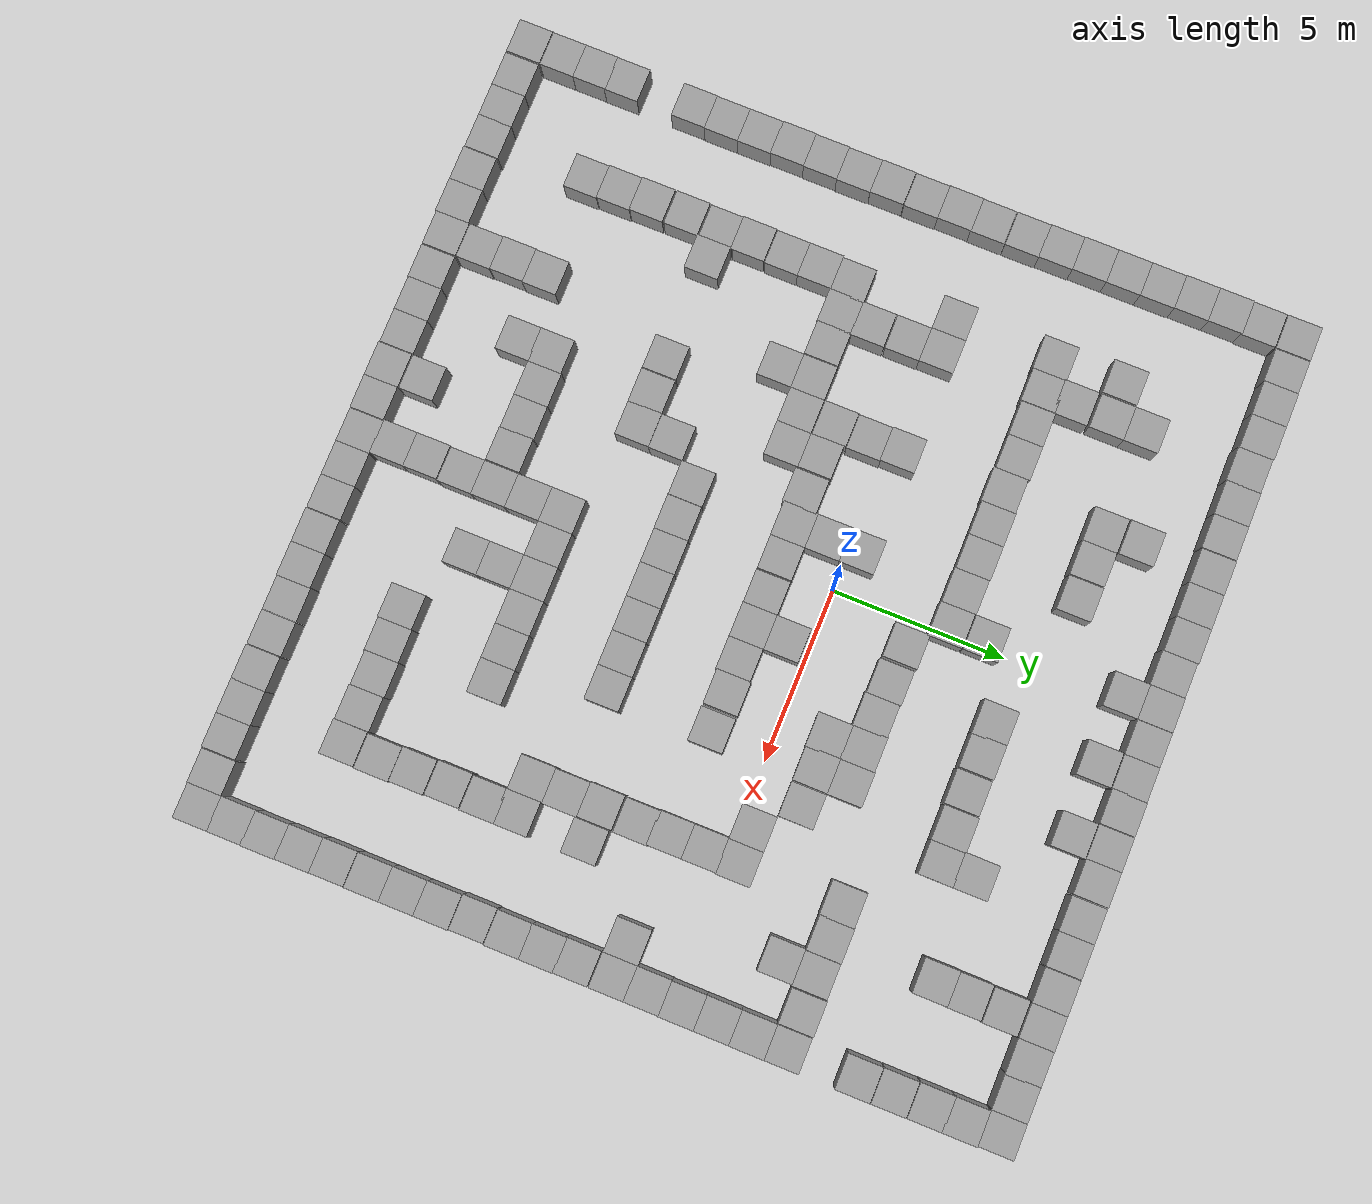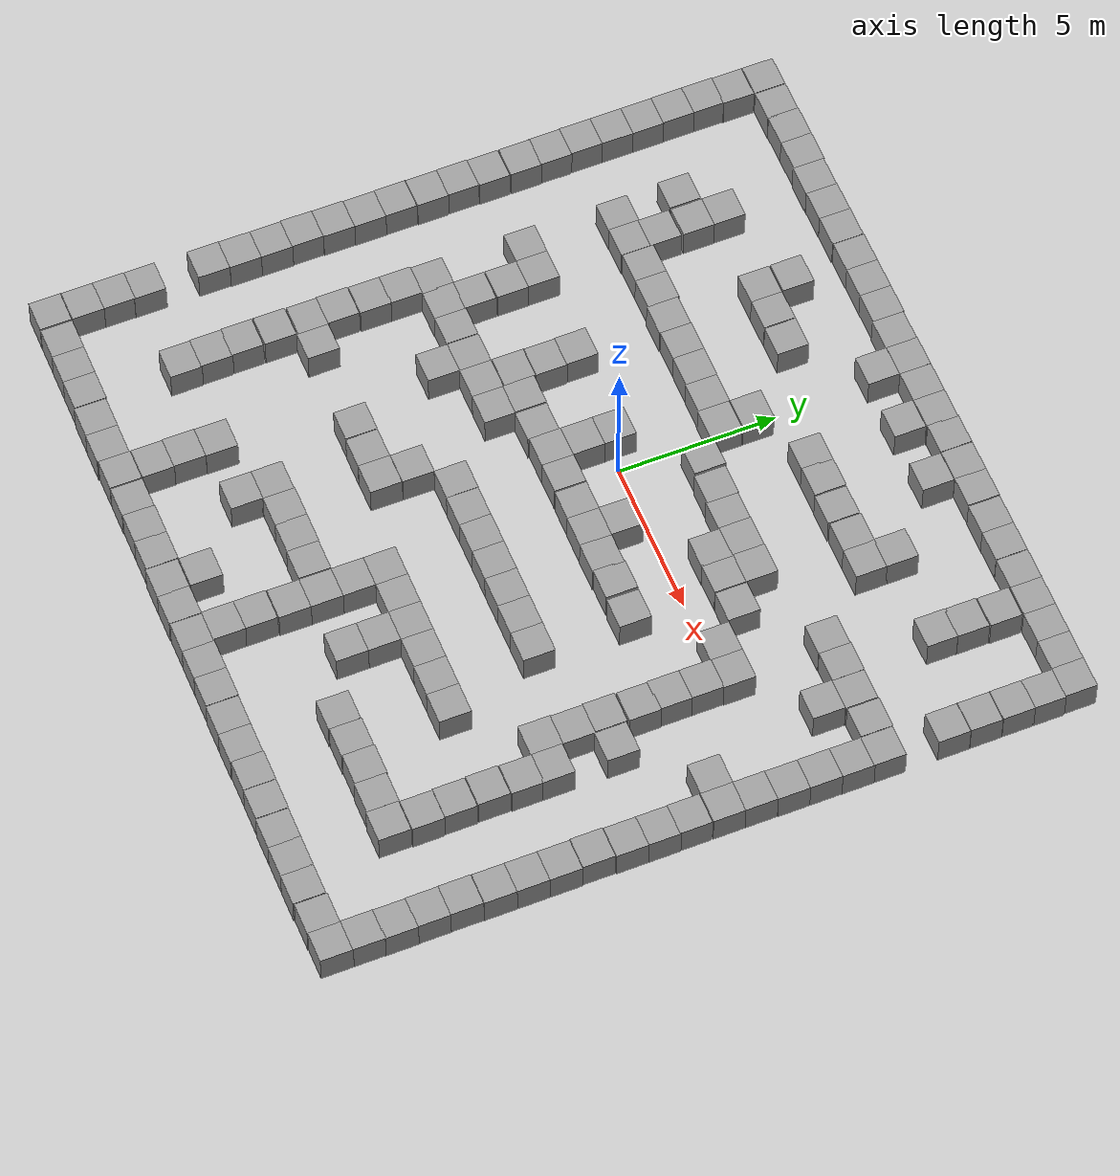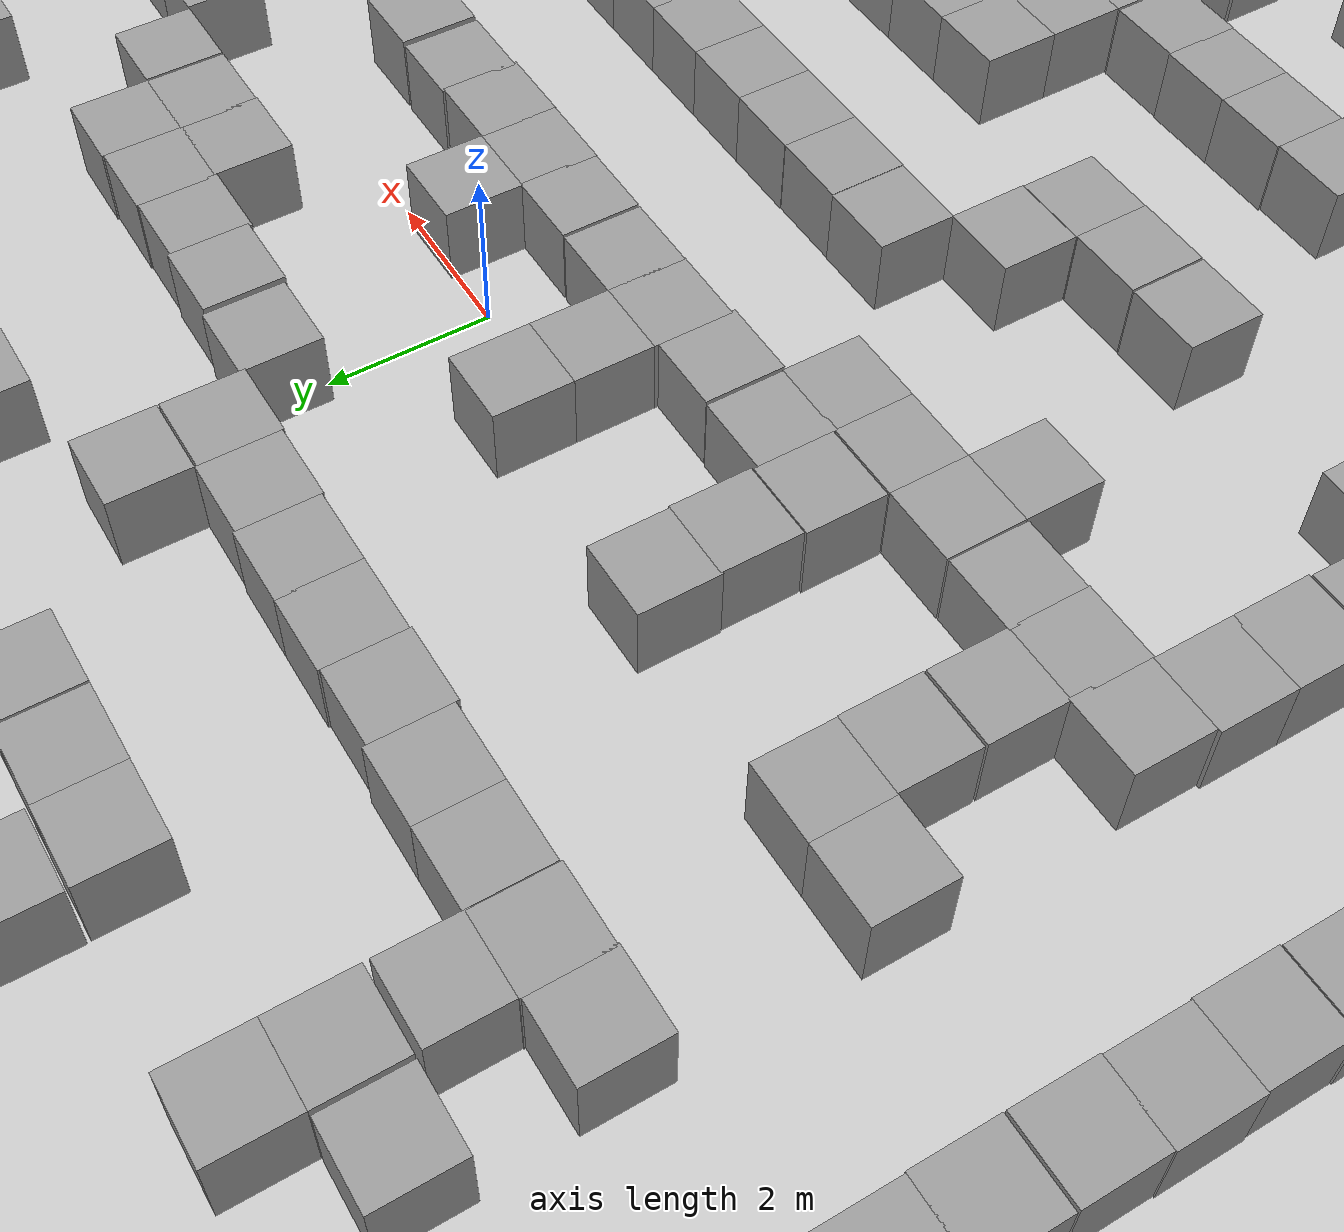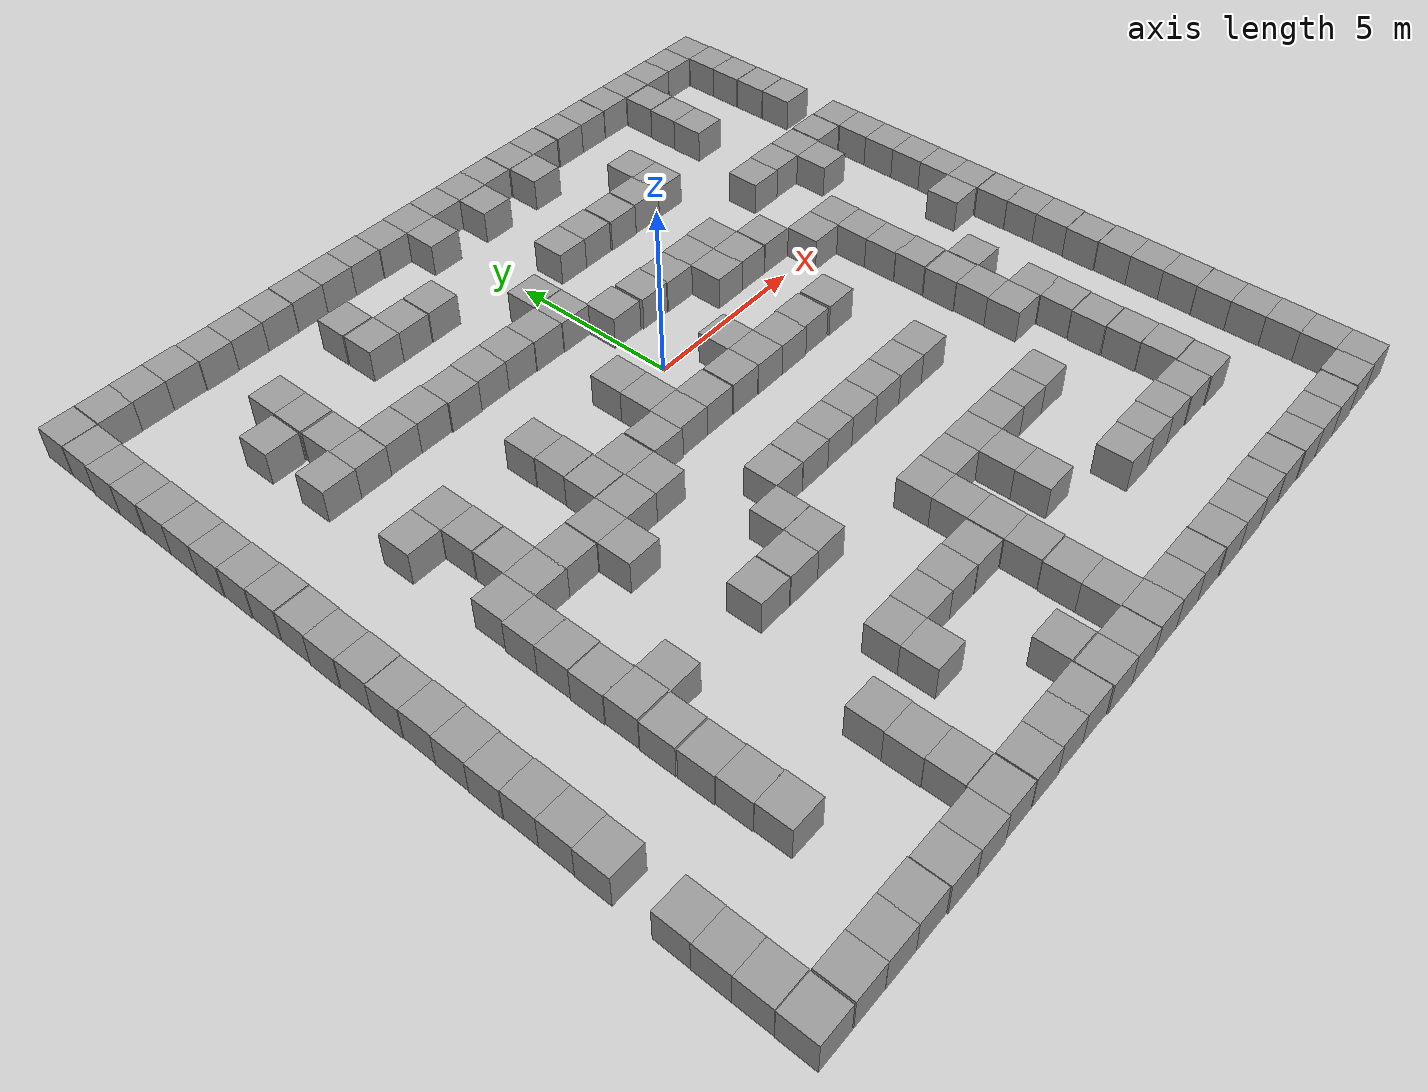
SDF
<?xml version='1.0'?>
<sdf version='1.7'>
  <model name='maze2.1'>
    <link name='link_1'>
      <inertial>
        <mass>1</mass>
        <inertia>
          <ixx>0.166667</ixx>
          <ixy>0</ixy>
          <ixz>0</ixz>
          <iyy>0.166667</iyy>
          <iyz>0</iyz>
          <izz>0.166667</izz>
        </inertia>
        <pose>0 0 0 0 -0 0</pose>
      </inertial>
      <pose>9.73191 9.35731 0 0 -0 0</pose>
      <gravity>1</gravity>
      <self_collide>0</self_collide>
      <kinematic>0</kinematic>
      <enable_wind>0</enable_wind>
      <visual name='visual'>
        <pose>0 0 0 0 -0 0</pose>
        <geometry>
          <box>
            <size>1 1 1</size>
          </box>
        </geometry>
        <material>
          <lighting>1</lighting>
          <script>
            <uri>file://media/materials/scripts/gazebo.material</uri>
            <name>Gazebo/Grey</name>
          </script>
          <shader type='pixel'>
            <normal_map>__default__</normal_map>
          </shader>
          <ambient>0.3 0.3 0.3 1</ambient>
          <diffuse>0.7 0.7 0.7 1</diffuse>
          <specular>0.01 0.01 0.01 1</specular>
          <emissive>0 0 0 1</emissive>
        </material>
        <transparency>0</transparency>
        <cast_shadows>1</cast_shadows>
      </visual>
      <collision name='collision'>
        <laser_retro>0</laser_retro>
        <max_contacts>10</max_contacts>
        <pose>0 0 0 0 -0 0</pose>
        <geometry>
          <box>
            <size>1 1 1</size>
          </box>
        </geometry>
        <surface>
          <friction>
            <ode>
              <mu>1</mu>
              <mu2>1</mu2>
              <fdir1>0 0 0</fdir1>
              <slip1>0</slip1>
              <slip2>0</slip2>
            </ode>
            <torsional>
              <coefficient>1</coefficient>
              <patch_radius>0</patch_radius>
              <surface_radius>0</surface_radius>
              <use_patch_radius>1</use_patch_radius>
              <ode>
                <slip>0</slip>
              </ode>
            </torsional>
          </friction>
          <bounce>
            <restitution_coefficient>0</restitution_coefficient>
            <threshold>1e+06</threshold>
          </bounce>
          <contact>
            <collide_without_contact>0</collide_without_contact>
            <collide_without_contact_bitmask>1</collide_without_contact_bitmask>
            <collide_bitmask>1</collide_bitmask>
            <ode>
              <soft_cfm>0</soft_cfm>
              <soft_erp>0.2</soft_erp>
              <kp>1e+13</kp>
              <kd>1</kd>
              <max_vel>0.01</max_vel>
              <min_depth>0</min_depth>
            </ode>
            <bullet>
              <split_impulse>1</split_impulse>
              <split_impulse_penetration_threshold>-0.01</split_impulse_penetration_threshold>
              <soft_cfm>0</soft_cfm>
              <soft_erp>0.2</soft_erp>
              <kp>1e+13</kp>
              <kd>1</kd>
            </bullet>
          </contact>
        </surface>
      </collision>
    </link>
    <link name='link_0'>
      <inertial>
        <mass>1</mass>
        <inertia>
          <ixx>0.166667</ixx>
          <ixy>0</ixy>
          <ixz>0</ixz>
          <iyy>0.166667</iyy>
          <iyz>0</iyz>
          <izz>0.166667</izz>
        </inertia>
      </inertial>
      <pose>10.704 9.35209 0 0 -0 0</pose>
      <visual name='visual'>
        <pose>0 0 0 0 -0 0</pose>
        <geometry>
          <box>
            <size>1 1 1</size>
          </box>
        </geometry>
        <material>
          <lighting>1</lighting>
          <script>
            <uri>file://media/materials/scripts/gazebo.material</uri>
            <name>Gazebo/Grey</name>
          </script>
          <shader type='pixel'/>
        </material>
        <transparency>0</transparency>
        <cast_shadows>1</cast_shadows>
      </visual>
      <collision name='collision'>
        <laser_retro>0</laser_retro>
        <max_contacts>10</max_contacts>
        <pose>0 0 0 0 -0 0</pose>
        <geometry>
          <box>
            <size>1 1 1</size>
          </box>
        </geometry>
        <surface>
          <friction>
            <ode>
              <mu>1</mu>
              <mu2>1</mu2>
              <fdir1>0 0 0</fdir1>
              <slip1>0</slip1>
              <slip2>0</slip2>
            </ode>
            <torsional>
              <coefficient>1</coefficient>
              <patch_radius>0</patch_radius>
              <surface_radius>0</surface_radius>
              <use_patch_radius>1</use_patch_radius>
              <ode>
                <slip>0</slip>
              </ode>
            </torsional>
          </friction>
          <bounce>
            <restitution_coefficient>0</restitution_coefficient>
            <threshold>1e+06</threshold>
          </bounce>
          <contact>
            <collide_without_contact>0</collide_without_contact>
            <collide_without_contact_bitmask>1</collide_without_contact_bitmask>
            <collide_bitmask>1</collide_bitmask>
            <ode>
              <soft_cfm>0</soft_cfm>
              <soft_erp>0.2</soft_erp>
              <kp>1e+13</kp>
              <kd>1</kd>
              <max_vel>0.01</max_vel>
              <min_depth>0</min_depth>
            </ode>
            <bullet>
              <split_impulse>1</split_impulse>
              <split_impulse_penetration_threshold>-0.01</split_impulse_penetration_threshold>
              <soft_cfm>0</soft_cfm>
              <soft_erp>0.2</soft_erp>
              <kp>1e+13</kp>
              <kd>1</kd>
            </bullet>
          </contact>
        </surface>
      </collision>
    </link>
    <link name='link_10'>
      <inertial>
        <mass>1</mass>
        <inertia>
          <ixx>0.166667</ixx>
          <ixy>0</ixy>
          <ixz>0</ixz>
          <iyy>0.166667</iyy>
          <iyz>0</iyz>
          <izz>0.166667</izz>
        </inertia>
      </inertial>
      <pose>-11.2599 7.37778 0 0 -0 0</pose>
      <visual name='visual'>
        <pose>0 0 0 0 -0 0</pose>
        <geometry>
          <box>
            <size>1 1 1</size>
          </box>
        </geometry>
        <material>
          <lighting>1</lighting>
          <script>
            <uri>file://media/materials/scripts/gazebo.material</uri>
            <name>Gazebo/Grey</name>
          </script>
          <shader type='pixel'/>
        </material>
        <transparency>0</transparency>
        <cast_shadows>1</cast_shadows>
      </visual>
      <collision name='collision'>
        <laser_retro>0</laser_retro>
        <max_contacts>10</max_contacts>
        <pose>0 0 0 0 -0 0</pose>
        <geometry>
          <box>
            <size>1 1 1</size>
          </box>
        </geometry>
        <surface>
          <friction>
            <ode>
              <mu>1</mu>
              <mu2>1</mu2>
              <fdir1>0 0 0</fdir1>
              <slip1>0</slip1>
              <slip2>0</slip2>
            </ode>
            <torsional>
              <coefficient>1</coefficient>
              <patch_radius>0</patch_radius>
              <surface_radius>0</surface_radius>
              <use_patch_radius>1</use_patch_radius>
              <ode>
                <slip>0</slip>
              </ode>
            </torsional>
          </friction>
          <bounce>
            <restitution_coefficient>0</restitution_coefficient>
            <threshold>1e+06</threshold>
          </bounce>
          <contact>
            <collide_without_contact>0</collide_without_contact>
            <collide_without_contact_bitmask>1</collide_without_contact_bitmask>
            <collide_bitmask>1</collide_bitmask>
            <ode>
              <soft_cfm>0</soft_cfm>
              <soft_erp>0.2</soft_erp>
              <kp>1e+13</kp>
              <kd>1</kd>
              <max_vel>0.01</max_vel>
              <min_depth>0</min_depth>
            </ode>
            <bullet>
              <split_impulse>1</split_impulse>
              <split_impulse_penetration_threshold>-0.01</split_impulse_penetration_threshold>
              <soft_cfm>0</soft_cfm>
              <soft_erp>0.2</soft_erp>
              <kp>1e+13</kp>
              <kd>1</kd>
            </bullet>
          </contact>
        </surface>
      </collision>
    </link>
    <link name='link_11'>
      <inertial>
        <mass>1</mass>
        <inertia>
          <ixx>0.166667</ixx>
          <ixy>0</ixy>
          <ixz>0</ixz>
          <iyy>0.166667</iyy>
          <iyz>0</iyz>
          <izz>0.166667</izz>
        </inertia>
      </inertial>
      <pose>-7.25694 3.37065 0 0 -0 0</pose>
      <visual name='visual'>
        <pose>0 0 0 0 -0 0</pose>
        <geometry>
          <box>
            <size>1 1 1</size>
          </box>
        </geometry>
        <material>
          <lighting>1</lighting>
          <script>
            <uri>file://media/materials/scripts/gazebo.material</uri>
            <name>Gazebo/Grey</name>
          </script>
          <shader type='pixel'/>
        </material>
        <transparency>0</transparency>
        <cast_shadows>1</cast_shadows>
      </visual>
      <collision name='collision'>
        <laser_retro>0</laser_retro>
        <max_contacts>10</max_contacts>
        <pose>0 0 0 0 -0 0</pose>
        <geometry>
          <box>
            <size>1 1 1</size>
          </box>
        </geometry>
        <surface>
          <friction>
            <ode>
              <mu>1</mu>
              <mu2>1</mu2>
              <fdir1>0 0 0</fdir1>
              <slip1>0</slip1>
              <slip2>0</slip2>
            </ode>
            <torsional>
              <coefficient>1</coefficient>
              <patch_radius>0</patch_radius>
              <surface_radius>0</surface_radius>
              <use_patch_radius>1</use_patch_radius>
              <ode>
                <slip>0</slip>
              </ode>
            </torsional>
          </friction>
          <bounce>
            <restitution_coefficient>0</restitution_coefficient>
            <threshold>1e+06</threshold>
          </bounce>
          <contact>
            <collide_without_contact>0</collide_without_contact>
            <collide_without_contact_bitmask>1</collide_without_contact_bitmask>
            <collide_bitmask>1</collide_bitmask>
            <ode>
              <soft_cfm>0</soft_cfm>
              <soft_erp>0.2</soft_erp>
              <kp>1e+13</kp>
              <kd>1</kd>
              <max_vel>0.01</max_vel>
              <min_depth>0</min_depth>
            </ode>
            <bullet>
              <split_impulse>1</split_impulse>
              <split_impulse_penetration_threshold>-0.01</split_impulse_penetration_threshold>
              <soft_cfm>0</soft_cfm>
              <soft_erp>0.2</soft_erp>
              <kp>1e+13</kp>
              <kd>1</kd>
            </bullet>
          </contact>
        </surface>
      </collision>
    </link>
    <link name='link_12'>
      <inertial>
        <mass>1</mass>
        <inertia>
          <ixx>0.166667</ixx>
          <ixy>0</ixy>
          <ixz>0</ixz>
          <iyy>0.166667</iyy>
          <iyz>0</iyz>
          <izz>0.166667</izz>
        </inertia>
      </inertial>
      <pose>0.709748 2.40314 0 0 -0 0</pose>
      <visual name='visual'>
        <pose>0 0 0 0 -0 0</pose>
        <geometry>
          <box>
            <size>1 1 1</size>
          </box>
        </geometry>
        <material>
          <lighting>1</lighting>
          <script>
            <uri>file://media/materials/scripts/gazebo.material</uri>
            <name>Gazebo/Grey</name>
          </script>
          <shader type='pixel'/>
        </material>
        <transparency>0</transparency>
        <cast_shadows>1</cast_shadows>
      </visual>
      <collision name='collision'>
        <laser_retro>0</laser_retro>
        <max_contacts>10</max_contacts>
        <pose>0 0 0 0 -0 0</pose>
        <geometry>
          <box>
            <size>1 1 1</size>
          </box>
        </geometry>
        <surface>
          <friction>
            <ode>
              <mu>1</mu>
              <mu2>1</mu2>
              <fdir1>0 0 0</fdir1>
              <slip1>0</slip1>
              <slip2>0</slip2>
            </ode>
            <torsional>
              <coefficient>1</coefficient>
              <patch_radius>0</patch_radius>
              <surface_radius>0</surface_radius>
              <use_patch_radius>1</use_patch_radius>
              <ode>
                <slip>0</slip>
              </ode>
            </torsional>
          </friction>
          <bounce>
            <restitution_coefficient>0</restitution_coefficient>
            <threshold>1e+06</threshold>
          </bounce>
          <contact>
            <collide_without_contact>0</collide_without_contact>
            <collide_without_contact_bitmask>1</collide_without_contact_bitmask>
            <collide_bitmask>1</collide_bitmask>
            <ode>
              <soft_cfm>0</soft_cfm>
              <soft_erp>0.2</soft_erp>
              <kp>1e+13</kp>
              <kd>1</kd>
              <max_vel>0.01</max_vel>
              <min_depth>0</min_depth>
            </ode>
            <bullet>
              <split_impulse>1</split_impulse>
              <split_impulse_penetration_threshold>-0.01</split_impulse_penetration_threshold>
              <soft_cfm>0</soft_cfm>
              <soft_erp>0.2</soft_erp>
              <kp>1e+13</kp>
              <kd>1</kd>
            </bullet>
          </contact>
        </surface>
      </collision>
    </link>
    <link name='link_13'>
      <inertial>
        <mass>1</mass>
        <inertia>
          <ixx>0.166667</ixx>
          <ixy>0</ixy>
          <ixz>0</ixz>
          <iyy>0.166667</iyy>
          <iyz>0</iyz>
          <izz>0.166667</izz>
        </inertia>
      </inertial>
      <pose>-6.26868 -2.63049 0 0 -0 0</pose>
      <visual name='visual'>
        <pose>0 0 0 0 -0 0</pose>
        <geometry>
          <box>
            <size>1 1 1</size>
          </box>
        </geometry>
        <material>
          <lighting>1</lighting>
          <script>
            <uri>file://media/materials/scripts/gazebo.material</uri>
            <name>Gazebo/Grey</name>
          </script>
          <shader type='pixel'/>
        </material>
        <transparency>0</transparency>
        <cast_shadows>1</cast_shadows>
      </visual>
      <collision name='collision'>
        <laser_retro>0</laser_retro>
        <max_contacts>10</max_contacts>
        <pose>0 0 0 0 -0 0</pose>
        <geometry>
          <box>
            <size>1 1 1</size>
          </box>
        </geometry>
        <surface>
          <friction>
            <ode>
              <mu>1</mu>
              <mu2>1</mu2>
              <fdir1>0 0 0</fdir1>
              <slip1>0</slip1>
              <slip2>0</slip2>
            </ode>
            <torsional>
              <coefficient>1</coefficient>
              <patch_radius>0</patch_radius>
              <surface_radius>0</surface_radius>
              <use_patch_radius>1</use_patch_radius>
              <ode>
                <slip>0</slip>
              </ode>
            </torsional>
          </friction>
          <bounce>
            <restitution_coefficient>0</restitution_coefficient>
            <threshold>1e+06</threshold>
          </bounce>
          <contact>
            <collide_without_contact>0</collide_without_contact>
            <collide_without_contact_bitmask>1</collide_without_contact_bitmask>
            <collide_bitmask>1</collide_bitmask>
            <ode>
              <soft_cfm>0</soft_cfm>
              <soft_erp>0.2</soft_erp>
              <kp>1e+13</kp>
              <kd>1</kd>
              <max_vel>0.01</max_vel>
              <min_depth>0</min_depth>
            </ode>
            <bullet>
              <split_impulse>1</split_impulse>
              <split_impulse_penetration_threshold>-0.01</split_impulse_penetration_threshold>
              <soft_cfm>0</soft_cfm>
              <soft_erp>0.2</soft_erp>
              <kp>1e+13</kp>
              <kd>1</kd>
            </bullet>
          </contact>
        </surface>
      </collision>
    </link>
    <link name='link_14'>
      <inertial>
        <mass>1</mass>
        <inertia>
          <ixx>0.166667</ixx>
          <ixy>0</ixy>
          <ixz>0</ixz>
          <iyy>0.166667</iyy>
          <iyz>0</iyz>
          <izz>0.166667</izz>
        </inertia>
      </inertial>
      <pose>-7.23944 -2.64333 0 0 -0 0</pose>
      <visual name='visual'>
        <pose>0 0 0 0 -0 0</pose>
        <geometry>
          <box>
            <size>1 1 1</size>
          </box>
        </geometry>
        <material>
          <lighting>1</lighting>
          <script>
            <uri>file://media/materials/scripts/gazebo.material</uri>
            <name>Gazebo/Grey</name>
          </script>
          <shader type='pixel'/>
        </material>
        <transparency>0</transparency>
        <cast_shadows>1</cast_shadows>
      </visual>
      <collision name='collision'>
        <laser_retro>0</laser_retro>
        <max_contacts>10</max_contacts>
        <pose>0 0 0 0 -0 0</pose>
        <geometry>
          <box>
            <size>1 1 1</size>
          </box>
        </geometry>
        <surface>
          <friction>
            <ode>
              <mu>1</mu>
              <mu2>1</mu2>
              <fdir1>0 0 0</fdir1>
              <slip1>0</slip1>
              <slip2>0</slip2>
            </ode>
            <torsional>
              <coefficient>1</coefficient>
              <patch_radius>0</patch_radius>
              <surface_radius>0</surface_radius>
              <use_patch_radius>1</use_patch_radius>
              <ode>
                <slip>0</slip>
              </ode>
            </torsional>
          </friction>
          <bounce>
            <restitution_coefficient>0</restitution_coefficient>
            <threshold>1e+06</threshold>
          </bounce>
          <contact>
            <collide_without_contact>0</collide_without_contact>
            <collide_without_contact_bitmask>1</collide_without_contact_bitmask>
            <collide_bitmask>1</collide_bitmask>
            <ode>
              <soft_cfm>0</soft_cfm>
              <soft_erp>0.2</soft_erp>
              <kp>1e+13</kp>
              <kd>1</kd>
              <max_vel>0.01</max_vel>
              <min_depth>0</min_depth>
            </ode>
            <bullet>
              <split_impulse>1</split_impulse>
              <split_impulse_penetration_threshold>-0.01</split_impulse_penetration_threshold>
              <soft_cfm>0</soft_cfm>
              <soft_erp>0.2</soft_erp>
              <kp>1e+13</kp>
              <kd>1</kd>
            </bullet>
          </contact>
        </surface>
      </collision>
    </link>
    <link name='link_15'>
      <inertial>
        <mass>1</mass>
        <inertia>
          <ixx>0.166667</ixx>
          <ixy>0</ixy>
          <ixz>0</ixz>
          <iyy>0.166667</iyy>
          <iyz>0</iyz>
          <izz>0.166667</izz>
        </inertia>
      </inertial>
      <pose>4.70076 2.36358 0 0 -0 0</pose>
      <visual name='visual'>
        <pose>0 0 0 0 -0 0</pose>
        <geometry>
          <box>
            <size>1 1 1</size>
          </box>
        </geometry>
        <material>
          <lighting>1</lighting>
          <script>
            <uri>file://media/materials/scripts/gazebo.material</uri>
            <name>Gazebo/Grey</name>
          </script>
          <shader type='pixel'/>
        </material>
        <transparency>0</transparency>
        <cast_shadows>1</cast_shadows>
      </visual>
      <collision name='collision'>
        <laser_retro>0</laser_retro>
        <max_contacts>10</max_contacts>
        <pose>0 0 0 0 -0 0</pose>
        <geometry>
          <box>
            <size>1 1 1</size>
          </box>
        </geometry>
        <surface>
          <friction>
            <ode>
              <mu>1</mu>
              <mu2>1</mu2>
              <fdir1>0 0 0</fdir1>
              <slip1>0</slip1>
              <slip2>0</slip2>
            </ode>
            <torsional>
              <coefficient>1</coefficient>
              <patch_radius>0</patch_radius>
              <surface_radius>0</surface_radius>
              <use_patch_radius>1</use_patch_radius>
              <ode>
                <slip>0</slip>
              </ode>
            </torsional>
          </friction>
          <bounce>
            <restitution_coefficient>0</restitution_coefficient>
            <threshold>1e+06</threshold>
          </bounce>
          <contact>
            <collide_without_contact>0</collide_without_contact>
            <collide_without_contact_bitmask>1</collide_without_contact_bitmask>
            <collide_bitmask>1</collide_bitmask>
            <ode>
              <soft_cfm>0</soft_cfm>
              <soft_erp>0.2</soft_erp>
              <kp>1e+13</kp>
              <kd>1</kd>
              <max_vel>0.01</max_vel>
              <min_depth>0</min_depth>
            </ode>
            <bullet>
              <split_impulse>1</split_impulse>
              <split_impulse_penetration_threshold>-0.01</split_impulse_penetration_threshold>
              <soft_cfm>0</soft_cfm>
              <soft_erp>0.2</soft_erp>
              <kp>1e+13</kp>
              <kd>1</kd>
            </bullet>
          </contact>
        </surface>
      </collision>
    </link>
    <link name='link_16'>
      <inertial>
        <mass>1</mass>
        <inertia>
          <ixx>0.166667</ixx>
          <ixy>0</ixy>
          <ixz>0</ixz>
          <iyy>0.166667</iyy>
          <iyz>0</iyz>
          <izz>0.166667</izz>
        </inertia>
      </inertial>
      <pose>11.7552 -11.6234 0 0 -0 0</pose>
      <visual name='visual'>
        <pose>0 0 0 0 -0 0</pose>
        <geometry>
          <box>
            <size>1 1 1</size>
          </box>
        </geometry>
        <material>
          <lighting>1</lighting>
          <script>
            <uri>file://media/materials/scripts/gazebo.material</uri>
            <name>Gazebo/Grey</name>
          </script>
          <shader type='pixel'/>
        </material>
        <transparency>0</transparency>
        <cast_shadows>1</cast_shadows>
      </visual>
      <collision name='collision'>
        <laser_retro>0</laser_retro>
        <max_contacts>10</max_contacts>
        <pose>0 0 0 0 -0 0</pose>
        <geometry>
          <box>
            <size>1 1 1</size>
          </box>
        </geometry>
        <surface>
          <friction>
            <ode>
              <mu>1</mu>
              <mu2>1</mu2>
              <fdir1>0 0 0</fdir1>
              <slip1>0</slip1>
              <slip2>0</slip2>
            </ode>
            <torsional>
              <coefficient>1</coefficient>
              <patch_radius>0</patch_radius>
              <surface_radius>0</surface_radius>
              <use_patch_radius>1</use_patch_radius>
              <ode>
                <slip>0</slip>
              </ode>
            </torsional>
          </friction>
          <bounce>
            <restitution_coefficient>0</restitution_coefficient>
            <threshold>1e+06</threshold>
          </bounce>
          <contact>
            <collide_without_contact>0</collide_without_contact>
            <collide_without_contact_bitmask>1</collide_without_contact_bitmask>
            <collide_bitmask>1</collide_bitmask>
            <ode>
              <soft_cfm>0</soft_cfm>
              <soft_erp>0.2</soft_erp>
              <kp>1e+13</kp>
              <kd>1</kd>
              <max_vel>0.01</max_vel>
              <min_depth>0</min_depth>
            </ode>
            <bullet>
              <split_impulse>1</split_impulse>
              <split_impulse_penetration_threshold>-0.01</split_impulse_penetration_threshold>
              <soft_cfm>0</soft_cfm>
              <soft_erp>0.2</soft_erp>
              <kp>1e+13</kp>
              <kd>1</kd>
            </bullet>
          </contact>
        </surface>
      </collision>
    </link>
    <link name='link_17'>
      <inertial>
        <mass>1</mass>
        <inertia>
          <ixx>0.166667</ixx>
          <ixy>0</ixy>
          <ixz>0</ixz>
          <iyy>0.166667</iyy>
          <iyz>0</iyz>
          <izz>0.166667</izz>
        </inertia>
      </inertial>
      <pose>11.7435 -12.5978 0 0 -0 0</pose>
      <visual name='visual'>
        <pose>0 0 0 0 -0 0</pose>
        <geometry>
          <box>
            <size>1 1 1</size>
          </box>
        </geometry>
        <material>
          <lighting>1</lighting>
          <script>
            <uri>file://media/materials/scripts/gazebo.material</uri>
            <name>Gazebo/Grey</name>
          </script>
          <shader type='pixel'/>
        </material>
        <transparency>0</transparency>
        <cast_shadows>1</cast_shadows>
      </visual>
      <collision name='collision'>
        <laser_retro>0</laser_retro>
        <max_contacts>10</max_contacts>
        <pose>0 0 0 0 -0 0</pose>
        <geometry>
          <box>
            <size>1 1 1</size>
          </box>
        </geometry>
        <surface>
          <friction>
            <ode>
              <mu>1</mu>
              <mu2>1</mu2>
              <fdir1>0 0 0</fdir1>
              <slip1>0</slip1>
              <slip2>0</slip2>
            </ode>
            <torsional>
              <coefficient>1</coefficient>
              <patch_radius>0</patch_radius>
              <surface_radius>0</surface_radius>
              <use_patch_radius>1</use_patch_radius>
              <ode>
                <slip>0</slip>
              </ode>
            </torsional>
          </friction>
          <bounce>
            <restitution_coefficient>0</restitution_coefficient>
            <threshold>1e+06</threshold>
          </bounce>
          <contact>
            <collide_without_contact>0</collide_without_contact>
            <collide_without_contact_bitmask>1</collide_without_contact_bitmask>
            <collide_bitmask>1</collide_bitmask>
            <ode>
              <soft_cfm>0</soft_cfm>
              <soft_erp>0.2</soft_erp>
              <kp>1e+13</kp>
              <kd>1</kd>
              <max_vel>0.01</max_vel>
              <min_depth>0</min_depth>
            </ode>
            <bullet>
              <split_impulse>1</split_impulse>
              <split_impulse_penetration_threshold>-0.01</split_impulse_penetration_threshold>
              <soft_cfm>0</soft_cfm>
              <soft_erp>0.2</soft_erp>
              <kp>1e+13</kp>
              <kd>1</kd>
            </bullet>
          </contact>
        </surface>
      </collision>
    </link>
    <link name='link_18'>
      <inertial>
        <mass>1</mass>
        <inertia>
          <ixx>0.166667</ixx>
          <ixy>0</ixy>
          <ixz>0</ixz>
          <iyy>0.166667</iyy>
          <iyz>0</iyz>
          <izz>0.166667</izz>
        </inertia>
      </inertial>
      <pose>11.7435 -13.5836 0 0 -0 0</pose>
      <visual name='visual'>
        <pose>0 0 0 0 -0 0</pose>
        <geometry>
          <box>
            <size>1 1 1</size>
          </box>
        </geometry>
        <material>
          <lighting>1</lighting>
          <script>
            <uri>file://media/materials/scripts/gazebo.material</uri>
            <name>Gazebo/Grey</name>
          </script>
          <shader type='pixel'/>
        </material>
        <transparency>0</transparency>
        <cast_shadows>1</cast_shadows>
      </visual>
      <collision name='collision'>
        <laser_retro>0</laser_retro>
        <max_contacts>10</max_contacts>
        <pose>0 0 0 0 -0 0</pose>
        <geometry>
          <box>
            <size>1 1 1</size>
          </box>
        </geometry>
        <surface>
          <friction>
            <ode>
              <mu>1</mu>
              <mu2>1</mu2>
              <fdir1>0 0 0</fdir1>
              <slip1>0</slip1>
              <slip2>0</slip2>
            </ode>
            <torsional>
              <coefficient>1</coefficient>
              <patch_radius>0</patch_radius>
              <surface_radius>0</surface_radius>
              <use_patch_radius>1</use_patch_radius>
              <ode>
                <slip>0</slip>
              </ode>
            </torsional>
          </friction>
          <bounce>
            <restitution_coefficient>0</restitution_coefficient>
            <threshold>1e+06</threshold>
          </bounce>
          <contact>
            <collide_without_contact>0</collide_without_contact>
            <collide_without_contact_bitmask>1</collide_without_contact_bitmask>
            <collide_bitmask>1</collide_bitmask>
            <ode>
              <soft_cfm>0</soft_cfm>
              <soft_erp>0.2</soft_erp>
              <kp>1e+13</kp>
              <kd>1</kd>
              <max_vel>0.01</max_vel>
              <min_depth>0</min_depth>
            </ode>
            <bullet>
              <split_impulse>1</split_impulse>
              <split_impulse_penetration_threshold>-0.01</split_impulse_penetration_threshold>
              <soft_cfm>0</soft_cfm>
              <soft_erp>0.2</soft_erp>
              <kp>1e+13</kp>
              <kd>1</kd>
            </bullet>
          </contact>
        </surface>
      </collision>
    </link>
    <link name='link_19'>
      <inertial>
        <mass>1</mass>
        <inertia>
          <ixx>0.166667</ixx>
          <ixy>0</ixy>
          <ixz>0</ixz>
          <iyy>0.166667</iyy>
          <iyz>0</iyz>
          <izz>0.166667</izz>
        </inertia>
      </inertial>
      <pose>10.7623 -13.604 0 0 -0 0</pose>
      <visual name='visual'>
        <pose>0 0 0 0 -0 0</pose>
        <geometry>
          <box>
            <size>1 1 1</size>
          </box>
        </geometry>
        <material>
          <lighting>1</lighting>
          <script>
            <uri>file://media/materials/scripts/gazebo.material</uri>
            <name>Gazebo/Grey</name>
          </script>
          <shader type='pixel'/>
        </material>
        <transparency>0</transparency>
        <cast_shadows>1</cast_shadows>
      </visual>
      <collision name='collision'>
        <laser_retro>0</laser_retro>
        <max_contacts>10</max_contacts>
        <pose>0 0 0 0 -0 0</pose>
        <geometry>
          <box>
            <size>1 1 1</size>
          </box>
        </geometry>
        <surface>
          <friction>
            <ode>
              <mu>1</mu>
              <mu2>1</mu2>
              <fdir1>0 0 0</fdir1>
              <slip1>0</slip1>
              <slip2>0</slip2>
            </ode>
            <torsional>
              <coefficient>1</coefficient>
              <patch_radius>0</patch_radius>
              <surface_radius>0</surface_radius>
              <use_patch_radius>1</use_patch_radius>
              <ode>
                <slip>0</slip>
              </ode>
            </torsional>
          </friction>
          <bounce>
            <restitution_coefficient>0</restitution_coefficient>
            <threshold>1e+06</threshold>
          </bounce>
          <contact>
            <collide_without_contact>0</collide_without_contact>
            <collide_without_contact_bitmask>1</collide_without_contact_bitmask>
            <collide_bitmask>1</collide_bitmask>
            <ode>
              <soft_cfm>0</soft_cfm>
              <soft_erp>0.2</soft_erp>
              <kp>1e+13</kp>
              <kd>1</kd>
              <max_vel>0.01</max_vel>
              <min_depth>0</min_depth>
            </ode>
            <bullet>
              <split_impulse>1</split_impulse>
              <split_impulse_penetration_threshold>-0.01</split_impulse_penetration_threshold>
              <soft_cfm>0</soft_cfm>
              <soft_erp>0.2</soft_erp>
              <kp>1e+13</kp>
              <kd>1</kd>
            </bullet>
          </contact>
        </surface>
      </collision>
    </link>
    <link name='link_1_0'>
      <inertial>
        <mass>1</mass>
        <inertia>
          <ixx>0.166667</ixx>
          <ixy>0</ixy>
          <ixz>0</ixz>
          <iyy>0.166667</iyy>
          <iyz>0</iyz>
          <izz>0.166667</izz>
        </inertia>
      </inertial>
      <pose>11.7027 9.35209 0 0 -0 0</pose>
      <visual name='visual'>
        <pose>0 0 0 0 -0 0</pose>
        <geometry>
          <box>
            <size>1 1 1</size>
          </box>
        </geometry>
        <material>
          <lighting>1</lighting>
          <script>
            <uri>file://media/materials/scripts/gazebo.material</uri>
            <name>Gazebo/Grey</name>
          </script>
          <shader type='pixel'/>
        </material>
        <transparency>0</transparency>
        <cast_shadows>1</cast_shadows>
      </visual>
      <collision name='collision'>
        <laser_retro>0</laser_retro>
        <max_contacts>10</max_contacts>
        <pose>0 0 0 0 -0 0</pose>
        <geometry>
          <box>
            <size>1 1 1</size>
          </box>
        </geometry>
        <surface>
          <friction>
            <ode>
              <mu>1</mu>
              <mu2>1</mu2>
              <fdir1>0 0 0</fdir1>
              <slip1>0</slip1>
              <slip2>0</slip2>
            </ode>
            <torsional>
              <coefficient>1</coefficient>
              <patch_radius>0</patch_radius>
              <surface_radius>0</surface_radius>
              <use_patch_radius>1</use_patch_radius>
              <ode>
                <slip>0</slip>
              </ode>
            </torsional>
          </friction>
          <bounce>
            <restitution_coefficient>0</restitution_coefficient>
            <threshold>1e+06</threshold>
          </bounce>
          <contact>
            <collide_without_contact>0</collide_without_contact>
            <collide_without_contact_bitmask>1</collide_without_contact_bitmask>
            <collide_bitmask>1</collide_bitmask>
            <ode>
              <soft_cfm>0</soft_cfm>
              <soft_erp>0.2</soft_erp>
              <kp>1e+13</kp>
              <kd>1</kd>
              <max_vel>0.01</max_vel>
              <min_depth>0</min_depth>
            </ode>
            <bullet>
              <split_impulse>1</split_impulse>
              <split_impulse_penetration_threshold>-0.01</split_impulse_penetration_threshold>
              <soft_cfm>0</soft_cfm>
              <soft_erp>0.2</soft_erp>
              <kp>1e+13</kp>
              <kd>1</kd>
            </bullet>
          </contact>
        </surface>
      </collision>
    </link>
    <link name='link_1_clone'>
      <inertial>
        <mass>1</mass>
        <inertia>
          <ixx>0.166667</ixx>
          <ixy>0</ixy>
          <ixz>0</ixz>
          <iyy>0.166667</iyy>
          <iyz>0</iyz>
          <izz>0.166667</izz>
        </inertia>
        <pose>0 0 0 0 -0 0</pose>
      </inertial>
      <pose>8.75414 9.36341 0 0 -0 0</pose>
      <gravity>1</gravity>
      <self_collide>0</self_collide>
      <kinematic>0</kinematic>
      <enable_wind>0</enable_wind>
      <visual name='visual'>
        <pose>0 0 0 0 -0 0</pose>
        <geometry>
          <box>
            <size>1 1 1</size>
          </box>
        </geometry>
        <material>
          <lighting>1</lighting>
          <script>
            <uri>file://media/materials/scripts/gazebo.material</uri>
            <name>Gazebo/Grey</name>
          </script>
          <shader type='pixel'>
            <normal_map>__default__</normal_map>
          </shader>
          <ambient>0.3 0.3 0.3 1</ambient>
          <diffuse>0.7 0.7 0.7 1</diffuse>
          <specular>0.01 0.01 0.01 1</specular>
          <emissive>0 0 0 1</emissive>
        </material>
        <transparency>0</transparency>
        <cast_shadows>1</cast_shadows>
      </visual>
      <collision name='collision'>
        <laser_retro>0</laser_retro>
        <max_contacts>10</max_contacts>
        <pose>0 0 0 0 -0 0</pose>
        <geometry>
          <box>
            <size>1 1 1</size>
          </box>
        </geometry>
        <surface>
          <friction>
            <ode>
              <mu>1</mu>
              <mu2>1</mu2>
              <fdir1>0 0 0</fdir1>
              <slip1>0</slip1>
              <slip2>0</slip2>
            </ode>
            <torsional>
              <coefficient>1</coefficient>
              <patch_radius>0</patch_radius>
              <surface_radius>0</surface_radius>
              <use_patch_radius>1</use_patch_radius>
              <ode>
                <slip>0</slip>
              </ode>
            </torsional>
          </friction>
          <bounce>
            <restitution_coefficient>0</restitution_coefficient>
            <threshold>1e+06</threshold>
          </bounce>
          <contact>
            <collide_without_contact>0</collide_without_contact>
            <collide_without_contact_bitmask>1</collide_without_contact_bitmask>
            <collide_bitmask>1</collide_bitmask>
            <ode>
              <soft_cfm>0</soft_cfm>
              <soft_erp>0.2</soft_erp>
              <kp>1e+13</kp>
              <kd>1</kd>
              <max_vel>0.01</max_vel>
              <min_depth>0</min_depth>
            </ode>
            <bullet>
              <split_impulse>1</split_impulse>
              <split_impulse_penetration_threshold>-0.01</split_impulse_penetration_threshold>
              <soft_cfm>0</soft_cfm>
              <soft_erp>0.2</soft_erp>
              <kp>1e+13</kp>
              <kd>1</kd>
            </bullet>
          </contact>
        </surface>
      </collision>
    </link>
    <link name='link_1_clone_0'>
      <inertial>
        <mass>1</mass>
        <inertia>
          <ixx>0.166667</ixx>
          <ixy>0</ixy>
          <ixz>0</ixz>
          <iyy>0.166667</iyy>
          <iyz>0</iyz>
          <izz>0.166667</izz>
        </inertia>
        <pose>0 0 0 0 -0 0</pose>
      </inertial>
      <pose>7.75382 9.3701 0 0 -0 0</pose>
      <gravity>1</gravity>
      <self_collide>0</self_collide>
      <kinematic>0</kinematic>
      <enable_wind>0</enable_wind>
      <visual name='visual'>
        <pose>0 0 0 0 -0 0</pose>
        <geometry>
          <box>
            <size>1 1 1</size>
          </box>
        </geometry>
        <material>
          <lighting>1</lighting>
          <script>
            <uri>file://media/materials/scripts/gazebo.material</uri>
            <name>Gazebo/Grey</name>
          </script>
          <shader type='pixel'>
            <normal_map>__default__</normal_map>
          </shader>
          <ambient>0.3 0.3 0.3 1</ambient>
          <diffuse>0.7 0.7 0.7 1</diffuse>
          <specular>0.01 0.01 0.01 1</specular>
          <emissive>0 0 0 1</emissive>
        </material>
        <transparency>0</transparency>
        <cast_shadows>1</cast_shadows>
      </visual>
      <collision name='collision'>
        <laser_retro>0</laser_retro>
        <max_contacts>10</max_contacts>
        <pose>0 0 0 0 -0 0</pose>
        <geometry>
          <box>
            <size>1 1 1</size>
          </box>
        </geometry>
        <surface>
          <friction>
            <ode>
              <mu>1</mu>
              <mu2>1</mu2>
              <fdir1>0 0 0</fdir1>
              <slip1>0</slip1>
              <slip2>0</slip2>
            </ode>
            <torsional>
              <coefficient>1</coefficient>
              <patch_radius>0</patch_radius>
              <surface_radius>0</surface_radius>
              <use_patch_radius>1</use_patch_radius>
              <ode>
                <slip>0</slip>
              </ode>
            </torsional>
          </friction>
          <bounce>
            <restitution_coefficient>0</restitution_coefficient>
            <threshold>1e+06</threshold>
          </bounce>
          <contact>
            <collide_without_contact>0</collide_without_contact>
            <collide_without_contact_bitmask>1</collide_without_contact_bitmask>
            <collide_bitmask>1</collide_bitmask>
            <ode>
              <soft_cfm>0</soft_cfm>
              <soft_erp>0.2</soft_erp>
              <kp>1e+13</kp>
              <kd>1</kd>
              <max_vel>0.01</max_vel>
              <min_depth>0</min_depth>
            </ode>
            <bullet>
              <split_impulse>1</split_impulse>
              <split_impulse_penetration_threshold>-0.01</split_impulse_penetration_threshold>
              <soft_cfm>0</soft_cfm>
              <soft_erp>0.2</soft_erp>
              <kp>1e+13</kp>
              <kd>1</kd>
            </bullet>
          </contact>
        </surface>
      </collision>
    </link>
    <link name='link_1_clone_1'>
      <inertial>
        <mass>1</mass>
        <inertia>
          <ixx>0.166667</ixx>
          <ixy>0</ixy>
          <ixz>0</ixz>
          <iyy>0.166667</iyy>
          <iyz>0</iyz>
          <izz>0.166667</izz>
        </inertia>
        <pose>0 0 0 0 -0 0</pose>
      </inertial>
      <pose>6.73851 9.3701 0 0 -0 0</pose>
      <gravity>1</gravity>
      <self_collide>0</self_collide>
      <kinematic>0</kinematic>
      <enable_wind>0</enable_wind>
      <visual name='visual'>
        <pose>0 0 0 0 -0 0</pose>
        <geometry>
          <box>
            <size>1 1 1</size>
          </box>
        </geometry>
        <material>
          <lighting>1</lighting>
          <script>
            <uri>file://media/materials/scripts/gazebo.material</uri>
            <name>Gazebo/Grey</name>
          </script>
          <shader type='pixel'>
            <normal_map>__default__</normal_map>
          </shader>
          <ambient>0.3 0.3 0.3 1</ambient>
          <diffuse>0.7 0.7 0.7 1</diffuse>
          <specular>0.01 0.01 0.01 1</specular>
          <emissive>0 0 0 1</emissive>
        </material>
        <transparency>0</transparency>
        <cast_shadows>1</cast_shadows>
      </visual>
      <collision name='collision'>
        <laser_retro>0</laser_retro>
        <max_contacts>10</max_contacts>
        <pose>0 0 0 0 -0 0</pose>
        <geometry>
          <box>
            <size>1 1 1</size>
          </box>
        </geometry>
        <surface>
          <friction>
            <ode>
              <mu>1</mu>
              <mu2>1</mu2>
              <fdir1>0 0 0</fdir1>
              <slip1>0</slip1>
              <slip2>0</slip2>
            </ode>
            <torsional>
              <coefficient>1</coefficient>
              <patch_radius>0</patch_radius>
              <surface_radius>0</surface_radius>
              <use_patch_radius>1</use_patch_radius>
              <ode>
                <slip>0</slip>
              </ode>
            </torsional>
          </friction>
          <bounce>
            <restitution_coefficient>0</restitution_coefficient>
            <threshold>1e+06</threshold>
          </bounce>
          <contact>
            <collide_without_contact>0</collide_without_contact>
            <collide_without_contact_bitmask>1</collide_without_contact_bitmask>
            <collide_bitmask>1</collide_bitmask>
            <ode>
              <soft_cfm>0</soft_cfm>
              <soft_erp>0.2</soft_erp>
              <kp>1e+13</kp>
              <kd>1</kd>
              <max_vel>0.01</max_vel>
              <min_depth>0</min_depth>
            </ode>
            <bullet>
              <split_impulse>1</split_impulse>
              <split_impulse_penetration_threshold>-0.01</split_impulse_penetration_threshold>
              <soft_cfm>0</soft_cfm>
              <soft_erp>0.2</soft_erp>
              <kp>1e+13</kp>
              <kd>1</kd>
            </bullet>
          </contact>
        </surface>
      </collision>
    </link>
    <link name='link_1_clone_10'>
      <inertial>
        <mass>1</mass>
        <inertia>
          <ixx>0.166667</ixx>
          <ixy>0</ixy>
          <ixz>0</ixz>
          <iyy>0.166667</iyy>
          <iyz>0</iyz>
          <izz>0.166667</izz>
        </inertia>
        <pose>0 0 0 0 -0 0</pose>
      </inertial>
      <pose>-2.24618 9.38555 0 0 -0 0</pose>
      <gravity>1</gravity>
      <self_collide>0</self_collide>
      <kinematic>0</kinematic>
      <enable_wind>0</enable_wind>
      <visual name='visual'>
        <pose>0 0 0 0 -0 0</pose>
        <geometry>
          <box>
            <size>1 1 1</size>
          </box>
        </geometry>
        <material>
          <lighting>1</lighting>
          <script>
            <uri>file://media/materials/scripts/gazebo.material</uri>
            <name>Gazebo/Grey</name>
          </script>
          <shader type='pixel'>
            <normal_map>__default__</normal_map>
          </shader>
          <ambient>0.3 0.3 0.3 1</ambient>
          <diffuse>0.7 0.7 0.7 1</diffuse>
          <specular>0.01 0.01 0.01 1</specular>
          <emissive>0 0 0 1</emissive>
        </material>
        <transparency>0</transparency>
        <cast_shadows>1</cast_shadows>
      </visual>
      <collision name='collision'>
        <laser_retro>0</laser_retro>
        <max_contacts>10</max_contacts>
        <pose>0 0 0 0 -0 0</pose>
        <geometry>
          <box>
            <size>1 1 1</size>
          </box>
        </geometry>
        <surface>
          <friction>
            <ode>
              <mu>1</mu>
              <mu2>1</mu2>
              <fdir1>0 0 0</fdir1>
              <slip1>0</slip1>
              <slip2>0</slip2>
            </ode>
            <torsional>
              <coefficient>1</coefficient>
              <patch_radius>0</patch_radius>
              <surface_radius>0</surface_radius>
              <use_patch_radius>1</use_patch_radius>
              <ode>
                <slip>0</slip>
              </ode>
            </torsional>
          </friction>
          <bounce>
            <restitution_coefficient>0</restitution_coefficient>
            <threshold>1e+06</threshold>
          </bounce>
          <contact>
            <collide_without_contact>0</collide_without_contact>
            <collide_without_contact_bitmask>1</collide_without_contact_bitmask>
            <collide_bitmask>1</collide_bitmask>
            <ode>
              <soft_cfm>0</soft_cfm>
              <soft_erp>0.2</soft_erp>
              <kp>1e+13</kp>
              <kd>1</kd>
              <max_vel>0.01</max_vel>
              <min_depth>0</min_depth>
            </ode>
            <bullet>
              <split_impulse>1</split_impulse>
              <split_impulse_penetration_threshold>-0.01</split_impulse_penetration_threshold>
              <soft_cfm>0</soft_cfm>
              <soft_erp>0.2</soft_erp>
              <kp>1e+13</kp>
              <kd>1</kd>
            </bullet>
          </contact>
        </surface>
      </collision>
    </link>
    <link name='link_1_clone_100'>
      <inertial>
        <mass>1</mass>
        <inertia>
          <ixx>0.166667</ixx>
          <ixy>0</ixy>
          <ixz>0</ixz>
          <iyy>0.166667</iyy>
          <iyz>0</iyz>
          <izz>0.166667</izz>
        </inertia>
        <pose>0 0 0 0 -0 0</pose>
      </inertial>
      <pose>-7.24553 5.3741 0 0 -0 0</pose>
      <gravity>1</gravity>
      <self_collide>0</self_collide>
      <kinematic>0</kinematic>
      <enable_wind>0</enable_wind>
      <visual name='visual'>
        <pose>0 0 0 0 -0 0</pose>
        <geometry>
          <box>
            <size>1 1 1</size>
          </box>
        </geometry>
        <material>
          <lighting>1</lighting>
          <script>
            <uri>file://media/materials/scripts/gazebo.material</uri>
            <name>Gazebo/Grey</name>
          </script>
          <shader type='pixel'>
            <normal_map>__default__</normal_map>
          </shader>
          <ambient>0.3 0.3 0.3 1</ambient>
          <diffuse>0.7 0.7 0.7 1</diffuse>
          <specular>0.01 0.01 0.01 1</specular>
          <emissive>0 0 0 1</emissive>
        </material>
        <transparency>0</transparency>
        <cast_shadows>1</cast_shadows>
      </visual>
      <collision name='collision'>
        <laser_retro>0</laser_retro>
        <max_contacts>10</max_contacts>
        <pose>0 0 0 0 -0 0</pose>
        <geometry>
          <box>
            <size>1 1 1</size>
          </box>
        </geometry>
        <surface>
          <friction>
            <ode>
              <mu>1</mu>
              <mu2>1</mu2>
              <fdir1>0 0 0</fdir1>
              <slip1>0</slip1>
              <slip2>0</slip2>
            </ode>
            <torsional>
              <coefficient>1</coefficient>
              <patch_radius>0</patch_radius>
              <surface_radius>0</surface_radius>
              <use_patch_radius>1</use_patch_radius>
              <ode>
                <slip>0</slip>
              </ode>
            </torsional>
          </friction>
          <bounce>
            <restitution_coefficient>0</restitution_coefficient>
            <threshold>1e+06</threshold>
          </bounce>
          <contact>
            <collide_without_contact>0</collide_without_contact>
            <collide_without_contact_bitmask>1</collide_without_contact_bitmask>
            <collide_bitmask>1</collide_bitmask>
            <ode>
              <soft_cfm>0</soft_cfm>
              <soft_erp>0.2</soft_erp>
              <kp>1e+13</kp>
              <kd>1</kd>
              <max_vel>0.01</max_vel>
              <min_depth>0</min_depth>
            </ode>
            <bullet>
              <split_impulse>1</split_impulse>
              <split_impulse_penetration_threshold>-0.01</split_impulse_penetration_threshold>
              <soft_cfm>0</soft_cfm>
              <soft_erp>0.2</soft_erp>
              <kp>1e+13</kp>
              <kd>1</kd>
            </bullet>
          </contact>
        </surface>
      </collision>
    </link>
    <link name='link_1_clone_101'>
      <inertial>
        <mass>1</mass>
        <inertia>
          <ixx>0.166667</ixx>
          <ixy>0</ixy>
          <ixz>0</ixz>
          <iyy>0.166667</iyy>
          <iyz>0</iyz>
          <izz>0.166667</izz>
        </inertia>
        <pose>0 0 0 0 -0 0</pose>
      </inertial>
      <pose>-7.24563 4.30755 0 0 -0 0</pose>
      <gravity>1</gravity>
      <self_collide>0</self_collide>
      <kinematic>0</kinematic>
      <enable_wind>0</enable_wind>
      <visual name='visual'>
        <pose>0 0 0 0 -0 0</pose>
        <geometry>
          <box>
            <size>1 1 1</size>
          </box>
        </geometry>
        <material>
          <lighting>1</lighting>
          <script>
            <uri>file://media/materials/scripts/gazebo.material</uri>
            <name>Gazebo/Grey</name>
          </script>
          <shader type='pixel'>
            <normal_map>__default__</normal_map>
          </shader>
          <ambient>0.3 0.3 0.3 1</ambient>
          <diffuse>0.7 0.7 0.7 1</diffuse>
          <specular>0.01 0.01 0.01 1</specular>
          <emissive>0 0 0 1</emissive>
        </material>
        <transparency>0</transparency>
        <cast_shadows>1</cast_shadows>
      </visual>
      <collision name='collision'>
        <laser_retro>0</laser_retro>
        <max_contacts>10</max_contacts>
        <pose>0 0 0 0 -0 0</pose>
        <geometry>
          <box>
            <size>1 1 1</size>
          </box>
        </geometry>
        <surface>
          <friction>
            <ode>
              <mu>1</mu>
              <mu2>1</mu2>
              <fdir1>0 0 0</fdir1>
              <slip1>0</slip1>
              <slip2>0</slip2>
            </ode>
            <torsional>
              <coefficient>1</coefficient>
              <patch_radius>0</patch_radius>
              <surface_radius>0</surface_radius>
              <use_patch_radius>1</use_patch_radius>
              <ode>
                <slip>0</slip>
              </ode>
            </torsional>
          </friction>
          <bounce>
            <restitution_coefficient>0</restitution_coefficient>
            <threshold>1e+06</threshold>
          </bounce>
          <contact>
            <collide_without_contact>0</collide_without_contact>
            <collide_without_contact_bitmask>1</collide_without_contact_bitmask>
            <collide_bitmask>1</collide_bitmask>
            <ode>
              <soft_cfm>0</soft_cfm>
              <soft_erp>0.2</soft_erp>
              <kp>1e+13</kp>
              <kd>1</kd>
              <max_vel>0.01</max_vel>
              <min_depth>0</min_depth>
            </ode>
            <bullet>
              <split_impulse>1</split_impulse>
              <split_impulse_penetration_threshold>-0.01</split_impulse_penetration_threshold>
              <soft_cfm>0</soft_cfm>
              <soft_erp>0.2</soft_erp>
              <kp>1e+13</kp>
              <kd>1</kd>
            </bullet>
          </contact>
        </surface>
      </collision>
    </link>
    <link name='link_1_clone_102'>
      <inertial>
        <mass>1</mass>
        <inertia>
          <ixx>0.166667</ixx>
          <ixy>0</ixy>
          <ixz>0</ixz>
          <iyy>0.166667</iyy>
          <iyz>0</iyz>
          <izz>0.166667</izz>
        </inertia>
        <pose>0 0 0 0 -0 0</pose>
      </inertial>
      <pose>-2.26838 3.374 0 0 -0 0</pose>
      <gravity>1</gravity>
      <self_collide>0</self_collide>
      <kinematic>0</kinematic>
      <enable_wind>0</enable_wind>
      <visual name='visual'>
        <pose>0 0 0 0 -0 0</pose>
        <geometry>
          <box>
            <size>1 1 1</size>
          </box>
        </geometry>
        <material>
          <lighting>1</lighting>
          <script>
            <uri>file://media/materials/scripts/gazebo.material</uri>
            <name>Gazebo/Grey</name>
          </script>
          <shader type='pixel'>
            <normal_map>__default__</normal_map>
          </shader>
          <ambient>0.3 0.3 0.3 1</ambient>
          <diffuse>0.7 0.7 0.7 1</diffuse>
          <specular>0.01 0.01 0.01 1</specular>
          <emissive>0 0 0 1</emissive>
        </material>
        <transparency>0</transparency>
        <cast_shadows>1</cast_shadows>
      </visual>
      <collision name='collision'>
        <laser_retro>0</laser_retro>
        <max_contacts>10</max_contacts>
        <pose>0 0 0 0 -0 0</pose>
        <geometry>
          <box>
            <size>1 1 1</size>
          </box>
        </geometry>
        <surface>
          <friction>
            <ode>
              <mu>1</mu>
              <mu2>1</mu2>
              <fdir1>0 0 0</fdir1>
              <slip1>0</slip1>
              <slip2>0</slip2>
            </ode>
            <torsional>
              <coefficient>1</coefficient>
              <patch_radius>0</patch_radius>
              <surface_radius>0</surface_radius>
              <use_patch_radius>1</use_patch_radius>
              <ode>
                <slip>0</slip>
              </ode>
            </torsional>
          </friction>
          <bounce>
            <restitution_coefficient>0</restitution_coefficient>
            <threshold>1e+06</threshold>
          </bounce>
          <contact>
            <collide_without_contact>0</collide_without_contact>
            <collide_without_contact_bitmask>1</collide_without_contact_bitmask>
            <collide_bitmask>1</collide_bitmask>
            <ode>
              <soft_cfm>0</soft_cfm>
              <soft_erp>0.2</soft_erp>
              <kp>1e+13</kp>
              <kd>1</kd>
              <max_vel>0.01</max_vel>
              <min_depth>0</min_depth>
            </ode>
            <bullet>
              <split_impulse>1</split_impulse>
              <split_impulse_penetration_threshold>-0.01</split_impulse_penetration_threshold>
              <soft_cfm>0</soft_cfm>
              <soft_erp>0.2</soft_erp>
              <kp>1e+13</kp>
              <kd>1</kd>
            </bullet>
          </contact>
        </surface>
      </collision>
    </link>
    <link name='link_1_clone_103'>
      <inertial>
        <mass>1</mass>
        <inertia>
          <ixx>0.166667</ixx>
          <ixy>0</ixy>
          <ixz>0</ixz>
          <iyy>0.166667</iyy>
          <iyz>0</iyz>
          <izz>0.166667</izz>
        </inertia>
        <pose>0 0 0 0 -0 0</pose>
      </inertial>
      <pose>-1.26838 3.35174 0 0 -0 0</pose>
      <gravity>1</gravity>
      <self_collide>0</self_collide>
      <kinematic>0</kinematic>
      <enable_wind>0</enable_wind>
      <visual name='visual'>
        <pose>0 0 0 0 -0 0</pose>
        <geometry>
          <box>
            <size>1 1 1</size>
          </box>
        </geometry>
        <material>
          <lighting>1</lighting>
          <script>
            <uri>file://media/materials/scripts/gazebo.material</uri>
            <name>Gazebo/Grey</name>
          </script>
          <shader type='pixel'>
            <normal_map>__default__</normal_map>
          </shader>
          <ambient>0.3 0.3 0.3 1</ambient>
          <diffuse>0.7 0.7 0.7 1</diffuse>
          <specular>0.01 0.01 0.01 1</specular>
          <emissive>0 0 0 1</emissive>
        </material>
        <transparency>0</transparency>
        <cast_shadows>1</cast_shadows>
      </visual>
      <collision name='collision'>
        <laser_retro>0</laser_retro>
        <max_contacts>10</max_contacts>
        <pose>0 0 0 0 -0 0</pose>
        <geometry>
          <box>
            <size>1 1 1</size>
          </box>
        </geometry>
        <surface>
          <friction>
            <ode>
              <mu>1</mu>
              <mu2>1</mu2>
              <fdir1>0 0 0</fdir1>
              <slip1>0</slip1>
              <slip2>0</slip2>
            </ode>
            <torsional>
              <coefficient>1</coefficient>
              <patch_radius>0</patch_radius>
              <surface_radius>0</surface_radius>
              <use_patch_radius>1</use_patch_radius>
              <ode>
                <slip>0</slip>
              </ode>
            </torsional>
          </friction>
          <bounce>
            <restitution_coefficient>0</restitution_coefficient>
            <threshold>1e+06</threshold>
          </bounce>
          <contact>
            <collide_without_contact>0</collide_without_contact>
            <collide_without_contact_bitmask>1</collide_without_contact_bitmask>
            <collide_bitmask>1</collide_bitmask>
            <ode>
              <soft_cfm>0</soft_cfm>
              <soft_erp>0.2</soft_erp>
              <kp>1e+13</kp>
              <kd>1</kd>
              <max_vel>0.01</max_vel>
              <min_depth>0</min_depth>
            </ode>
            <bullet>
              <split_impulse>1</split_impulse>
              <split_impulse_penetration_threshold>-0.01</split_impulse_penetration_threshold>
              <soft_cfm>0</soft_cfm>
              <soft_erp>0.2</soft_erp>
              <kp>1e+13</kp>
              <kd>1</kd>
            </bullet>
          </contact>
        </surface>
      </collision>
    </link>
    <link name='link_1_clone_104'>
      <inertial>
        <mass>1</mass>
        <inertia>
          <ixx>0.166667</ixx>
          <ixy>0</ixy>
          <ixz>0</ixz>
          <iyy>0.166667</iyy>
          <iyz>0</iyz>
          <izz>0.166667</izz>
        </inertia>
        <pose>0 0 0 0 -0 0</pose>
      </inertial>
      <pose>-8.24618 0.374651 0 0 -0 0</pose>
      <gravity>1</gravity>
      <self_collide>0</self_collide>
      <kinematic>0</kinematic>
      <enable_wind>0</enable_wind>
      <visual name='visual'>
        <pose>0 0 0 0 -0 0</pose>
        <geometry>
          <box>
            <size>1 1 1</size>
          </box>
        </geometry>
        <material>
          <lighting>1</lighting>
          <script>
            <uri>file://media/materials/scripts/gazebo.material</uri>
            <name>Gazebo/Grey</name>
          </script>
          <shader type='pixel'>
            <normal_map>__default__</normal_map>
          </shader>
          <ambient>0.3 0.3 0.3 1</ambient>
          <diffuse>0.7 0.7 0.7 1</diffuse>
          <specular>0.01 0.01 0.01 1</specular>
          <emissive>0 0 0 1</emissive>
        </material>
        <transparency>0</transparency>
        <cast_shadows>1</cast_shadows>
      </visual>
      <collision name='collision'>
        <laser_retro>0</laser_retro>
        <max_contacts>10</max_contacts>
        <pose>0 0 0 0 -0 0</pose>
        <geometry>
          <box>
            <size>1 1 1</size>
          </box>
        </geometry>
        <surface>
          <friction>
            <ode>
              <mu>1</mu>
              <mu2>1</mu2>
              <fdir1>0 0 0</fdir1>
              <slip1>0</slip1>
              <slip2>0</slip2>
            </ode>
            <torsional>
              <coefficient>1</coefficient>
              <patch_radius>0</patch_radius>
              <surface_radius>0</surface_radius>
              <use_patch_radius>1</use_patch_radius>
              <ode>
                <slip>0</slip>
              </ode>
            </torsional>
          </friction>
          <bounce>
            <restitution_coefficient>0</restitution_coefficient>
            <threshold>1e+06</threshold>
          </bounce>
          <contact>
            <collide_without_contact>0</collide_without_contact>
            <collide_without_contact_bitmask>1</collide_without_contact_bitmask>
            <collide_bitmask>1</collide_bitmask>
            <ode>
              <soft_cfm>0</soft_cfm>
              <soft_erp>0.2</soft_erp>
              <kp>1e+13</kp>
              <kd>1</kd>
              <max_vel>0.01</max_vel>
              <min_depth>0</min_depth>
            </ode>
            <bullet>
              <split_impulse>1</split_impulse>
              <split_impulse_penetration_threshold>-0.01</split_impulse_penetration_threshold>
              <soft_cfm>0</soft_cfm>
              <soft_erp>0.2</soft_erp>
              <kp>1e+13</kp>
              <kd>1</kd>
            </bullet>
          </contact>
        </surface>
      </collision>
    </link>
    <link name='link_1_clone_105'>
      <inertial>
        <mass>1</mass>
        <inertia>
          <ixx>0.166667</ixx>
          <ixy>0</ixy>
          <ixz>0</ixz>
          <iyy>0.166667</iyy>
          <iyz>0</iyz>
          <izz>0.166667</izz>
        </inertia>
        <pose>0 0 0 0 -0 0</pose>
      </inertial>
      <pose>-6.24673 3.39615 0 0 -0 0</pose>
      <gravity>1</gravity>
      <self_collide>0</self_collide>
      <kinematic>0</kinematic>
      <enable_wind>0</enable_wind>
      <visual name='visual'>
        <pose>0 0 0 0 -0 0</pose>
        <geometry>
          <box>
            <size>1 1 1</size>
          </box>
        </geometry>
        <material>
          <lighting>1</lighting>
          <script>
            <uri>file://media/materials/scripts/gazebo.material</uri>
            <name>Gazebo/Grey</name>
          </script>
          <shader type='pixel'>
            <normal_map>__default__</normal_map>
          </shader>
          <ambient>0.3 0.3 0.3 1</ambient>
          <diffuse>0.7 0.7 0.7 1</diffuse>
          <specular>0.01 0.01 0.01 1</specular>
          <emissive>0 0 0 1</emissive>
        </material>
        <transparency>0</transparency>
        <cast_shadows>1</cast_shadows>
      </visual>
      <collision name='collision'>
        <laser_retro>0</laser_retro>
        <max_contacts>10</max_contacts>
        <pose>0 0 0 0 -0 0</pose>
        <geometry>
          <box>
            <size>1 1 1</size>
          </box>
        </geometry>
        <surface>
          <friction>
            <ode>
              <mu>1</mu>
              <mu2>1</mu2>
              <fdir1>0 0 0</fdir1>
              <slip1>0</slip1>
              <slip2>0</slip2>
            </ode>
            <torsional>
              <coefficient>1</coefficient>
              <patch_radius>0</patch_radius>
              <surface_radius>0</surface_radius>
              <use_patch_radius>1</use_patch_radius>
              <ode>
                <slip>0</slip>
              </ode>
            </torsional>
          </friction>
          <bounce>
            <restitution_coefficient>0</restitution_coefficient>
            <threshold>1e+06</threshold>
          </bounce>
          <contact>
            <collide_without_contact>0</collide_without_contact>
            <collide_without_contact_bitmask>1</collide_without_contact_bitmask>
            <collide_bitmask>1</collide_bitmask>
            <ode>
              <soft_cfm>0</soft_cfm>
              <soft_erp>0.2</soft_erp>
              <kp>1e+13</kp>
              <kd>1</kd>
              <max_vel>0.01</max_vel>
              <min_depth>0</min_depth>
            </ode>
            <bullet>
              <split_impulse>1</split_impulse>
              <split_impulse_penetration_threshold>-0.01</split_impulse_penetration_threshold>
              <soft_cfm>0</soft_cfm>
              <soft_erp>0.2</soft_erp>
              <kp>1e+13</kp>
              <kd>1</kd>
            </bullet>
          </contact>
        </surface>
      </collision>
    </link>
    <link name='link_1_clone_106'>
      <inertial>
        <mass>1</mass>
        <inertia>
          <ixx>0.166667</ixx>
          <ixy>0</ixy>
          <ixz>0</ixz>
          <iyy>0.166667</iyy>
          <iyz>0</iyz>
          <izz>0.166667</izz>
        </inertia>
        <pose>0 0 0 0 -0 0</pose>
      </inertial>
      <pose>-8.22273 3.35195 0 0 -0 0</pose>
      <gravity>1</gravity>
      <self_collide>0</self_collide>
      <kinematic>0</kinematic>
      <enable_wind>0</enable_wind>
      <visual name='visual'>
        <pose>0 0 0 0 -0 0</pose>
        <geometry>
          <box>
            <size>1 1 1</size>
          </box>
        </geometry>
        <material>
          <lighting>1</lighting>
          <script>
            <uri>file://media/materials/scripts/gazebo.material</uri>
            <name>Gazebo/Grey</name>
          </script>
          <shader type='pixel'>
            <normal_map>__default__</normal_map>
          </shader>
          <ambient>0.3 0.3 0.3 1</ambient>
          <diffuse>0.7 0.7 0.7 1</diffuse>
          <specular>0.01 0.01 0.01 1</specular>
          <emissive>0 0 0 1</emissive>
        </material>
        <transparency>0</transparency>
        <cast_shadows>1</cast_shadows>
      </visual>
      <collision name='collision'>
        <laser_retro>0</laser_retro>
        <max_contacts>10</max_contacts>
        <pose>0 0 0 0 -0 0</pose>
        <geometry>
          <box>
            <size>1 1 1</size>
          </box>
        </geometry>
        <surface>
          <friction>
            <ode>
              <mu>1</mu>
              <mu2>1</mu2>
              <fdir1>0 0 0</fdir1>
              <slip1>0</slip1>
              <slip2>0</slip2>
            </ode>
            <torsional>
              <coefficient>1</coefficient>
              <patch_radius>0</patch_radius>
              <surface_radius>0</surface_radius>
              <use_patch_radius>1</use_patch_radius>
              <ode>
                <slip>0</slip>
              </ode>
            </torsional>
          </friction>
          <bounce>
            <restitution_coefficient>0</restitution_coefficient>
            <threshold>1e+06</threshold>
          </bounce>
          <contact>
            <collide_without_contact>0</collide_without_contact>
            <collide_without_contact_bitmask>1</collide_without_contact_bitmask>
            <collide_bitmask>1</collide_bitmask>
            <ode>
              <soft_cfm>0</soft_cfm>
              <soft_erp>0.2</soft_erp>
              <kp>1e+13</kp>
              <kd>1</kd>
              <max_vel>0.01</max_vel>
              <min_depth>0</min_depth>
            </ode>
            <bullet>
              <split_impulse>1</split_impulse>
              <split_impulse_penetration_threshold>-0.01</split_impulse_penetration_threshold>
              <soft_cfm>0</soft_cfm>
              <soft_erp>0.2</soft_erp>
              <kp>1e+13</kp>
              <kd>1</kd>
            </bullet>
          </contact>
        </surface>
      </collision>
    </link>
    <link name='link_1_clone_107'>
      <inertial>
        <mass>1</mass>
        <inertia>
          <ixx>0.166667</ixx>
          <ixy>0</ixy>
          <ixz>0</ixz>
          <iyy>0.166667</iyy>
          <iyz>0</iyz>
          <izz>0.166667</izz>
        </inertia>
        <pose>0 0 0 0 -0 0</pose>
      </inertial>
      <pose>-5.24618 3.39625 0 0 -0 0</pose>
      <gravity>1</gravity>
      <self_collide>0</self_collide>
      <kinematic>0</kinematic>
      <enable_wind>0</enable_wind>
      <visual name='visual'>
        <pose>0 0 0 0 -0 0</pose>
        <geometry>
          <box>
            <size>1 1 1</size>
          </box>
        </geometry>
        <material>
          <lighting>1</lighting>
          <script>
            <uri>file://media/materials/scripts/gazebo.material</uri>
            <name>Gazebo/Grey</name>
          </script>
          <shader type='pixel'>
            <normal_map>__default__</normal_map>
          </shader>
          <ambient>0.3 0.3 0.3 1</ambient>
          <diffuse>0.7 0.7 0.7 1</diffuse>
          <specular>0.01 0.01 0.01 1</specular>
          <emissive>0 0 0 1</emissive>
        </material>
        <transparency>0</transparency>
        <cast_shadows>1</cast_shadows>
      </visual>
      <collision name='collision'>
        <laser_retro>0</laser_retro>
        <max_contacts>10</max_contacts>
        <pose>0 0 0 0 -0 0</pose>
        <geometry>
          <box>
            <size>1 1 1</size>
          </box>
        </geometry>
        <surface>
          <friction>
            <ode>
              <mu>1</mu>
              <mu2>1</mu2>
              <fdir1>0 0 0</fdir1>
              <slip1>0</slip1>
              <slip2>0</slip2>
            </ode>
            <torsional>
              <coefficient>1</coefficient>
              <patch_radius>0</patch_radius>
              <surface_radius>0</surface_radius>
              <use_patch_radius>1</use_patch_radius>
              <ode>
                <slip>0</slip>
              </ode>
            </torsional>
          </friction>
          <bounce>
            <restitution_coefficient>0</restitution_coefficient>
            <threshold>1e+06</threshold>
          </bounce>
          <contact>
            <collide_without_contact>0</collide_without_contact>
            <collide_without_contact_bitmask>1</collide_without_contact_bitmask>
            <collide_bitmask>1</collide_bitmask>
            <ode>
              <soft_cfm>0</soft_cfm>
              <soft_erp>0.2</soft_erp>
              <kp>1e+13</kp>
              <kd>1</kd>
              <max_vel>0.01</max_vel>
              <min_depth>0</min_depth>
            </ode>
            <bullet>
              <split_impulse>1</split_impulse>
              <split_impulse_penetration_threshold>-0.01</split_impulse_penetration_threshold>
              <soft_cfm>0</soft_cfm>
              <soft_erp>0.2</soft_erp>
              <kp>1e+13</kp>
              <kd>1</kd>
            </bullet>
          </contact>
        </surface>
      </collision>
    </link>
    <link name='link_1_clone_108'>
      <inertial>
        <mass>1</mass>
        <inertia>
          <ixx>0.166667</ixx>
          <ixy>0</ixy>
          <ixz>0</ixz>
          <iyy>0.166667</iyy>
          <iyz>0</iyz>
          <izz>0.166667</izz>
        </inertia>
        <pose>0 0 0 0 -0 0</pose>
      </inertial>
      <pose>-4.24618 3.35195 0 0 -0 0</pose>
      <gravity>1</gravity>
      <self_collide>0</self_collide>
      <kinematic>0</kinematic>
      <enable_wind>0</enable_wind>
      <visual name='visual'>
        <pose>0 0 0 0 -0 0</pose>
        <geometry>
          <box>
            <size>1 1 1</size>
          </box>
        </geometry>
        <material>
          <lighting>1</lighting>
          <script>
            <uri>file://media/materials/scripts/gazebo.material</uri>
            <name>Gazebo/Grey</name>
          </script>
          <shader type='pixel'>
            <normal_map>__default__</normal_map>
          </shader>
          <ambient>0.3 0.3 0.3 1</ambient>
          <diffuse>0.7 0.7 0.7 1</diffuse>
          <specular>0.01 0.01 0.01 1</specular>
          <emissive>0 0 0 1</emissive>
        </material>
        <transparency>0</transparency>
        <cast_shadows>1</cast_shadows>
      </visual>
      <collision name='collision'>
        <laser_retro>0</laser_retro>
        <max_contacts>10</max_contacts>
        <pose>0 0 0 0 -0 0</pose>
        <geometry>
          <box>
            <size>1 1 1</size>
          </box>
        </geometry>
        <surface>
          <friction>
            <ode>
              <mu>1</mu>
              <mu2>1</mu2>
              <fdir1>0 0 0</fdir1>
              <slip1>0</slip1>
              <slip2>0</slip2>
            </ode>
            <torsional>
              <coefficient>1</coefficient>
              <patch_radius>0</patch_radius>
              <surface_radius>0</surface_radius>
              <use_patch_radius>1</use_patch_radius>
              <ode>
                <slip>0</slip>
              </ode>
            </torsional>
          </friction>
          <bounce>
            <restitution_coefficient>0</restitution_coefficient>
            <threshold>1e+06</threshold>
          </bounce>
          <contact>
            <collide_without_contact>0</collide_without_contact>
            <collide_without_contact_bitmask>1</collide_without_contact_bitmask>
            <collide_bitmask>1</collide_bitmask>
            <ode>
              <soft_cfm>0</soft_cfm>
              <soft_erp>0.2</soft_erp>
              <kp>1e+13</kp>
              <kd>1</kd>
              <max_vel>0.01</max_vel>
              <min_depth>0</min_depth>
            </ode>
            <bullet>
              <split_impulse>1</split_impulse>
              <split_impulse_penetration_threshold>-0.01</split_impulse_penetration_threshold>
              <soft_cfm>0</soft_cfm>
              <soft_erp>0.2</soft_erp>
              <kp>1e+13</kp>
              <kd>1</kd>
            </bullet>
          </contact>
        </surface>
      </collision>
    </link>
    <link name='link_1_clone_11'>
      <inertial>
        <mass>1</mass>
        <inertia>
          <ixx>0.166667</ixx>
          <ixy>0</ixy>
          <ixz>0</ixz>
          <iyy>0.166667</iyy>
          <iyz>0</iyz>
          <izz>0.166667</izz>
        </inertia>
        <pose>0 0 0 0 -0 0</pose>
      </inertial>
      <pose>-3.24618 9.38526 0 0 -0 0</pose>
      <gravity>1</gravity>
      <self_collide>0</self_collide>
      <kinematic>0</kinematic>
      <enable_wind>0</enable_wind>
      <visual name='visual'>
        <pose>0 0 0 0 -0 0</pose>
        <geometry>
          <box>
            <size>1 1 1</size>
          </box>
        </geometry>
        <material>
          <lighting>1</lighting>
          <script>
            <uri>file://media/materials/scripts/gazebo.material</uri>
            <name>Gazebo/Grey</name>
          </script>
          <shader type='pixel'>
            <normal_map>__default__</normal_map>
          </shader>
          <ambient>0.3 0.3 0.3 1</ambient>
          <diffuse>0.7 0.7 0.7 1</diffuse>
          <specular>0.01 0.01 0.01 1</specular>
          <emissive>0 0 0 1</emissive>
        </material>
        <transparency>0</transparency>
        <cast_shadows>1</cast_shadows>
      </visual>
      <collision name='collision'>
        <laser_retro>0</laser_retro>
        <max_contacts>10</max_contacts>
        <pose>0 0 0 0 -0 0</pose>
        <geometry>
          <box>
            <size>1 1 1</size>
          </box>
        </geometry>
        <surface>
          <friction>
            <ode>
              <mu>1</mu>
              <mu2>1</mu2>
              <fdir1>0 0 0</fdir1>
              <slip1>0</slip1>
              <slip2>0</slip2>
            </ode>
            <torsional>
              <coefficient>1</coefficient>
              <patch_radius>0</patch_radius>
              <surface_radius>0</surface_radius>
              <use_patch_radius>1</use_patch_radius>
              <ode>
                <slip>0</slip>
              </ode>
            </torsional>
          </friction>
          <bounce>
            <restitution_coefficient>0</restitution_coefficient>
            <threshold>1e+06</threshold>
          </bounce>
          <contact>
            <collide_without_contact>0</collide_without_contact>
            <collide_without_contact_bitmask>1</collide_without_contact_bitmask>
            <collide_bitmask>1</collide_bitmask>
            <ode>
              <soft_cfm>0</soft_cfm>
              <soft_erp>0.2</soft_erp>
              <kp>1e+13</kp>
              <kd>1</kd>
              <max_vel>0.01</max_vel>
              <min_depth>0</min_depth>
            </ode>
            <bullet>
              <split_impulse>1</split_impulse>
              <split_impulse_penetration_threshold>-0.01</split_impulse_penetration_threshold>
              <soft_cfm>0</soft_cfm>
              <soft_erp>0.2</soft_erp>
              <kp>1e+13</kp>
              <kd>1</kd>
            </bullet>
          </contact>
        </surface>
      </collision>
    </link>
    <link name='link_1_clone_110'>
      <inertial>
        <mass>1</mass>
        <inertia>
          <ixx>0.166667</ixx>
          <ixy>0</ixy>
          <ixz>0</ixz>
          <iyy>0.166667</iyy>
          <iyz>0</iyz>
          <izz>0.166667</izz>
        </inertia>
        <pose>0 0 0 0 -0 0</pose>
      </inertial>
      <pose>-4.25612 0.390436 0 0 -0 0</pose>
      <gravity>1</gravity>
      <self_collide>0</self_collide>
      <kinematic>0</kinematic>
      <enable_wind>0</enable_wind>
      <visual name='visual'>
        <pose>0 0 0 0 -0 0</pose>
        <geometry>
          <box>
            <size>1 1 1</size>
          </box>
        </geometry>
        <material>
          <lighting>1</lighting>
          <script>
            <uri>file://media/materials/scripts/gazebo.material</uri>
            <name>Gazebo/Grey</name>
          </script>
          <shader type='pixel'>
            <normal_map>__default__</normal_map>
          </shader>
          <ambient>0.3 0.3 0.3 1</ambient>
          <diffuse>0.7 0.7 0.7 1</diffuse>
          <specular>0.01 0.01 0.01 1</specular>
          <emissive>0 0 0 1</emissive>
        </material>
        <transparency>0</transparency>
        <cast_shadows>1</cast_shadows>
      </visual>
      <collision name='collision'>
        <laser_retro>0</laser_retro>
        <max_contacts>10</max_contacts>
        <pose>0 0 0 0 -0 0</pose>
        <geometry>
          <box>
            <size>1 1 1</size>
          </box>
        </geometry>
        <surface>
          <friction>
            <ode>
              <mu>1</mu>
              <mu2>1</mu2>
              <fdir1>0 0 0</fdir1>
              <slip1>0</slip1>
              <slip2>0</slip2>
            </ode>
            <torsional>
              <coefficient>1</coefficient>
              <patch_radius>0</patch_radius>
              <surface_radius>0</surface_radius>
              <use_patch_radius>1</use_patch_radius>
              <ode>
                <slip>0</slip>
              </ode>
            </torsional>
          </friction>
          <bounce>
            <restitution_coefficient>0</restitution_coefficient>
            <threshold>1e+06</threshold>
          </bounce>
          <contact>
            <collide_without_contact>0</collide_without_contact>
            <collide_without_contact_bitmask>1</collide_without_contact_bitmask>
            <collide_bitmask>1</collide_bitmask>
            <ode>
              <soft_cfm>0</soft_cfm>
              <soft_erp>0.2</soft_erp>
              <kp>1e+13</kp>
              <kd>1</kd>
              <max_vel>0.01</max_vel>
              <min_depth>0</min_depth>
            </ode>
            <bullet>
              <split_impulse>1</split_impulse>
              <split_impulse_penetration_threshold>-0.01</split_impulse_penetration_threshold>
              <soft_cfm>0</soft_cfm>
              <soft_erp>0.2</soft_erp>
              <kp>1e+13</kp>
              <kd>1</kd>
            </bullet>
          </contact>
        </surface>
      </collision>
    </link>
    <link name='link_1_clone_112'>
      <inertial>
        <mass>1</mass>
        <inertia>
          <ixx>0.166667</ixx>
          <ixy>0</ixy>
          <ixz>0</ixz>
          <iyy>0.166667</iyy>
          <iyz>0</iyz>
          <izz>0.166667</izz>
        </inertia>
        <pose>0 0 0 0 -0 0</pose>
      </inertial>
      <pose>-7.24618 0.374651 0 0 -0 0</pose>
      <gravity>1</gravity>
      <self_collide>0</self_collide>
      <kinematic>0</kinematic>
      <enable_wind>0</enable_wind>
      <visual name='visual'>
        <pose>0 0 0 0 -0 0</pose>
        <geometry>
          <box>
            <size>1 1 1</size>
          </box>
        </geometry>
        <material>
          <lighting>1</lighting>
          <script>
            <uri>file://media/materials/scripts/gazebo.material</uri>
            <name>Gazebo/Grey</name>
          </script>
          <shader type='pixel'>
            <normal_map>__default__</normal_map>
          </shader>
          <ambient>0.3 0.3 0.3 1</ambient>
          <diffuse>0.7 0.7 0.7 1</diffuse>
          <specular>0.01 0.01 0.01 1</specular>
          <emissive>0 0 0 1</emissive>
        </material>
        <transparency>0</transparency>
        <cast_shadows>1</cast_shadows>
      </visual>
      <collision name='collision'>
        <laser_retro>0</laser_retro>
        <max_contacts>10</max_contacts>
        <pose>0 0 0 0 -0 0</pose>
        <geometry>
          <box>
            <size>1 1 1</size>
          </box>
        </geometry>
        <surface>
          <friction>
            <ode>
              <mu>1</mu>
              <mu2>1</mu2>
              <fdir1>0 0 0</fdir1>
              <slip1>0</slip1>
              <slip2>0</slip2>
            </ode>
            <torsional>
              <coefficient>1</coefficient>
              <patch_radius>0</patch_radius>
              <surface_radius>0</surface_radius>
              <use_patch_radius>1</use_patch_radius>
              <ode>
                <slip>0</slip>
              </ode>
            </torsional>
          </friction>
          <bounce>
            <restitution_coefficient>0</restitution_coefficient>
            <threshold>1e+06</threshold>
          </bounce>
          <contact>
            <collide_without_contact>0</collide_without_contact>
            <collide_without_contact_bitmask>1</collide_without_contact_bitmask>
            <collide_bitmask>1</collide_bitmask>
            <ode>
              <soft_cfm>0</soft_cfm>
              <soft_erp>0.2</soft_erp>
              <kp>1e+13</kp>
              <kd>1</kd>
              <max_vel>0.01</max_vel>
              <min_depth>0</min_depth>
            </ode>
            <bullet>
              <split_impulse>1</split_impulse>
              <split_impulse_penetration_threshold>-0.01</split_impulse_penetration_threshold>
              <soft_cfm>0</soft_cfm>
              <soft_erp>0.2</soft_erp>
              <kp>1e+13</kp>
              <kd>1</kd>
            </bullet>
          </contact>
        </surface>
      </collision>
    </link>
    <link name='link_1_clone_114'>
      <inertial>
        <mass>1</mass>
        <inertia>
          <ixx>0.166667</ixx>
          <ixy>0</ixy>
          <ixz>0</ixz>
          <iyy>0.166667</iyy>
          <iyz>0</iyz>
          <izz>0.166667</izz>
        </inertia>
        <pose>0 0 0 0 -0 0</pose>
      </inertial>
      <pose>-3.24618 3.3741 0 0 -0 0</pose>
      <gravity>1</gravity>
      <self_collide>0</self_collide>
      <kinematic>0</kinematic>
      <enable_wind>0</enable_wind>
      <visual name='visual'>
        <pose>0 0 0 0 -0 0</pose>
        <geometry>
          <box>
            <size>1 1 1</size>
          </box>
        </geometry>
        <material>
          <lighting>1</lighting>
          <script>
            <uri>file://media/materials/scripts/gazebo.material</uri>
            <name>Gazebo/Grey</name>
          </script>
          <shader type='pixel'>
            <normal_map>__default__</normal_map>
          </shader>
          <ambient>0.3 0.3 0.3 1</ambient>
          <diffuse>0.7 0.7 0.7 1</diffuse>
          <specular>0.01 0.01 0.01 1</specular>
          <emissive>0 0 0 1</emissive>
        </material>
        <transparency>0</transparency>
        <cast_shadows>1</cast_shadows>
      </visual>
      <collision name='collision'>
        <laser_retro>0</laser_retro>
        <max_contacts>10</max_contacts>
        <pose>0 0 0 0 -0 0</pose>
        <geometry>
          <box>
            <size>1 1 1</size>
          </box>
        </geometry>
        <surface>
          <friction>
            <ode>
              <mu>1</mu>
              <mu2>1</mu2>
              <fdir1>0 0 0</fdir1>
              <slip1>0</slip1>
              <slip2>0</slip2>
            </ode>
            <torsional>
              <coefficient>1</coefficient>
              <patch_radius>0</patch_radius>
              <surface_radius>0</surface_radius>
              <use_patch_radius>1</use_patch_radius>
              <ode>
                <slip>0</slip>
              </ode>
            </torsional>
          </friction>
          <bounce>
            <restitution_coefficient>0</restitution_coefficient>
            <threshold>1e+06</threshold>
          </bounce>
          <contact>
            <collide_without_contact>0</collide_without_contact>
            <collide_without_contact_bitmask>1</collide_without_contact_bitmask>
            <collide_bitmask>1</collide_bitmask>
            <ode>
              <soft_cfm>0</soft_cfm>
              <soft_erp>0.2</soft_erp>
              <kp>1e+13</kp>
              <kd>1</kd>
              <max_vel>0.01</max_vel>
              <min_depth>0</min_depth>
            </ode>
            <bullet>
              <split_impulse>1</split_impulse>
              <split_impulse_penetration_threshold>-0.01</split_impulse_penetration_threshold>
              <soft_cfm>0</soft_cfm>
              <soft_erp>0.2</soft_erp>
              <kp>1e+13</kp>
              <kd>1</kd>
            </bullet>
          </contact>
        </surface>
      </collision>
    </link>
    <link name='link_1_clone_116'>
      <inertial>
        <mass>1</mass>
        <inertia>
          <ixx>0.166667</ixx>
          <ixy>0</ixy>
          <ixz>0</ixz>
          <iyy>0.166667</iyy>
          <iyz>0</iyz>
          <izz>0.166667</izz>
        </inertia>
        <pose>0 0 0 0 -0 0</pose>
      </inertial>
      <pose>-7.23467 -0.62533 0 0 -0 0</pose>
      <gravity>1</gravity>
      <self_collide>0</self_collide>
      <kinematic>0</kinematic>
      <enable_wind>0</enable_wind>
      <visual name='visual'>
        <pose>0 0 0 0 -0 0</pose>
        <geometry>
          <box>
            <size>1 1 1</size>
          </box>
        </geometry>
        <material>
          <lighting>1</lighting>
          <script>
            <uri>file://media/materials/scripts/gazebo.material</uri>
            <name>Gazebo/Grey</name>
          </script>
          <shader type='pixel'>
            <normal_map>__default__</normal_map>
          </shader>
          <ambient>0.3 0.3 0.3 1</ambient>
          <diffuse>0.7 0.7 0.7 1</diffuse>
          <specular>0.01 0.01 0.01 1</specular>
          <emissive>0 0 0 1</emissive>
        </material>
        <transparency>0</transparency>
        <cast_shadows>1</cast_shadows>
      </visual>
      <collision name='collision'>
        <laser_retro>0</laser_retro>
        <max_contacts>10</max_contacts>
        <pose>0 0 0 0 -0 0</pose>
        <geometry>
          <box>
            <size>1 1 1</size>
          </box>
        </geometry>
        <surface>
          <friction>
            <ode>
              <mu>1</mu>
              <mu2>1</mu2>
              <fdir1>0 0 0</fdir1>
              <slip1>0</slip1>
              <slip2>0</slip2>
            </ode>
            <torsional>
              <coefficient>1</coefficient>
              <patch_radius>0</patch_radius>
              <surface_radius>0</surface_radius>
              <use_patch_radius>1</use_patch_radius>
              <ode>
                <slip>0</slip>
              </ode>
            </torsional>
          </friction>
          <bounce>
            <restitution_coefficient>0</restitution_coefficient>
            <threshold>1e+06</threshold>
          </bounce>
          <contact>
            <collide_without_contact>0</collide_without_contact>
            <collide_without_contact_bitmask>1</collide_without_contact_bitmask>
            <collide_bitmask>1</collide_bitmask>
            <ode>
              <soft_cfm>0</soft_cfm>
              <soft_erp>0.2</soft_erp>
              <kp>1e+13</kp>
              <kd>1</kd>
              <max_vel>0.01</max_vel>
              <min_depth>0</min_depth>
            </ode>
            <bullet>
              <split_impulse>1</split_impulse>
              <split_impulse_penetration_threshold>-0.01</split_impulse_penetration_threshold>
              <soft_cfm>0</soft_cfm>
              <soft_erp>0.2</soft_erp>
              <kp>1e+13</kp>
              <kd>1</kd>
            </bullet>
          </contact>
        </surface>
      </collision>
    </link>
    <link name='link_1_clone_117'>
      <inertial>
        <mass>1</mass>
        <inertia>
          <ixx>0.166667</ixx>
          <ixy>0</ixy>
          <ixz>0</ixz>
          <iyy>0.166667</iyy>
          <iyz>0</iyz>
          <izz>0.166667</izz>
        </inertia>
        <pose>0 0 0 0 -0 0</pose>
      </inertial>
      <pose>-7.23445 -1.65692 0 0 -0 0</pose>
      <gravity>1</gravity>
      <self_collide>0</self_collide>
      <kinematic>0</kinematic>
      <enable_wind>0</enable_wind>
      <visual name='visual'>
        <pose>0 0 0 0 -0 0</pose>
        <geometry>
          <box>
            <size>1 1 1</size>
          </box>
        </geometry>
        <material>
          <lighting>1</lighting>
          <script>
            <uri>file://media/materials/scripts/gazebo.material</uri>
            <name>Gazebo/Grey</name>
          </script>
          <shader type='pixel'>
            <normal_map>__default__</normal_map>
          </shader>
          <ambient>0.3 0.3 0.3 1</ambient>
          <diffuse>0.7 0.7 0.7 1</diffuse>
          <specular>0.01 0.01 0.01 1</specular>
          <emissive>0 0 0 1</emissive>
        </material>
        <transparency>0</transparency>
        <cast_shadows>1</cast_shadows>
      </visual>
      <collision name='collision'>
        <laser_retro>0</laser_retro>
        <max_contacts>10</max_contacts>
        <pose>0 0 0 0 -0 0</pose>
        <geometry>
          <box>
            <size>1 1 1</size>
          </box>
        </geometry>
        <surface>
          <friction>
            <ode>
              <mu>1</mu>
              <mu2>1</mu2>
              <fdir1>0 0 0</fdir1>
              <slip1>0</slip1>
              <slip2>0</slip2>
            </ode>
            <torsional>
              <coefficient>1</coefficient>
              <patch_radius>0</patch_radius>
              <surface_radius>0</surface_radius>
              <use_patch_radius>1</use_patch_radius>
              <ode>
                <slip>0</slip>
              </ode>
            </torsional>
          </friction>
          <bounce>
            <restitution_coefficient>0</restitution_coefficient>
            <threshold>1e+06</threshold>
          </bounce>
          <contact>
            <collide_without_contact>0</collide_without_contact>
            <collide_without_contact_bitmask>1</collide_without_contact_bitmask>
            <collide_bitmask>1</collide_bitmask>
            <ode>
              <soft_cfm>0</soft_cfm>
              <soft_erp>0.2</soft_erp>
              <kp>1e+13</kp>
              <kd>1</kd>
              <max_vel>0.01</max_vel>
              <min_depth>0</min_depth>
            </ode>
            <bullet>
              <split_impulse>1</split_impulse>
              <split_impulse_penetration_threshold>-0.01</split_impulse_penetration_threshold>
              <soft_cfm>0</soft_cfm>
              <soft_erp>0.2</soft_erp>
              <kp>1e+13</kp>
              <kd>1</kd>
            </bullet>
          </contact>
        </surface>
      </collision>
    </link>
    <link name='link_1_clone_118'>
      <inertial>
        <mass>1</mass>
        <inertia>
          <ixx>0.166667</ixx>
          <ixy>0</ixy>
          <ixz>0</ixz>
          <iyy>0.166667</iyy>
          <iyz>0</iyz>
          <izz>0.166667</izz>
        </inertia>
        <pose>0 0 0 0 -0 0</pose>
      </inertial>
      <pose>-5.24618 -2.62535 0 0 -0 0</pose>
      <gravity>1</gravity>
      <self_collide>0</self_collide>
      <kinematic>0</kinematic>
      <enable_wind>0</enable_wind>
      <visual name='visual'>
        <pose>0 0 0 0 -0 0</pose>
        <geometry>
          <box>
            <size>1 1 1</size>
          </box>
        </geometry>
        <material>
          <lighting>1</lighting>
          <script>
            <uri>file://media/materials/scripts/gazebo.material</uri>
            <name>Gazebo/Grey</name>
          </script>
          <shader type='pixel'>
            <normal_map>__default__</normal_map>
          </shader>
          <ambient>0.3 0.3 0.3 1</ambient>
          <diffuse>0.7 0.7 0.7 1</diffuse>
          <specular>0.01 0.01 0.01 1</specular>
          <emissive>0 0 0 1</emissive>
        </material>
        <transparency>0</transparency>
        <cast_shadows>1</cast_shadows>
      </visual>
      <collision name='collision'>
        <laser_retro>0</laser_retro>
        <max_contacts>10</max_contacts>
        <pose>0 0 0 0 -0 0</pose>
        <geometry>
          <box>
            <size>1 1 1</size>
          </box>
        </geometry>
        <surface>
          <friction>
            <ode>
              <mu>1</mu>
              <mu2>1</mu2>
              <fdir1>0 0 0</fdir1>
              <slip1>0</slip1>
              <slip2>0</slip2>
            </ode>
            <torsional>
              <coefficient>1</coefficient>
              <patch_radius>0</patch_radius>
              <surface_radius>0</surface_radius>
              <use_patch_radius>1</use_patch_radius>
              <ode>
                <slip>0</slip>
              </ode>
            </torsional>
          </friction>
          <bounce>
            <restitution_coefficient>0</restitution_coefficient>
            <threshold>1e+06</threshold>
          </bounce>
          <contact>
            <collide_without_contact>0</collide_without_contact>
            <collide_without_contact_bitmask>1</collide_without_contact_bitmask>
            <collide_bitmask>1</collide_bitmask>
            <ode>
              <soft_cfm>0</soft_cfm>
              <soft_erp>0.2</soft_erp>
              <kp>1e+13</kp>
              <kd>1</kd>
              <max_vel>0.01</max_vel>
              <min_depth>0</min_depth>
            </ode>
            <bullet>
              <split_impulse>1</split_impulse>
              <split_impulse_penetration_threshold>-0.01</split_impulse_penetration_threshold>
              <soft_cfm>0</soft_cfm>
              <soft_erp>0.2</soft_erp>
              <kp>1e+13</kp>
              <kd>1</kd>
            </bullet>
          </contact>
        </surface>
      </collision>
    </link>
    <link name='link_1_clone_119'>
      <inertial>
        <mass>1</mass>
        <inertia>
          <ixx>0.166667</ixx>
          <ixy>0</ixy>
          <ixz>0</ixz>
          <iyy>0.166667</iyy>
          <iyz>0</iyz>
          <izz>0.166667</izz>
        </inertia>
        <pose>0 0 0 0 -0 0</pose>
      </inertial>
      <pose>-4.24618 -2.62535 0 0 -0 0</pose>
      <gravity>1</gravity>
      <self_collide>0</self_collide>
      <kinematic>0</kinematic>
      <enable_wind>0</enable_wind>
      <visual name='visual'>
        <pose>0 0 0 0 -0 0</pose>
        <geometry>
          <box>
            <size>1 1 1</size>
          </box>
        </geometry>
        <material>
          <lighting>1</lighting>
          <script>
            <uri>file://media/materials/scripts/gazebo.material</uri>
            <name>Gazebo/Grey</name>
          </script>
          <shader type='pixel'>
            <normal_map>__default__</normal_map>
          </shader>
          <ambient>0.3 0.3 0.3 1</ambient>
          <diffuse>0.7 0.7 0.7 1</diffuse>
          <specular>0.01 0.01 0.01 1</specular>
          <emissive>0 0 0 1</emissive>
        </material>
        <transparency>0</transparency>
        <cast_shadows>1</cast_shadows>
      </visual>
      <collision name='collision'>
        <laser_retro>0</laser_retro>
        <max_contacts>10</max_contacts>
        <pose>0 0 0 0 -0 0</pose>
        <geometry>
          <box>
            <size>1 1 1</size>
          </box>
        </geometry>
        <surface>
          <friction>
            <ode>
              <mu>1</mu>
              <mu2>1</mu2>
              <fdir1>0 0 0</fdir1>
              <slip1>0</slip1>
              <slip2>0</slip2>
            </ode>
            <torsional>
              <coefficient>1</coefficient>
              <patch_radius>0</patch_radius>
              <surface_radius>0</surface_radius>
              <use_patch_radius>1</use_patch_radius>
              <ode>
                <slip>0</slip>
              </ode>
            </torsional>
          </friction>
          <bounce>
            <restitution_coefficient>0</restitution_coefficient>
            <threshold>1e+06</threshold>
          </bounce>
          <contact>
            <collide_without_contact>0</collide_without_contact>
            <collide_without_contact_bitmask>1</collide_without_contact_bitmask>
            <collide_bitmask>1</collide_bitmask>
            <ode>
              <soft_cfm>0</soft_cfm>
              <soft_erp>0.2</soft_erp>
              <kp>1e+13</kp>
              <kd>1</kd>
              <max_vel>0.01</max_vel>
              <min_depth>0</min_depth>
            </ode>
            <bullet>
              <split_impulse>1</split_impulse>
              <split_impulse_penetration_threshold>-0.01</split_impulse_penetration_threshold>
              <soft_cfm>0</soft_cfm>
              <soft_erp>0.2</soft_erp>
              <kp>1e+13</kp>
              <kd>1</kd>
            </bullet>
          </contact>
        </surface>
      </collision>
    </link>
    <link name='link_1_clone_12'>
      <inertial>
        <mass>1</mass>
        <inertia>
          <ixx>0.166667</ixx>
          <ixy>0</ixy>
          <ixz>0</ixz>
          <iyy>0.166667</iyy>
          <iyz>0</iyz>
          <izz>0.166667</izz>
        </inertia>
        <pose>0 0 0 0 -0 0</pose>
      </inertial>
      <pose>-4.24618 9.38526 0 0 -0 0</pose>
      <gravity>1</gravity>
      <self_collide>0</self_collide>
      <kinematic>0</kinematic>
      <enable_wind>0</enable_wind>
      <visual name='visual'>
        <pose>0 0 0 0 -0 0</pose>
        <geometry>
          <box>
            <size>1 1 1</size>
          </box>
        </geometry>
        <material>
          <lighting>1</lighting>
          <script>
            <uri>file://media/materials/scripts/gazebo.material</uri>
            <name>Gazebo/Grey</name>
          </script>
          <shader type='pixel'>
            <normal_map>__default__</normal_map>
          </shader>
          <ambient>0.3 0.3 0.3 1</ambient>
          <diffuse>0.7 0.7 0.7 1</diffuse>
          <specular>0.01 0.01 0.01 1</specular>
          <emissive>0 0 0 1</emissive>
        </material>
        <transparency>0</transparency>
        <cast_shadows>1</cast_shadows>
      </visual>
      <collision name='collision'>
        <laser_retro>0</laser_retro>
        <max_contacts>10</max_contacts>
        <pose>0 0 0 0 -0 0</pose>
        <geometry>
          <box>
            <size>1 1 1</size>
          </box>
        </geometry>
        <surface>
          <friction>
            <ode>
              <mu>1</mu>
              <mu2>1</mu2>
              <fdir1>0 0 0</fdir1>
              <slip1>0</slip1>
              <slip2>0</slip2>
            </ode>
            <torsional>
              <coefficient>1</coefficient>
              <patch_radius>0</patch_radius>
              <surface_radius>0</surface_radius>
              <use_patch_radius>1</use_patch_radius>
              <ode>
                <slip>0</slip>
              </ode>
            </torsional>
          </friction>
          <bounce>
            <restitution_coefficient>0</restitution_coefficient>
            <threshold>1e+06</threshold>
          </bounce>
          <contact>
            <collide_without_contact>0</collide_without_contact>
            <collide_without_contact_bitmask>1</collide_without_contact_bitmask>
            <collide_bitmask>1</collide_bitmask>
            <ode>
              <soft_cfm>0</soft_cfm>
              <soft_erp>0.2</soft_erp>
              <kp>1e+13</kp>
              <kd>1</kd>
              <max_vel>0.01</max_vel>
              <min_depth>0</min_depth>
            </ode>
            <bullet>
              <split_impulse>1</split_impulse>
              <split_impulse_penetration_threshold>-0.01</split_impulse_penetration_threshold>
              <soft_cfm>0</soft_cfm>
              <soft_erp>0.2</soft_erp>
              <kp>1e+13</kp>
              <kd>1</kd>
            </bullet>
          </contact>
        </surface>
      </collision>
    </link>
    <link name='link_1_clone_120'>
      <inertial>
        <mass>1</mass>
        <inertia>
          <ixx>0.166667</ixx>
          <ixy>0</ixy>
          <ixz>0</ixz>
          <iyy>0.166667</iyy>
          <iyz>0</iyz>
          <izz>0.166667</izz>
        </inertia>
        <pose>0 0 0 0 -0 0</pose>
      </inertial>
      <pose>-3.24618 -2.62535 0 0 -0 0</pose>
      <gravity>1</gravity>
      <self_collide>0</self_collide>
      <kinematic>0</kinematic>
      <enable_wind>0</enable_wind>
      <visual name='visual'>
        <pose>0 0 0 0 -0 0</pose>
        <geometry>
          <box>
            <size>1 1 1</size>
          </box>
        </geometry>
        <material>
          <lighting>1</lighting>
          <script>
            <uri>file://media/materials/scripts/gazebo.material</uri>
            <name>Gazebo/Grey</name>
          </script>
          <shader type='pixel'>
            <normal_map>__default__</normal_map>
          </shader>
          <ambient>0.3 0.3 0.3 1</ambient>
          <diffuse>0.7 0.7 0.7 1</diffuse>
          <specular>0.01 0.01 0.01 1</specular>
          <emissive>0 0 0 1</emissive>
        </material>
        <transparency>0</transparency>
        <cast_shadows>1</cast_shadows>
      </visual>
      <collision name='collision'>
        <laser_retro>0</laser_retro>
        <max_contacts>10</max_contacts>
        <pose>0 0 0 0 -0 0</pose>
        <geometry>
          <box>
            <size>1 1 1</size>
          </box>
        </geometry>
        <surface>
          <friction>
            <ode>
              <mu>1</mu>
              <mu2>1</mu2>
              <fdir1>0 0 0</fdir1>
              <slip1>0</slip1>
              <slip2>0</slip2>
            </ode>
            <torsional>
              <coefficient>1</coefficient>
              <patch_radius>0</patch_radius>
              <surface_radius>0</surface_radius>
              <use_patch_radius>1</use_patch_radius>
              <ode>
                <slip>0</slip>
              </ode>
            </torsional>
          </friction>
          <bounce>
            <restitution_coefficient>0</restitution_coefficient>
            <threshold>1e+06</threshold>
          </bounce>
          <contact>
            <collide_without_contact>0</collide_without_contact>
            <collide_without_contact_bitmask>1</collide_without_contact_bitmask>
            <collide_bitmask>1</collide_bitmask>
            <ode>
              <soft_cfm>0</soft_cfm>
              <soft_erp>0.2</soft_erp>
              <kp>1e+13</kp>
              <kd>1</kd>
              <max_vel>0.01</max_vel>
              <min_depth>0</min_depth>
            </ode>
            <bullet>
              <split_impulse>1</split_impulse>
              <split_impulse_penetration_threshold>-0.01</split_impulse_penetration_threshold>
              <soft_cfm>0</soft_cfm>
              <soft_erp>0.2</soft_erp>
              <kp>1e+13</kp>
              <kd>1</kd>
            </bullet>
          </contact>
        </surface>
      </collision>
    </link>
    <link name='link_1_clone_122'>
      <inertial>
        <mass>1</mass>
        <inertia>
          <ixx>0.166667</ixx>
          <ixy>0</ixy>
          <ixz>0</ixz>
          <iyy>0.166667</iyy>
          <iyz>0</iyz>
          <izz>0.166667</izz>
        </inertia>
        <pose>0 0 0 0 -0 0</pose>
      </inertial>
      <pose>-8.19964 -2.62535 0 0 -0 0</pose>
      <gravity>1</gravity>
      <self_collide>0</self_collide>
      <kinematic>0</kinematic>
      <enable_wind>0</enable_wind>
      <visual name='visual'>
        <pose>0 0 0 0 -0 0</pose>
        <geometry>
          <box>
            <size>1 1 1</size>
          </box>
        </geometry>
        <material>
          <lighting>1</lighting>
          <script>
            <uri>file://media/materials/scripts/gazebo.material</uri>
            <name>Gazebo/Grey</name>
          </script>
          <shader type='pixel'>
            <normal_map>__default__</normal_map>
          </shader>
          <ambient>0.3 0.3 0.3 1</ambient>
          <diffuse>0.7 0.7 0.7 1</diffuse>
          <specular>0.01 0.01 0.01 1</specular>
          <emissive>0 0 0 1</emissive>
        </material>
        <transparency>0</transparency>
        <cast_shadows>1</cast_shadows>
      </visual>
      <collision name='collision'>
        <laser_retro>0</laser_retro>
        <max_contacts>10</max_contacts>
        <pose>0 0 0 0 -0 0</pose>
        <geometry>
          <box>
            <size>1 1 1</size>
          </box>
        </geometry>
        <surface>
          <friction>
            <ode>
              <mu>1</mu>
              <mu2>1</mu2>
              <fdir1>0 0 0</fdir1>
              <slip1>0</slip1>
              <slip2>0</slip2>
            </ode>
            <torsional>
              <coefficient>1</coefficient>
              <patch_radius>0</patch_radius>
              <surface_radius>0</surface_radius>
              <use_patch_radius>1</use_patch_radius>
              <ode>
                <slip>0</slip>
              </ode>
            </torsional>
          </friction>
          <bounce>
            <restitution_coefficient>0</restitution_coefficient>
            <threshold>1e+06</threshold>
          </bounce>
          <contact>
            <collide_without_contact>0</collide_without_contact>
            <collide_without_contact_bitmask>1</collide_without_contact_bitmask>
            <collide_bitmask>1</collide_bitmask>
            <ode>
              <soft_cfm>0</soft_cfm>
              <soft_erp>0.2</soft_erp>
              <kp>1e+13</kp>
              <kd>1</kd>
              <max_vel>0.01</max_vel>
              <min_depth>0</min_depth>
            </ode>
            <bullet>
              <split_impulse>1</split_impulse>
              <split_impulse_penetration_threshold>-0.01</split_impulse_penetration_threshold>
              <soft_cfm>0</soft_cfm>
              <soft_erp>0.2</soft_erp>
              <kp>1e+13</kp>
              <kd>1</kd>
            </bullet>
          </contact>
        </surface>
      </collision>
    </link>
    <link name='link_1_clone_123'>
      <inertial>
        <mass>1</mass>
        <inertia>
          <ixx>0.166667</ixx>
          <ixy>0</ixy>
          <ixz>0</ixz>
          <iyy>0.166667</iyy>
          <iyz>0</iyz>
          <izz>0.166667</izz>
        </inertia>
        <pose>0 0 0 0 -0 0</pose>
      </inertial>
      <pose>-8.24503 -3.62535 0 0 -0 0</pose>
      <gravity>1</gravity>
      <self_collide>0</self_collide>
      <kinematic>0</kinematic>
      <enable_wind>0</enable_wind>
      <visual name='visual'>
        <pose>0 0 0 0 -0 0</pose>
        <geometry>
          <box>
            <size>1 1 1</size>
          </box>
        </geometry>
        <material>
          <lighting>1</lighting>
          <script>
            <uri>file://media/materials/scripts/gazebo.material</uri>
            <name>Gazebo/Grey</name>
          </script>
          <shader type='pixel'>
            <normal_map>__default__</normal_map>
          </shader>
          <ambient>0.3 0.3 0.3 1</ambient>
          <diffuse>0.7 0.7 0.7 1</diffuse>
          <specular>0.01 0.01 0.01 1</specular>
          <emissive>0 0 0 1</emissive>
        </material>
        <transparency>0</transparency>
        <cast_shadows>1</cast_shadows>
      </visual>
      <collision name='collision'>
        <laser_retro>0</laser_retro>
        <max_contacts>10</max_contacts>
        <pose>0 0 0 0 -0 0</pose>
        <geometry>
          <box>
            <size>1 1 1</size>
          </box>
        </geometry>
        <surface>
          <friction>
            <ode>
              <mu>1</mu>
              <mu2>1</mu2>
              <fdir1>0 0 0</fdir1>
              <slip1>0</slip1>
              <slip2>0</slip2>
            </ode>
            <torsional>
              <coefficient>1</coefficient>
              <patch_radius>0</patch_radius>
              <surface_radius>0</surface_radius>
              <use_patch_radius>1</use_patch_radius>
              <ode>
                <slip>0</slip>
              </ode>
            </torsional>
          </friction>
          <bounce>
            <restitution_coefficient>0</restitution_coefficient>
            <threshold>1e+06</threshold>
          </bounce>
          <contact>
            <collide_without_contact>0</collide_without_contact>
            <collide_without_contact_bitmask>1</collide_without_contact_bitmask>
            <collide_bitmask>1</collide_bitmask>
            <ode>
              <soft_cfm>0</soft_cfm>
              <soft_erp>0.2</soft_erp>
              <kp>1e+13</kp>
              <kd>1</kd>
              <max_vel>0.01</max_vel>
              <min_depth>0</min_depth>
            </ode>
            <bullet>
              <split_impulse>1</split_impulse>
              <split_impulse_penetration_threshold>-0.01</split_impulse_penetration_threshold>
              <soft_cfm>0</soft_cfm>
              <soft_erp>0.2</soft_erp>
              <kp>1e+13</kp>
              <kd>1</kd>
            </bullet>
          </contact>
        </surface>
      </collision>
    </link>
    <link name='link_1_clone_124'>
      <inertial>
        <mass>1</mass>
        <inertia>
          <ixx>0.166667</ixx>
          <ixy>0</ixy>
          <ixz>0</ixz>
          <iyy>0.166667</iyy>
          <iyz>0</iyz>
          <izz>0.166667</izz>
        </inertia>
        <pose>0 0 0 0 -0 0</pose>
      </inertial>
      <pose>-8.24525 -4.60259 0 0 -0 0</pose>
      <gravity>1</gravity>
      <self_collide>0</self_collide>
      <kinematic>0</kinematic>
      <enable_wind>0</enable_wind>
      <visual name='visual'>
        <pose>0 0 0 0 -0 0</pose>
        <geometry>
          <box>
            <size>1 1 1</size>
          </box>
        </geometry>
        <material>
          <lighting>1</lighting>
          <script>
            <uri>file://media/materials/scripts/gazebo.material</uri>
            <name>Gazebo/Grey</name>
          </script>
          <shader type='pixel'>
            <normal_map>__default__</normal_map>
          </shader>
          <ambient>0.3 0.3 0.3 1</ambient>
          <diffuse>0.7 0.7 0.7 1</diffuse>
          <specular>0.01 0.01 0.01 1</specular>
          <emissive>0 0 0 1</emissive>
        </material>
        <transparency>0</transparency>
        <cast_shadows>1</cast_shadows>
      </visual>
      <collision name='collision'>
        <laser_retro>0</laser_retro>
        <max_contacts>10</max_contacts>
        <pose>0 0 0 0 -0 0</pose>
        <geometry>
          <box>
            <size>1 1 1</size>
          </box>
        </geometry>
        <surface>
          <friction>
            <ode>
              <mu>1</mu>
              <mu2>1</mu2>
              <fdir1>0 0 0</fdir1>
              <slip1>0</slip1>
              <slip2>0</slip2>
            </ode>
            <torsional>
              <coefficient>1</coefficient>
              <patch_radius>0</patch_radius>
              <surface_radius>0</surface_radius>
              <use_patch_radius>1</use_patch_radius>
              <ode>
                <slip>0</slip>
              </ode>
            </torsional>
          </friction>
          <bounce>
            <restitution_coefficient>0</restitution_coefficient>
            <threshold>1e+06</threshold>
          </bounce>
          <contact>
            <collide_without_contact>0</collide_without_contact>
            <collide_without_contact_bitmask>1</collide_without_contact_bitmask>
            <collide_bitmask>1</collide_bitmask>
            <ode>
              <soft_cfm>0</soft_cfm>
              <soft_erp>0.2</soft_erp>
              <kp>1e+13</kp>
              <kd>1</kd>
              <max_vel>0.01</max_vel>
              <min_depth>0</min_depth>
            </ode>
            <bullet>
              <split_impulse>1</split_impulse>
              <split_impulse_penetration_threshold>-0.01</split_impulse_penetration_threshold>
              <soft_cfm>0</soft_cfm>
              <soft_erp>0.2</soft_erp>
              <kp>1e+13</kp>
              <kd>1</kd>
            </bullet>
          </contact>
        </surface>
      </collision>
    </link>
    <link name='link_1_clone_125'>
      <inertial>
        <mass>1</mass>
        <inertia>
          <ixx>0.166667</ixx>
          <ixy>0</ixy>
          <ixz>0</ixz>
          <iyy>0.166667</iyy>
          <iyz>0</iyz>
          <izz>0.166667</izz>
        </inertia>
        <pose>0 0 0 0 -0 0</pose>
      </inertial>
      <pose>-8.26767 -5.62535 0 0 -0 0</pose>
      <gravity>1</gravity>
      <self_collide>0</self_collide>
      <kinematic>0</kinematic>
      <enable_wind>0</enable_wind>
      <visual name='visual'>
        <pose>0 0 0 0 -0 0</pose>
        <geometry>
          <box>
            <size>1 1 1</size>
          </box>
        </geometry>
        <material>
          <lighting>1</lighting>
          <script>
            <uri>file://media/materials/scripts/gazebo.material</uri>
            <name>Gazebo/Grey</name>
          </script>
          <shader type='pixel'>
            <normal_map>__default__</normal_map>
          </shader>
          <ambient>0.3 0.3 0.3 1</ambient>
          <diffuse>0.7 0.7 0.7 1</diffuse>
          <specular>0.01 0.01 0.01 1</specular>
          <emissive>0 0 0 1</emissive>
        </material>
        <transparency>0</transparency>
        <cast_shadows>1</cast_shadows>
      </visual>
      <collision name='collision'>
        <laser_retro>0</laser_retro>
        <max_contacts>10</max_contacts>
        <pose>0 0 0 0 -0 0</pose>
        <geometry>
          <box>
            <size>1 1 1</size>
          </box>
        </geometry>
        <surface>
          <friction>
            <ode>
              <mu>1</mu>
              <mu2>1</mu2>
              <fdir1>0 0 0</fdir1>
              <slip1>0</slip1>
              <slip2>0</slip2>
            </ode>
            <torsional>
              <coefficient>1</coefficient>
              <patch_radius>0</patch_radius>
              <surface_radius>0</surface_radius>
              <use_patch_radius>1</use_patch_radius>
              <ode>
                <slip>0</slip>
              </ode>
            </torsional>
          </friction>
          <bounce>
            <restitution_coefficient>0</restitution_coefficient>
            <threshold>1e+06</threshold>
          </bounce>
          <contact>
            <collide_without_contact>0</collide_without_contact>
            <collide_without_contact_bitmask>1</collide_without_contact_bitmask>
            <collide_bitmask>1</collide_bitmask>
            <ode>
              <soft_cfm>0</soft_cfm>
              <soft_erp>0.2</soft_erp>
              <kp>1e+13</kp>
              <kd>1</kd>
              <max_vel>0.01</max_vel>
              <min_depth>0</min_depth>
            </ode>
            <bullet>
              <split_impulse>1</split_impulse>
              <split_impulse_penetration_threshold>-0.01</split_impulse_penetration_threshold>
              <soft_cfm>0</soft_cfm>
              <soft_erp>0.2</soft_erp>
              <kp>1e+13</kp>
              <kd>1</kd>
            </bullet>
          </contact>
        </surface>
      </collision>
    </link>
    <link name='link_1_clone_126'>
      <inertial>
        <mass>1</mass>
        <inertia>
          <ixx>0.166667</ixx>
          <ixy>0</ixy>
          <ixz>0</ixz>
          <iyy>0.166667</iyy>
          <iyz>0</iyz>
          <izz>0.166667</izz>
        </inertia>
        <pose>0 0 0 0 -0 0</pose>
      </inertial>
      <pose>-8.26767 -7.62431 0 0 -0 0</pose>
      <gravity>1</gravity>
      <self_collide>0</self_collide>
      <kinematic>0</kinematic>
      <enable_wind>0</enable_wind>
      <visual name='visual'>
        <pose>0 0 0 0 -0 0</pose>
        <geometry>
          <box>
            <size>1 1 1</size>
          </box>
        </geometry>
        <material>
          <lighting>1</lighting>
          <script>
            <uri>file://media/materials/scripts/gazebo.material</uri>
            <name>Gazebo/Grey</name>
          </script>
          <shader type='pixel'>
            <normal_map>__default__</normal_map>
          </shader>
          <ambient>0.3 0.3 0.3 1</ambient>
          <diffuse>0.7 0.7 0.7 1</diffuse>
          <specular>0.01 0.01 0.01 1</specular>
          <emissive>0 0 0 1</emissive>
        </material>
        <transparency>0</transparency>
        <cast_shadows>1</cast_shadows>
      </visual>
      <collision name='collision'>
        <laser_retro>0</laser_retro>
        <max_contacts>10</max_contacts>
        <pose>0 0 0 0 -0 0</pose>
        <geometry>
          <box>
            <size>1 1 1</size>
          </box>
        </geometry>
        <surface>
          <friction>
            <ode>
              <mu>1</mu>
              <mu2>1</mu2>
              <fdir1>0 0 0</fdir1>
              <slip1>0</slip1>
              <slip2>0</slip2>
            </ode>
            <torsional>
              <coefficient>1</coefficient>
              <patch_radius>0</patch_radius>
              <surface_radius>0</surface_radius>
              <use_patch_radius>1</use_patch_radius>
              <ode>
                <slip>0</slip>
              </ode>
            </torsional>
          </friction>
          <bounce>
            <restitution_coefficient>0</restitution_coefficient>
            <threshold>1e+06</threshold>
          </bounce>
          <contact>
            <collide_without_contact>0</collide_without_contact>
            <collide_without_contact_bitmask>1</collide_without_contact_bitmask>
            <collide_bitmask>1</collide_bitmask>
            <ode>
              <soft_cfm>0</soft_cfm>
              <soft_erp>0.2</soft_erp>
              <kp>1e+13</kp>
              <kd>1</kd>
              <max_vel>0.01</max_vel>
              <min_depth>0</min_depth>
            </ode>
            <bullet>
              <split_impulse>1</split_impulse>
              <split_impulse_penetration_threshold>-0.01</split_impulse_penetration_threshold>
              <soft_cfm>0</soft_cfm>
              <soft_erp>0.2</soft_erp>
              <kp>1e+13</kp>
              <kd>1</kd>
            </bullet>
          </contact>
        </surface>
      </collision>
    </link>
    <link name='link_1_clone_127'>
      <inertial>
        <mass>1</mass>
        <inertia>
          <ixx>0.166667</ixx>
          <ixy>0</ixy>
          <ixz>0</ixz>
          <iyy>0.166667</iyy>
          <iyz>0</iyz>
          <izz>0.166667</izz>
        </inertia>
        <pose>0 0 0 0 -0 0</pose>
      </inertial>
      <pose>-8.26778 -8.6697 0 0 -0 0</pose>
      <gravity>1</gravity>
      <self_collide>0</self_collide>
      <kinematic>0</kinematic>
      <enable_wind>0</enable_wind>
      <visual name='visual'>
        <pose>0 0 0 0 -0 0</pose>
        <geometry>
          <box>
            <size>1 1 1</size>
          </box>
        </geometry>
        <material>
          <lighting>1</lighting>
          <script>
            <uri>file://media/materials/scripts/gazebo.material</uri>
            <name>Gazebo/Grey</name>
          </script>
          <shader type='pixel'>
            <normal_map>__default__</normal_map>
          </shader>
          <ambient>0.3 0.3 0.3 1</ambient>
          <diffuse>0.7 0.7 0.7 1</diffuse>
          <specular>0.01 0.01 0.01 1</specular>
          <emissive>0 0 0 1</emissive>
        </material>
        <transparency>0</transparency>
        <cast_shadows>1</cast_shadows>
      </visual>
      <collision name='collision'>
        <laser_retro>0</laser_retro>
        <max_contacts>10</max_contacts>
        <pose>0 0 0 0 -0 0</pose>
        <geometry>
          <box>
            <size>1 1 1</size>
          </box>
        </geometry>
        <surface>
          <friction>
            <ode>
              <mu>1</mu>
              <mu2>1</mu2>
              <fdir1>0 0 0</fdir1>
              <slip1>0</slip1>
              <slip2>0</slip2>
            </ode>
            <torsional>
              <coefficient>1</coefficient>
              <patch_radius>0</patch_radius>
              <surface_radius>0</surface_radius>
              <use_patch_radius>1</use_patch_radius>
              <ode>
                <slip>0</slip>
              </ode>
            </torsional>
          </friction>
          <bounce>
            <restitution_coefficient>0</restitution_coefficient>
            <threshold>1e+06</threshold>
          </bounce>
          <contact>
            <collide_without_contact>0</collide_without_contact>
            <collide_without_contact_bitmask>1</collide_without_contact_bitmask>
            <collide_bitmask>1</collide_bitmask>
            <ode>
              <soft_cfm>0</soft_cfm>
              <soft_erp>0.2</soft_erp>
              <kp>1e+13</kp>
              <kd>1</kd>
              <max_vel>0.01</max_vel>
              <min_depth>0</min_depth>
            </ode>
            <bullet>
              <split_impulse>1</split_impulse>
              <split_impulse_penetration_threshold>-0.01</split_impulse_penetration_threshold>
              <soft_cfm>0</soft_cfm>
              <soft_erp>0.2</soft_erp>
              <kp>1e+13</kp>
              <kd>1</kd>
            </bullet>
          </contact>
        </surface>
      </collision>
    </link>
    <link name='link_1_clone_128'>
      <inertial>
        <mass>1</mass>
        <inertia>
          <ixx>0.166667</ixx>
          <ixy>0</ixy>
          <ixz>0</ixz>
          <iyy>0.166667</iyy>
          <iyz>0</iyz>
          <izz>0.166667</izz>
        </inertia>
        <pose>0 0 0 0 -0 0</pose>
      </inertial>
      <pose>-8.24503 -9.64706 0 0 -0 0</pose>
      <gravity>1</gravity>
      <self_collide>0</self_collide>
      <kinematic>0</kinematic>
      <enable_wind>0</enable_wind>
      <visual name='visual'>
        <pose>0 0 0 0 -0 0</pose>
        <geometry>
          <box>
            <size>1 1 1</size>
          </box>
        </geometry>
        <material>
          <lighting>1</lighting>
          <script>
            <uri>file://media/materials/scripts/gazebo.material</uri>
            <name>Gazebo/Grey</name>
          </script>
          <shader type='pixel'>
            <normal_map>__default__</normal_map>
          </shader>
          <ambient>0.3 0.3 0.3 1</ambient>
          <diffuse>0.7 0.7 0.7 1</diffuse>
          <specular>0.01 0.01 0.01 1</specular>
          <emissive>0 0 0 1</emissive>
        </material>
        <transparency>0</transparency>
        <cast_shadows>1</cast_shadows>
      </visual>
      <collision name='collision'>
        <laser_retro>0</laser_retro>
        <max_contacts>10</max_contacts>
        <pose>0 0 0 0 -0 0</pose>
        <geometry>
          <box>
            <size>1 1 1</size>
          </box>
        </geometry>
        <surface>
          <friction>
            <ode>
              <mu>1</mu>
              <mu2>1</mu2>
              <fdir1>0 0 0</fdir1>
              <slip1>0</slip1>
              <slip2>0</slip2>
            </ode>
            <torsional>
              <coefficient>1</coefficient>
              <patch_radius>0</patch_radius>
              <surface_radius>0</surface_radius>
              <use_patch_radius>1</use_patch_radius>
              <ode>
                <slip>0</slip>
              </ode>
            </torsional>
          </friction>
          <bounce>
            <restitution_coefficient>0</restitution_coefficient>
            <threshold>1e+06</threshold>
          </bounce>
          <contact>
            <collide_without_contact>0</collide_without_contact>
            <collide_without_contact_bitmask>1</collide_without_contact_bitmask>
            <collide_bitmask>1</collide_bitmask>
            <ode>
              <soft_cfm>0</soft_cfm>
              <soft_erp>0.2</soft_erp>
              <kp>1e+13</kp>
              <kd>1</kd>
              <max_vel>0.01</max_vel>
              <min_depth>0</min_depth>
            </ode>
            <bullet>
              <split_impulse>1</split_impulse>
              <split_impulse_penetration_threshold>-0.01</split_impulse_penetration_threshold>
              <soft_cfm>0</soft_cfm>
              <soft_erp>0.2</soft_erp>
              <kp>1e+13</kp>
              <kd>1</kd>
            </bullet>
          </contact>
        </surface>
      </collision>
    </link>
    <link name='link_1_clone_129'>
      <inertial>
        <mass>1</mass>
        <inertia>
          <ixx>0.166667</ixx>
          <ixy>0</ixy>
          <ixz>0</ixz>
          <iyy>0.166667</iyy>
          <iyz>0</iyz>
          <izz>0.166667</izz>
        </inertia>
        <pose>0 0 0 0 -0 0</pose>
      </inertial>
      <pose>-8.2226 -10.6244 0 0 -0 0</pose>
      <gravity>1</gravity>
      <self_collide>0</self_collide>
      <kinematic>0</kinematic>
      <enable_wind>0</enable_wind>
      <visual name='visual'>
        <pose>0 0 0 0 -0 0</pose>
        <geometry>
          <box>
            <size>1 1 1</size>
          </box>
        </geometry>
        <material>
          <lighting>1</lighting>
          <script>
            <uri>file://media/materials/scripts/gazebo.material</uri>
            <name>Gazebo/Grey</name>
          </script>
          <shader type='pixel'>
            <normal_map>__default__</normal_map>
          </shader>
          <ambient>0.3 0.3 0.3 1</ambient>
          <diffuse>0.7 0.7 0.7 1</diffuse>
          <specular>0.01 0.01 0.01 1</specular>
          <emissive>0 0 0 1</emissive>
        </material>
        <transparency>0</transparency>
        <cast_shadows>1</cast_shadows>
      </visual>
      <collision name='collision'>
        <laser_retro>0</laser_retro>
        <max_contacts>10</max_contacts>
        <pose>0 0 0 0 -0 0</pose>
        <geometry>
          <box>
            <size>1 1 1</size>
          </box>
        </geometry>
        <surface>
          <friction>
            <ode>
              <mu>1</mu>
              <mu2>1</mu2>
              <fdir1>0 0 0</fdir1>
              <slip1>0</slip1>
              <slip2>0</slip2>
            </ode>
            <torsional>
              <coefficient>1</coefficient>
              <patch_radius>0</patch_radius>
              <surface_radius>0</surface_radius>
              <use_patch_radius>1</use_patch_radius>
              <ode>
                <slip>0</slip>
              </ode>
            </torsional>
          </friction>
          <bounce>
            <restitution_coefficient>0</restitution_coefficient>
            <threshold>1e+06</threshold>
          </bounce>
          <contact>
            <collide_without_contact>0</collide_without_contact>
            <collide_without_contact_bitmask>1</collide_without_contact_bitmask>
            <collide_bitmask>1</collide_bitmask>
            <ode>
              <soft_cfm>0</soft_cfm>
              <soft_erp>0.2</soft_erp>
              <kp>1e+13</kp>
              <kd>1</kd>
              <max_vel>0.01</max_vel>
              <min_depth>0</min_depth>
            </ode>
            <bullet>
              <split_impulse>1</split_impulse>
              <split_impulse_penetration_threshold>-0.01</split_impulse_penetration_threshold>
              <soft_cfm>0</soft_cfm>
              <soft_erp>0.2</soft_erp>
              <kp>1e+13</kp>
              <kd>1</kd>
            </bullet>
          </contact>
        </surface>
      </collision>
    </link>
    <link name='link_1_clone_13'>
      <inertial>
        <mass>1</mass>
        <inertia>
          <ixx>0.166667</ixx>
          <ixy>0</ixy>
          <ixz>0</ixz>
          <iyy>0.166667</iyy>
          <iyz>0</iyz>
          <izz>0.166667</izz>
        </inertia>
        <pose>0 0 0 0 -0 0</pose>
      </inertial>
      <pose>-5.26156 9.3701 0 0 -0 0</pose>
      <gravity>1</gravity>
      <self_collide>0</self_collide>
      <kinematic>0</kinematic>
      <enable_wind>0</enable_wind>
      <visual name='visual'>
        <pose>0 0 0 0 -0 0</pose>
        <geometry>
          <box>
            <size>1 1 1</size>
          </box>
        </geometry>
        <material>
          <lighting>1</lighting>
          <script>
            <uri>file://media/materials/scripts/gazebo.material</uri>
            <name>Gazebo/Grey</name>
          </script>
          <shader type='pixel'>
            <normal_map>__default__</normal_map>
          </shader>
          <ambient>0.3 0.3 0.3 1</ambient>
          <diffuse>0.7 0.7 0.7 1</diffuse>
          <specular>0.01 0.01 0.01 1</specular>
          <emissive>0 0 0 1</emissive>
        </material>
        <transparency>0</transparency>
        <cast_shadows>1</cast_shadows>
      </visual>
      <collision name='collision'>
        <laser_retro>0</laser_retro>
        <max_contacts>10</max_contacts>
        <pose>0 0 0 0 -0 0</pose>
        <geometry>
          <box>
            <size>1 1 1</size>
          </box>
        </geometry>
        <surface>
          <friction>
            <ode>
              <mu>1</mu>
              <mu2>1</mu2>
              <fdir1>0 0 0</fdir1>
              <slip1>0</slip1>
              <slip2>0</slip2>
            </ode>
            <torsional>
              <coefficient>1</coefficient>
              <patch_radius>0</patch_radius>
              <surface_radius>0</surface_radius>
              <use_patch_radius>1</use_patch_radius>
              <ode>
                <slip>0</slip>
              </ode>
            </torsional>
          </friction>
          <bounce>
            <restitution_coefficient>0</restitution_coefficient>
            <threshold>1e+06</threshold>
          </bounce>
          <contact>
            <collide_without_contact>0</collide_without_contact>
            <collide_without_contact_bitmask>1</collide_without_contact_bitmask>
            <collide_bitmask>1</collide_bitmask>
            <ode>
              <soft_cfm>0</soft_cfm>
              <soft_erp>0.2</soft_erp>
              <kp>1e+13</kp>
              <kd>1</kd>
              <max_vel>0.01</max_vel>
              <min_depth>0</min_depth>
            </ode>
            <bullet>
              <split_impulse>1</split_impulse>
              <split_impulse_penetration_threshold>-0.01</split_impulse_penetration_threshold>
              <soft_cfm>0</soft_cfm>
              <soft_erp>0.2</soft_erp>
              <kp>1e+13</kp>
              <kd>1</kd>
            </bullet>
          </contact>
        </surface>
      </collision>
    </link>
    <link name='link_1_clone_131'>
      <inertial>
        <mass>1</mass>
        <inertia>
          <ixx>0.166667</ixx>
          <ixy>0</ixy>
          <ixz>0</ixz>
          <iyy>0.166667</iyy>
          <iyz>0</iyz>
          <izz>0.166667</izz>
        </inertia>
        <pose>0 0 0 0 -0 0</pose>
      </inertial>
      <pose>-5.26156 -11.6208 0 0 -0 0</pose>
      <gravity>1</gravity>
      <self_collide>0</self_collide>
      <kinematic>0</kinematic>
      <enable_wind>0</enable_wind>
      <visual name='visual'>
        <pose>0 0 0 0 -0 0</pose>
        <geometry>
          <box>
            <size>1 1 1</size>
          </box>
        </geometry>
        <material>
          <lighting>1</lighting>
          <script>
            <uri>file://media/materials/scripts/gazebo.material</uri>
            <name>Gazebo/Grey</name>
          </script>
          <shader type='pixel'>
            <normal_map>__default__</normal_map>
          </shader>
          <ambient>0.3 0.3 0.3 1</ambient>
          <diffuse>0.7 0.7 0.7 1</diffuse>
          <specular>0.01 0.01 0.01 1</specular>
          <emissive>0 0 0 1</emissive>
        </material>
        <transparency>0</transparency>
        <cast_shadows>1</cast_shadows>
      </visual>
      <collision name='collision'>
        <laser_retro>0</laser_retro>
        <max_contacts>10</max_contacts>
        <pose>0 0 0 0 -0 0</pose>
        <geometry>
          <box>
            <size>1 1 1</size>
          </box>
        </geometry>
        <surface>
          <friction>
            <ode>
              <mu>1</mu>
              <mu2>1</mu2>
              <fdir1>0 0 0</fdir1>
              <slip1>0</slip1>
              <slip2>0</slip2>
            </ode>
            <torsional>
              <coefficient>1</coefficient>
              <patch_radius>0</patch_radius>
              <surface_radius>0</surface_radius>
              <use_patch_radius>1</use_patch_radius>
              <ode>
                <slip>0</slip>
              </ode>
            </torsional>
          </friction>
          <bounce>
            <restitution_coefficient>0</restitution_coefficient>
            <threshold>1e+06</threshold>
          </bounce>
          <contact>
            <collide_without_contact>0</collide_without_contact>
            <collide_without_contact_bitmask>1</collide_without_contact_bitmask>
            <collide_bitmask>1</collide_bitmask>
            <ode>
              <soft_cfm>0</soft_cfm>
              <soft_erp>0.2</soft_erp>
              <kp>1e+13</kp>
              <kd>1</kd>
              <max_vel>0.01</max_vel>
              <min_depth>0</min_depth>
            </ode>
            <bullet>
              <split_impulse>1</split_impulse>
              <split_impulse_penetration_threshold>-0.01</split_impulse_penetration_threshold>
              <soft_cfm>0</soft_cfm>
              <soft_erp>0.2</soft_erp>
              <kp>1e+13</kp>
              <kd>1</kd>
            </bullet>
          </contact>
        </surface>
      </collision>
    </link>
    <link name='link_1_clone_132'>
      <inertial>
        <mass>1</mass>
        <inertia>
          <ixx>0.166667</ixx>
          <ixy>0</ixy>
          <ixz>0</ixz>
          <iyy>0.166667</iyy>
          <iyz>0</iyz>
          <izz>0.166667</izz>
        </inertia>
        <pose>0 0 0 0 -0 0</pose>
      </inertial>
      <pose>-5.24618 -10.6208 0 0 -0 0</pose>
      <gravity>1</gravity>
      <self_collide>0</self_collide>
      <kinematic>0</kinematic>
      <enable_wind>0</enable_wind>
      <visual name='visual'>
        <pose>0 0 0 0 -0 0</pose>
        <geometry>
          <box>
            <size>1 1 1</size>
          </box>
        </geometry>
        <material>
          <lighting>1</lighting>
          <script>
            <uri>file://media/materials/scripts/gazebo.material</uri>
            <name>Gazebo/Grey</name>
          </script>
          <shader type='pixel'>
            <normal_map>__default__</normal_map>
          </shader>
          <ambient>0.3 0.3 0.3 1</ambient>
          <diffuse>0.7 0.7 0.7 1</diffuse>
          <specular>0.01 0.01 0.01 1</specular>
          <emissive>0 0 0 1</emissive>
        </material>
        <transparency>0</transparency>
        <cast_shadows>1</cast_shadows>
      </visual>
      <collision name='collision'>
        <laser_retro>0</laser_retro>
        <max_contacts>10</max_contacts>
        <pose>0 0 0 0 -0 0</pose>
        <geometry>
          <box>
            <size>1 1 1</size>
          </box>
        </geometry>
        <surface>
          <friction>
            <ode>
              <mu>1</mu>
              <mu2>1</mu2>
              <fdir1>0 0 0</fdir1>
              <slip1>0</slip1>
              <slip2>0</slip2>
            </ode>
            <torsional>
              <coefficient>1</coefficient>
              <patch_radius>0</patch_radius>
              <surface_radius>0</surface_radius>
              <use_patch_radius>1</use_patch_radius>
              <ode>
                <slip>0</slip>
              </ode>
            </torsional>
          </friction>
          <bounce>
            <restitution_coefficient>0</restitution_coefficient>
            <threshold>1e+06</threshold>
          </bounce>
          <contact>
            <collide_without_contact>0</collide_without_contact>
            <collide_without_contact_bitmask>1</collide_without_contact_bitmask>
            <collide_bitmask>1</collide_bitmask>
            <ode>
              <soft_cfm>0</soft_cfm>
              <soft_erp>0.2</soft_erp>
              <kp>1e+13</kp>
              <kd>1</kd>
              <max_vel>0.01</max_vel>
              <min_depth>0</min_depth>
            </ode>
            <bullet>
              <split_impulse>1</split_impulse>
              <split_impulse_penetration_threshold>-0.01</split_impulse_penetration_threshold>
              <soft_cfm>0</soft_cfm>
              <soft_erp>0.2</soft_erp>
              <kp>1e+13</kp>
              <kd>1</kd>
            </bullet>
          </contact>
        </surface>
      </collision>
    </link>
    <link name='link_1_clone_133'>
      <inertial>
        <mass>1</mass>
        <inertia>
          <ixx>0.166667</ixx>
          <ixy>0</ixy>
          <ixz>0</ixz>
          <iyy>0.166667</iyy>
          <iyz>0</iyz>
          <izz>0.166667</izz>
        </inertia>
        <pose>0 0 0 0 -0 0</pose>
      </inertial>
      <pose>7.75382 0.374651 0 0 -0 0</pose>
      <gravity>1</gravity>
      <self_collide>0</self_collide>
      <kinematic>0</kinematic>
      <enable_wind>0</enable_wind>
      <visual name='visual'>
        <pose>0 0 0 0 -0 0</pose>
        <geometry>
          <box>
            <size>1 1 1</size>
          </box>
        </geometry>
        <material>
          <lighting>1</lighting>
          <script>
            <uri>file://media/materials/scripts/gazebo.material</uri>
            <name>Gazebo/Grey</name>
          </script>
          <shader type='pixel'>
            <normal_map>__default__</normal_map>
          </shader>
          <ambient>0.3 0.3 0.3 1</ambient>
          <diffuse>0.7 0.7 0.7 1</diffuse>
          <specular>0.01 0.01 0.01 1</specular>
          <emissive>0 0 0 1</emissive>
        </material>
        <transparency>0</transparency>
        <cast_shadows>1</cast_shadows>
      </visual>
      <collision name='collision'>
        <laser_retro>0</laser_retro>
        <max_contacts>10</max_contacts>
        <pose>0 0 0 0 -0 0</pose>
        <geometry>
          <box>
            <size>1 1 1</size>
          </box>
        </geometry>
        <surface>
          <friction>
            <ode>
              <mu>1</mu>
              <mu2>1</mu2>
              <fdir1>0 0 0</fdir1>
              <slip1>0</slip1>
              <slip2>0</slip2>
            </ode>
            <torsional>
              <coefficient>1</coefficient>
              <patch_radius>0</patch_radius>
              <surface_radius>0</surface_radius>
              <use_patch_radius>1</use_patch_radius>
              <ode>
                <slip>0</slip>
              </ode>
            </torsional>
          </friction>
          <bounce>
            <restitution_coefficient>0</restitution_coefficient>
            <threshold>1e+06</threshold>
          </bounce>
          <contact>
            <collide_without_contact>0</collide_without_contact>
            <collide_without_contact_bitmask>1</collide_without_contact_bitmask>
            <collide_bitmask>1</collide_bitmask>
            <ode>
              <soft_cfm>0</soft_cfm>
              <soft_erp>0.2</soft_erp>
              <kp>1e+13</kp>
              <kd>1</kd>
              <max_vel>0.01</max_vel>
              <min_depth>0</min_depth>
            </ode>
            <bullet>
              <split_impulse>1</split_impulse>
              <split_impulse_penetration_threshold>-0.01</split_impulse_penetration_threshold>
              <soft_cfm>0</soft_cfm>
              <soft_erp>0.2</soft_erp>
              <kp>1e+13</kp>
              <kd>1</kd>
            </bullet>
          </contact>
        </surface>
      </collision>
    </link>
    <link name='link_1_clone_134'>
      <inertial>
        <mass>1</mass>
        <inertia>
          <ixx>0.166667</ixx>
          <ixy>0</ixy>
          <ixz>0</ixz>
          <iyy>0.166667</iyy>
          <iyz>0</iyz>
          <izz>0.166667</izz>
        </inertia>
        <pose>0 0 0 0 -0 0</pose>
      </inertial>
      <pose>6.75382 0.374651 0 0 -0 0</pose>
      <gravity>1</gravity>
      <self_collide>0</self_collide>
      <kinematic>0</kinematic>
      <enable_wind>0</enable_wind>
      <visual name='visual'>
        <pose>0 0 0 0 -0 0</pose>
        <geometry>
          <box>
            <size>1 1 1</size>
          </box>
        </geometry>
        <material>
          <lighting>1</lighting>
          <script>
            <uri>file://media/materials/scripts/gazebo.material</uri>
            <name>Gazebo/Grey</name>
          </script>
          <shader type='pixel'>
            <normal_map>__default__</normal_map>
          </shader>
          <ambient>0.3 0.3 0.3 1</ambient>
          <diffuse>0.7 0.7 0.7 1</diffuse>
          <specular>0.01 0.01 0.01 1</specular>
          <emissive>0 0 0 1</emissive>
        </material>
        <transparency>0</transparency>
        <cast_shadows>1</cast_shadows>
      </visual>
      <collision name='collision'>
        <laser_retro>0</laser_retro>
        <max_contacts>10</max_contacts>
        <pose>0 0 0 0 -0 0</pose>
        <geometry>
          <box>
            <size>1 1 1</size>
          </box>
        </geometry>
        <surface>
          <friction>
            <ode>
              <mu>1</mu>
              <mu2>1</mu2>
              <fdir1>0 0 0</fdir1>
              <slip1>0</slip1>
              <slip2>0</slip2>
            </ode>
            <torsional>
              <coefficient>1</coefficient>
              <patch_radius>0</patch_radius>
              <surface_radius>0</surface_radius>
              <use_patch_radius>1</use_patch_radius>
              <ode>
                <slip>0</slip>
              </ode>
            </torsional>
          </friction>
          <bounce>
            <restitution_coefficient>0</restitution_coefficient>
            <threshold>1e+06</threshold>
          </bounce>
          <contact>
            <collide_without_contact>0</collide_without_contact>
            <collide_without_contact_bitmask>1</collide_without_contact_bitmask>
            <collide_bitmask>1</collide_bitmask>
            <ode>
              <soft_cfm>0</soft_cfm>
              <soft_erp>0.2</soft_erp>
              <kp>1e+13</kp>
              <kd>1</kd>
              <max_vel>0.01</max_vel>
              <min_depth>0</min_depth>
            </ode>
            <bullet>
              <split_impulse>1</split_impulse>
              <split_impulse_penetration_threshold>-0.01</split_impulse_penetration_threshold>
              <soft_cfm>0</soft_cfm>
              <soft_erp>0.2</soft_erp>
              <kp>1e+13</kp>
              <kd>1</kd>
            </bullet>
          </contact>
        </surface>
      </collision>
    </link>
    <link name='link_1_clone_135'>
      <inertial>
        <mass>1</mass>
        <inertia>
          <ixx>0.166667</ixx>
          <ixy>0</ixy>
          <ixz>0</ixz>
          <iyy>0.166667</iyy>
          <iyz>0</iyz>
          <izz>0.166667</izz>
        </inertia>
        <pose>0 0 0 0 -0 0</pose>
      </inertial>
      <pose>5.72206 1.3729 0 0 -0 0</pose>
      <gravity>1</gravity>
      <self_collide>0</self_collide>
      <kinematic>0</kinematic>
      <enable_wind>0</enable_wind>
      <visual name='visual'>
        <pose>0 0 0 0 -0 0</pose>
        <geometry>
          <box>
            <size>1 1 1</size>
          </box>
        </geometry>
        <material>
          <lighting>1</lighting>
          <script>
            <uri>file://media/materials/scripts/gazebo.material</uri>
            <name>Gazebo/Grey</name>
          </script>
          <shader type='pixel'>
            <normal_map>__default__</normal_map>
          </shader>
          <ambient>0.3 0.3 0.3 1</ambient>
          <diffuse>0.7 0.7 0.7 1</diffuse>
          <specular>0.01 0.01 0.01 1</specular>
          <emissive>0 0 0 1</emissive>
        </material>
        <transparency>0</transparency>
        <cast_shadows>1</cast_shadows>
      </visual>
      <collision name='collision'>
        <laser_retro>0</laser_retro>
        <max_contacts>10</max_contacts>
        <pose>0 0 0 0 -0 0</pose>
        <geometry>
          <box>
            <size>1 1 1</size>
          </box>
        </geometry>
        <surface>
          <friction>
            <ode>
              <mu>1</mu>
              <mu2>1</mu2>
              <fdir1>0 0 0</fdir1>
              <slip1>0</slip1>
              <slip2>0</slip2>
            </ode>
            <torsional>
              <coefficient>1</coefficient>
              <patch_radius>0</patch_radius>
              <surface_radius>0</surface_radius>
              <use_patch_radius>1</use_patch_radius>
              <ode>
                <slip>0</slip>
              </ode>
            </torsional>
          </friction>
          <bounce>
            <restitution_coefficient>0</restitution_coefficient>
            <threshold>1e+06</threshold>
          </bounce>
          <contact>
            <collide_without_contact>0</collide_without_contact>
            <collide_without_contact_bitmask>1</collide_without_contact_bitmask>
            <collide_bitmask>1</collide_bitmask>
            <ode>
              <soft_cfm>0</soft_cfm>
              <soft_erp>0.2</soft_erp>
              <kp>1e+13</kp>
              <kd>1</kd>
              <max_vel>0.01</max_vel>
              <min_depth>0</min_depth>
            </ode>
            <bullet>
              <split_impulse>1</split_impulse>
              <split_impulse_penetration_threshold>-0.01</split_impulse_penetration_threshold>
              <soft_cfm>0</soft_cfm>
              <soft_erp>0.2</soft_erp>
              <kp>1e+13</kp>
              <kd>1</kd>
            </bullet>
          </contact>
        </surface>
      </collision>
    </link>
    <link name='link_1_clone_136'>
      <inertial>
        <mass>1</mass>
        <inertia>
          <ixx>0.166667</ixx>
          <ixy>0</ixy>
          <ixz>0</ixz>
          <iyy>0.166667</iyy>
          <iyz>0</iyz>
          <izz>0.166667</izz>
        </inertia>
        <pose>0 0 0 0 -0 0</pose>
      </inertial>
      <pose>4.69046 1.37294 0 0 -0 0</pose>
      <gravity>1</gravity>
      <self_collide>0</self_collide>
      <kinematic>0</kinematic>
      <enable_wind>0</enable_wind>
      <visual name='visual'>
        <pose>0 0 0 0 -0 0</pose>
        <geometry>
          <box>
            <size>1 1 1</size>
          </box>
        </geometry>
        <material>
          <lighting>1</lighting>
          <script>
            <uri>file://media/materials/scripts/gazebo.material</uri>
            <name>Gazebo/Grey</name>
          </script>
          <shader type='pixel'>
            <normal_map>__default__</normal_map>
          </shader>
          <ambient>0.3 0.3 0.3 1</ambient>
          <diffuse>0.7 0.7 0.7 1</diffuse>
          <specular>0.01 0.01 0.01 1</specular>
          <emissive>0 0 0 1</emissive>
        </material>
        <transparency>0</transparency>
        <cast_shadows>1</cast_shadows>
      </visual>
      <collision name='collision'>
        <laser_retro>0</laser_retro>
        <max_contacts>10</max_contacts>
        <pose>0 0 0 0 -0 0</pose>
        <geometry>
          <box>
            <size>1 1 1</size>
          </box>
        </geometry>
        <surface>
          <friction>
            <ode>
              <mu>1</mu>
              <mu2>1</mu2>
              <fdir1>0 0 0</fdir1>
              <slip1>0</slip1>
              <slip2>0</slip2>
            </ode>
            <torsional>
              <coefficient>1</coefficient>
              <patch_radius>0</patch_radius>
              <surface_radius>0</surface_radius>
              <use_patch_radius>1</use_patch_radius>
              <ode>
                <slip>0</slip>
              </ode>
            </torsional>
          </friction>
          <bounce>
            <restitution_coefficient>0</restitution_coefficient>
            <threshold>1e+06</threshold>
          </bounce>
          <contact>
            <collide_without_contact>0</collide_without_contact>
            <collide_without_contact_bitmask>1</collide_without_contact_bitmask>
            <collide_bitmask>1</collide_bitmask>
            <ode>
              <soft_cfm>0</soft_cfm>
              <soft_erp>0.2</soft_erp>
              <kp>1e+13</kp>
              <kd>1</kd>
              <max_vel>0.01</max_vel>
              <min_depth>0</min_depth>
            </ode>
            <bullet>
              <split_impulse>1</split_impulse>
              <split_impulse_penetration_threshold>-0.01</split_impulse_penetration_threshold>
              <soft_cfm>0</soft_cfm>
              <soft_erp>0.2</soft_erp>
              <kp>1e+13</kp>
              <kd>1</kd>
            </bullet>
          </contact>
        </surface>
      </collision>
    </link>
    <link name='link_1_clone_139'>
      <inertial>
        <mass>1</mass>
        <inertia>
          <ixx>0.166667</ixx>
          <ixy>0</ixy>
          <ixz>0</ixz>
          <iyy>0.166667</iyy>
          <iyz>0</iyz>
          <izz>0.166667</izz>
        </inertia>
        <pose>0 0 0 0 -0 0</pose>
      </inertial>
      <pose>3.73221 1.35884 0 0 -0 0</pose>
      <gravity>1</gravity>
      <self_collide>0</self_collide>
      <kinematic>0</kinematic>
      <enable_wind>0</enable_wind>
      <visual name='visual'>
        <pose>0 0 0 0 -0 0</pose>
        <geometry>
          <box>
            <size>1 1 1</size>
          </box>
        </geometry>
        <material>
          <lighting>1</lighting>
          <script>
            <uri>file://media/materials/scripts/gazebo.material</uri>
            <name>Gazebo/Grey</name>
          </script>
          <shader type='pixel'>
            <normal_map>__default__</normal_map>
          </shader>
          <ambient>0.3 0.3 0.3 1</ambient>
          <diffuse>0.7 0.7 0.7 1</diffuse>
          <specular>0.01 0.01 0.01 1</specular>
          <emissive>0 0 0 1</emissive>
        </material>
        <transparency>0</transparency>
        <cast_shadows>1</cast_shadows>
      </visual>
      <collision name='collision'>
        <laser_retro>0</laser_retro>
        <max_contacts>10</max_contacts>
        <pose>0 0 0 0 -0 0</pose>
        <geometry>
          <box>
            <size>1 1 1</size>
          </box>
        </geometry>
        <surface>
          <friction>
            <ode>
              <mu>1</mu>
              <mu2>1</mu2>
              <fdir1>0 0 0</fdir1>
              <slip1>0</slip1>
              <slip2>0</slip2>
            </ode>
            <torsional>
              <coefficient>1</coefficient>
              <patch_radius>0</patch_radius>
              <surface_radius>0</surface_radius>
              <use_patch_radius>1</use_patch_radius>
              <ode>
                <slip>0</slip>
              </ode>
            </torsional>
          </friction>
          <bounce>
            <restitution_coefficient>0</restitution_coefficient>
            <threshold>1e+06</threshold>
          </bounce>
          <contact>
            <collide_without_contact>0</collide_without_contact>
            <collide_without_contact_bitmask>1</collide_without_contact_bitmask>
            <collide_bitmask>1</collide_bitmask>
            <ode>
              <soft_cfm>0</soft_cfm>
              <soft_erp>0.2</soft_erp>
              <kp>1e+13</kp>
              <kd>1</kd>
              <max_vel>0.01</max_vel>
              <min_depth>0</min_depth>
            </ode>
            <bullet>
              <split_impulse>1</split_impulse>
              <split_impulse_penetration_threshold>-0.01</split_impulse_penetration_threshold>
              <soft_cfm>0</soft_cfm>
              <soft_erp>0.2</soft_erp>
              <kp>1e+13</kp>
              <kd>1</kd>
            </bullet>
          </contact>
        </surface>
      </collision>
    </link>
    <link name='link_1_clone_14'>
      <inertial>
        <mass>1</mass>
        <inertia>
          <ixx>0.166667</ixx>
          <ixy>0</ixy>
          <ixz>0</ixz>
          <iyy>0.166667</iyy>
          <iyz>0</iyz>
          <izz>0.166667</izz>
        </inertia>
        <pose>0 0 0 0 -0 0</pose>
      </inertial>
      <pose>-6.25883 9.36603 0 0 -0 0</pose>
      <gravity>1</gravity>
      <self_collide>0</self_collide>
      <kinematic>0</kinematic>
      <enable_wind>0</enable_wind>
      <visual name='visual'>
        <pose>0 0 0 0 -0 0</pose>
        <geometry>
          <box>
            <size>1 1 1</size>
          </box>
        </geometry>
        <material>
          <lighting>1</lighting>
          <script>
            <uri>file://media/materials/scripts/gazebo.material</uri>
            <name>Gazebo/Grey</name>
          </script>
          <shader type='pixel'>
            <normal_map>__default__</normal_map>
          </shader>
          <ambient>0.3 0.3 0.3 1</ambient>
          <diffuse>0.7 0.7 0.7 1</diffuse>
          <specular>0.01 0.01 0.01 1</specular>
          <emissive>0 0 0 1</emissive>
        </material>
        <transparency>0</transparency>
        <cast_shadows>1</cast_shadows>
      </visual>
      <collision name='collision'>
        <laser_retro>0</laser_retro>
        <max_contacts>10</max_contacts>
        <pose>0 0 0 0 -0 0</pose>
        <geometry>
          <box>
            <size>1 1 1</size>
          </box>
        </geometry>
        <surface>
          <friction>
            <ode>
              <mu>1</mu>
              <mu2>1</mu2>
              <fdir1>0 0 0</fdir1>
              <slip1>0</slip1>
              <slip2>0</slip2>
            </ode>
            <torsional>
              <coefficient>1</coefficient>
              <patch_radius>0</patch_radius>
              <surface_radius>0</surface_radius>
              <use_patch_radius>1</use_patch_radius>
              <ode>
                <slip>0</slip>
              </ode>
            </torsional>
          </friction>
          <bounce>
            <restitution_coefficient>0</restitution_coefficient>
            <threshold>1e+06</threshold>
          </bounce>
          <contact>
            <collide_without_contact>0</collide_without_contact>
            <collide_without_contact_bitmask>1</collide_without_contact_bitmask>
            <collide_bitmask>1</collide_bitmask>
            <ode>
              <soft_cfm>0</soft_cfm>
              <soft_erp>0.2</soft_erp>
              <kp>1e+13</kp>
              <kd>1</kd>
              <max_vel>0.01</max_vel>
              <min_depth>0</min_depth>
            </ode>
            <bullet>
              <split_impulse>1</split_impulse>
              <split_impulse_penetration_threshold>-0.01</split_impulse_penetration_threshold>
              <soft_cfm>0</soft_cfm>
              <soft_erp>0.2</soft_erp>
              <kp>1e+13</kp>
              <kd>1</kd>
            </bullet>
          </contact>
        </surface>
      </collision>
    </link>
    <link name='link_1_clone_140'>
      <inertial>
        <mass>1</mass>
        <inertia>
          <ixx>0.166667</ixx>
          <ixy>0</ixy>
          <ixz>0</ixz>
          <iyy>0.166667</iyy>
          <iyz>0</iyz>
          <izz>0.166667</izz>
        </inertia>
        <pose>0 0 0 0 -0 0</pose>
      </inertial>
      <pose>3.7007 2.3431 0 0 -0 0</pose>
      <gravity>1</gravity>
      <self_collide>0</self_collide>
      <kinematic>0</kinematic>
      <enable_wind>0</enable_wind>
      <visual name='visual'>
        <pose>0 0 0 0 -0 0</pose>
        <geometry>
          <box>
            <size>1 1 1</size>
          </box>
        </geometry>
        <material>
          <lighting>1</lighting>
          <script>
            <uri>file://media/materials/scripts/gazebo.material</uri>
            <name>Gazebo/Grey</name>
          </script>
          <shader type='pixel'>
            <normal_map>__default__</normal_map>
          </shader>
          <ambient>0.3 0.3 0.3 1</ambient>
          <diffuse>0.7 0.7 0.7 1</diffuse>
          <specular>0.01 0.01 0.01 1</specular>
          <emissive>0 0 0 1</emissive>
        </material>
        <transparency>0</transparency>
        <cast_shadows>1</cast_shadows>
      </visual>
      <collision name='collision'>
        <laser_retro>0</laser_retro>
        <max_contacts>10</max_contacts>
        <pose>0 0 0 0 -0 0</pose>
        <geometry>
          <box>
            <size>1 1 1</size>
          </box>
        </geometry>
        <surface>
          <friction>
            <ode>
              <mu>1</mu>
              <mu2>1</mu2>
              <fdir1>0 0 0</fdir1>
              <slip1>0</slip1>
              <slip2>0</slip2>
            </ode>
            <torsional>
              <coefficient>1</coefficient>
              <patch_radius>0</patch_radius>
              <surface_radius>0</surface_radius>
              <use_patch_radius>1</use_patch_radius>
              <ode>
                <slip>0</slip>
              </ode>
            </torsional>
          </friction>
          <bounce>
            <restitution_coefficient>0</restitution_coefficient>
            <threshold>1e+06</threshold>
          </bounce>
          <contact>
            <collide_without_contact>0</collide_without_contact>
            <collide_without_contact_bitmask>1</collide_without_contact_bitmask>
            <collide_bitmask>1</collide_bitmask>
            <ode>
              <soft_cfm>0</soft_cfm>
              <soft_erp>0.2</soft_erp>
              <kp>1e+13</kp>
              <kd>1</kd>
              <max_vel>0.01</max_vel>
              <min_depth>0</min_depth>
            </ode>
            <bullet>
              <split_impulse>1</split_impulse>
              <split_impulse_penetration_threshold>-0.01</split_impulse_penetration_threshold>
              <soft_cfm>0</soft_cfm>
              <soft_erp>0.2</soft_erp>
              <kp>1e+13</kp>
              <kd>1</kd>
            </bullet>
          </contact>
        </surface>
      </collision>
    </link>
    <link name='link_1_clone_141'>
      <inertial>
        <mass>1</mass>
        <inertia>
          <ixx>0.166667</ixx>
          <ixy>0</ixy>
          <ixz>0</ixz>
          <iyy>0.166667</iyy>
          <iyz>0</iyz>
          <izz>0.166667</izz>
        </inertia>
        <pose>0 0 0 0 -0 0</pose>
      </inertial>
      <pose>2.73218 2.32736 0 0 -0 0</pose>
      <gravity>1</gravity>
      <self_collide>0</self_collide>
      <kinematic>0</kinematic>
      <enable_wind>0</enable_wind>
      <visual name='visual'>
        <pose>0 0 0 0 -0 0</pose>
        <geometry>
          <box>
            <size>1 1 1</size>
          </box>
        </geometry>
        <material>
          <lighting>1</lighting>
          <script>
            <uri>file://media/materials/scripts/gazebo.material</uri>
            <name>Gazebo/Grey</name>
          </script>
          <shader type='pixel'>
            <normal_map>__default__</normal_map>
          </shader>
          <ambient>0.3 0.3 0.3 1</ambient>
          <diffuse>0.7 0.7 0.7 1</diffuse>
          <specular>0.01 0.01 0.01 1</specular>
          <emissive>0 0 0 1</emissive>
        </material>
        <transparency>0</transparency>
        <cast_shadows>1</cast_shadows>
      </visual>
      <collision name='collision'>
        <laser_retro>0</laser_retro>
        <max_contacts>10</max_contacts>
        <pose>0 0 0 0 -0 0</pose>
        <geometry>
          <box>
            <size>1 1 1</size>
          </box>
        </geometry>
        <surface>
          <friction>
            <ode>
              <mu>1</mu>
              <mu2>1</mu2>
              <fdir1>0 0 0</fdir1>
              <slip1>0</slip1>
              <slip2>0</slip2>
            </ode>
            <torsional>
              <coefficient>1</coefficient>
              <patch_radius>0</patch_radius>
              <surface_radius>0</surface_radius>
              <use_patch_radius>1</use_patch_radius>
              <ode>
                <slip>0</slip>
              </ode>
            </torsional>
          </friction>
          <bounce>
            <restitution_coefficient>0</restitution_coefficient>
            <threshold>1e+06</threshold>
          </bounce>
          <contact>
            <collide_without_contact>0</collide_without_contact>
            <collide_without_contact_bitmask>1</collide_without_contact_bitmask>
            <collide_bitmask>1</collide_bitmask>
            <ode>
              <soft_cfm>0</soft_cfm>
              <soft_erp>0.2</soft_erp>
              <kp>1e+13</kp>
              <kd>1</kd>
              <max_vel>0.01</max_vel>
              <min_depth>0</min_depth>
            </ode>
            <bullet>
              <split_impulse>1</split_impulse>
              <split_impulse_penetration_threshold>-0.01</split_impulse_penetration_threshold>
              <soft_cfm>0</soft_cfm>
              <soft_erp>0.2</soft_erp>
              <kp>1e+13</kp>
              <kd>1</kd>
            </bullet>
          </contact>
        </surface>
      </collision>
    </link>
    <link name='link_1_clone_142'>
      <inertial>
        <mass>1</mass>
        <inertia>
          <ixx>0.166667</ixx>
          <ixy>0</ixy>
          <ixz>0</ixz>
          <iyy>0.166667</iyy>
          <iyz>0</iyz>
          <izz>0.166667</izz>
        </inertia>
        <pose>0 0 0 0 -0 0</pose>
      </inertial>
      <pose>1.77957 2.35891 0 0 -0 0</pose>
      <gravity>1</gravity>
      <self_collide>0</self_collide>
      <kinematic>0</kinematic>
      <enable_wind>0</enable_wind>
      <visual name='visual'>
        <pose>0 0 0 0 -0 0</pose>
        <geometry>
          <box>
            <size>1 1 1</size>
          </box>
        </geometry>
        <material>
          <lighting>1</lighting>
          <script>
            <uri>file://media/materials/scripts/gazebo.material</uri>
            <name>Gazebo/Grey</name>
          </script>
          <shader type='pixel'>
            <normal_map>__default__</normal_map>
          </shader>
          <ambient>0.3 0.3 0.3 1</ambient>
          <diffuse>0.7 0.7 0.7 1</diffuse>
          <specular>0.01 0.01 0.01 1</specular>
          <emissive>0 0 0 1</emissive>
        </material>
        <transparency>0</transparency>
        <cast_shadows>1</cast_shadows>
      </visual>
      <collision name='collision'>
        <laser_retro>0</laser_retro>
        <max_contacts>10</max_contacts>
        <pose>0 0 0 0 -0 0</pose>
        <geometry>
          <box>
            <size>1 1 1</size>
          </box>
        </geometry>
        <surface>
          <friction>
            <ode>
              <mu>1</mu>
              <mu2>1</mu2>
              <fdir1>0 0 0</fdir1>
              <slip1>0</slip1>
              <slip2>0</slip2>
            </ode>
            <torsional>
              <coefficient>1</coefficient>
              <patch_radius>0</patch_radius>
              <surface_radius>0</surface_radius>
              <use_patch_radius>1</use_patch_radius>
              <ode>
                <slip>0</slip>
              </ode>
            </torsional>
          </friction>
          <bounce>
            <restitution_coefficient>0</restitution_coefficient>
            <threshold>1e+06</threshold>
          </bounce>
          <contact>
            <collide_without_contact>0</collide_without_contact>
            <collide_without_contact_bitmask>1</collide_without_contact_bitmask>
            <collide_bitmask>1</collide_bitmask>
            <ode>
              <soft_cfm>0</soft_cfm>
              <soft_erp>0.2</soft_erp>
              <kp>1e+13</kp>
              <kd>1</kd>
              <max_vel>0.01</max_vel>
              <min_depth>0</min_depth>
            </ode>
            <bullet>
              <split_impulse>1</split_impulse>
              <split_impulse_penetration_threshold>-0.01</split_impulse_penetration_threshold>
              <soft_cfm>0</soft_cfm>
              <soft_erp>0.2</soft_erp>
              <kp>1e+13</kp>
              <kd>1</kd>
            </bullet>
          </contact>
        </surface>
      </collision>
    </link>
    <link name='link_1_clone_143'>
      <inertial>
        <mass>1</mass>
        <inertia>
          <ixx>0.166667</ixx>
          <ixy>0</ixy>
          <ixz>0</ixz>
          <iyy>0.166667</iyy>
          <iyz>0</iyz>
          <izz>0.166667</izz>
        </inertia>
        <pose>0 0 0 0 -0 0</pose>
      </inertial>
      <pose>-0.268491 3.32959 0 0 -0 0</pose>
      <gravity>1</gravity>
      <self_collide>0</self_collide>
      <kinematic>0</kinematic>
      <enable_wind>0</enable_wind>
      <visual name='visual'>
        <pose>0 0 0 0 -0 0</pose>
        <geometry>
          <box>
            <size>1 1 1</size>
          </box>
        </geometry>
        <material>
          <lighting>1</lighting>
          <script>
            <uri>file://media/materials/scripts/gazebo.material</uri>
            <name>Gazebo/Grey</name>
          </script>
          <shader type='pixel'>
            <normal_map>__default__</normal_map>
          </shader>
          <ambient>0.3 0.3 0.3 1</ambient>
          <diffuse>0.7 0.7 0.7 1</diffuse>
          <specular>0.01 0.01 0.01 1</specular>
          <emissive>0 0 0 1</emissive>
        </material>
        <transparency>0</transparency>
        <cast_shadows>1</cast_shadows>
      </visual>
      <collision name='collision'>
        <laser_retro>0</laser_retro>
        <max_contacts>10</max_contacts>
        <pose>0 0 0 0 -0 0</pose>
        <geometry>
          <box>
            <size>1 1 1</size>
          </box>
        </geometry>
        <surface>
          <friction>
            <ode>
              <mu>1</mu>
              <mu2>1</mu2>
              <fdir1>0 0 0</fdir1>
              <slip1>0</slip1>
              <slip2>0</slip2>
            </ode>
            <torsional>
              <coefficient>1</coefficient>
              <patch_radius>0</patch_radius>
              <surface_radius>0</surface_radius>
              <use_patch_radius>1</use_patch_radius>
              <ode>
                <slip>0</slip>
              </ode>
            </torsional>
          </friction>
          <bounce>
            <restitution_coefficient>0</restitution_coefficient>
            <threshold>1e+06</threshold>
          </bounce>
          <contact>
            <collide_without_contact>0</collide_without_contact>
            <collide_without_contact_bitmask>1</collide_without_contact_bitmask>
            <collide_bitmask>1</collide_bitmask>
            <ode>
              <soft_cfm>0</soft_cfm>
              <soft_erp>0.2</soft_erp>
              <kp>1e+13</kp>
              <kd>1</kd>
              <max_vel>0.01</max_vel>
              <min_depth>0</min_depth>
            </ode>
            <bullet>
              <split_impulse>1</split_impulse>
              <split_impulse_penetration_threshold>-0.01</split_impulse_penetration_threshold>
              <soft_cfm>0</soft_cfm>
              <soft_erp>0.2</soft_erp>
              <kp>1e+13</kp>
              <kd>1</kd>
            </bullet>
          </contact>
        </surface>
      </collision>
    </link>
    <link name='link_1_clone_144'>
      <inertial>
        <mass>1</mass>
        <inertia>
          <ixx>0.166667</ixx>
          <ixy>0</ixy>
          <ixz>0</ixz>
          <iyy>0.166667</iyy>
          <iyz>0</iyz>
          <izz>0.166667</izz>
        </inertia>
        <pose>0 0 0 0 -0 0</pose>
      </inertial>
      <pose>7.73024 -0.602599 0 0 -0 0</pose>
      <gravity>1</gravity>
      <self_collide>0</self_collide>
      <kinematic>0</kinematic>
      <enable_wind>0</enable_wind>
      <visual name='visual'>
        <pose>0 0 0 0 -0 0</pose>
        <geometry>
          <box>
            <size>1 1 1</size>
          </box>
        </geometry>
        <material>
          <lighting>1</lighting>
          <script>
            <uri>file://media/materials/scripts/gazebo.material</uri>
            <name>Gazebo/Grey</name>
          </script>
          <shader type='pixel'>
            <normal_map>__default__</normal_map>
          </shader>
          <ambient>0.3 0.3 0.3 1</ambient>
          <diffuse>0.7 0.7 0.7 1</diffuse>
          <specular>0.01 0.01 0.01 1</specular>
          <emissive>0 0 0 1</emissive>
        </material>
        <transparency>0</transparency>
        <cast_shadows>1</cast_shadows>
      </visual>
      <collision name='collision'>
        <laser_retro>0</laser_retro>
        <max_contacts>10</max_contacts>
        <pose>0 0 0 0 -0 0</pose>
        <geometry>
          <box>
            <size>1 1 1</size>
          </box>
        </geometry>
        <surface>
          <friction>
            <ode>
              <mu>1</mu>
              <mu2>1</mu2>
              <fdir1>0 0 0</fdir1>
              <slip1>0</slip1>
              <slip2>0</slip2>
            </ode>
            <torsional>
              <coefficient>1</coefficient>
              <patch_radius>0</patch_radius>
              <surface_radius>0</surface_radius>
              <use_patch_radius>1</use_patch_radius>
              <ode>
                <slip>0</slip>
              </ode>
            </torsional>
          </friction>
          <bounce>
            <restitution_coefficient>0</restitution_coefficient>
            <threshold>1e+06</threshold>
          </bounce>
          <contact>
            <collide_without_contact>0</collide_without_contact>
            <collide_without_contact_bitmask>1</collide_without_contact_bitmask>
            <collide_bitmask>1</collide_bitmask>
            <ode>
              <soft_cfm>0</soft_cfm>
              <soft_erp>0.2</soft_erp>
              <kp>1e+13</kp>
              <kd>1</kd>
              <max_vel>0.01</max_vel>
              <min_depth>0</min_depth>
            </ode>
            <bullet>
              <split_impulse>1</split_impulse>
              <split_impulse_penetration_threshold>-0.01</split_impulse_penetration_threshold>
              <soft_cfm>0</soft_cfm>
              <soft_erp>0.2</soft_erp>
              <kp>1e+13</kp>
              <kd>1</kd>
            </bullet>
          </contact>
        </surface>
      </collision>
    </link>
    <link name='link_1_clone_145'>
      <inertial>
        <mass>1</mass>
        <inertia>
          <ixx>0.166667</ixx>
          <ixy>0</ixy>
          <ixz>0</ixz>
          <iyy>0.166667</iyy>
          <iyz>0</iyz>
          <izz>0.166667</izz>
        </inertia>
        <pose>0 0 0 0 -0 0</pose>
      </inertial>
      <pose>7.73013 -1.60265 0 0 -0 0</pose>
      <gravity>1</gravity>
      <self_collide>0</self_collide>
      <kinematic>0</kinematic>
      <enable_wind>0</enable_wind>
      <visual name='visual'>
        <pose>0 0 0 0 -0 0</pose>
        <geometry>
          <box>
            <size>1 1 1</size>
          </box>
        </geometry>
        <material>
          <lighting>1</lighting>
          <script>
            <uri>file://media/materials/scripts/gazebo.material</uri>
            <name>Gazebo/Grey</name>
          </script>
          <shader type='pixel'>
            <normal_map>__default__</normal_map>
          </shader>
          <ambient>0.3 0.3 0.3 1</ambient>
          <diffuse>0.7 0.7 0.7 1</diffuse>
          <specular>0.01 0.01 0.01 1</specular>
          <emissive>0 0 0 1</emissive>
        </material>
        <transparency>0</transparency>
        <cast_shadows>1</cast_shadows>
      </visual>
      <collision name='collision'>
        <laser_retro>0</laser_retro>
        <max_contacts>10</max_contacts>
        <pose>0 0 0 0 -0 0</pose>
        <geometry>
          <box>
            <size>1 1 1</size>
          </box>
        </geometry>
        <surface>
          <friction>
            <ode>
              <mu>1</mu>
              <mu2>1</mu2>
              <fdir1>0 0 0</fdir1>
              <slip1>0</slip1>
              <slip2>0</slip2>
            </ode>
            <torsional>
              <coefficient>1</coefficient>
              <patch_radius>0</patch_radius>
              <surface_radius>0</surface_radius>
              <use_patch_radius>1</use_patch_radius>
              <ode>
                <slip>0</slip>
              </ode>
            </torsional>
          </friction>
          <bounce>
            <restitution_coefficient>0</restitution_coefficient>
            <threshold>1e+06</threshold>
          </bounce>
          <contact>
            <collide_without_contact>0</collide_without_contact>
            <collide_without_contact_bitmask>1</collide_without_contact_bitmask>
            <collide_bitmask>1</collide_bitmask>
            <ode>
              <soft_cfm>0</soft_cfm>
              <soft_erp>0.2</soft_erp>
              <kp>1e+13</kp>
              <kd>1</kd>
              <max_vel>0.01</max_vel>
              <min_depth>0</min_depth>
            </ode>
            <bullet>
              <split_impulse>1</split_impulse>
              <split_impulse_penetration_threshold>-0.01</split_impulse_penetration_threshold>
              <soft_cfm>0</soft_cfm>
              <soft_erp>0.2</soft_erp>
              <kp>1e+13</kp>
              <kd>1</kd>
            </bullet>
          </contact>
        </surface>
      </collision>
    </link>
    <link name='link_1_clone_146'>
      <inertial>
        <mass>1</mass>
        <inertia>
          <ixx>0.166667</ixx>
          <ixy>0</ixy>
          <ixz>0</ixz>
          <iyy>0.166667</iyy>
          <iyz>0</iyz>
          <izz>0.166667</izz>
        </inertia>
        <pose>0 0 0 0 -0 0</pose>
      </inertial>
      <pose>7.75218 -2.55822 0 0 -0 0</pose>
      <gravity>1</gravity>
      <self_collide>0</self_collide>
      <kinematic>0</kinematic>
      <enable_wind>0</enable_wind>
      <visual name='visual'>
        <pose>0 0 0 0 -0 0</pose>
        <geometry>
          <box>
            <size>1 1 1</size>
          </box>
        </geometry>
        <material>
          <lighting>1</lighting>
          <script>
            <uri>file://media/materials/scripts/gazebo.material</uri>
            <name>Gazebo/Grey</name>
          </script>
          <shader type='pixel'>
            <normal_map>__default__</normal_map>
          </shader>
          <ambient>0.3 0.3 0.3 1</ambient>
          <diffuse>0.7 0.7 0.7 1</diffuse>
          <specular>0.01 0.01 0.01 1</specular>
          <emissive>0 0 0 1</emissive>
        </material>
        <transparency>0</transparency>
        <cast_shadows>1</cast_shadows>
      </visual>
      <collision name='collision'>
        <laser_retro>0</laser_retro>
        <max_contacts>10</max_contacts>
        <pose>0 0 0 0 -0 0</pose>
        <geometry>
          <box>
            <size>1 1 1</size>
          </box>
        </geometry>
        <surface>
          <friction>
            <ode>
              <mu>1</mu>
              <mu2>1</mu2>
              <fdir1>0 0 0</fdir1>
              <slip1>0</slip1>
              <slip2>0</slip2>
            </ode>
            <torsional>
              <coefficient>1</coefficient>
              <patch_radius>0</patch_radius>
              <surface_radius>0</surface_radius>
              <use_patch_radius>1</use_patch_radius>
              <ode>
                <slip>0</slip>
              </ode>
            </torsional>
          </friction>
          <bounce>
            <restitution_coefficient>0</restitution_coefficient>
            <threshold>1e+06</threshold>
          </bounce>
          <contact>
            <collide_without_contact>0</collide_without_contact>
            <collide_without_contact_bitmask>1</collide_without_contact_bitmask>
            <collide_bitmask>1</collide_bitmask>
            <ode>
              <soft_cfm>0</soft_cfm>
              <soft_erp>0.2</soft_erp>
              <kp>1e+13</kp>
              <kd>1</kd>
              <max_vel>0.01</max_vel>
              <min_depth>0</min_depth>
            </ode>
            <bullet>
              <split_impulse>1</split_impulse>
              <split_impulse_penetration_threshold>-0.01</split_impulse_penetration_threshold>
              <soft_cfm>0</soft_cfm>
              <soft_erp>0.2</soft_erp>
              <kp>1e+13</kp>
              <kd>1</kd>
            </bullet>
          </contact>
        </surface>
      </collision>
    </link>
    <link name='link_1_clone_147'>
      <inertial>
        <mass>1</mass>
        <inertia>
          <ixx>0.166667</ixx>
          <ixy>0</ixy>
          <ixz>0</ixz>
          <iyy>0.166667</iyy>
          <iyz>0</iyz>
          <izz>0.166667</izz>
        </inertia>
        <pose>0 0 0 0 -0 0</pose>
      </inertial>
      <pose>7.72992 -3.6026 0 0 -0 0</pose>
      <gravity>1</gravity>
      <self_collide>0</self_collide>
      <kinematic>0</kinematic>
      <enable_wind>0</enable_wind>
      <visual name='visual'>
        <pose>0 0 0 0 -0 0</pose>
        <geometry>
          <box>
            <size>1 1 1</size>
          </box>
        </geometry>
        <material>
          <lighting>1</lighting>
          <script>
            <uri>file://media/materials/scripts/gazebo.material</uri>
            <name>Gazebo/Grey</name>
          </script>
          <shader type='pixel'>
            <normal_map>__default__</normal_map>
          </shader>
          <ambient>0.3 0.3 0.3 1</ambient>
          <diffuse>0.7 0.7 0.7 1</diffuse>
          <specular>0.01 0.01 0.01 1</specular>
          <emissive>0 0 0 1</emissive>
        </material>
        <transparency>0</transparency>
        <cast_shadows>1</cast_shadows>
      </visual>
      <collision name='collision'>
        <laser_retro>0</laser_retro>
        <max_contacts>10</max_contacts>
        <pose>0 0 0 0 -0 0</pose>
        <geometry>
          <box>
            <size>1 1 1</size>
          </box>
        </geometry>
        <surface>
          <friction>
            <ode>
              <mu>1</mu>
              <mu2>1</mu2>
              <fdir1>0 0 0</fdir1>
              <slip1>0</slip1>
              <slip2>0</slip2>
            </ode>
            <torsional>
              <coefficient>1</coefficient>
              <patch_radius>0</patch_radius>
              <surface_radius>0</surface_radius>
              <use_patch_radius>1</use_patch_radius>
              <ode>
                <slip>0</slip>
              </ode>
            </torsional>
          </friction>
          <bounce>
            <restitution_coefficient>0</restitution_coefficient>
            <threshold>1e+06</threshold>
          </bounce>
          <contact>
            <collide_without_contact>0</collide_without_contact>
            <collide_without_contact_bitmask>1</collide_without_contact_bitmask>
            <collide_bitmask>1</collide_bitmask>
            <ode>
              <soft_cfm>0</soft_cfm>
              <soft_erp>0.2</soft_erp>
              <kp>1e+13</kp>
              <kd>1</kd>
              <max_vel>0.01</max_vel>
              <min_depth>0</min_depth>
            </ode>
            <bullet>
              <split_impulse>1</split_impulse>
              <split_impulse_penetration_threshold>-0.01</split_impulse_penetration_threshold>
              <soft_cfm>0</soft_cfm>
              <soft_erp>0.2</soft_erp>
              <kp>1e+13</kp>
              <kd>1</kd>
            </bullet>
          </contact>
        </surface>
      </collision>
    </link>
    <link name='link_1_clone_148'>
      <inertial>
        <mass>1</mass>
        <inertia>
          <ixx>0.166667</ixx>
          <ixy>0</ixy>
          <ixz>0</ixz>
          <iyy>0.166667</iyy>
          <iyz>0</iyz>
          <izz>0.166667</izz>
        </inertia>
        <pose>0 0 0 0 -0 0</pose>
      </inertial>
      <pose>10.7323 -1.60015 0 0 -0 0</pose>
      <gravity>1</gravity>
      <self_collide>0</self_collide>
      <kinematic>0</kinematic>
      <enable_wind>0</enable_wind>
      <visual name='visual'>
        <pose>0 0 0 0 -0 0</pose>
        <geometry>
          <box>
            <size>1 1 1</size>
          </box>
        </geometry>
        <material>
          <lighting>1</lighting>
          <script>
            <uri>file://media/materials/scripts/gazebo.material</uri>
            <name>Gazebo/Grey</name>
          </script>
          <shader type='pixel'>
            <normal_map>__default__</normal_map>
          </shader>
          <ambient>0.3 0.3 0.3 1</ambient>
          <diffuse>0.7 0.7 0.7 1</diffuse>
          <specular>0.01 0.01 0.01 1</specular>
          <emissive>0 0 0 1</emissive>
        </material>
        <transparency>0</transparency>
        <cast_shadows>1</cast_shadows>
      </visual>
      <collision name='collision'>
        <laser_retro>0</laser_retro>
        <max_contacts>10</max_contacts>
        <pose>0 0 0 0 -0 0</pose>
        <geometry>
          <box>
            <size>1 1 1</size>
          </box>
        </geometry>
        <surface>
          <friction>
            <ode>
              <mu>1</mu>
              <mu2>1</mu2>
              <fdir1>0 0 0</fdir1>
              <slip1>0</slip1>
              <slip2>0</slip2>
            </ode>
            <torsional>
              <coefficient>1</coefficient>
              <patch_radius>0</patch_radius>
              <surface_radius>0</surface_radius>
              <use_patch_radius>1</use_patch_radius>
              <ode>
                <slip>0</slip>
              </ode>
            </torsional>
          </friction>
          <bounce>
            <restitution_coefficient>0</restitution_coefficient>
            <threshold>1e+06</threshold>
          </bounce>
          <contact>
            <collide_without_contact>0</collide_without_contact>
            <collide_without_contact_bitmask>1</collide_without_contact_bitmask>
            <collide_bitmask>1</collide_bitmask>
            <ode>
              <soft_cfm>0</soft_cfm>
              <soft_erp>0.2</soft_erp>
              <kp>1e+13</kp>
              <kd>1</kd>
              <max_vel>0.01</max_vel>
              <min_depth>0</min_depth>
            </ode>
            <bullet>
              <split_impulse>1</split_impulse>
              <split_impulse_penetration_threshold>-0.01</split_impulse_penetration_threshold>
              <soft_cfm>0</soft_cfm>
              <soft_erp>0.2</soft_erp>
              <kp>1e+13</kp>
              <kd>1</kd>
            </bullet>
          </contact>
        </surface>
      </collision>
    </link>
    <link name='link_1_clone_149'>
      <inertial>
        <mass>1</mass>
        <inertia>
          <ixx>0.166667</ixx>
          <ixy>0</ixy>
          <ixz>0</ixz>
          <iyy>0.166667</iyy>
          <iyz>0</iyz>
          <izz>0.166667</izz>
        </inertia>
        <pose>0 0 0 0 -0 0</pose>
      </inertial>
      <pose>8.75288 -3.64799 0 0 -0 0</pose>
      <gravity>1</gravity>
      <self_collide>0</self_collide>
      <kinematic>0</kinematic>
      <enable_wind>0</enable_wind>
      <visual name='visual'>
        <pose>0 0 0 0 -0 0</pose>
        <geometry>
          <box>
            <size>1 1 1</size>
          </box>
        </geometry>
        <material>
          <lighting>1</lighting>
          <script>
            <uri>file://media/materials/scripts/gazebo.material</uri>
            <name>Gazebo/Grey</name>
          </script>
          <shader type='pixel'>
            <normal_map>__default__</normal_map>
          </shader>
          <ambient>0.3 0.3 0.3 1</ambient>
          <diffuse>0.7 0.7 0.7 1</diffuse>
          <specular>0.01 0.01 0.01 1</specular>
          <emissive>0 0 0 1</emissive>
        </material>
        <transparency>0</transparency>
        <cast_shadows>1</cast_shadows>
      </visual>
      <collision name='collision'>
        <laser_retro>0</laser_retro>
        <max_contacts>10</max_contacts>
        <pose>0 0 0 0 -0 0</pose>
        <geometry>
          <box>
            <size>1 1 1</size>
          </box>
        </geometry>
        <surface>
          <friction>
            <ode>
              <mu>1</mu>
              <mu2>1</mu2>
              <fdir1>0 0 0</fdir1>
              <slip1>0</slip1>
              <slip2>0</slip2>
            </ode>
            <torsional>
              <coefficient>1</coefficient>
              <patch_radius>0</patch_radius>
              <surface_radius>0</surface_radius>
              <use_patch_radius>1</use_patch_radius>
              <ode>
                <slip>0</slip>
              </ode>
            </torsional>
          </friction>
          <bounce>
            <restitution_coefficient>0</restitution_coefficient>
            <threshold>1e+06</threshold>
          </bounce>
          <contact>
            <collide_without_contact>0</collide_without_contact>
            <collide_without_contact_bitmask>1</collide_without_contact_bitmask>
            <collide_bitmask>1</collide_bitmask>
            <ode>
              <soft_cfm>0</soft_cfm>
              <soft_erp>0.2</soft_erp>
              <kp>1e+13</kp>
              <kd>1</kd>
              <max_vel>0.01</max_vel>
              <min_depth>0</min_depth>
            </ode>
            <bullet>
              <split_impulse>1</split_impulse>
              <split_impulse_penetration_threshold>-0.01</split_impulse_penetration_threshold>
              <soft_cfm>0</soft_cfm>
              <soft_erp>0.2</soft_erp>
              <kp>1e+13</kp>
              <kd>1</kd>
            </bullet>
          </contact>
        </surface>
      </collision>
    </link>
    <link name='link_1_clone_15'>
      <inertial>
        <mass>1</mass>
        <inertia>
          <ixx>0.166667</ixx>
          <ixy>0</ixy>
          <ixz>0</ixz>
          <iyy>0.166667</iyy>
          <iyz>0</iyz>
          <izz>0.166667</izz>
        </inertia>
        <pose>0 0 0 0 -0 0</pose>
      </inertial>
      <pose>-7.24618 9.35465 0 0 -0 0</pose>
      <gravity>1</gravity>
      <self_collide>0</self_collide>
      <kinematic>0</kinematic>
      <enable_wind>0</enable_wind>
      <visual name='visual'>
        <pose>0 0 0 0 -0 0</pose>
        <geometry>
          <box>
            <size>1 1 1</size>
          </box>
        </geometry>
        <material>
          <lighting>1</lighting>
          <script>
            <uri>file://media/materials/scripts/gazebo.material</uri>
            <name>Gazebo/Grey</name>
          </script>
          <shader type='pixel'>
            <normal_map>__default__</normal_map>
          </shader>
          <ambient>0.3 0.3 0.3 1</ambient>
          <diffuse>0.7 0.7 0.7 1</diffuse>
          <specular>0.01 0.01 0.01 1</specular>
          <emissive>0 0 0 1</emissive>
        </material>
        <transparency>0</transparency>
        <cast_shadows>1</cast_shadows>
      </visual>
      <collision name='collision'>
        <laser_retro>0</laser_retro>
        <max_contacts>10</max_contacts>
        <pose>0 0 0 0 -0 0</pose>
        <geometry>
          <box>
            <size>1 1 1</size>
          </box>
        </geometry>
        <surface>
          <friction>
            <ode>
              <mu>1</mu>
              <mu2>1</mu2>
              <fdir1>0 0 0</fdir1>
              <slip1>0</slip1>
              <slip2>0</slip2>
            </ode>
            <torsional>
              <coefficient>1</coefficient>
              <patch_radius>0</patch_radius>
              <surface_radius>0</surface_radius>
              <use_patch_radius>1</use_patch_radius>
              <ode>
                <slip>0</slip>
              </ode>
            </torsional>
          </friction>
          <bounce>
            <restitution_coefficient>0</restitution_coefficient>
            <threshold>1e+06</threshold>
          </bounce>
          <contact>
            <collide_without_contact>0</collide_without_contact>
            <collide_without_contact_bitmask>1</collide_without_contact_bitmask>
            <collide_bitmask>1</collide_bitmask>
            <ode>
              <soft_cfm>0</soft_cfm>
              <soft_erp>0.2</soft_erp>
              <kp>1e+13</kp>
              <kd>1</kd>
              <max_vel>0.01</max_vel>
              <min_depth>0</min_depth>
            </ode>
            <bullet>
              <split_impulse>1</split_impulse>
              <split_impulse_penetration_threshold>-0.01</split_impulse_penetration_threshold>
              <soft_cfm>0</soft_cfm>
              <soft_erp>0.2</soft_erp>
              <kp>1e+13</kp>
              <kd>1</kd>
            </bullet>
          </contact>
        </surface>
      </collision>
    </link>
    <link name='link_1_clone_150'>
      <inertial>
        <mass>1</mass>
        <inertia>
          <ixx>0.166667</ixx>
          <ixy>0</ixy>
          <ixz>0</ixz>
          <iyy>0.166667</iyy>
          <iyz>0</iyz>
          <izz>0.166667</izz>
        </inertia>
        <pose>0 0 0 0 -0 0</pose>
      </inertial>
      <pose>7.75278 -4.60264 0 0 -0 0</pose>
      <gravity>1</gravity>
      <self_collide>0</self_collide>
      <kinematic>0</kinematic>
      <enable_wind>0</enable_wind>
      <visual name='visual'>
        <pose>0 0 0 0 -0 0</pose>
        <geometry>
          <box>
            <size>1 1 1</size>
          </box>
        </geometry>
        <material>
          <lighting>1</lighting>
          <script>
            <uri>file://media/materials/scripts/gazebo.material</uri>
            <name>Gazebo/Grey</name>
          </script>
          <shader type='pixel'>
            <normal_map>__default__</normal_map>
          </shader>
          <ambient>0.3 0.3 0.3 1</ambient>
          <diffuse>0.7 0.7 0.7 1</diffuse>
          <specular>0.01 0.01 0.01 1</specular>
          <emissive>0 0 0 1</emissive>
        </material>
        <transparency>0</transparency>
        <cast_shadows>1</cast_shadows>
      </visual>
      <collision name='collision'>
        <laser_retro>0</laser_retro>
        <max_contacts>10</max_contacts>
        <pose>0 0 0 0 -0 0</pose>
        <geometry>
          <box>
            <size>1 1 1</size>
          </box>
        </geometry>
        <surface>
          <friction>
            <ode>
              <mu>1</mu>
              <mu2>1</mu2>
              <fdir1>0 0 0</fdir1>
              <slip1>0</slip1>
              <slip2>0</slip2>
            </ode>
            <torsional>
              <coefficient>1</coefficient>
              <patch_radius>0</patch_radius>
              <surface_radius>0</surface_radius>
              <use_patch_radius>1</use_patch_radius>
              <ode>
                <slip>0</slip>
              </ode>
            </torsional>
          </friction>
          <bounce>
            <restitution_coefficient>0</restitution_coefficient>
            <threshold>1e+06</threshold>
          </bounce>
          <contact>
            <collide_without_contact>0</collide_without_contact>
            <collide_without_contact_bitmask>1</collide_without_contact_bitmask>
            <collide_bitmask>1</collide_bitmask>
            <ode>
              <soft_cfm>0</soft_cfm>
              <soft_erp>0.2</soft_erp>
              <kp>1e+13</kp>
              <kd>1</kd>
              <max_vel>0.01</max_vel>
              <min_depth>0</min_depth>
            </ode>
            <bullet>
              <split_impulse>1</split_impulse>
              <split_impulse_penetration_threshold>-0.01</split_impulse_penetration_threshold>
              <soft_cfm>0</soft_cfm>
              <soft_erp>0.2</soft_erp>
              <kp>1e+13</kp>
              <kd>1</kd>
            </bullet>
          </contact>
        </surface>
      </collision>
    </link>
    <link name='link_1_clone_151'>
      <inertial>
        <mass>1</mass>
        <inertia>
          <ixx>0.166667</ixx>
          <ixy>0</ixy>
          <ixz>0</ixz>
          <iyy>0.166667</iyy>
          <iyz>0</iyz>
          <izz>0.166667</izz>
        </inertia>
        <pose>0 0 0 0 -0 0</pose>
      </inertial>
      <pose>7.73013 -5.6026 0 0 -0 0</pose>
      <gravity>1</gravity>
      <self_collide>0</self_collide>
      <kinematic>0</kinematic>
      <enable_wind>0</enable_wind>
      <visual name='visual'>
        <pose>0 0 0 0 -0 0</pose>
        <geometry>
          <box>
            <size>1 1 1</size>
          </box>
        </geometry>
        <material>
          <lighting>1</lighting>
          <script>
            <uri>file://media/materials/scripts/gazebo.material</uri>
            <name>Gazebo/Grey</name>
          </script>
          <shader type='pixel'>
            <normal_map>__default__</normal_map>
          </shader>
          <ambient>0.3 0.3 0.3 1</ambient>
          <diffuse>0.7 0.7 0.7 1</diffuse>
          <specular>0.01 0.01 0.01 1</specular>
          <emissive>0 0 0 1</emissive>
        </material>
        <transparency>0</transparency>
        <cast_shadows>1</cast_shadows>
      </visual>
      <collision name='collision'>
        <laser_retro>0</laser_retro>
        <max_contacts>10</max_contacts>
        <pose>0 0 0 0 -0 0</pose>
        <geometry>
          <box>
            <size>1 1 1</size>
          </box>
        </geometry>
        <surface>
          <friction>
            <ode>
              <mu>1</mu>
              <mu2>1</mu2>
              <fdir1>0 0 0</fdir1>
              <slip1>0</slip1>
              <slip2>0</slip2>
            </ode>
            <torsional>
              <coefficient>1</coefficient>
              <patch_radius>0</patch_radius>
              <surface_radius>0</surface_radius>
              <use_patch_radius>1</use_patch_radius>
              <ode>
                <slip>0</slip>
              </ode>
            </torsional>
          </friction>
          <bounce>
            <restitution_coefficient>0</restitution_coefficient>
            <threshold>1e+06</threshold>
          </bounce>
          <contact>
            <collide_without_contact>0</collide_without_contact>
            <collide_without_contact_bitmask>1</collide_without_contact_bitmask>
            <collide_bitmask>1</collide_bitmask>
            <ode>
              <soft_cfm>0</soft_cfm>
              <soft_erp>0.2</soft_erp>
              <kp>1e+13</kp>
              <kd>1</kd>
              <max_vel>0.01</max_vel>
              <min_depth>0</min_depth>
            </ode>
            <bullet>
              <split_impulse>1</split_impulse>
              <split_impulse_penetration_threshold>-0.01</split_impulse_penetration_threshold>
              <soft_cfm>0</soft_cfm>
              <soft_erp>0.2</soft_erp>
              <kp>1e+13</kp>
              <kd>1</kd>
            </bullet>
          </contact>
        </surface>
      </collision>
    </link>
    <link name='link_1_clone_152'>
      <inertial>
        <mass>1</mass>
        <inertia>
          <ixx>0.166667</ixx>
          <ixy>0</ixy>
          <ixz>0</ixz>
          <iyy>0.166667</iyy>
          <iyz>0</iyz>
          <izz>0.166667</izz>
        </inertia>
        <pose>0 0 0 0 -0 0</pose>
      </inertial>
      <pose>8.73024 -5.62571 0 0 -0 0</pose>
      <gravity>1</gravity>
      <self_collide>0</self_collide>
      <kinematic>0</kinematic>
      <enable_wind>0</enable_wind>
      <visual name='visual'>
        <pose>0 0 0 0 -0 0</pose>
        <geometry>
          <box>
            <size>1 1 1</size>
          </box>
        </geometry>
        <material>
          <lighting>1</lighting>
          <script>
            <uri>file://media/materials/scripts/gazebo.material</uri>
            <name>Gazebo/Grey</name>
          </script>
          <shader type='pixel'>
            <normal_map>__default__</normal_map>
          </shader>
          <ambient>0.3 0.3 0.3 1</ambient>
          <diffuse>0.7 0.7 0.7 1</diffuse>
          <specular>0.01 0.01 0.01 1</specular>
          <emissive>0 0 0 1</emissive>
        </material>
        <transparency>0</transparency>
        <cast_shadows>1</cast_shadows>
      </visual>
      <collision name='collision'>
        <laser_retro>0</laser_retro>
        <max_contacts>10</max_contacts>
        <pose>0 0 0 0 -0 0</pose>
        <geometry>
          <box>
            <size>1 1 1</size>
          </box>
        </geometry>
        <surface>
          <friction>
            <ode>
              <mu>1</mu>
              <mu2>1</mu2>
              <fdir1>0 0 0</fdir1>
              <slip1>0</slip1>
              <slip2>0</slip2>
            </ode>
            <torsional>
              <coefficient>1</coefficient>
              <patch_radius>0</patch_radius>
              <surface_radius>0</surface_radius>
              <use_patch_radius>1</use_patch_radius>
              <ode>
                <slip>0</slip>
              </ode>
            </torsional>
          </friction>
          <bounce>
            <restitution_coefficient>0</restitution_coefficient>
            <threshold>1e+06</threshold>
          </bounce>
          <contact>
            <collide_without_contact>0</collide_without_contact>
            <collide_without_contact_bitmask>1</collide_without_contact_bitmask>
            <collide_bitmask>1</collide_bitmask>
            <ode>
              <soft_cfm>0</soft_cfm>
              <soft_erp>0.2</soft_erp>
              <kp>1e+13</kp>
              <kd>1</kd>
              <max_vel>0.01</max_vel>
              <min_depth>0</min_depth>
            </ode>
            <bullet>
              <split_impulse>1</split_impulse>
              <split_impulse_penetration_threshold>-0.01</split_impulse_penetration_threshold>
              <soft_cfm>0</soft_cfm>
              <soft_erp>0.2</soft_erp>
              <kp>1e+13</kp>
              <kd>1</kd>
            </bullet>
          </contact>
        </surface>
      </collision>
    </link>
    <link name='link_1_clone_153'>
      <inertial>
        <mass>1</mass>
        <inertia>
          <ixx>0.166667</ixx>
          <ixy>0</ixy>
          <ixz>0</ixz>
          <iyy>0.166667</iyy>
          <iyz>0</iyz>
          <izz>0.166667</izz>
        </inertia>
        <pose>0 0 0 0 -0 0</pose>
      </inertial>
      <pose>8.73024 -6.58006 0 0 -0 0</pose>
      <gravity>1</gravity>
      <self_collide>0</self_collide>
      <kinematic>0</kinematic>
      <enable_wind>0</enable_wind>
      <visual name='visual'>
        <pose>0 0 0 0 -0 0</pose>
        <geometry>
          <box>
            <size>1 1 1</size>
          </box>
        </geometry>
        <material>
          <lighting>1</lighting>
          <script>
            <uri>file://media/materials/scripts/gazebo.material</uri>
            <name>Gazebo/Grey</name>
          </script>
          <shader type='pixel'>
            <normal_map>__default__</normal_map>
          </shader>
          <ambient>0.3 0.3 0.3 1</ambient>
          <diffuse>0.7 0.7 0.7 1</diffuse>
          <specular>0.01 0.01 0.01 1</specular>
          <emissive>0 0 0 1</emissive>
        </material>
        <transparency>0</transparency>
        <cast_shadows>1</cast_shadows>
      </visual>
      <collision name='collision'>
        <laser_retro>0</laser_retro>
        <max_contacts>10</max_contacts>
        <pose>0 0 0 0 -0 0</pose>
        <geometry>
          <box>
            <size>1 1 1</size>
          </box>
        </geometry>
        <surface>
          <friction>
            <ode>
              <mu>1</mu>
              <mu2>1</mu2>
              <fdir1>0 0 0</fdir1>
              <slip1>0</slip1>
              <slip2>0</slip2>
            </ode>
            <torsional>
              <coefficient>1</coefficient>
              <patch_radius>0</patch_radius>
              <surface_radius>0</surface_radius>
              <use_patch_radius>1</use_patch_radius>
              <ode>
                <slip>0</slip>
              </ode>
            </torsional>
          </friction>
          <bounce>
            <restitution_coefficient>0</restitution_coefficient>
            <threshold>1e+06</threshold>
          </bounce>
          <contact>
            <collide_without_contact>0</collide_without_contact>
            <collide_without_contact_bitmask>1</collide_without_contact_bitmask>
            <collide_bitmask>1</collide_bitmask>
            <ode>
              <soft_cfm>0</soft_cfm>
              <soft_erp>0.2</soft_erp>
              <kp>1e+13</kp>
              <kd>1</kd>
              <max_vel>0.01</max_vel>
              <min_depth>0</min_depth>
            </ode>
            <bullet>
              <split_impulse>1</split_impulse>
              <split_impulse_penetration_threshold>-0.01</split_impulse_penetration_threshold>
              <soft_cfm>0</soft_cfm>
              <soft_erp>0.2</soft_erp>
              <kp>1e+13</kp>
              <kd>1</kd>
            </bullet>
          </contact>
        </surface>
      </collision>
    </link>
    <link name='link_1_clone_154'>
      <inertial>
        <mass>1</mass>
        <inertia>
          <ixx>0.166667</ixx>
          <ixy>0</ixy>
          <ixz>0</ixz>
          <iyy>0.166667</iyy>
          <iyz>0</iyz>
          <izz>0.166667</izz>
        </inertia>
        <pose>0 0 0 0 -0 0</pose>
      </inertial>
      <pose>8.70717 -7.60271 0 0 -0 0</pose>
      <gravity>1</gravity>
      <self_collide>0</self_collide>
      <kinematic>0</kinematic>
      <enable_wind>0</enable_wind>
      <visual name='visual'>
        <pose>0 0 0 0 -0 0</pose>
        <geometry>
          <box>
            <size>1 1 1</size>
          </box>
        </geometry>
        <material>
          <lighting>1</lighting>
          <script>
            <uri>file://media/materials/scripts/gazebo.material</uri>
            <name>Gazebo/Grey</name>
          </script>
          <shader type='pixel'>
            <normal_map>__default__</normal_map>
          </shader>
          <ambient>0.3 0.3 0.3 1</ambient>
          <diffuse>0.7 0.7 0.7 1</diffuse>
          <specular>0.01 0.01 0.01 1</specular>
          <emissive>0 0 0 1</emissive>
        </material>
        <transparency>0</transparency>
        <cast_shadows>1</cast_shadows>
      </visual>
      <collision name='collision'>
        <laser_retro>0</laser_retro>
        <max_contacts>10</max_contacts>
        <pose>0 0 0 0 -0 0</pose>
        <geometry>
          <box>
            <size>1 1 1</size>
          </box>
        </geometry>
        <surface>
          <friction>
            <ode>
              <mu>1</mu>
              <mu2>1</mu2>
              <fdir1>0 0 0</fdir1>
              <slip1>0</slip1>
              <slip2>0</slip2>
            </ode>
            <torsional>
              <coefficient>1</coefficient>
              <patch_radius>0</patch_radius>
              <surface_radius>0</surface_radius>
              <use_patch_radius>1</use_patch_radius>
              <ode>
                <slip>0</slip>
              </ode>
            </torsional>
          </friction>
          <bounce>
            <restitution_coefficient>0</restitution_coefficient>
            <threshold>1e+06</threshold>
          </bounce>
          <contact>
            <collide_without_contact>0</collide_without_contact>
            <collide_without_contact_bitmask>1</collide_without_contact_bitmask>
            <collide_bitmask>1</collide_bitmask>
            <ode>
              <soft_cfm>0</soft_cfm>
              <soft_erp>0.2</soft_erp>
              <kp>1e+13</kp>
              <kd>1</kd>
              <max_vel>0.01</max_vel>
              <min_depth>0</min_depth>
            </ode>
            <bullet>
              <split_impulse>1</split_impulse>
              <split_impulse_penetration_threshold>-0.01</split_impulse_penetration_threshold>
              <soft_cfm>0</soft_cfm>
              <soft_erp>0.2</soft_erp>
              <kp>1e+13</kp>
              <kd>1</kd>
            </bullet>
          </contact>
        </surface>
      </collision>
    </link>
    <link name='link_1_clone_155'>
      <inertial>
        <mass>1</mass>
        <inertia>
          <ixx>0.166667</ixx>
          <ixy>0</ixy>
          <ixz>0</ixz>
          <iyy>0.166667</iyy>
          <iyz>0</iyz>
          <izz>0.166667</izz>
        </inertia>
        <pose>0 0 0 0 -0 0</pose>
      </inertial>
      <pose>8.73024 -8.62535 0 0 -0 0</pose>
      <gravity>1</gravity>
      <self_collide>0</self_collide>
      <kinematic>0</kinematic>
      <enable_wind>0</enable_wind>
      <visual name='visual'>
        <pose>0 0 0 0 -0 0</pose>
        <geometry>
          <box>
            <size>1 1 1</size>
          </box>
        </geometry>
        <material>
          <lighting>1</lighting>
          <script>
            <uri>file://media/materials/scripts/gazebo.material</uri>
            <name>Gazebo/Grey</name>
          </script>
          <shader type='pixel'>
            <normal_map>__default__</normal_map>
          </shader>
          <ambient>0.3 0.3 0.3 1</ambient>
          <diffuse>0.7 0.7 0.7 1</diffuse>
          <specular>0.01 0.01 0.01 1</specular>
          <emissive>0 0 0 1</emissive>
        </material>
        <transparency>0</transparency>
        <cast_shadows>1</cast_shadows>
      </visual>
      <collision name='collision'>
        <laser_retro>0</laser_retro>
        <max_contacts>10</max_contacts>
        <pose>0 0 0 0 -0 0</pose>
        <geometry>
          <box>
            <size>1 1 1</size>
          </box>
        </geometry>
        <surface>
          <friction>
            <ode>
              <mu>1</mu>
              <mu2>1</mu2>
              <fdir1>0 0 0</fdir1>
              <slip1>0</slip1>
              <slip2>0</slip2>
            </ode>
            <torsional>
              <coefficient>1</coefficient>
              <patch_radius>0</patch_radius>
              <surface_radius>0</surface_radius>
              <use_patch_radius>1</use_patch_radius>
              <ode>
                <slip>0</slip>
              </ode>
            </torsional>
          </friction>
          <bounce>
            <restitution_coefficient>0</restitution_coefficient>
            <threshold>1e+06</threshold>
          </bounce>
          <contact>
            <collide_without_contact>0</collide_without_contact>
            <collide_without_contact_bitmask>1</collide_without_contact_bitmask>
            <collide_bitmask>1</collide_bitmask>
            <ode>
              <soft_cfm>0</soft_cfm>
              <soft_erp>0.2</soft_erp>
              <kp>1e+13</kp>
              <kd>1</kd>
              <max_vel>0.01</max_vel>
              <min_depth>0</min_depth>
            </ode>
            <bullet>
              <split_impulse>1</split_impulse>
              <split_impulse_penetration_threshold>-0.01</split_impulse_penetration_threshold>
              <soft_cfm>0</soft_cfm>
              <soft_erp>0.2</soft_erp>
              <kp>1e+13</kp>
              <kd>1</kd>
            </bullet>
          </contact>
        </surface>
      </collision>
    </link>
    <link name='link_1_clone_156'>
      <inertial>
        <mass>1</mass>
        <inertia>
          <ixx>0.166667</ixx>
          <ixy>0</ixy>
          <ixz>0</ixz>
          <iyy>0.166667</iyy>
          <iyz>0</iyz>
          <izz>0.166667</izz>
        </inertia>
        <pose>0 0 0 0 -0 0</pose>
      </inertial>
      <pose>7.73118 -10.6242 0 0 -0 0</pose>
      <gravity>1</gravity>
      <self_collide>0</self_collide>
      <kinematic>0</kinematic>
      <enable_wind>0</enable_wind>
      <visual name='visual'>
        <pose>0 0 0 0 -0 0</pose>
        <geometry>
          <box>
            <size>1 1 1</size>
          </box>
        </geometry>
        <material>
          <lighting>1</lighting>
          <script>
            <uri>file://media/materials/scripts/gazebo.material</uri>
            <name>Gazebo/Grey</name>
          </script>
          <shader type='pixel'>
            <normal_map>__default__</normal_map>
          </shader>
          <ambient>0.3 0.3 0.3 1</ambient>
          <diffuse>0.7 0.7 0.7 1</diffuse>
          <specular>0.01 0.01 0.01 1</specular>
          <emissive>0 0 0 1</emissive>
        </material>
        <transparency>0</transparency>
        <cast_shadows>1</cast_shadows>
      </visual>
      <collision name='collision'>
        <laser_retro>0</laser_retro>
        <max_contacts>10</max_contacts>
        <pose>0 0 0 0 -0 0</pose>
        <geometry>
          <box>
            <size>1 1 1</size>
          </box>
        </geometry>
        <surface>
          <friction>
            <ode>
              <mu>1</mu>
              <mu2>1</mu2>
              <fdir1>0 0 0</fdir1>
              <slip1>0</slip1>
              <slip2>0</slip2>
            </ode>
            <torsional>
              <coefficient>1</coefficient>
              <patch_radius>0</patch_radius>
              <surface_radius>0</surface_radius>
              <use_patch_radius>1</use_patch_radius>
              <ode>
                <slip>0</slip>
              </ode>
            </torsional>
          </friction>
          <bounce>
            <restitution_coefficient>0</restitution_coefficient>
            <threshold>1e+06</threshold>
          </bounce>
          <contact>
            <collide_without_contact>0</collide_without_contact>
            <collide_without_contact_bitmask>1</collide_without_contact_bitmask>
            <collide_bitmask>1</collide_bitmask>
            <ode>
              <soft_cfm>0</soft_cfm>
              <soft_erp>0.2</soft_erp>
              <kp>1e+13</kp>
              <kd>1</kd>
              <max_vel>0.01</max_vel>
              <min_depth>0</min_depth>
            </ode>
            <bullet>
              <split_impulse>1</split_impulse>
              <split_impulse_penetration_threshold>-0.01</split_impulse_penetration_threshold>
              <soft_cfm>0</soft_cfm>
              <soft_erp>0.2</soft_erp>
              <kp>1e+13</kp>
              <kd>1</kd>
            </bullet>
          </contact>
        </surface>
      </collision>
    </link>
    <link name='link_1_clone_157'>
      <inertial>
        <mass>1</mass>
        <inertia>
          <ixx>0.166667</ixx>
          <ixy>0</ixy>
          <ixz>0</ixz>
          <iyy>0.166667</iyy>
          <iyz>0</iyz>
          <izz>0.166667</izz>
        </inertia>
        <pose>0 0 0 0 -0 0</pose>
      </inertial>
      <pose>6.73118 -10.6015 0 0 -0 0</pose>
      <gravity>1</gravity>
      <self_collide>0</self_collide>
      <kinematic>0</kinematic>
      <enable_wind>0</enable_wind>
      <visual name='visual'>
        <pose>0 0 0 0 -0 0</pose>
        <geometry>
          <box>
            <size>1 1 1</size>
          </box>
        </geometry>
        <material>
          <lighting>1</lighting>
          <script>
            <uri>file://media/materials/scripts/gazebo.material</uri>
            <name>Gazebo/Grey</name>
          </script>
          <shader type='pixel'>
            <normal_map>__default__</normal_map>
          </shader>
          <ambient>0.3 0.3 0.3 1</ambient>
          <diffuse>0.7 0.7 0.7 1</diffuse>
          <specular>0.01 0.01 0.01 1</specular>
          <emissive>0 0 0 1</emissive>
        </material>
        <transparency>0</transparency>
        <cast_shadows>1</cast_shadows>
      </visual>
      <collision name='collision'>
        <laser_retro>0</laser_retro>
        <max_contacts>10</max_contacts>
        <pose>0 0 0 0 -0 0</pose>
        <geometry>
          <box>
            <size>1 1 1</size>
          </box>
        </geometry>
        <surface>
          <friction>
            <ode>
              <mu>1</mu>
              <mu2>1</mu2>
              <fdir1>0 0 0</fdir1>
              <slip1>0</slip1>
              <slip2>0</slip2>
            </ode>
            <torsional>
              <coefficient>1</coefficient>
              <patch_radius>0</patch_radius>
              <surface_radius>0</surface_radius>
              <use_patch_radius>1</use_patch_radius>
              <ode>
                <slip>0</slip>
              </ode>
            </torsional>
          </friction>
          <bounce>
            <restitution_coefficient>0</restitution_coefficient>
            <threshold>1e+06</threshold>
          </bounce>
          <contact>
            <collide_without_contact>0</collide_without_contact>
            <collide_without_contact_bitmask>1</collide_without_contact_bitmask>
            <collide_bitmask>1</collide_bitmask>
            <ode>
              <soft_cfm>0</soft_cfm>
              <soft_erp>0.2</soft_erp>
              <kp>1e+13</kp>
              <kd>1</kd>
              <max_vel>0.01</max_vel>
              <min_depth>0</min_depth>
            </ode>
            <bullet>
              <split_impulse>1</split_impulse>
              <split_impulse_penetration_threshold>-0.01</split_impulse_penetration_threshold>
              <soft_cfm>0</soft_cfm>
              <soft_erp>0.2</soft_erp>
              <kp>1e+13</kp>
              <kd>1</kd>
            </bullet>
          </contact>
        </surface>
      </collision>
    </link>
    <link name='link_1_clone_158'>
      <inertial>
        <mass>1</mass>
        <inertia>
          <ixx>0.166667</ixx>
          <ixy>0</ixy>
          <ixz>0</ixz>
          <iyy>0.166667</iyy>
          <iyz>0</iyz>
          <izz>0.166667</izz>
        </inertia>
        <pose>0 0 0 0 -0 0</pose>
      </inertial>
      <pose>5.77657 -10.6244 0 0 -0 0</pose>
      <gravity>1</gravity>
      <self_collide>0</self_collide>
      <kinematic>0</kinematic>
      <enable_wind>0</enable_wind>
      <visual name='visual'>
        <pose>0 0 0 0 -0 0</pose>
        <geometry>
          <box>
            <size>1 1 1</size>
          </box>
        </geometry>
        <material>
          <lighting>1</lighting>
          <script>
            <uri>file://media/materials/scripts/gazebo.material</uri>
            <name>Gazebo/Grey</name>
          </script>
          <shader type='pixel'>
            <normal_map>__default__</normal_map>
          </shader>
          <ambient>0.3 0.3 0.3 1</ambient>
          <diffuse>0.7 0.7 0.7 1</diffuse>
          <specular>0.01 0.01 0.01 1</specular>
          <emissive>0 0 0 1</emissive>
        </material>
        <transparency>0</transparency>
        <cast_shadows>1</cast_shadows>
      </visual>
      <collision name='collision'>
        <laser_retro>0</laser_retro>
        <max_contacts>10</max_contacts>
        <pose>0 0 0 0 -0 0</pose>
        <geometry>
          <box>
            <size>1 1 1</size>
          </box>
        </geometry>
        <surface>
          <friction>
            <ode>
              <mu>1</mu>
              <mu2>1</mu2>
              <fdir1>0 0 0</fdir1>
              <slip1>0</slip1>
              <slip2>0</slip2>
            </ode>
            <torsional>
              <coefficient>1</coefficient>
              <patch_radius>0</patch_radius>
              <surface_radius>0</surface_radius>
              <use_patch_radius>1</use_patch_radius>
              <ode>
                <slip>0</slip>
              </ode>
            </torsional>
          </friction>
          <bounce>
            <restitution_coefficient>0</restitution_coefficient>
            <threshold>1e+06</threshold>
          </bounce>
          <contact>
            <collide_without_contact>0</collide_without_contact>
            <collide_without_contact_bitmask>1</collide_without_contact_bitmask>
            <collide_bitmask>1</collide_bitmask>
            <ode>
              <soft_cfm>0</soft_cfm>
              <soft_erp>0.2</soft_erp>
              <kp>1e+13</kp>
              <kd>1</kd>
              <max_vel>0.01</max_vel>
              <min_depth>0</min_depth>
            </ode>
            <bullet>
              <split_impulse>1</split_impulse>
              <split_impulse_penetration_threshold>-0.01</split_impulse_penetration_threshold>
              <soft_cfm>0</soft_cfm>
              <soft_erp>0.2</soft_erp>
              <kp>1e+13</kp>
              <kd>1</kd>
            </bullet>
          </contact>
        </surface>
      </collision>
    </link>
    <link name='link_1_clone_159'>
      <inertial>
        <mass>1</mass>
        <inertia>
          <ixx>0.166667</ixx>
          <ixy>0</ixy>
          <ixz>0</ixz>
          <iyy>0.166667</iyy>
          <iyz>0</iyz>
          <izz>0.166667</izz>
        </inertia>
        <pose>0 0 0 0 -0 0</pose>
      </inertial>
      <pose>3.75382 -7.62535 0 0 -0 0</pose>
      <gravity>1</gravity>
      <self_collide>0</self_collide>
      <kinematic>0</kinematic>
      <enable_wind>0</enable_wind>
      <visual name='visual'>
        <pose>0 0 0 0 -0 0</pose>
        <geometry>
          <box>
            <size>1 1 1</size>
          </box>
        </geometry>
        <material>
          <lighting>1</lighting>
          <script>
            <uri>file://media/materials/scripts/gazebo.material</uri>
            <name>Gazebo/Grey</name>
          </script>
          <shader type='pixel'>
            <normal_map>__default__</normal_map>
          </shader>
          <ambient>0.3 0.3 0.3 1</ambient>
          <diffuse>0.7 0.7 0.7 1</diffuse>
          <specular>0.01 0.01 0.01 1</specular>
          <emissive>0 0 0 1</emissive>
        </material>
        <transparency>0</transparency>
        <cast_shadows>1</cast_shadows>
      </visual>
      <collision name='collision'>
        <laser_retro>0</laser_retro>
        <max_contacts>10</max_contacts>
        <pose>0 0 0 0 -0 0</pose>
        <geometry>
          <box>
            <size>1 1 1</size>
          </box>
        </geometry>
        <surface>
          <friction>
            <ode>
              <mu>1</mu>
              <mu2>1</mu2>
              <fdir1>0 0 0</fdir1>
              <slip1>0</slip1>
              <slip2>0</slip2>
            </ode>
            <torsional>
              <coefficient>1</coefficient>
              <patch_radius>0</patch_radius>
              <surface_radius>0</surface_radius>
              <use_patch_radius>1</use_patch_radius>
              <ode>
                <slip>0</slip>
              </ode>
            </torsional>
          </friction>
          <bounce>
            <restitution_coefficient>0</restitution_coefficient>
            <threshold>1e+06</threshold>
          </bounce>
          <contact>
            <collide_without_contact>0</collide_without_contact>
            <collide_without_contact_bitmask>1</collide_without_contact_bitmask>
            <collide_bitmask>1</collide_bitmask>
            <ode>
              <soft_cfm>0</soft_cfm>
              <soft_erp>0.2</soft_erp>
              <kp>1e+13</kp>
              <kd>1</kd>
              <max_vel>0.01</max_vel>
              <min_depth>0</min_depth>
            </ode>
            <bullet>
              <split_impulse>1</split_impulse>
              <split_impulse_penetration_threshold>-0.01</split_impulse_penetration_threshold>
              <soft_cfm>0</soft_cfm>
              <soft_erp>0.2</soft_erp>
              <kp>1e+13</kp>
              <kd>1</kd>
            </bullet>
          </contact>
        </surface>
      </collision>
    </link>
    <link name='link_1_clone_16'>
      <inertial>
        <mass>1</mass>
        <inertia>
          <ixx>0.166667</ixx>
          <ixy>0</ixy>
          <ixz>0</ixz>
          <iyy>0.166667</iyy>
          <iyz>0</iyz>
          <izz>0.166667</izz>
        </inertia>
        <pose>0 0 0 0 -0 0</pose>
      </inertial>
      <pose>-8.24618 9.38541 0 0 -0 0</pose>
      <gravity>1</gravity>
      <self_collide>0</self_collide>
      <kinematic>0</kinematic>
      <enable_wind>0</enable_wind>
      <visual name='visual'>
        <pose>0 0 0 0 -0 0</pose>
        <geometry>
          <box>
            <size>1 1 1</size>
          </box>
        </geometry>
        <material>
          <lighting>1</lighting>
          <script>
            <uri>file://media/materials/scripts/gazebo.material</uri>
            <name>Gazebo/Grey</name>
          </script>
          <shader type='pixel'>
            <normal_map>__default__</normal_map>
          </shader>
          <ambient>0.3 0.3 0.3 1</ambient>
          <diffuse>0.7 0.7 0.7 1</diffuse>
          <specular>0.01 0.01 0.01 1</specular>
          <emissive>0 0 0 1</emissive>
        </material>
        <transparency>0</transparency>
        <cast_shadows>1</cast_shadows>
      </visual>
      <collision name='collision'>
        <laser_retro>0</laser_retro>
        <max_contacts>10</max_contacts>
        <pose>0 0 0 0 -0 0</pose>
        <geometry>
          <box>
            <size>1 1 1</size>
          </box>
        </geometry>
        <surface>
          <friction>
            <ode>
              <mu>1</mu>
              <mu2>1</mu2>
              <fdir1>0 0 0</fdir1>
              <slip1>0</slip1>
              <slip2>0</slip2>
            </ode>
            <torsional>
              <coefficient>1</coefficient>
              <patch_radius>0</patch_radius>
              <surface_radius>0</surface_radius>
              <use_patch_radius>1</use_patch_radius>
              <ode>
                <slip>0</slip>
              </ode>
            </torsional>
          </friction>
          <bounce>
            <restitution_coefficient>0</restitution_coefficient>
            <threshold>1e+06</threshold>
          </bounce>
          <contact>
            <collide_without_contact>0</collide_without_contact>
            <collide_without_contact_bitmask>1</collide_without_contact_bitmask>
            <collide_bitmask>1</collide_bitmask>
            <ode>
              <soft_cfm>0</soft_cfm>
              <soft_erp>0.2</soft_erp>
              <kp>1e+13</kp>
              <kd>1</kd>
              <max_vel>0.01</max_vel>
              <min_depth>0</min_depth>
            </ode>
            <bullet>
              <split_impulse>1</split_impulse>
              <split_impulse_penetration_threshold>-0.01</split_impulse_penetration_threshold>
              <soft_cfm>0</soft_cfm>
              <soft_erp>0.2</soft_erp>
              <kp>1e+13</kp>
              <kd>1</kd>
            </bullet>
          </contact>
        </surface>
      </collision>
    </link>
    <link name='link_1_clone_160'>
      <inertial>
        <mass>1</mass>
        <inertia>
          <ixx>0.166667</ixx>
          <ixy>0</ixy>
          <ixz>0</ixz>
          <iyy>0.166667</iyy>
          <iyz>0</iyz>
          <izz>0.166667</izz>
        </inertia>
        <pose>0 0 0 0 -0 0</pose>
      </inertial>
      <pose>5.75382 -7.62535 0 0 -0 0</pose>
      <gravity>1</gravity>
      <self_collide>0</self_collide>
      <kinematic>0</kinematic>
      <enable_wind>0</enable_wind>
      <visual name='visual'>
        <pose>0 0 0 0 -0 0</pose>
        <geometry>
          <box>
            <size>1 1 1</size>
          </box>
        </geometry>
        <material>
          <lighting>1</lighting>
          <script>
            <uri>file://media/materials/scripts/gazebo.material</uri>
            <name>Gazebo/Grey</name>
          </script>
          <shader type='pixel'>
            <normal_map>__default__</normal_map>
          </shader>
          <ambient>0.3 0.3 0.3 1</ambient>
          <diffuse>0.7 0.7 0.7 1</diffuse>
          <specular>0.01 0.01 0.01 1</specular>
          <emissive>0 0 0 1</emissive>
        </material>
        <transparency>0</transparency>
        <cast_shadows>1</cast_shadows>
      </visual>
      <collision name='collision'>
        <laser_retro>0</laser_retro>
        <max_contacts>10</max_contacts>
        <pose>0 0 0 0 -0 0</pose>
        <geometry>
          <box>
            <size>1 1 1</size>
          </box>
        </geometry>
        <surface>
          <friction>
            <ode>
              <mu>1</mu>
              <mu2>1</mu2>
              <fdir1>0 0 0</fdir1>
              <slip1>0</slip1>
              <slip2>0</slip2>
            </ode>
            <torsional>
              <coefficient>1</coefficient>
              <patch_radius>0</patch_radius>
              <surface_radius>0</surface_radius>
              <use_patch_radius>1</use_patch_radius>
              <ode>
                <slip>0</slip>
              </ode>
            </torsional>
          </friction>
          <bounce>
            <restitution_coefficient>0</restitution_coefficient>
            <threshold>1e+06</threshold>
          </bounce>
          <contact>
            <collide_without_contact>0</collide_without_contact>
            <collide_without_contact_bitmask>1</collide_without_contact_bitmask>
            <collide_bitmask>1</collide_bitmask>
            <ode>
              <soft_cfm>0</soft_cfm>
              <soft_erp>0.2</soft_erp>
              <kp>1e+13</kp>
              <kd>1</kd>
              <max_vel>0.01</max_vel>
              <min_depth>0</min_depth>
            </ode>
            <bullet>
              <split_impulse>1</split_impulse>
              <split_impulse_penetration_threshold>-0.01</split_impulse_penetration_threshold>
              <soft_cfm>0</soft_cfm>
              <soft_erp>0.2</soft_erp>
              <kp>1e+13</kp>
              <kd>1</kd>
            </bullet>
          </contact>
        </surface>
      </collision>
    </link>
    <link name='link_1_clone_161'>
      <inertial>
        <mass>1</mass>
        <inertia>
          <ixx>0.166667</ixx>
          <ixy>0</ixy>
          <ixz>0</ixz>
          <iyy>0.166667</iyy>
          <iyz>0</iyz>
          <izz>0.166667</izz>
        </inertia>
        <pose>0 0 0 0 -0 0</pose>
      </inertial>
      <pose>4.75382 -7.62535 0 0 -0 0</pose>
      <gravity>1</gravity>
      <self_collide>0</self_collide>
      <kinematic>0</kinematic>
      <enable_wind>0</enable_wind>
      <visual name='visual'>
        <pose>0 0 0 0 -0 0</pose>
        <geometry>
          <box>
            <size>1 1 1</size>
          </box>
        </geometry>
        <material>
          <lighting>1</lighting>
          <script>
            <uri>file://media/materials/scripts/gazebo.material</uri>
            <name>Gazebo/Grey</name>
          </script>
          <shader type='pixel'>
            <normal_map>__default__</normal_map>
          </shader>
          <ambient>0.3 0.3 0.3 1</ambient>
          <diffuse>0.7 0.7 0.7 1</diffuse>
          <specular>0.01 0.01 0.01 1</specular>
          <emissive>0 0 0 1</emissive>
        </material>
        <transparency>0</transparency>
        <cast_shadows>1</cast_shadows>
      </visual>
      <collision name='collision'>
        <laser_retro>0</laser_retro>
        <max_contacts>10</max_contacts>
        <pose>0 0 0 0 -0 0</pose>
        <geometry>
          <box>
            <size>1 1 1</size>
          </box>
        </geometry>
        <surface>
          <friction>
            <ode>
              <mu>1</mu>
              <mu2>1</mu2>
              <fdir1>0 0 0</fdir1>
              <slip1>0</slip1>
              <slip2>0</slip2>
            </ode>
            <torsional>
              <coefficient>1</coefficient>
              <patch_radius>0</patch_radius>
              <surface_radius>0</surface_radius>
              <use_patch_radius>1</use_patch_radius>
              <ode>
                <slip>0</slip>
              </ode>
            </torsional>
          </friction>
          <bounce>
            <restitution_coefficient>0</restitution_coefficient>
            <threshold>1e+06</threshold>
          </bounce>
          <contact>
            <collide_without_contact>0</collide_without_contact>
            <collide_without_contact_bitmask>1</collide_without_contact_bitmask>
            <collide_bitmask>1</collide_bitmask>
            <ode>
              <soft_cfm>0</soft_cfm>
              <soft_erp>0.2</soft_erp>
              <kp>1e+13</kp>
              <kd>1</kd>
              <max_vel>0.01</max_vel>
              <min_depth>0</min_depth>
            </ode>
            <bullet>
              <split_impulse>1</split_impulse>
              <split_impulse_penetration_threshold>-0.01</split_impulse_penetration_threshold>
              <soft_cfm>0</soft_cfm>
              <soft_erp>0.2</soft_erp>
              <kp>1e+13</kp>
              <kd>1</kd>
            </bullet>
          </contact>
        </surface>
      </collision>
    </link>
    <link name='link_1_clone_164'>
      <inertial>
        <mass>1</mass>
        <inertia>
          <ixx>0.166667</ixx>
          <ixy>0</ixy>
          <ixz>0</ixz>
          <iyy>0.166667</iyy>
          <iyz>0</iyz>
          <izz>0.166667</izz>
        </inertia>
        <pose>0 0 0 0 -0 0</pose>
      </inertial>
      <pose>4.75382 -4.62534 0 0 -0 0</pose>
      <gravity>1</gravity>
      <self_collide>0</self_collide>
      <kinematic>0</kinematic>
      <enable_wind>0</enable_wind>
      <visual name='visual'>
        <pose>0 0 0 0 -0 0</pose>
        <geometry>
          <box>
            <size>1 1 1</size>
          </box>
        </geometry>
        <material>
          <lighting>1</lighting>
          <script>
            <uri>file://media/materials/scripts/gazebo.material</uri>
            <name>Gazebo/Grey</name>
          </script>
          <shader type='pixel'>
            <normal_map>__default__</normal_map>
          </shader>
          <ambient>0.3 0.3 0.3 1</ambient>
          <diffuse>0.7 0.7 0.7 1</diffuse>
          <specular>0.01 0.01 0.01 1</specular>
          <emissive>0 0 0 1</emissive>
        </material>
        <transparency>0</transparency>
        <cast_shadows>1</cast_shadows>
      </visual>
      <collision name='collision'>
        <laser_retro>0</laser_retro>
        <max_contacts>10</max_contacts>
        <pose>0 0 0 0 -0 0</pose>
        <geometry>
          <box>
            <size>1 1 1</size>
          </box>
        </geometry>
        <surface>
          <friction>
            <ode>
              <mu>1</mu>
              <mu2>1</mu2>
              <fdir1>0 0 0</fdir1>
              <slip1>0</slip1>
              <slip2>0</slip2>
            </ode>
            <torsional>
              <coefficient>1</coefficient>
              <patch_radius>0</patch_radius>
              <surface_radius>0</surface_radius>
              <use_patch_radius>1</use_patch_radius>
              <ode>
                <slip>0</slip>
              </ode>
            </torsional>
          </friction>
          <bounce>
            <restitution_coefficient>0</restitution_coefficient>
            <threshold>1e+06</threshold>
          </bounce>
          <contact>
            <collide_without_contact>0</collide_without_contact>
            <collide_without_contact_bitmask>1</collide_without_contact_bitmask>
            <collide_bitmask>1</collide_bitmask>
            <ode>
              <soft_cfm>0</soft_cfm>
              <soft_erp>0.2</soft_erp>
              <kp>1e+13</kp>
              <kd>1</kd>
              <max_vel>0.01</max_vel>
              <min_depth>0</min_depth>
            </ode>
            <bullet>
              <split_impulse>1</split_impulse>
              <split_impulse_penetration_threshold>-0.01</split_impulse_penetration_threshold>
              <soft_cfm>0</soft_cfm>
              <soft_erp>0.2</soft_erp>
              <kp>1e+13</kp>
              <kd>1</kd>
            </bullet>
          </contact>
        </surface>
      </collision>
    </link>
    <link name='link_1_clone_166'>
      <inertial>
        <mass>1</mass>
        <inertia>
          <ixx>0.166667</ixx>
          <ixy>0</ixy>
          <ixz>0</ixz>
          <iyy>0.166667</iyy>
          <iyz>0</iyz>
          <izz>0.166667</izz>
        </inertia>
        <pose>0 0 0 0 -0 0</pose>
      </inertial>
      <pose>4.75382 -1.62535 0 0 -0 0</pose>
      <gravity>1</gravity>
      <self_collide>0</self_collide>
      <kinematic>0</kinematic>
      <enable_wind>0</enable_wind>
      <visual name='visual'>
        <pose>0 0 0 0 -0 0</pose>
        <geometry>
          <box>
            <size>1 1 1</size>
          </box>
        </geometry>
        <material>
          <lighting>1</lighting>
          <script>
            <uri>file://media/materials/scripts/gazebo.material</uri>
            <name>Gazebo/Grey</name>
          </script>
          <shader type='pixel'>
            <normal_map>__default__</normal_map>
          </shader>
          <ambient>0.3 0.3 0.3 1</ambient>
          <diffuse>0.7 0.7 0.7 1</diffuse>
          <specular>0.01 0.01 0.01 1</specular>
          <emissive>0 0 0 1</emissive>
        </material>
        <transparency>0</transparency>
        <cast_shadows>1</cast_shadows>
      </visual>
      <collision name='collision'>
        <laser_retro>0</laser_retro>
        <max_contacts>10</max_contacts>
        <pose>0 0 0 0 -0 0</pose>
        <geometry>
          <box>
            <size>1 1 1</size>
          </box>
        </geometry>
        <surface>
          <friction>
            <ode>
              <mu>1</mu>
              <mu2>1</mu2>
              <fdir1>0 0 0</fdir1>
              <slip1>0</slip1>
              <slip2>0</slip2>
            </ode>
            <torsional>
              <coefficient>1</coefficient>
              <patch_radius>0</patch_radius>
              <surface_radius>0</surface_radius>
              <use_patch_radius>1</use_patch_radius>
              <ode>
                <slip>0</slip>
              </ode>
            </torsional>
          </friction>
          <bounce>
            <restitution_coefficient>0</restitution_coefficient>
            <threshold>1e+06</threshold>
          </bounce>
          <contact>
            <collide_without_contact>0</collide_without_contact>
            <collide_without_contact_bitmask>1</collide_without_contact_bitmask>
            <collide_bitmask>1</collide_bitmask>
            <ode>
              <soft_cfm>0</soft_cfm>
              <soft_erp>0.2</soft_erp>
              <kp>1e+13</kp>
              <kd>1</kd>
              <max_vel>0.01</max_vel>
              <min_depth>0</min_depth>
            </ode>
            <bullet>
              <split_impulse>1</split_impulse>
              <split_impulse_penetration_threshold>-0.01</split_impulse_penetration_threshold>
              <soft_cfm>0</soft_cfm>
              <soft_erp>0.2</soft_erp>
              <kp>1e+13</kp>
              <kd>1</kd>
            </bullet>
          </contact>
        </surface>
      </collision>
    </link>
    <link name='link_1_clone_168'>
      <inertial>
        <mass>1</mass>
        <inertia>
          <ixx>0.166667</ixx>
          <ixy>0</ixy>
          <ixz>0</ixz>
          <iyy>0.166667</iyy>
          <iyz>0</iyz>
          <izz>0.166667</izz>
        </inertia>
        <pose>0 0 0 0 -0 0</pose>
      </inertial>
      <pose>3.67817 -1.61156 0 0 -0 0</pose>
      <gravity>1</gravity>
      <self_collide>0</self_collide>
      <kinematic>0</kinematic>
      <enable_wind>0</enable_wind>
      <visual name='visual'>
        <pose>0 0 0 0 -0 0</pose>
        <geometry>
          <box>
            <size>1 1 1</size>
          </box>
        </geometry>
        <material>
          <lighting>1</lighting>
          <script>
            <uri>file://media/materials/scripts/gazebo.material</uri>
            <name>Gazebo/Grey</name>
          </script>
          <shader type='pixel'>
            <normal_map>__default__</normal_map>
          </shader>
          <ambient>0.3 0.3 0.3 1</ambient>
          <diffuse>0.7 0.7 0.7 1</diffuse>
          <specular>0.01 0.01 0.01 1</specular>
          <emissive>0 0 0 1</emissive>
        </material>
        <transparency>0</transparency>
        <cast_shadows>1</cast_shadows>
      </visual>
      <collision name='collision'>
        <laser_retro>0</laser_retro>
        <max_contacts>10</max_contacts>
        <pose>0 0 0 0 -0 0</pose>
        <geometry>
          <box>
            <size>1 1 1</size>
          </box>
        </geometry>
        <surface>
          <friction>
            <ode>
              <mu>1</mu>
              <mu2>1</mu2>
              <fdir1>0 0 0</fdir1>
              <slip1>0</slip1>
              <slip2>0</slip2>
            </ode>
            <torsional>
              <coefficient>1</coefficient>
              <patch_radius>0</patch_radius>
              <surface_radius>0</surface_radius>
              <use_patch_radius>1</use_patch_radius>
              <ode>
                <slip>0</slip>
              </ode>
            </torsional>
          </friction>
          <bounce>
            <restitution_coefficient>0</restitution_coefficient>
            <threshold>1e+06</threshold>
          </bounce>
          <contact>
            <collide_without_contact>0</collide_without_contact>
            <collide_without_contact_bitmask>1</collide_without_contact_bitmask>
            <collide_bitmask>1</collide_bitmask>
            <ode>
              <soft_cfm>0</soft_cfm>
              <soft_erp>0.2</soft_erp>
              <kp>1e+13</kp>
              <kd>1</kd>
              <max_vel>0.01</max_vel>
              <min_depth>0</min_depth>
            </ode>
            <bullet>
              <split_impulse>1</split_impulse>
              <split_impulse_penetration_threshold>-0.01</split_impulse_penetration_threshold>
              <soft_cfm>0</soft_cfm>
              <soft_erp>0.2</soft_erp>
              <kp>1e+13</kp>
              <kd>1</kd>
            </bullet>
          </contact>
        </surface>
      </collision>
    </link>
    <link name='link_1_clone_169'>
      <inertial>
        <mass>1</mass>
        <inertia>
          <ixx>0.166667</ixx>
          <ixy>0</ixy>
          <ixz>0</ixz>
          <iyy>0.166667</iyy>
          <iyz>0</iyz>
          <izz>0.166667</izz>
        </inertia>
        <pose>0 0 0 0 -0 0</pose>
      </inertial>
      <pose>2.72353 -1.64181 0 0 -0 0</pose>
      <gravity>1</gravity>
      <self_collide>0</self_collide>
      <kinematic>0</kinematic>
      <enable_wind>0</enable_wind>
      <visual name='visual'>
        <pose>0 0 0 0 -0 0</pose>
        <geometry>
          <box>
            <size>1 1 1</size>
          </box>
        </geometry>
        <material>
          <lighting>1</lighting>
          <script>
            <uri>file://media/materials/scripts/gazebo.material</uri>
            <name>Gazebo/Grey</name>
          </script>
          <shader type='pixel'>
            <normal_map>__default__</normal_map>
          </shader>
          <ambient>0.3 0.3 0.3 1</ambient>
          <diffuse>0.7 0.7 0.7 1</diffuse>
          <specular>0.01 0.01 0.01 1</specular>
          <emissive>0 0 0 1</emissive>
        </material>
        <transparency>0</transparency>
        <cast_shadows>1</cast_shadows>
      </visual>
      <collision name='collision'>
        <laser_retro>0</laser_retro>
        <max_contacts>10</max_contacts>
        <pose>0 0 0 0 -0 0</pose>
        <geometry>
          <box>
            <size>1 1 1</size>
          </box>
        </geometry>
        <surface>
          <friction>
            <ode>
              <mu>1</mu>
              <mu2>1</mu2>
              <fdir1>0 0 0</fdir1>
              <slip1>0</slip1>
              <slip2>0</slip2>
            </ode>
            <torsional>
              <coefficient>1</coefficient>
              <patch_radius>0</patch_radius>
              <surface_radius>0</surface_radius>
              <use_patch_radius>1</use_patch_radius>
              <ode>
                <slip>0</slip>
              </ode>
            </torsional>
          </friction>
          <bounce>
            <restitution_coefficient>0</restitution_coefficient>
            <threshold>1e+06</threshold>
          </bounce>
          <contact>
            <collide_without_contact>0</collide_without_contact>
            <collide_without_contact_bitmask>1</collide_without_contact_bitmask>
            <collide_bitmask>1</collide_bitmask>
            <ode>
              <soft_cfm>0</soft_cfm>
              <soft_erp>0.2</soft_erp>
              <kp>1e+13</kp>
              <kd>1</kd>
              <max_vel>0.01</max_vel>
              <min_depth>0</min_depth>
            </ode>
            <bullet>
              <split_impulse>1</split_impulse>
              <split_impulse_penetration_threshold>-0.01</split_impulse_penetration_threshold>
              <soft_cfm>0</soft_cfm>
              <soft_erp>0.2</soft_erp>
              <kp>1e+13</kp>
              <kd>1</kd>
            </bullet>
          </contact>
        </surface>
      </collision>
    </link>
    <link name='link_1_clone_17'>
      <inertial>
        <mass>1</mass>
        <inertia>
          <ixx>0.166667</ixx>
          <ixy>0</ixy>
          <ixz>0</ixz>
          <iyy>0.166667</iyy>
          <iyz>0</iyz>
          <izz>0.166667</izz>
        </inertia>
        <pose>0 0 0 0 -0 0</pose>
      </inertial>
      <pose>-9.24618 9.38541 0 0 -0 0</pose>
      <gravity>1</gravity>
      <self_collide>0</self_collide>
      <kinematic>0</kinematic>
      <enable_wind>0</enable_wind>
      <visual name='visual'>
        <pose>0 0 0 0 -0 0</pose>
        <geometry>
          <box>
            <size>1 1 1</size>
          </box>
        </geometry>
        <material>
          <lighting>1</lighting>
          <script>
            <uri>file://media/materials/scripts/gazebo.material</uri>
            <name>Gazebo/Grey</name>
          </script>
          <shader type='pixel'>
            <normal_map>__default__</normal_map>
          </shader>
          <ambient>0.3 0.3 0.3 1</ambient>
          <diffuse>0.7 0.7 0.7 1</diffuse>
          <specular>0.01 0.01 0.01 1</specular>
          <emissive>0 0 0 1</emissive>
        </material>
        <transparency>0</transparency>
        <cast_shadows>1</cast_shadows>
      </visual>
      <collision name='collision'>
        <laser_retro>0</laser_retro>
        <max_contacts>10</max_contacts>
        <pose>0 0 0 0 -0 0</pose>
        <geometry>
          <box>
            <size>1 1 1</size>
          </box>
        </geometry>
        <surface>
          <friction>
            <ode>
              <mu>1</mu>
              <mu2>1</mu2>
              <fdir1>0 0 0</fdir1>
              <slip1>0</slip1>
              <slip2>0</slip2>
            </ode>
            <torsional>
              <coefficient>1</coefficient>
              <patch_radius>0</patch_radius>
              <surface_radius>0</surface_radius>
              <use_patch_radius>1</use_patch_radius>
              <ode>
                <slip>0</slip>
              </ode>
            </torsional>
          </friction>
          <bounce>
            <restitution_coefficient>0</restitution_coefficient>
            <threshold>1e+06</threshold>
          </bounce>
          <contact>
            <collide_without_contact>0</collide_without_contact>
            <collide_without_contact_bitmask>1</collide_without_contact_bitmask>
            <collide_bitmask>1</collide_bitmask>
            <ode>
              <soft_cfm>0</soft_cfm>
              <soft_erp>0.2</soft_erp>
              <kp>1e+13</kp>
              <kd>1</kd>
              <max_vel>0.01</max_vel>
              <min_depth>0</min_depth>
            </ode>
            <bullet>
              <split_impulse>1</split_impulse>
              <split_impulse_penetration_threshold>-0.01</split_impulse_penetration_threshold>
              <soft_cfm>0</soft_cfm>
              <soft_erp>0.2</soft_erp>
              <kp>1e+13</kp>
              <kd>1</kd>
            </bullet>
          </contact>
        </surface>
      </collision>
    </link>
    <link name='link_1_clone_170'>
      <inertial>
        <mass>1</mass>
        <inertia>
          <ixx>0.166667</ixx>
          <ixy>0</ixy>
          <ixz>0</ixz>
          <iyy>0.166667</iyy>
          <iyz>0</iyz>
          <izz>0.166667</izz>
        </inertia>
        <pose>0 0 0 0 -0 0</pose>
      </inertial>
      <pose>3.75382 -4.62534 0 0 -0 0</pose>
      <gravity>1</gravity>
      <self_collide>0</self_collide>
      <kinematic>0</kinematic>
      <enable_wind>0</enable_wind>
      <visual name='visual'>
        <pose>0 0 0 0 -0 0</pose>
        <geometry>
          <box>
            <size>1 1 1</size>
          </box>
        </geometry>
        <material>
          <lighting>1</lighting>
          <script>
            <uri>file://media/materials/scripts/gazebo.material</uri>
            <name>Gazebo/Grey</name>
          </script>
          <shader type='pixel'>
            <normal_map>__default__</normal_map>
          </shader>
          <ambient>0.3 0.3 0.3 1</ambient>
          <diffuse>0.7 0.7 0.7 1</diffuse>
          <specular>0.01 0.01 0.01 1</specular>
          <emissive>0 0 0 1</emissive>
        </material>
        <transparency>0</transparency>
        <cast_shadows>1</cast_shadows>
      </visual>
      <collision name='collision'>
        <laser_retro>0</laser_retro>
        <max_contacts>10</max_contacts>
        <pose>0 0 0 0 -0 0</pose>
        <geometry>
          <box>
            <size>1 1 1</size>
          </box>
        </geometry>
        <surface>
          <friction>
            <ode>
              <mu>1</mu>
              <mu2>1</mu2>
              <fdir1>0 0 0</fdir1>
              <slip1>0</slip1>
              <slip2>0</slip2>
            </ode>
            <torsional>
              <coefficient>1</coefficient>
              <patch_radius>0</patch_radius>
              <surface_radius>0</surface_radius>
              <use_patch_radius>1</use_patch_radius>
              <ode>
                <slip>0</slip>
              </ode>
            </torsional>
          </friction>
          <bounce>
            <restitution_coefficient>0</restitution_coefficient>
            <threshold>1e+06</threshold>
          </bounce>
          <contact>
            <collide_without_contact>0</collide_without_contact>
            <collide_without_contact_bitmask>1</collide_without_contact_bitmask>
            <collide_bitmask>1</collide_bitmask>
            <ode>
              <soft_cfm>0</soft_cfm>
              <soft_erp>0.2</soft_erp>
              <kp>1e+13</kp>
              <kd>1</kd>
              <max_vel>0.01</max_vel>
              <min_depth>0</min_depth>
            </ode>
            <bullet>
              <split_impulse>1</split_impulse>
              <split_impulse_penetration_threshold>-0.01</split_impulse_penetration_threshold>
              <soft_cfm>0</soft_cfm>
              <soft_erp>0.2</soft_erp>
              <kp>1e+13</kp>
              <kd>1</kd>
            </bullet>
          </contact>
        </surface>
      </collision>
    </link>
    <link name='link_1_clone_171'>
      <inertial>
        <mass>1</mass>
        <inertia>
          <ixx>0.166667</ixx>
          <ixy>0</ixy>
          <ixz>0</ixz>
          <iyy>0.166667</iyy>
          <iyz>0</iyz>
          <izz>0.166667</izz>
        </inertia>
        <pose>0 0 0 0 -0 0</pose>
      </inertial>
      <pose>2.75382 -4.62534 0 0 -0 0</pose>
      <gravity>1</gravity>
      <self_collide>0</self_collide>
      <kinematic>0</kinematic>
      <enable_wind>0</enable_wind>
      <visual name='visual'>
        <pose>0 0 0 0 -0 0</pose>
        <geometry>
          <box>
            <size>1 1 1</size>
          </box>
        </geometry>
        <material>
          <lighting>1</lighting>
          <script>
            <uri>file://media/materials/scripts/gazebo.material</uri>
            <name>Gazebo/Grey</name>
          </script>
          <shader type='pixel'>
            <normal_map>__default__</normal_map>
          </shader>
          <ambient>0.3 0.3 0.3 1</ambient>
          <diffuse>0.7 0.7 0.7 1</diffuse>
          <specular>0.01 0.01 0.01 1</specular>
          <emissive>0 0 0 1</emissive>
        </material>
        <transparency>0</transparency>
        <cast_shadows>1</cast_shadows>
      </visual>
      <collision name='collision'>
        <laser_retro>0</laser_retro>
        <max_contacts>10</max_contacts>
        <pose>0 0 0 0 -0 0</pose>
        <geometry>
          <box>
            <size>1 1 1</size>
          </box>
        </geometry>
        <surface>
          <friction>
            <ode>
              <mu>1</mu>
              <mu2>1</mu2>
              <fdir1>0 0 0</fdir1>
              <slip1>0</slip1>
              <slip2>0</slip2>
            </ode>
            <torsional>
              <coefficient>1</coefficient>
              <patch_radius>0</patch_radius>
              <surface_radius>0</surface_radius>
              <use_patch_radius>1</use_patch_radius>
              <ode>
                <slip>0</slip>
              </ode>
            </torsional>
          </friction>
          <bounce>
            <restitution_coefficient>0</restitution_coefficient>
            <threshold>1e+06</threshold>
          </bounce>
          <contact>
            <collide_without_contact>0</collide_without_contact>
            <collide_without_contact_bitmask>1</collide_without_contact_bitmask>
            <collide_bitmask>1</collide_bitmask>
            <ode>
              <soft_cfm>0</soft_cfm>
              <soft_erp>0.2</soft_erp>
              <kp>1e+13</kp>
              <kd>1</kd>
              <max_vel>0.01</max_vel>
              <min_depth>0</min_depth>
            </ode>
            <bullet>
              <split_impulse>1</split_impulse>
              <split_impulse_penetration_threshold>-0.01</split_impulse_penetration_threshold>
              <soft_cfm>0</soft_cfm>
              <soft_erp>0.2</soft_erp>
              <kp>1e+13</kp>
              <kd>1</kd>
            </bullet>
          </contact>
        </surface>
      </collision>
    </link>
    <link name='link_1_clone_173'>
      <inertial>
        <mass>1</mass>
        <inertia>
          <ixx>0.166667</ixx>
          <ixy>0</ixy>
          <ixz>0</ixz>
          <iyy>0.166667</iyy>
          <iyz>0</iyz>
          <izz>0.166667</izz>
        </inertia>
        <pose>0 0 0 0 -0 0</pose>
      </inertial>
      <pose>0.76896 -1.62668 0 0 -0 0</pose>
      <gravity>1</gravity>
      <self_collide>0</self_collide>
      <kinematic>0</kinematic>
      <enable_wind>0</enable_wind>
      <visual name='visual'>
        <pose>0 0 0 0 -0 0</pose>
        <geometry>
          <box>
            <size>1 1 1</size>
          </box>
        </geometry>
        <material>
          <lighting>1</lighting>
          <script>
            <uri>file://media/materials/scripts/gazebo.material</uri>
            <name>Gazebo/Grey</name>
          </script>
          <shader type='pixel'>
            <normal_map>__default__</normal_map>
          </shader>
          <ambient>0.3 0.3 0.3 1</ambient>
          <diffuse>0.7 0.7 0.7 1</diffuse>
          <specular>0.01 0.01 0.01 1</specular>
          <emissive>0 0 0 1</emissive>
        </material>
        <transparency>0</transparency>
        <cast_shadows>1</cast_shadows>
      </visual>
      <collision name='collision'>
        <laser_retro>0</laser_retro>
        <max_contacts>10</max_contacts>
        <pose>0 0 0 0 -0 0</pose>
        <geometry>
          <box>
            <size>1 1 1</size>
          </box>
        </geometry>
        <surface>
          <friction>
            <ode>
              <mu>1</mu>
              <mu2>1</mu2>
              <fdir1>0 0 0</fdir1>
              <slip1>0</slip1>
              <slip2>0</slip2>
            </ode>
            <torsional>
              <coefficient>1</coefficient>
              <patch_radius>0</patch_radius>
              <surface_radius>0</surface_radius>
              <use_patch_radius>1</use_patch_radius>
              <ode>
                <slip>0</slip>
              </ode>
            </torsional>
          </friction>
          <bounce>
            <restitution_coefficient>0</restitution_coefficient>
            <threshold>1e+06</threshold>
          </bounce>
          <contact>
            <collide_without_contact>0</collide_without_contact>
            <collide_without_contact_bitmask>1</collide_without_contact_bitmask>
            <collide_bitmask>1</collide_bitmask>
            <ode>
              <soft_cfm>0</soft_cfm>
              <soft_erp>0.2</soft_erp>
              <kp>1e+13</kp>
              <kd>1</kd>
              <max_vel>0.01</max_vel>
              <min_depth>0</min_depth>
            </ode>
            <bullet>
              <split_impulse>1</split_impulse>
              <split_impulse_penetration_threshold>-0.01</split_impulse_penetration_threshold>
              <soft_cfm>0</soft_cfm>
              <soft_erp>0.2</soft_erp>
              <kp>1e+13</kp>
              <kd>1</kd>
            </bullet>
          </contact>
        </surface>
      </collision>
    </link>
    <link name='link_1_clone_175'>
      <inertial>
        <mass>1</mass>
        <inertia>
          <ixx>0.166667</ixx>
          <ixy>0</ixy>
          <ixz>0</ixz>
          <iyy>0.166667</iyy>
          <iyz>0</iyz>
          <izz>0.166667</izz>
        </inertia>
        <pose>0 0 0 0 -0 0</pose>
      </inertial>
      <pose>-0.267475 -1.62021 0 0 -0 0</pose>
      <gravity>1</gravity>
      <self_collide>0</self_collide>
      <kinematic>0</kinematic>
      <enable_wind>0</enable_wind>
      <visual name='visual'>
        <pose>0 0 0 0 -0 0</pose>
        <geometry>
          <box>
            <size>1 1 1</size>
          </box>
        </geometry>
        <material>
          <lighting>1</lighting>
          <script>
            <uri>file://media/materials/scripts/gazebo.material</uri>
            <name>Gazebo/Grey</name>
          </script>
          <shader type='pixel'>
            <normal_map>__default__</normal_map>
          </shader>
          <ambient>0.3 0.3 0.3 1</ambient>
          <diffuse>0.7 0.7 0.7 1</diffuse>
          <specular>0.01 0.01 0.01 1</specular>
          <emissive>0 0 0 1</emissive>
        </material>
        <transparency>0</transparency>
        <cast_shadows>1</cast_shadows>
      </visual>
      <collision name='collision'>
        <laser_retro>0</laser_retro>
        <max_contacts>10</max_contacts>
        <pose>0 0 0 0 -0 0</pose>
        <geometry>
          <box>
            <size>1 1 1</size>
          </box>
        </geometry>
        <surface>
          <friction>
            <ode>
              <mu>1</mu>
              <mu2>1</mu2>
              <fdir1>0 0 0</fdir1>
              <slip1>0</slip1>
              <slip2>0</slip2>
            </ode>
            <torsional>
              <coefficient>1</coefficient>
              <patch_radius>0</patch_radius>
              <surface_radius>0</surface_radius>
              <use_patch_radius>1</use_patch_radius>
              <ode>
                <slip>0</slip>
              </ode>
            </torsional>
          </friction>
          <bounce>
            <restitution_coefficient>0</restitution_coefficient>
            <threshold>1e+06</threshold>
          </bounce>
          <contact>
            <collide_without_contact>0</collide_without_contact>
            <collide_without_contact_bitmask>1</collide_without_contact_bitmask>
            <collide_bitmask>1</collide_bitmask>
            <ode>
              <soft_cfm>0</soft_cfm>
              <soft_erp>0.2</soft_erp>
              <kp>1e+13</kp>
              <kd>1</kd>
              <max_vel>0.01</max_vel>
              <min_depth>0</min_depth>
            </ode>
            <bullet>
              <split_impulse>1</split_impulse>
              <split_impulse_penetration_threshold>-0.01</split_impulse_penetration_threshold>
              <soft_cfm>0</soft_cfm>
              <soft_erp>0.2</soft_erp>
              <kp>1e+13</kp>
              <kd>1</kd>
            </bullet>
          </contact>
        </surface>
      </collision>
    </link>
    <link name='link_1_clone_176'>
      <inertial>
        <mass>1</mass>
        <inertia>
          <ixx>0.166667</ixx>
          <ixy>0</ixy>
          <ixz>0</ixz>
          <iyy>0.166667</iyy>
          <iyz>0</iyz>
          <izz>0.166667</izz>
        </inertia>
        <pose>0 0 0 0 -0 0</pose>
      </inertial>
      <pose>-2.21968 -1.67311 0 0 -0 0</pose>
      <gravity>1</gravity>
      <self_collide>0</self_collide>
      <kinematic>0</kinematic>
      <enable_wind>0</enable_wind>
      <visual name='visual'>
        <pose>0 0 0 0 -0 0</pose>
        <geometry>
          <box>
            <size>1 1 1</size>
          </box>
        </geometry>
        <material>
          <lighting>1</lighting>
          <script>
            <uri>file://media/materials/scripts/gazebo.material</uri>
            <name>Gazebo/Grey</name>
          </script>
          <shader type='pixel'>
            <normal_map>__default__</normal_map>
          </shader>
          <ambient>0.3 0.3 0.3 1</ambient>
          <diffuse>0.7 0.7 0.7 1</diffuse>
          <specular>0.01 0.01 0.01 1</specular>
          <emissive>0 0 0 1</emissive>
        </material>
        <transparency>0</transparency>
        <cast_shadows>1</cast_shadows>
      </visual>
      <collision name='collision'>
        <laser_retro>0</laser_retro>
        <max_contacts>10</max_contacts>
        <pose>0 0 0 0 -0 0</pose>
        <geometry>
          <box>
            <size>1 1 1</size>
          </box>
        </geometry>
        <surface>
          <friction>
            <ode>
              <mu>1</mu>
              <mu2>1</mu2>
              <fdir1>0 0 0</fdir1>
              <slip1>0</slip1>
              <slip2>0</slip2>
            </ode>
            <torsional>
              <coefficient>1</coefficient>
              <patch_radius>0</patch_radius>
              <surface_radius>0</surface_radius>
              <use_patch_radius>1</use_patch_radius>
              <ode>
                <slip>0</slip>
              </ode>
            </torsional>
          </friction>
          <bounce>
            <restitution_coefficient>0</restitution_coefficient>
            <threshold>1e+06</threshold>
          </bounce>
          <contact>
            <collide_without_contact>0</collide_without_contact>
            <collide_without_contact_bitmask>1</collide_without_contact_bitmask>
            <collide_bitmask>1</collide_bitmask>
            <ode>
              <soft_cfm>0</soft_cfm>
              <soft_erp>0.2</soft_erp>
              <kp>1e+13</kp>
              <kd>1</kd>
              <max_vel>0.01</max_vel>
              <min_depth>0</min_depth>
            </ode>
            <bullet>
              <split_impulse>1</split_impulse>
              <split_impulse_penetration_threshold>-0.01</split_impulse_penetration_threshold>
              <soft_cfm>0</soft_cfm>
              <soft_erp>0.2</soft_erp>
              <kp>1e+13</kp>
              <kd>1</kd>
            </bullet>
          </contact>
        </surface>
      </collision>
    </link>
    <link name='link_1_clone_178'>
      <inertial>
        <mass>1</mass>
        <inertia>
          <ixx>0.166667</ixx>
          <ixy>0</ixy>
          <ixz>0</ixz>
          <iyy>0.166667</iyy>
          <iyz>0</iyz>
          <izz>0.166667</izz>
        </inertia>
        <pose>0 0 0 0 -0 0</pose>
      </inertial>
      <pose>1.73694 -0.636524 0 0 -0 0</pose>
      <gravity>1</gravity>
      <self_collide>0</self_collide>
      <kinematic>0</kinematic>
      <enable_wind>0</enable_wind>
      <visual name='visual'>
        <pose>0 0 0 0 -0 0</pose>
        <geometry>
          <box>
            <size>1 1 1</size>
          </box>
        </geometry>
        <material>
          <lighting>1</lighting>
          <script>
            <uri>file://media/materials/scripts/gazebo.material</uri>
            <name>Gazebo/Grey</name>
          </script>
          <shader type='pixel'>
            <normal_map>__default__</normal_map>
          </shader>
          <ambient>0.3 0.3 0.3 1</ambient>
          <diffuse>0.7 0.7 0.7 1</diffuse>
          <specular>0.01 0.01 0.01 1</specular>
          <emissive>0 0 0 1</emissive>
        </material>
        <transparency>0</transparency>
        <cast_shadows>1</cast_shadows>
      </visual>
      <collision name='collision'>
        <laser_retro>0</laser_retro>
        <max_contacts>10</max_contacts>
        <pose>0 0 0 0 -0 0</pose>
        <geometry>
          <box>
            <size>1 1 1</size>
          </box>
        </geometry>
        <surface>
          <friction>
            <ode>
              <mu>1</mu>
              <mu2>1</mu2>
              <fdir1>0 0 0</fdir1>
              <slip1>0</slip1>
              <slip2>0</slip2>
            </ode>
            <torsional>
              <coefficient>1</coefficient>
              <patch_radius>0</patch_radius>
              <surface_radius>0</surface_radius>
              <use_patch_radius>1</use_patch_radius>
              <ode>
                <slip>0</slip>
              </ode>
            </torsional>
          </friction>
          <bounce>
            <restitution_coefficient>0</restitution_coefficient>
            <threshold>1e+06</threshold>
          </bounce>
          <contact>
            <collide_without_contact>0</collide_without_contact>
            <collide_without_contact_bitmask>1</collide_without_contact_bitmask>
            <collide_bitmask>1</collide_bitmask>
            <ode>
              <soft_cfm>0</soft_cfm>
              <soft_erp>0.2</soft_erp>
              <kp>1e+13</kp>
              <kd>1</kd>
              <max_vel>0.01</max_vel>
              <min_depth>0</min_depth>
            </ode>
            <bullet>
              <split_impulse>1</split_impulse>
              <split_impulse_penetration_threshold>-0.01</split_impulse_penetration_threshold>
              <soft_cfm>0</soft_cfm>
              <soft_erp>0.2</soft_erp>
              <kp>1e+13</kp>
              <kd>1</kd>
            </bullet>
          </contact>
        </surface>
      </collision>
    </link>
    <link name='link_1_clone_179'>
      <inertial>
        <mass>1</mass>
        <inertia>
          <ixx>0.166667</ixx>
          <ixy>0</ixy>
          <ixz>0</ixz>
          <iyy>0.166667</iyy>
          <iyz>0</iyz>
          <izz>0.166667</izz>
        </inertia>
        <pose>0 0 0 0 -0 0</pose>
      </inertial>
      <pose>1.73694 -1.63652 0 0 -0 0</pose>
      <gravity>1</gravity>
      <self_collide>0</self_collide>
      <kinematic>0</kinematic>
      <enable_wind>0</enable_wind>
      <visual name='visual'>
        <pose>0 0 0 0 -0 0</pose>
        <geometry>
          <box>
            <size>1 1 1</size>
          </box>
        </geometry>
        <material>
          <lighting>1</lighting>
          <script>
            <uri>file://media/materials/scripts/gazebo.material</uri>
            <name>Gazebo/Grey</name>
          </script>
          <shader type='pixel'>
            <normal_map>__default__</normal_map>
          </shader>
          <ambient>0.3 0.3 0.3 1</ambient>
          <diffuse>0.7 0.7 0.7 1</diffuse>
          <specular>0.01 0.01 0.01 1</specular>
          <emissive>0 0 0 1</emissive>
        </material>
        <transparency>0</transparency>
        <cast_shadows>1</cast_shadows>
      </visual>
      <collision name='collision'>
        <laser_retro>0</laser_retro>
        <max_contacts>10</max_contacts>
        <pose>0 0 0 0 -0 0</pose>
        <geometry>
          <box>
            <size>1 1 1</size>
          </box>
        </geometry>
        <surface>
          <friction>
            <ode>
              <mu>1</mu>
              <mu2>1</mu2>
              <fdir1>0 0 0</fdir1>
              <slip1>0</slip1>
              <slip2>0</slip2>
            </ode>
            <torsional>
              <coefficient>1</coefficient>
              <patch_radius>0</patch_radius>
              <surface_radius>0</surface_radius>
              <use_patch_radius>1</use_patch_radius>
              <ode>
                <slip>0</slip>
              </ode>
            </torsional>
          </friction>
          <bounce>
            <restitution_coefficient>0</restitution_coefficient>
            <threshold>1e+06</threshold>
          </bounce>
          <contact>
            <collide_without_contact>0</collide_without_contact>
            <collide_without_contact_bitmask>1</collide_without_contact_bitmask>
            <collide_bitmask>1</collide_bitmask>
            <ode>
              <soft_cfm>0</soft_cfm>
              <soft_erp>0.2</soft_erp>
              <kp>1e+13</kp>
              <kd>1</kd>
              <max_vel>0.01</max_vel>
              <min_depth>0</min_depth>
            </ode>
            <bullet>
              <split_impulse>1</split_impulse>
              <split_impulse_penetration_threshold>-0.01</split_impulse_penetration_threshold>
              <soft_cfm>0</soft_cfm>
              <soft_erp>0.2</soft_erp>
              <kp>1e+13</kp>
              <kd>1</kd>
            </bullet>
          </contact>
        </surface>
      </collision>
    </link>
    <link name='link_1_clone_18'>
      <inertial>
        <mass>1</mass>
        <inertia>
          <ixx>0.166667</ixx>
          <ixy>0</ixy>
          <ixz>0</ixz>
          <iyy>0.166667</iyy>
          <iyz>0</iyz>
          <izz>0.166667</izz>
        </inertia>
        <pose>0 0 0 0 -0 0</pose>
      </inertial>
      <pose>-11.2571 6.3901 0 0 -0 0</pose>
      <gravity>1</gravity>
      <self_collide>0</self_collide>
      <kinematic>0</kinematic>
      <enable_wind>0</enable_wind>
      <visual name='visual'>
        <pose>0 0 0 0 -0 0</pose>
        <geometry>
          <box>
            <size>1 1 1</size>
          </box>
        </geometry>
        <material>
          <lighting>1</lighting>
          <script>
            <uri>file://media/materials/scripts/gazebo.material</uri>
            <name>Gazebo/Grey</name>
          </script>
          <shader type='pixel'>
            <normal_map>__default__</normal_map>
          </shader>
          <ambient>0.3 0.3 0.3 1</ambient>
          <diffuse>0.7 0.7 0.7 1</diffuse>
          <specular>0.01 0.01 0.01 1</specular>
          <emissive>0 0 0 1</emissive>
        </material>
        <transparency>0</transparency>
        <cast_shadows>1</cast_shadows>
      </visual>
      <collision name='collision'>
        <laser_retro>0</laser_retro>
        <max_contacts>10</max_contacts>
        <pose>0 0 0 0 -0 0</pose>
        <geometry>
          <box>
            <size>1 1 1</size>
          </box>
        </geometry>
        <surface>
          <friction>
            <ode>
              <mu>1</mu>
              <mu2>1</mu2>
              <fdir1>0 0 0</fdir1>
              <slip1>0</slip1>
              <slip2>0</slip2>
            </ode>
            <torsional>
              <coefficient>1</coefficient>
              <patch_radius>0</patch_radius>
              <surface_radius>0</surface_radius>
              <use_patch_radius>1</use_patch_radius>
              <ode>
                <slip>0</slip>
              </ode>
            </torsional>
          </friction>
          <bounce>
            <restitution_coefficient>0</restitution_coefficient>
            <threshold>1e+06</threshold>
          </bounce>
          <contact>
            <collide_without_contact>0</collide_without_contact>
            <collide_without_contact_bitmask>1</collide_without_contact_bitmask>
            <collide_bitmask>1</collide_bitmask>
            <ode>
              <soft_cfm>0</soft_cfm>
              <soft_erp>0.2</soft_erp>
              <kp>1e+13</kp>
              <kd>1</kd>
              <max_vel>0.01</max_vel>
              <min_depth>0</min_depth>
            </ode>
            <bullet>
              <split_impulse>1</split_impulse>
              <split_impulse_penetration_threshold>-0.01</split_impulse_penetration_threshold>
              <soft_cfm>0</soft_cfm>
              <soft_erp>0.2</soft_erp>
              <kp>1e+13</kp>
              <kd>1</kd>
            </bullet>
          </contact>
        </surface>
      </collision>
    </link>
    <link name='link_1_clone_180'>
      <inertial>
        <mass>1</mass>
        <inertia>
          <ixx>0.166667</ixx>
          <ixy>0</ixy>
          <ixz>0</ixz>
          <iyy>0.166667</iyy>
          <iyz>0</iyz>
          <izz>0.166667</izz>
        </inertia>
        <pose>0 0 0 0 -0 0</pose>
      </inertial>
      <pose>-1.24618 0.374651 0 0 -0 0</pose>
      <gravity>1</gravity>
      <self_collide>0</self_collide>
      <kinematic>0</kinematic>
      <enable_wind>0</enable_wind>
      <visual name='visual'>
        <pose>0 0 0 0 -0 0</pose>
        <geometry>
          <box>
            <size>1 1 1</size>
          </box>
        </geometry>
        <material>
          <lighting>1</lighting>
          <script>
            <uri>file://media/materials/scripts/gazebo.material</uri>
            <name>Gazebo/Grey</name>
          </script>
          <shader type='pixel'>
            <normal_map>__default__</normal_map>
          </shader>
          <ambient>0.3 0.3 0.3 1</ambient>
          <diffuse>0.7 0.7 0.7 1</diffuse>
          <specular>0.01 0.01 0.01 1</specular>
          <emissive>0 0 0 1</emissive>
        </material>
        <transparency>0</transparency>
        <cast_shadows>1</cast_shadows>
      </visual>
      <collision name='collision'>
        <laser_retro>0</laser_retro>
        <max_contacts>10</max_contacts>
        <pose>0 0 0 0 -0 0</pose>
        <geometry>
          <box>
            <size>1 1 1</size>
          </box>
        </geometry>
        <surface>
          <friction>
            <ode>
              <mu>1</mu>
              <mu2>1</mu2>
              <fdir1>0 0 0</fdir1>
              <slip1>0</slip1>
              <slip2>0</slip2>
            </ode>
            <torsional>
              <coefficient>1</coefficient>
              <patch_radius>0</patch_radius>
              <surface_radius>0</surface_radius>
              <use_patch_radius>1</use_patch_radius>
              <ode>
                <slip>0</slip>
              </ode>
            </torsional>
          </friction>
          <bounce>
            <restitution_coefficient>0</restitution_coefficient>
            <threshold>1e+06</threshold>
          </bounce>
          <contact>
            <collide_without_contact>0</collide_without_contact>
            <collide_without_contact_bitmask>1</collide_without_contact_bitmask>
            <collide_bitmask>1</collide_bitmask>
            <ode>
              <soft_cfm>0</soft_cfm>
              <soft_erp>0.2</soft_erp>
              <kp>1e+13</kp>
              <kd>1</kd>
              <max_vel>0.01</max_vel>
              <min_depth>0</min_depth>
            </ode>
            <bullet>
              <split_impulse>1</split_impulse>
              <split_impulse_penetration_threshold>-0.01</split_impulse_penetration_threshold>
              <soft_cfm>0</soft_cfm>
              <soft_erp>0.2</soft_erp>
              <kp>1e+13</kp>
              <kd>1</kd>
            </bullet>
          </contact>
        </surface>
      </collision>
    </link>
    <link name='link_1_clone_181'>
      <inertial>
        <mass>1</mass>
        <inertia>
          <ixx>0.166667</ixx>
          <ixy>0</ixy>
          <ixz>0</ixz>
          <iyy>0.166667</iyy>
          <iyz>0</iyz>
          <izz>0.166667</izz>
        </inertia>
        <pose>0 0 0 0 -0 0</pose>
      </inertial>
      <pose>-1.24618 -0.625349 0 0 -0 0</pose>
      <gravity>1</gravity>
      <self_collide>0</self_collide>
      <kinematic>0</kinematic>
      <enable_wind>0</enable_wind>
      <visual name='visual'>
        <pose>0 0 0 0 -0 0</pose>
        <geometry>
          <box>
            <size>1 1 1</size>
          </box>
        </geometry>
        <material>
          <lighting>1</lighting>
          <script>
            <uri>file://media/materials/scripts/gazebo.material</uri>
            <name>Gazebo/Grey</name>
          </script>
          <shader type='pixel'>
            <normal_map>__default__</normal_map>
          </shader>
          <ambient>0.3 0.3 0.3 1</ambient>
          <diffuse>0.7 0.7 0.7 1</diffuse>
          <specular>0.01 0.01 0.01 1</specular>
          <emissive>0 0 0 1</emissive>
        </material>
        <transparency>0</transparency>
        <cast_shadows>1</cast_shadows>
      </visual>
      <collision name='collision'>
        <laser_retro>0</laser_retro>
        <max_contacts>10</max_contacts>
        <pose>0 0 0 0 -0 0</pose>
        <geometry>
          <box>
            <size>1 1 1</size>
          </box>
        </geometry>
        <surface>
          <friction>
            <ode>
              <mu>1</mu>
              <mu2>1</mu2>
              <fdir1>0 0 0</fdir1>
              <slip1>0</slip1>
              <slip2>0</slip2>
            </ode>
            <torsional>
              <coefficient>1</coefficient>
              <patch_radius>0</patch_radius>
              <surface_radius>0</surface_radius>
              <use_patch_radius>1</use_patch_radius>
              <ode>
                <slip>0</slip>
              </ode>
            </torsional>
          </friction>
          <bounce>
            <restitution_coefficient>0</restitution_coefficient>
            <threshold>1e+06</threshold>
          </bounce>
          <contact>
            <collide_without_contact>0</collide_without_contact>
            <collide_without_contact_bitmask>1</collide_without_contact_bitmask>
            <collide_bitmask>1</collide_bitmask>
            <ode>
              <soft_cfm>0</soft_cfm>
              <soft_erp>0.2</soft_erp>
              <kp>1e+13</kp>
              <kd>1</kd>
              <max_vel>0.01</max_vel>
              <min_depth>0</min_depth>
            </ode>
            <bullet>
              <split_impulse>1</split_impulse>
              <split_impulse_penetration_threshold>-0.01</split_impulse_penetration_threshold>
              <soft_cfm>0</soft_cfm>
              <soft_erp>0.2</soft_erp>
              <kp>1e+13</kp>
              <kd>1</kd>
            </bullet>
          </contact>
        </surface>
      </collision>
    </link>
    <link name='link_1_clone_182'>
      <inertial>
        <mass>1</mass>
        <inertia>
          <ixx>0.166667</ixx>
          <ixy>0</ixy>
          <ixz>0</ixz>
          <iyy>0.166667</iyy>
          <iyz>0</iyz>
          <izz>0.166667</izz>
        </inertia>
        <pose>0 0 0 0 -0 0</pose>
      </inertial>
      <pose>-1.24618 -1.62535 0 0 -0 0</pose>
      <gravity>1</gravity>
      <self_collide>0</self_collide>
      <kinematic>0</kinematic>
      <enable_wind>0</enable_wind>
      <visual name='visual'>
        <pose>0 0 0 0 -0 0</pose>
        <geometry>
          <box>
            <size>1 1 1</size>
          </box>
        </geometry>
        <material>
          <lighting>1</lighting>
          <script>
            <uri>file://media/materials/scripts/gazebo.material</uri>
            <name>Gazebo/Grey</name>
          </script>
          <shader type='pixel'>
            <normal_map>__default__</normal_map>
          </shader>
          <ambient>0.3 0.3 0.3 1</ambient>
          <diffuse>0.7 0.7 0.7 1</diffuse>
          <specular>0.01 0.01 0.01 1</specular>
          <emissive>0 0 0 1</emissive>
        </material>
        <transparency>0</transparency>
        <cast_shadows>1</cast_shadows>
      </visual>
      <collision name='collision'>
        <laser_retro>0</laser_retro>
        <max_contacts>10</max_contacts>
        <pose>0 0 0 0 -0 0</pose>
        <geometry>
          <box>
            <size>1 1 1</size>
          </box>
        </geometry>
        <surface>
          <friction>
            <ode>
              <mu>1</mu>
              <mu2>1</mu2>
              <fdir1>0 0 0</fdir1>
              <slip1>0</slip1>
              <slip2>0</slip2>
            </ode>
            <torsional>
              <coefficient>1</coefficient>
              <patch_radius>0</patch_radius>
              <surface_radius>0</surface_radius>
              <use_patch_radius>1</use_patch_radius>
              <ode>
                <slip>0</slip>
              </ode>
            </torsional>
          </friction>
          <bounce>
            <restitution_coefficient>0</restitution_coefficient>
            <threshold>1e+06</threshold>
          </bounce>
          <contact>
            <collide_without_contact>0</collide_without_contact>
            <collide_without_contact_bitmask>1</collide_without_contact_bitmask>
            <collide_bitmask>1</collide_bitmask>
            <ode>
              <soft_cfm>0</soft_cfm>
              <soft_erp>0.2</soft_erp>
              <kp>1e+13</kp>
              <kd>1</kd>
              <max_vel>0.01</max_vel>
              <min_depth>0</min_depth>
            </ode>
            <bullet>
              <split_impulse>1</split_impulse>
              <split_impulse_penetration_threshold>-0.01</split_impulse_penetration_threshold>
              <soft_cfm>0</soft_cfm>
              <soft_erp>0.2</soft_erp>
              <kp>1e+13</kp>
              <kd>1</kd>
            </bullet>
          </contact>
        </surface>
      </collision>
    </link>
    <link name='link_1_clone_183'>
      <inertial>
        <mass>1</mass>
        <inertia>
          <ixx>0.166667</ixx>
          <ixy>0</ixy>
          <ixz>0</ixz>
          <iyy>0.166667</iyy>
          <iyz>0</iyz>
          <izz>0.166667</izz>
        </inertia>
        <pose>0 0 0 0 -0 0</pose>
      </inertial>
      <pose>4.77636 -10.6471 0 0 -0 0</pose>
      <gravity>1</gravity>
      <self_collide>0</self_collide>
      <kinematic>0</kinematic>
      <enable_wind>0</enable_wind>
      <visual name='visual'>
        <pose>0 0 0 0 -0 0</pose>
        <geometry>
          <box>
            <size>1 1 1</size>
          </box>
        </geometry>
        <material>
          <lighting>1</lighting>
          <script>
            <uri>file://media/materials/scripts/gazebo.material</uri>
            <name>Gazebo/Grey</name>
          </script>
          <shader type='pixel'>
            <normal_map>__default__</normal_map>
          </shader>
          <ambient>0.3 0.3 0.3 1</ambient>
          <diffuse>0.7 0.7 0.7 1</diffuse>
          <specular>0.01 0.01 0.01 1</specular>
          <emissive>0 0 0 1</emissive>
        </material>
        <transparency>0</transparency>
        <cast_shadows>1</cast_shadows>
      </visual>
      <collision name='collision'>
        <laser_retro>0</laser_retro>
        <max_contacts>10</max_contacts>
        <pose>0 0 0 0 -0 0</pose>
        <geometry>
          <box>
            <size>1 1 1</size>
          </box>
        </geometry>
        <surface>
          <friction>
            <ode>
              <mu>1</mu>
              <mu2>1</mu2>
              <fdir1>0 0 0</fdir1>
              <slip1>0</slip1>
              <slip2>0</slip2>
            </ode>
            <torsional>
              <coefficient>1</coefficient>
              <patch_radius>0</patch_radius>
              <surface_radius>0</surface_radius>
              <use_patch_radius>1</use_patch_radius>
              <ode>
                <slip>0</slip>
              </ode>
            </torsional>
          </friction>
          <bounce>
            <restitution_coefficient>0</restitution_coefficient>
            <threshold>1e+06</threshold>
          </bounce>
          <contact>
            <collide_without_contact>0</collide_without_contact>
            <collide_without_contact_bitmask>1</collide_without_contact_bitmask>
            <collide_bitmask>1</collide_bitmask>
            <ode>
              <soft_cfm>0</soft_cfm>
              <soft_erp>0.2</soft_erp>
              <kp>1e+13</kp>
              <kd>1</kd>
              <max_vel>0.01</max_vel>
              <min_depth>0</min_depth>
            </ode>
            <bullet>
              <split_impulse>1</split_impulse>
              <split_impulse_penetration_threshold>-0.01</split_impulse_penetration_threshold>
              <soft_cfm>0</soft_cfm>
              <soft_erp>0.2</soft_erp>
              <kp>1e+13</kp>
              <kd>1</kd>
            </bullet>
          </contact>
        </surface>
      </collision>
    </link>
    <link name='link_1_clone_184'>
      <inertial>
        <mass>1</mass>
        <inertia>
          <ixx>0.166667</ixx>
          <ixy>0</ixy>
          <ixz>0</ixz>
          <iyy>0.166667</iyy>
          <iyz>0</iyz>
          <izz>0.166667</izz>
        </inertia>
        <pose>0 0 0 0 -0 0</pose>
      </inertial>
      <pose>2.75382 -9.62535 0 0 -0 0</pose>
      <gravity>1</gravity>
      <self_collide>0</self_collide>
      <kinematic>0</kinematic>
      <enable_wind>0</enable_wind>
      <visual name='visual'>
        <pose>0 0 0 0 -0 0</pose>
        <geometry>
          <box>
            <size>1 1 1</size>
          </box>
        </geometry>
        <material>
          <lighting>1</lighting>
          <script>
            <uri>file://media/materials/scripts/gazebo.material</uri>
            <name>Gazebo/Grey</name>
          </script>
          <shader type='pixel'>
            <normal_map>__default__</normal_map>
          </shader>
          <ambient>0.3 0.3 0.3 1</ambient>
          <diffuse>0.7 0.7 0.7 1</diffuse>
          <specular>0.01 0.01 0.01 1</specular>
          <emissive>0 0 0 1</emissive>
        </material>
        <transparency>0</transparency>
        <cast_shadows>1</cast_shadows>
      </visual>
      <collision name='collision'>
        <laser_retro>0</laser_retro>
        <max_contacts>10</max_contacts>
        <pose>0 0 0 0 -0 0</pose>
        <geometry>
          <box>
            <size>1 1 1</size>
          </box>
        </geometry>
        <surface>
          <friction>
            <ode>
              <mu>1</mu>
              <mu2>1</mu2>
              <fdir1>0 0 0</fdir1>
              <slip1>0</slip1>
              <slip2>0</slip2>
            </ode>
            <torsional>
              <coefficient>1</coefficient>
              <patch_radius>0</patch_radius>
              <surface_radius>0</surface_radius>
              <use_patch_radius>1</use_patch_radius>
              <ode>
                <slip>0</slip>
              </ode>
            </torsional>
          </friction>
          <bounce>
            <restitution_coefficient>0</restitution_coefficient>
            <threshold>1e+06</threshold>
          </bounce>
          <contact>
            <collide_without_contact>0</collide_without_contact>
            <collide_without_contact_bitmask>1</collide_without_contact_bitmask>
            <collide_bitmask>1</collide_bitmask>
            <ode>
              <soft_cfm>0</soft_cfm>
              <soft_erp>0.2</soft_erp>
              <kp>1e+13</kp>
              <kd>1</kd>
              <max_vel>0.01</max_vel>
              <min_depth>0</min_depth>
            </ode>
            <bullet>
              <split_impulse>1</split_impulse>
              <split_impulse_penetration_threshold>-0.01</split_impulse_penetration_threshold>
              <soft_cfm>0</soft_cfm>
              <soft_erp>0.2</soft_erp>
              <kp>1e+13</kp>
              <kd>1</kd>
            </bullet>
          </contact>
        </surface>
      </collision>
    </link>
    <link name='link_1_clone_185'>
      <inertial>
        <mass>1</mass>
        <inertia>
          <ixx>0.166667</ixx>
          <ixy>0</ixy>
          <ixz>0</ixz>
          <iyy>0.166667</iyy>
          <iyz>0</iyz>
          <izz>0.166667</izz>
        </inertia>
        <pose>0 0 0 0 -0 0</pose>
      </inertial>
      <pose>0.75382 -10.6254 0 0 -0 0</pose>
      <gravity>1</gravity>
      <self_collide>0</self_collide>
      <kinematic>0</kinematic>
      <enable_wind>0</enable_wind>
      <visual name='visual'>
        <pose>0 0 0 0 -0 0</pose>
        <geometry>
          <box>
            <size>1 1 1</size>
          </box>
        </geometry>
        <material>
          <lighting>1</lighting>
          <script>
            <uri>file://media/materials/scripts/gazebo.material</uri>
            <name>Gazebo/Grey</name>
          </script>
          <shader type='pixel'>
            <normal_map>__default__</normal_map>
          </shader>
          <ambient>0.3 0.3 0.3 1</ambient>
          <diffuse>0.7 0.7 0.7 1</diffuse>
          <specular>0.01 0.01 0.01 1</specular>
          <emissive>0 0 0 1</emissive>
        </material>
        <transparency>0</transparency>
        <cast_shadows>1</cast_shadows>
      </visual>
      <collision name='collision'>
        <laser_retro>0</laser_retro>
        <max_contacts>10</max_contacts>
        <pose>0 0 0 0 -0 0</pose>
        <geometry>
          <box>
            <size>1 1 1</size>
          </box>
        </geometry>
        <surface>
          <friction>
            <ode>
              <mu>1</mu>
              <mu2>1</mu2>
              <fdir1>0 0 0</fdir1>
              <slip1>0</slip1>
              <slip2>0</slip2>
            </ode>
            <torsional>
              <coefficient>1</coefficient>
              <patch_radius>0</patch_radius>
              <surface_radius>0</surface_radius>
              <use_patch_radius>1</use_patch_radius>
              <ode>
                <slip>0</slip>
              </ode>
            </torsional>
          </friction>
          <bounce>
            <restitution_coefficient>0</restitution_coefficient>
            <threshold>1e+06</threshold>
          </bounce>
          <contact>
            <collide_without_contact>0</collide_without_contact>
            <collide_without_contact_bitmask>1</collide_without_contact_bitmask>
            <collide_bitmask>1</collide_bitmask>
            <ode>
              <soft_cfm>0</soft_cfm>
              <soft_erp>0.2</soft_erp>
              <kp>1e+13</kp>
              <kd>1</kd>
              <max_vel>0.01</max_vel>
              <min_depth>0</min_depth>
            </ode>
            <bullet>
              <split_impulse>1</split_impulse>
              <split_impulse_penetration_threshold>-0.01</split_impulse_penetration_threshold>
              <soft_cfm>0</soft_cfm>
              <soft_erp>0.2</soft_erp>
              <kp>1e+13</kp>
              <kd>1</kd>
            </bullet>
          </contact>
        </surface>
      </collision>
    </link>
    <link name='link_1_clone_186'>
      <inertial>
        <mass>1</mass>
        <inertia>
          <ixx>0.166667</ixx>
          <ixy>0</ixy>
          <ixz>0</ixz>
          <iyy>0.166667</iyy>
          <iyz>0</iyz>
          <izz>0.166667</izz>
        </inertia>
        <pose>0 0 0 0 -0 0</pose>
      </inertial>
      <pose>2.75382 -8.62535 0 0 -0 0</pose>
      <gravity>1</gravity>
      <self_collide>0</self_collide>
      <kinematic>0</kinematic>
      <enable_wind>0</enable_wind>
      <visual name='visual'>
        <pose>0 0 0 0 -0 0</pose>
        <geometry>
          <box>
            <size>1 1 1</size>
          </box>
        </geometry>
        <material>
          <lighting>1</lighting>
          <script>
            <uri>file://media/materials/scripts/gazebo.material</uri>
            <name>Gazebo/Grey</name>
          </script>
          <shader type='pixel'>
            <normal_map>__default__</normal_map>
          </shader>
          <ambient>0.3 0.3 0.3 1</ambient>
          <diffuse>0.7 0.7 0.7 1</diffuse>
          <specular>0.01 0.01 0.01 1</specular>
          <emissive>0 0 0 1</emissive>
        </material>
        <transparency>0</transparency>
        <cast_shadows>1</cast_shadows>
      </visual>
      <collision name='collision'>
        <laser_retro>0</laser_retro>
        <max_contacts>10</max_contacts>
        <pose>0 0 0 0 -0 0</pose>
        <geometry>
          <box>
            <size>1 1 1</size>
          </box>
        </geometry>
        <surface>
          <friction>
            <ode>
              <mu>1</mu>
              <mu2>1</mu2>
              <fdir1>0 0 0</fdir1>
              <slip1>0</slip1>
              <slip2>0</slip2>
            </ode>
            <torsional>
              <coefficient>1</coefficient>
              <patch_radius>0</patch_radius>
              <surface_radius>0</surface_radius>
              <use_patch_radius>1</use_patch_radius>
              <ode>
                <slip>0</slip>
              </ode>
            </torsional>
          </friction>
          <bounce>
            <restitution_coefficient>0</restitution_coefficient>
            <threshold>1e+06</threshold>
          </bounce>
          <contact>
            <collide_without_contact>0</collide_without_contact>
            <collide_without_contact_bitmask>1</collide_without_contact_bitmask>
            <collide_bitmask>1</collide_bitmask>
            <ode>
              <soft_cfm>0</soft_cfm>
              <soft_erp>0.2</soft_erp>
              <kp>1e+13</kp>
              <kd>1</kd>
              <max_vel>0.01</max_vel>
              <min_depth>0</min_depth>
            </ode>
            <bullet>
              <split_impulse>1</split_impulse>
              <split_impulse_penetration_threshold>-0.01</split_impulse_penetration_threshold>
              <soft_cfm>0</soft_cfm>
              <soft_erp>0.2</soft_erp>
              <kp>1e+13</kp>
              <kd>1</kd>
            </bullet>
          </contact>
        </surface>
      </collision>
    </link>
    <link name='link_1_clone_187'>
      <inertial>
        <mass>1</mass>
        <inertia>
          <ixx>0.166667</ixx>
          <ixy>0</ixy>
          <ixz>0</ixz>
          <iyy>0.166667</iyy>
          <iyz>0</iyz>
          <izz>0.166667</izz>
        </inertia>
        <pose>0 0 0 0 -0 0</pose>
      </inertial>
      <pose>2.75382 -7.62535 0 0 -0 0</pose>
      <gravity>1</gravity>
      <self_collide>0</self_collide>
      <kinematic>0</kinematic>
      <enable_wind>0</enable_wind>
      <visual name='visual'>
        <pose>0 0 0 0 -0 0</pose>
        <geometry>
          <box>
            <size>1 1 1</size>
          </box>
        </geometry>
        <material>
          <lighting>1</lighting>
          <script>
            <uri>file://media/materials/scripts/gazebo.material</uri>
            <name>Gazebo/Grey</name>
          </script>
          <shader type='pixel'>
            <normal_map>__default__</normal_map>
          </shader>
          <ambient>0.3 0.3 0.3 1</ambient>
          <diffuse>0.7 0.7 0.7 1</diffuse>
          <specular>0.01 0.01 0.01 1</specular>
          <emissive>0 0 0 1</emissive>
        </material>
        <transparency>0</transparency>
        <cast_shadows>1</cast_shadows>
      </visual>
      <collision name='collision'>
        <laser_retro>0</laser_retro>
        <max_contacts>10</max_contacts>
        <pose>0 0 0 0 -0 0</pose>
        <geometry>
          <box>
            <size>1 1 1</size>
          </box>
        </geometry>
        <surface>
          <friction>
            <ode>
              <mu>1</mu>
              <mu2>1</mu2>
              <fdir1>0 0 0</fdir1>
              <slip1>0</slip1>
              <slip2>0</slip2>
            </ode>
            <torsional>
              <coefficient>1</coefficient>
              <patch_radius>0</patch_radius>
              <surface_radius>0</surface_radius>
              <use_patch_radius>1</use_patch_radius>
              <ode>
                <slip>0</slip>
              </ode>
            </torsional>
          </friction>
          <bounce>
            <restitution_coefficient>0</restitution_coefficient>
            <threshold>1e+06</threshold>
          </bounce>
          <contact>
            <collide_without_contact>0</collide_without_contact>
            <collide_without_contact_bitmask>1</collide_without_contact_bitmask>
            <collide_bitmask>1</collide_bitmask>
            <ode>
              <soft_cfm>0</soft_cfm>
              <soft_erp>0.2</soft_erp>
              <kp>1e+13</kp>
              <kd>1</kd>
              <max_vel>0.01</max_vel>
              <min_depth>0</min_depth>
            </ode>
            <bullet>
              <split_impulse>1</split_impulse>
              <split_impulse_penetration_threshold>-0.01</split_impulse_penetration_threshold>
              <soft_cfm>0</soft_cfm>
              <soft_erp>0.2</soft_erp>
              <kp>1e+13</kp>
              <kd>1</kd>
            </bullet>
          </contact>
        </surface>
      </collision>
    </link>
    <link name='link_1_clone_188'>
      <inertial>
        <mass>1</mass>
        <inertia>
          <ixx>0.166667</ixx>
          <ixy>0</ixy>
          <ixz>0</ixz>
          <iyy>0.166667</iyy>
          <iyz>0</iyz>
          <izz>0.166667</izz>
        </inertia>
        <pose>0 0 0 0 -0 0</pose>
      </inertial>
      <pose>1.75382 -7.62535 0 0 -0 0</pose>
      <gravity>1</gravity>
      <self_collide>0</self_collide>
      <kinematic>0</kinematic>
      <enable_wind>0</enable_wind>
      <visual name='visual'>
        <pose>0 0 0 0 -0 0</pose>
        <geometry>
          <box>
            <size>1 1 1</size>
          </box>
        </geometry>
        <material>
          <lighting>1</lighting>
          <script>
            <uri>file://media/materials/scripts/gazebo.material</uri>
            <name>Gazebo/Grey</name>
          </script>
          <shader type='pixel'>
            <normal_map>__default__</normal_map>
          </shader>
          <ambient>0.3 0.3 0.3 1</ambient>
          <diffuse>0.7 0.7 0.7 1</diffuse>
          <specular>0.01 0.01 0.01 1</specular>
          <emissive>0 0 0 1</emissive>
        </material>
        <transparency>0</transparency>
        <cast_shadows>1</cast_shadows>
      </visual>
      <collision name='collision'>
        <laser_retro>0</laser_retro>
        <max_contacts>10</max_contacts>
        <pose>0 0 0 0 -0 0</pose>
        <geometry>
          <box>
            <size>1 1 1</size>
          </box>
        </geometry>
        <surface>
          <friction>
            <ode>
              <mu>1</mu>
              <mu2>1</mu2>
              <fdir1>0 0 0</fdir1>
              <slip1>0</slip1>
              <slip2>0</slip2>
            </ode>
            <torsional>
              <coefficient>1</coefficient>
              <patch_radius>0</patch_radius>
              <surface_radius>0</surface_radius>
              <use_patch_radius>1</use_patch_radius>
              <ode>
                <slip>0</slip>
              </ode>
            </torsional>
          </friction>
          <bounce>
            <restitution_coefficient>0</restitution_coefficient>
            <threshold>1e+06</threshold>
          </bounce>
          <contact>
            <collide_without_contact>0</collide_without_contact>
            <collide_without_contact_bitmask>1</collide_without_contact_bitmask>
            <collide_bitmask>1</collide_bitmask>
            <ode>
              <soft_cfm>0</soft_cfm>
              <soft_erp>0.2</soft_erp>
              <kp>1e+13</kp>
              <kd>1</kd>
              <max_vel>0.01</max_vel>
              <min_depth>0</min_depth>
            </ode>
            <bullet>
              <split_impulse>1</split_impulse>
              <split_impulse_penetration_threshold>-0.01</split_impulse_penetration_threshold>
              <soft_cfm>0</soft_cfm>
              <soft_erp>0.2</soft_erp>
              <kp>1e+13</kp>
              <kd>1</kd>
            </bullet>
          </contact>
        </surface>
      </collision>
    </link>
    <link name='link_1_clone_189'>
      <inertial>
        <mass>1</mass>
        <inertia>
          <ixx>0.166667</ixx>
          <ixy>0</ixy>
          <ixz>0</ixz>
          <iyy>0.166667</iyy>
          <iyz>0</iyz>
          <izz>0.166667</izz>
        </inertia>
        <pose>0 0 0 0 -0 0</pose>
      </inertial>
      <pose>0.75382 -7.62535 0 0 -0 0</pose>
      <gravity>1</gravity>
      <self_collide>0</self_collide>
      <kinematic>0</kinematic>
      <enable_wind>0</enable_wind>
      <visual name='visual'>
        <pose>0 0 0 0 -0 0</pose>
        <geometry>
          <box>
            <size>1 1 1</size>
          </box>
        </geometry>
        <material>
          <lighting>1</lighting>
          <script>
            <uri>file://media/materials/scripts/gazebo.material</uri>
            <name>Gazebo/Grey</name>
          </script>
          <shader type='pixel'>
            <normal_map>__default__</normal_map>
          </shader>
          <ambient>0.3 0.3 0.3 1</ambient>
          <diffuse>0.7 0.7 0.7 1</diffuse>
          <specular>0.01 0.01 0.01 1</specular>
          <emissive>0 0 0 1</emissive>
        </material>
        <transparency>0</transparency>
        <cast_shadows>1</cast_shadows>
      </visual>
      <collision name='collision'>
        <laser_retro>0</laser_retro>
        <max_contacts>10</max_contacts>
        <pose>0 0 0 0 -0 0</pose>
        <geometry>
          <box>
            <size>1 1 1</size>
          </box>
        </geometry>
        <surface>
          <friction>
            <ode>
              <mu>1</mu>
              <mu2>1</mu2>
              <fdir1>0 0 0</fdir1>
              <slip1>0</slip1>
              <slip2>0</slip2>
            </ode>
            <torsional>
              <coefficient>1</coefficient>
              <patch_radius>0</patch_radius>
              <surface_radius>0</surface_radius>
              <use_patch_radius>1</use_patch_radius>
              <ode>
                <slip>0</slip>
              </ode>
            </torsional>
          </friction>
          <bounce>
            <restitution_coefficient>0</restitution_coefficient>
            <threshold>1e+06</threshold>
          </bounce>
          <contact>
            <collide_without_contact>0</collide_without_contact>
            <collide_without_contact_bitmask>1</collide_without_contact_bitmask>
            <collide_bitmask>1</collide_bitmask>
            <ode>
              <soft_cfm>0</soft_cfm>
              <soft_erp>0.2</soft_erp>
              <kp>1e+13</kp>
              <kd>1</kd>
              <max_vel>0.01</max_vel>
              <min_depth>0</min_depth>
            </ode>
            <bullet>
              <split_impulse>1</split_impulse>
              <split_impulse_penetration_threshold>-0.01</split_impulse_penetration_threshold>
              <soft_cfm>0</soft_cfm>
              <soft_erp>0.2</soft_erp>
              <kp>1e+13</kp>
              <kd>1</kd>
            </bullet>
          </contact>
        </surface>
      </collision>
    </link>
    <link name='link_1_clone_19'>
      <inertial>
        <mass>1</mass>
        <inertia>
          <ixx>0.166667</ixx>
          <ixy>0</ixy>
          <ixz>0</ixz>
          <iyy>0.166667</iyy>
          <iyz>0</iyz>
          <izz>0.166667</izz>
        </inertia>
        <pose>0 0 0 0 -0 0</pose>
      </inertial>
      <pose>-11.2416 5.3901 0 0 -0 0</pose>
      <gravity>1</gravity>
      <self_collide>0</self_collide>
      <kinematic>0</kinematic>
      <enable_wind>0</enable_wind>
      <visual name='visual'>
        <pose>0 0 0 0 -0 0</pose>
        <geometry>
          <box>
            <size>1 1 1</size>
          </box>
        </geometry>
        <material>
          <lighting>1</lighting>
          <script>
            <uri>file://media/materials/scripts/gazebo.material</uri>
            <name>Gazebo/Grey</name>
          </script>
          <shader type='pixel'>
            <normal_map>__default__</normal_map>
          </shader>
          <ambient>0.3 0.3 0.3 1</ambient>
          <diffuse>0.7 0.7 0.7 1</diffuse>
          <specular>0.01 0.01 0.01 1</specular>
          <emissive>0 0 0 1</emissive>
        </material>
        <transparency>0</transparency>
        <cast_shadows>1</cast_shadows>
      </visual>
      <collision name='collision'>
        <laser_retro>0</laser_retro>
        <max_contacts>10</max_contacts>
        <pose>0 0 0 0 -0 0</pose>
        <geometry>
          <box>
            <size>1 1 1</size>
          </box>
        </geometry>
        <surface>
          <friction>
            <ode>
              <mu>1</mu>
              <mu2>1</mu2>
              <fdir1>0 0 0</fdir1>
              <slip1>0</slip1>
              <slip2>0</slip2>
            </ode>
            <torsional>
              <coefficient>1</coefficient>
              <patch_radius>0</patch_radius>
              <surface_radius>0</surface_radius>
              <use_patch_radius>1</use_patch_radius>
              <ode>
                <slip>0</slip>
              </ode>
            </torsional>
          </friction>
          <bounce>
            <restitution_coefficient>0</restitution_coefficient>
            <threshold>1e+06</threshold>
          </bounce>
          <contact>
            <collide_without_contact>0</collide_without_contact>
            <collide_without_contact_bitmask>1</collide_without_contact_bitmask>
            <collide_bitmask>1</collide_bitmask>
            <ode>
              <soft_cfm>0</soft_cfm>
              <soft_erp>0.2</soft_erp>
              <kp>1e+13</kp>
              <kd>1</kd>
              <max_vel>0.01</max_vel>
              <min_depth>0</min_depth>
            </ode>
            <bullet>
              <split_impulse>1</split_impulse>
              <split_impulse_penetration_threshold>-0.01</split_impulse_penetration_threshold>
              <soft_cfm>0</soft_cfm>
              <soft_erp>0.2</soft_erp>
              <kp>1e+13</kp>
              <kd>1</kd>
            </bullet>
          </contact>
        </surface>
      </collision>
    </link>
    <link name='link_1_clone_191'>
      <inertial>
        <mass>1</mass>
        <inertia>
          <ixx>0.166667</ixx>
          <ixy>0</ixy>
          <ixz>0</ixz>
          <iyy>0.166667</iyy>
          <iyz>0</iyz>
          <izz>0.166667</izz>
        </inertia>
        <pose>0 0 0 0 -0 0</pose>
      </inertial>
      <pose>1.75382 -4.62534 0 0 -0 0</pose>
      <gravity>1</gravity>
      <self_collide>0</self_collide>
      <kinematic>0</kinematic>
      <enable_wind>0</enable_wind>
      <visual name='visual'>
        <pose>0 0 0 0 -0 0</pose>
        <geometry>
          <box>
            <size>1 1 1</size>
          </box>
        </geometry>
        <material>
          <lighting>1</lighting>
          <script>
            <uri>file://media/materials/scripts/gazebo.material</uri>
            <name>Gazebo/Grey</name>
          </script>
          <shader type='pixel'>
            <normal_map>__default__</normal_map>
          </shader>
          <ambient>0.3 0.3 0.3 1</ambient>
          <diffuse>0.7 0.7 0.7 1</diffuse>
          <specular>0.01 0.01 0.01 1</specular>
          <emissive>0 0 0 1</emissive>
        </material>
        <transparency>0</transparency>
        <cast_shadows>1</cast_shadows>
      </visual>
      <collision name='collision'>
        <laser_retro>0</laser_retro>
        <max_contacts>10</max_contacts>
        <pose>0 0 0 0 -0 0</pose>
        <geometry>
          <box>
            <size>1 1 1</size>
          </box>
        </geometry>
        <surface>
          <friction>
            <ode>
              <mu>1</mu>
              <mu2>1</mu2>
              <fdir1>0 0 0</fdir1>
              <slip1>0</slip1>
              <slip2>0</slip2>
            </ode>
            <torsional>
              <coefficient>1</coefficient>
              <patch_radius>0</patch_radius>
              <surface_radius>0</surface_radius>
              <use_patch_radius>1</use_patch_radius>
              <ode>
                <slip>0</slip>
              </ode>
            </torsional>
          </friction>
          <bounce>
            <restitution_coefficient>0</restitution_coefficient>
            <threshold>1e+06</threshold>
          </bounce>
          <contact>
            <collide_without_contact>0</collide_without_contact>
            <collide_without_contact_bitmask>1</collide_without_contact_bitmask>
            <collide_bitmask>1</collide_bitmask>
            <ode>
              <soft_cfm>0</soft_cfm>
              <soft_erp>0.2</soft_erp>
              <kp>1e+13</kp>
              <kd>1</kd>
              <max_vel>0.01</max_vel>
              <min_depth>0</min_depth>
            </ode>
            <bullet>
              <split_impulse>1</split_impulse>
              <split_impulse_penetration_threshold>-0.01</split_impulse_penetration_threshold>
              <soft_cfm>0</soft_cfm>
              <soft_erp>0.2</soft_erp>
              <kp>1e+13</kp>
              <kd>1</kd>
            </bullet>
          </contact>
        </surface>
      </collision>
    </link>
    <link name='link_1_clone_192'>
      <inertial>
        <mass>1</mass>
        <inertia>
          <ixx>0.166667</ixx>
          <ixy>0</ixy>
          <ixz>0</ixz>
          <iyy>0.166667</iyy>
          <iyz>0</iyz>
          <izz>0.166667</izz>
        </inertia>
        <pose>0 0 0 0 -0 0</pose>
      </inertial>
      <pose>0.753816 -4.62534 0 0 -0 0</pose>
      <gravity>1</gravity>
      <self_collide>0</self_collide>
      <kinematic>0</kinematic>
      <enable_wind>0</enable_wind>
      <visual name='visual'>
        <pose>0 0 0 0 -0 0</pose>
        <geometry>
          <box>
            <size>1 1 1</size>
          </box>
        </geometry>
        <material>
          <lighting>1</lighting>
          <script>
            <uri>file://media/materials/scripts/gazebo.material</uri>
            <name>Gazebo/Grey</name>
          </script>
          <shader type='pixel'>
            <normal_map>__default__</normal_map>
          </shader>
          <ambient>0.3 0.3 0.3 1</ambient>
          <diffuse>0.7 0.7 0.7 1</diffuse>
          <specular>0.01 0.01 0.01 1</specular>
          <emissive>0 0 0 1</emissive>
        </material>
        <transparency>0</transparency>
        <cast_shadows>1</cast_shadows>
      </visual>
      <collision name='collision'>
        <laser_retro>0</laser_retro>
        <max_contacts>10</max_contacts>
        <pose>0 0 0 0 -0 0</pose>
        <geometry>
          <box>
            <size>1 1 1</size>
          </box>
        </geometry>
        <surface>
          <friction>
            <ode>
              <mu>1</mu>
              <mu2>1</mu2>
              <fdir1>0 0 0</fdir1>
              <slip1>0</slip1>
              <slip2>0</slip2>
            </ode>
            <torsional>
              <coefficient>1</coefficient>
              <patch_radius>0</patch_radius>
              <surface_radius>0</surface_radius>
              <use_patch_radius>1</use_patch_radius>
              <ode>
                <slip>0</slip>
              </ode>
            </torsional>
          </friction>
          <bounce>
            <restitution_coefficient>0</restitution_coefficient>
            <threshold>1e+06</threshold>
          </bounce>
          <contact>
            <collide_without_contact>0</collide_without_contact>
            <collide_without_contact_bitmask>1</collide_without_contact_bitmask>
            <collide_bitmask>1</collide_bitmask>
            <ode>
              <soft_cfm>0</soft_cfm>
              <soft_erp>0.2</soft_erp>
              <kp>1e+13</kp>
              <kd>1</kd>
              <max_vel>0.01</max_vel>
              <min_depth>0</min_depth>
            </ode>
            <bullet>
              <split_impulse>1</split_impulse>
              <split_impulse_penetration_threshold>-0.01</split_impulse_penetration_threshold>
              <soft_cfm>0</soft_cfm>
              <soft_erp>0.2</soft_erp>
              <kp>1e+13</kp>
              <kd>1</kd>
            </bullet>
          </contact>
        </surface>
      </collision>
    </link>
    <link name='link_1_clone_194'>
      <inertial>
        <mass>1</mass>
        <inertia>
          <ixx>0.166667</ixx>
          <ixy>0</ixy>
          <ixz>0</ixz>
          <iyy>0.166667</iyy>
          <iyz>0</iyz>
          <izz>0.166667</izz>
        </inertia>
        <pose>0 0 0 0 -0 0</pose>
      </inertial>
      <pose>-1.24618 -4.62534 0 0 -0 0</pose>
      <gravity>1</gravity>
      <self_collide>0</self_collide>
      <kinematic>0</kinematic>
      <enable_wind>0</enable_wind>
      <visual name='visual'>
        <pose>0 0 0 0 -0 0</pose>
        <geometry>
          <box>
            <size>1 1 1</size>
          </box>
        </geometry>
        <material>
          <lighting>1</lighting>
          <script>
            <uri>file://media/materials/scripts/gazebo.material</uri>
            <name>Gazebo/Grey</name>
          </script>
          <shader type='pixel'>
            <normal_map>__default__</normal_map>
          </shader>
          <ambient>0.3 0.3 0.3 1</ambient>
          <diffuse>0.7 0.7 0.7 1</diffuse>
          <specular>0.01 0.01 0.01 1</specular>
          <emissive>0 0 0 1</emissive>
        </material>
        <transparency>0</transparency>
        <cast_shadows>1</cast_shadows>
      </visual>
      <collision name='collision'>
        <laser_retro>0</laser_retro>
        <max_contacts>10</max_contacts>
        <pose>0 0 0 0 -0 0</pose>
        <geometry>
          <box>
            <size>1 1 1</size>
          </box>
        </geometry>
        <surface>
          <friction>
            <ode>
              <mu>1</mu>
              <mu2>1</mu2>
              <fdir1>0 0 0</fdir1>
              <slip1>0</slip1>
              <slip2>0</slip2>
            </ode>
            <torsional>
              <coefficient>1</coefficient>
              <patch_radius>0</patch_radius>
              <surface_radius>0</surface_radius>
              <use_patch_radius>1</use_patch_radius>
              <ode>
                <slip>0</slip>
              </ode>
            </torsional>
          </friction>
          <bounce>
            <restitution_coefficient>0</restitution_coefficient>
            <threshold>1e+06</threshold>
          </bounce>
          <contact>
            <collide_without_contact>0</collide_without_contact>
            <collide_without_contact_bitmask>1</collide_without_contact_bitmask>
            <collide_bitmask>1</collide_bitmask>
            <ode>
              <soft_cfm>0</soft_cfm>
              <soft_erp>0.2</soft_erp>
              <kp>1e+13</kp>
              <kd>1</kd>
              <max_vel>0.01</max_vel>
              <min_depth>0</min_depth>
            </ode>
            <bullet>
              <split_impulse>1</split_impulse>
              <split_impulse_penetration_threshold>-0.01</split_impulse_penetration_threshold>
              <soft_cfm>0</soft_cfm>
              <soft_erp>0.2</soft_erp>
              <kp>1e+13</kp>
              <kd>1</kd>
            </bullet>
          </contact>
        </surface>
      </collision>
    </link>
    <link name='link_1_clone_195'>
      <inertial>
        <mass>1</mass>
        <inertia>
          <ixx>0.166667</ixx>
          <ixy>0</ixy>
          <ixz>0</ixz>
          <iyy>0.166667</iyy>
          <iyz>0</iyz>
          <izz>0.166667</izz>
        </inertia>
        <pose>0 0 0 0 -0 0</pose>
      </inertial>
      <pose>-2.23778 -5.61487 0 0 -0 0</pose>
      <gravity>1</gravity>
      <self_collide>0</self_collide>
      <kinematic>0</kinematic>
      <enable_wind>0</enable_wind>
      <visual name='visual'>
        <pose>0 0 0 0 -0 0</pose>
        <geometry>
          <box>
            <size>1 1 1</size>
          </box>
        </geometry>
        <material>
          <lighting>1</lighting>
          <script>
            <uri>file://media/materials/scripts/gazebo.material</uri>
            <name>Gazebo/Grey</name>
          </script>
          <shader type='pixel'>
            <normal_map>__default__</normal_map>
          </shader>
          <ambient>0.3 0.3 0.3 1</ambient>
          <diffuse>0.7 0.7 0.7 1</diffuse>
          <specular>0.01 0.01 0.01 1</specular>
          <emissive>0 0 0 1</emissive>
        </material>
        <transparency>0</transparency>
        <cast_shadows>1</cast_shadows>
      </visual>
      <collision name='collision'>
        <laser_retro>0</laser_retro>
        <max_contacts>10</max_contacts>
        <pose>0 0 0 0 -0 0</pose>
        <geometry>
          <box>
            <size>1 1 1</size>
          </box>
        </geometry>
        <surface>
          <friction>
            <ode>
              <mu>1</mu>
              <mu2>1</mu2>
              <fdir1>0 0 0</fdir1>
              <slip1>0</slip1>
              <slip2>0</slip2>
            </ode>
            <torsional>
              <coefficient>1</coefficient>
              <patch_radius>0</patch_radius>
              <surface_radius>0</surface_radius>
              <use_patch_radius>1</use_patch_radius>
              <ode>
                <slip>0</slip>
              </ode>
            </torsional>
          </friction>
          <bounce>
            <restitution_coefficient>0</restitution_coefficient>
            <threshold>1e+06</threshold>
          </bounce>
          <contact>
            <collide_without_contact>0</collide_without_contact>
            <collide_without_contact_bitmask>1</collide_without_contact_bitmask>
            <collide_bitmask>1</collide_bitmask>
            <ode>
              <soft_cfm>0</soft_cfm>
              <soft_erp>0.2</soft_erp>
              <kp>1e+13</kp>
              <kd>1</kd>
              <max_vel>0.01</max_vel>
              <min_depth>0</min_depth>
            </ode>
            <bullet>
              <split_impulse>1</split_impulse>
              <split_impulse_penetration_threshold>-0.01</split_impulse_penetration_threshold>
              <soft_cfm>0</soft_cfm>
              <soft_erp>0.2</soft_erp>
              <kp>1e+13</kp>
              <kd>1</kd>
            </bullet>
          </contact>
        </surface>
      </collision>
    </link>
    <link name='link_1_clone_196'>
      <inertial>
        <mass>1</mass>
        <inertia>
          <ixx>0.166667</ixx>
          <ixy>0</ixy>
          <ixz>0</ixz>
          <iyy>0.166667</iyy>
          <iyz>0</iyz>
          <izz>0.166667</izz>
        </inertia>
        <pose>0 0 0 0 -0 0</pose>
      </inertial>
      <pose>-3.23115 -6.62552 0 0 -0 0</pose>
      <gravity>1</gravity>
      <self_collide>0</self_collide>
      <kinematic>0</kinematic>
      <enable_wind>0</enable_wind>
      <visual name='visual'>
        <pose>0 0 0 0 -0 0</pose>
        <geometry>
          <box>
            <size>1 1 1</size>
          </box>
        </geometry>
        <material>
          <lighting>1</lighting>
          <script>
            <uri>file://media/materials/scripts/gazebo.material</uri>
            <name>Gazebo/Grey</name>
          </script>
          <shader type='pixel'>
            <normal_map>__default__</normal_map>
          </shader>
          <ambient>0.3 0.3 0.3 1</ambient>
          <diffuse>0.7 0.7 0.7 1</diffuse>
          <specular>0.01 0.01 0.01 1</specular>
          <emissive>0 0 0 1</emissive>
        </material>
        <transparency>0</transparency>
        <cast_shadows>1</cast_shadows>
      </visual>
      <collision name='collision'>
        <laser_retro>0</laser_retro>
        <max_contacts>10</max_contacts>
        <pose>0 0 0 0 -0 0</pose>
        <geometry>
          <box>
            <size>1 1 1</size>
          </box>
        </geometry>
        <surface>
          <friction>
            <ode>
              <mu>1</mu>
              <mu2>1</mu2>
              <fdir1>0 0 0</fdir1>
              <slip1>0</slip1>
              <slip2>0</slip2>
            </ode>
            <torsional>
              <coefficient>1</coefficient>
              <patch_radius>0</patch_radius>
              <surface_radius>0</surface_radius>
              <use_patch_radius>1</use_patch_radius>
              <ode>
                <slip>0</slip>
              </ode>
            </torsional>
          </friction>
          <bounce>
            <restitution_coefficient>0</restitution_coefficient>
            <threshold>1e+06</threshold>
          </bounce>
          <contact>
            <collide_without_contact>0</collide_without_contact>
            <collide_without_contact_bitmask>1</collide_without_contact_bitmask>
            <collide_bitmask>1</collide_bitmask>
            <ode>
              <soft_cfm>0</soft_cfm>
              <soft_erp>0.2</soft_erp>
              <kp>1e+13</kp>
              <kd>1</kd>
              <max_vel>0.01</max_vel>
              <min_depth>0</min_depth>
            </ode>
            <bullet>
              <split_impulse>1</split_impulse>
              <split_impulse_penetration_threshold>-0.01</split_impulse_penetration_threshold>
              <soft_cfm>0</soft_cfm>
              <soft_erp>0.2</soft_erp>
              <kp>1e+13</kp>
              <kd>1</kd>
            </bullet>
          </contact>
        </surface>
      </collision>
    </link>
    <link name='link_1_clone_197'>
      <inertial>
        <mass>1</mass>
        <inertia>
          <ixx>0.166667</ixx>
          <ixy>0</ixy>
          <ixz>0</ixz>
          <iyy>0.166667</iyy>
          <iyz>0</iyz>
          <izz>0.166667</izz>
        </inertia>
        <pose>0 0 0 0 -0 0</pose>
      </inertial>
      <pose>-2.24816 -6.62026 0 0 -0 0</pose>
      <gravity>1</gravity>
      <self_collide>0</self_collide>
      <kinematic>0</kinematic>
      <enable_wind>0</enable_wind>
      <visual name='visual'>
        <pose>0 0 0 0 -0 0</pose>
        <geometry>
          <box>
            <size>1 1 1</size>
          </box>
        </geometry>
        <material>
          <lighting>1</lighting>
          <script>
            <uri>file://media/materials/scripts/gazebo.material</uri>
            <name>Gazebo/Grey</name>
          </script>
          <shader type='pixel'>
            <normal_map>__default__</normal_map>
          </shader>
          <ambient>0.3 0.3 0.3 1</ambient>
          <diffuse>0.7 0.7 0.7 1</diffuse>
          <specular>0.01 0.01 0.01 1</specular>
          <emissive>0 0 0 1</emissive>
        </material>
        <transparency>0</transparency>
        <cast_shadows>1</cast_shadows>
      </visual>
      <collision name='collision'>
        <laser_retro>0</laser_retro>
        <max_contacts>10</max_contacts>
        <pose>0 0 0 0 -0 0</pose>
        <geometry>
          <box>
            <size>1 1 1</size>
          </box>
        </geometry>
        <surface>
          <friction>
            <ode>
              <mu>1</mu>
              <mu2>1</mu2>
              <fdir1>0 0 0</fdir1>
              <slip1>0</slip1>
              <slip2>0</slip2>
            </ode>
            <torsional>
              <coefficient>1</coefficient>
              <patch_radius>0</patch_radius>
              <surface_radius>0</surface_radius>
              <use_patch_radius>1</use_patch_radius>
              <ode>
                <slip>0</slip>
              </ode>
            </torsional>
          </friction>
          <bounce>
            <restitution_coefficient>0</restitution_coefficient>
            <threshold>1e+06</threshold>
          </bounce>
          <contact>
            <collide_without_contact>0</collide_without_contact>
            <collide_without_contact_bitmask>1</collide_without_contact_bitmask>
            <collide_bitmask>1</collide_bitmask>
            <ode>
              <soft_cfm>0</soft_cfm>
              <soft_erp>0.2</soft_erp>
              <kp>1e+13</kp>
              <kd>1</kd>
              <max_vel>0.01</max_vel>
              <min_depth>0</min_depth>
            </ode>
            <bullet>
              <split_impulse>1</split_impulse>
              <split_impulse_penetration_threshold>-0.01</split_impulse_penetration_threshold>
              <soft_cfm>0</soft_cfm>
              <soft_erp>0.2</soft_erp>
              <kp>1e+13</kp>
              <kd>1</kd>
            </bullet>
          </contact>
        </surface>
      </collision>
    </link>
    <link name='link_1_clone_198'>
      <inertial>
        <mass>1</mass>
        <inertia>
          <ixx>0.166667</ixx>
          <ixy>0</ixy>
          <ixz>0</ixz>
          <iyy>0.166667</iyy>
          <iyz>0</iyz>
          <izz>0.166667</izz>
        </inertia>
        <pose>0 0 0 0 -0 0</pose>
      </inertial>
      <pose>-1.26121 -9.60172 0 0 -0 0</pose>
      <gravity>1</gravity>
      <self_collide>0</self_collide>
      <kinematic>0</kinematic>
      <enable_wind>0</enable_wind>
      <visual name='visual'>
        <pose>0 0 0 0 -0 0</pose>
        <geometry>
          <box>
            <size>1 1 1</size>
          </box>
        </geometry>
        <material>
          <lighting>1</lighting>
          <script>
            <uri>file://media/materials/scripts/gazebo.material</uri>
            <name>Gazebo/Grey</name>
          </script>
          <shader type='pixel'>
            <normal_map>__default__</normal_map>
          </shader>
          <ambient>0.3 0.3 0.3 1</ambient>
          <diffuse>0.7 0.7 0.7 1</diffuse>
          <specular>0.01 0.01 0.01 1</specular>
          <emissive>0 0 0 1</emissive>
        </material>
        <transparency>0</transparency>
        <cast_shadows>1</cast_shadows>
      </visual>
      <collision name='collision'>
        <laser_retro>0</laser_retro>
        <max_contacts>10</max_contacts>
        <pose>0 0 0 0 -0 0</pose>
        <geometry>
          <box>
            <size>1 1 1</size>
          </box>
        </geometry>
        <surface>
          <friction>
            <ode>
              <mu>1</mu>
              <mu2>1</mu2>
              <fdir1>0 0 0</fdir1>
              <slip1>0</slip1>
              <slip2>0</slip2>
            </ode>
            <torsional>
              <coefficient>1</coefficient>
              <patch_radius>0</patch_radius>
              <surface_radius>0</surface_radius>
              <use_patch_radius>1</use_patch_radius>
              <ode>
                <slip>0</slip>
              </ode>
            </torsional>
          </friction>
          <bounce>
            <restitution_coefficient>0</restitution_coefficient>
            <threshold>1e+06</threshold>
          </bounce>
          <contact>
            <collide_without_contact>0</collide_without_contact>
            <collide_without_contact_bitmask>1</collide_without_contact_bitmask>
            <collide_bitmask>1</collide_bitmask>
            <ode>
              <soft_cfm>0</soft_cfm>
              <soft_erp>0.2</soft_erp>
              <kp>1e+13</kp>
              <kd>1</kd>
              <max_vel>0.01</max_vel>
              <min_depth>0</min_depth>
            </ode>
            <bullet>
              <split_impulse>1</split_impulse>
              <split_impulse_penetration_threshold>-0.01</split_impulse_penetration_threshold>
              <soft_cfm>0</soft_cfm>
              <soft_erp>0.2</soft_erp>
              <kp>1e+13</kp>
              <kd>1</kd>
            </bullet>
          </contact>
        </surface>
      </collision>
    </link>
    <link name='link_1_clone_199'>
      <inertial>
        <mass>1</mass>
        <inertia>
          <ixx>0.166667</ixx>
          <ixy>0</ixy>
          <ixz>0</ixz>
          <iyy>0.166667</iyy>
          <iyz>0</iyz>
          <izz>0.166667</izz>
        </inertia>
        <pose>0 0 0 0 -0 0</pose>
      </inertial>
      <pose>-1.23081 -12.6054 0 0 -0 0</pose>
      <gravity>1</gravity>
      <self_collide>0</self_collide>
      <kinematic>0</kinematic>
      <enable_wind>0</enable_wind>
      <visual name='visual'>
        <pose>0 0 0 0 -0 0</pose>
        <geometry>
          <box>
            <size>1 1 1</size>
          </box>
        </geometry>
        <material>
          <lighting>1</lighting>
          <script>
            <uri>file://media/materials/scripts/gazebo.material</uri>
            <name>Gazebo/Grey</name>
          </script>
          <shader type='pixel'>
            <normal_map>__default__</normal_map>
          </shader>
          <ambient>0.3 0.3 0.3 1</ambient>
          <diffuse>0.7 0.7 0.7 1</diffuse>
          <specular>0.01 0.01 0.01 1</specular>
          <emissive>0 0 0 1</emissive>
        </material>
        <transparency>0</transparency>
        <cast_shadows>1</cast_shadows>
      </visual>
      <collision name='collision'>
        <laser_retro>0</laser_retro>
        <max_contacts>10</max_contacts>
        <pose>0 0 0 0 -0 0</pose>
        <geometry>
          <box>
            <size>1 1 1</size>
          </box>
        </geometry>
        <surface>
          <friction>
            <ode>
              <mu>1</mu>
              <mu2>1</mu2>
              <fdir1>0 0 0</fdir1>
              <slip1>0</slip1>
              <slip2>0</slip2>
            </ode>
            <torsional>
              <coefficient>1</coefficient>
              <patch_radius>0</patch_radius>
              <surface_radius>0</surface_radius>
              <use_patch_radius>1</use_patch_radius>
              <ode>
                <slip>0</slip>
              </ode>
            </torsional>
          </friction>
          <bounce>
            <restitution_coefficient>0</restitution_coefficient>
            <threshold>1e+06</threshold>
          </bounce>
          <contact>
            <collide_without_contact>0</collide_without_contact>
            <collide_without_contact_bitmask>1</collide_without_contact_bitmask>
            <collide_bitmask>1</collide_bitmask>
            <ode>
              <soft_cfm>0</soft_cfm>
              <soft_erp>0.2</soft_erp>
              <kp>1e+13</kp>
              <kd>1</kd>
              <max_vel>0.01</max_vel>
              <min_depth>0</min_depth>
            </ode>
            <bullet>
              <split_impulse>1</split_impulse>
              <split_impulse_penetration_threshold>-0.01</split_impulse_penetration_threshold>
              <soft_cfm>0</soft_cfm>
              <soft_erp>0.2</soft_erp>
              <kp>1e+13</kp>
              <kd>1</kd>
            </bullet>
          </contact>
        </surface>
      </collision>
    </link>
    <link name='link_1_clone_2'>
      <inertial>
        <mass>1</mass>
        <inertia>
          <ixx>0.166667</ixx>
          <ixy>0</ixy>
          <ixz>0</ixz>
          <iyy>0.166667</iyy>
          <iyz>0</iyz>
          <izz>0.166667</izz>
        </inertia>
        <pose>0 0 0 0 -0 0</pose>
      </inertial>
      <pose>5.75382 9.3701 0 0 -0 0</pose>
      <gravity>1</gravity>
      <self_collide>0</self_collide>
      <kinematic>0</kinematic>
      <enable_wind>0</enable_wind>
      <visual name='visual'>
        <pose>0 0 0 0 -0 0</pose>
        <geometry>
          <box>
            <size>1 1 1</size>
          </box>
        </geometry>
        <material>
          <lighting>1</lighting>
          <script>
            <uri>file://media/materials/scripts/gazebo.material</uri>
            <name>Gazebo/Grey</name>
          </script>
          <shader type='pixel'>
            <normal_map>__default__</normal_map>
          </shader>
          <ambient>0.3 0.3 0.3 1</ambient>
          <diffuse>0.7 0.7 0.7 1</diffuse>
          <specular>0.01 0.01 0.01 1</specular>
          <emissive>0 0 0 1</emissive>
        </material>
        <transparency>0</transparency>
        <cast_shadows>1</cast_shadows>
      </visual>
      <collision name='collision'>
        <laser_retro>0</laser_retro>
        <max_contacts>10</max_contacts>
        <pose>0 0 0 0 -0 0</pose>
        <geometry>
          <box>
            <size>1 1 1</size>
          </box>
        </geometry>
        <surface>
          <friction>
            <ode>
              <mu>1</mu>
              <mu2>1</mu2>
              <fdir1>0 0 0</fdir1>
              <slip1>0</slip1>
              <slip2>0</slip2>
            </ode>
            <torsional>
              <coefficient>1</coefficient>
              <patch_radius>0</patch_radius>
              <surface_radius>0</surface_radius>
              <use_patch_radius>1</use_patch_radius>
              <ode>
                <slip>0</slip>
              </ode>
            </torsional>
          </friction>
          <bounce>
            <restitution_coefficient>0</restitution_coefficient>
            <threshold>1e+06</threshold>
          </bounce>
          <contact>
            <collide_without_contact>0</collide_without_contact>
            <collide_without_contact_bitmask>1</collide_without_contact_bitmask>
            <collide_bitmask>1</collide_bitmask>
            <ode>
              <soft_cfm>0</soft_cfm>
              <soft_erp>0.2</soft_erp>
              <kp>1e+13</kp>
              <kd>1</kd>
              <max_vel>0.01</max_vel>
              <min_depth>0</min_depth>
            </ode>
            <bullet>
              <split_impulse>1</split_impulse>
              <split_impulse_penetration_threshold>-0.01</split_impulse_penetration_threshold>
              <soft_cfm>0</soft_cfm>
              <soft_erp>0.2</soft_erp>
              <kp>1e+13</kp>
              <kd>1</kd>
            </bullet>
          </contact>
        </surface>
      </collision>
    </link>
    <link name='link_1_clone_20'>
      <inertial>
        <mass>1</mass>
        <inertia>
          <ixx>0.166667</ixx>
          <ixy>0</ixy>
          <ixz>0</ixz>
          <iyy>0.166667</iyy>
          <iyz>0</iyz>
          <izz>0.166667</izz>
        </inertia>
        <pose>0 0 0 0 -0 0</pose>
      </inertial>
      <pose>-11.2415 4.3901 0 0 -0 0</pose>
      <gravity>1</gravity>
      <self_collide>0</self_collide>
      <kinematic>0</kinematic>
      <enable_wind>0</enable_wind>
      <visual name='visual'>
        <pose>0 0 0 0 -0 0</pose>
        <geometry>
          <box>
            <size>1 1 1</size>
          </box>
        </geometry>
        <material>
          <lighting>1</lighting>
          <script>
            <uri>file://media/materials/scripts/gazebo.material</uri>
            <name>Gazebo/Grey</name>
          </script>
          <shader type='pixel'>
            <normal_map>__default__</normal_map>
          </shader>
          <ambient>0.3 0.3 0.3 1</ambient>
          <diffuse>0.7 0.7 0.7 1</diffuse>
          <specular>0.01 0.01 0.01 1</specular>
          <emissive>0 0 0 1</emissive>
        </material>
        <transparency>0</transparency>
        <cast_shadows>1</cast_shadows>
      </visual>
      <collision name='collision'>
        <laser_retro>0</laser_retro>
        <max_contacts>10</max_contacts>
        <pose>0 0 0 0 -0 0</pose>
        <geometry>
          <box>
            <size>1 1 1</size>
          </box>
        </geometry>
        <surface>
          <friction>
            <ode>
              <mu>1</mu>
              <mu2>1</mu2>
              <fdir1>0 0 0</fdir1>
              <slip1>0</slip1>
              <slip2>0</slip2>
            </ode>
            <torsional>
              <coefficient>1</coefficient>
              <patch_radius>0</patch_radius>
              <surface_radius>0</surface_radius>
              <use_patch_radius>1</use_patch_radius>
              <ode>
                <slip>0</slip>
              </ode>
            </torsional>
          </friction>
          <bounce>
            <restitution_coefficient>0</restitution_coefficient>
            <threshold>1e+06</threshold>
          </bounce>
          <contact>
            <collide_without_contact>0</collide_without_contact>
            <collide_without_contact_bitmask>1</collide_without_contact_bitmask>
            <collide_bitmask>1</collide_bitmask>
            <ode>
              <soft_cfm>0</soft_cfm>
              <soft_erp>0.2</soft_erp>
              <kp>1e+13</kp>
              <kd>1</kd>
              <max_vel>0.01</max_vel>
              <min_depth>0</min_depth>
            </ode>
            <bullet>
              <split_impulse>1</split_impulse>
              <split_impulse_penetration_threshold>-0.01</split_impulse_penetration_threshold>
              <soft_cfm>0</soft_cfm>
              <soft_erp>0.2</soft_erp>
              <kp>1e+13</kp>
              <kd>1</kd>
            </bullet>
          </contact>
        </surface>
      </collision>
    </link>
    <link name='link_1_clone_200'>
      <inertial>
        <mass>1</mass>
        <inertia>
          <ixx>0.166667</ixx>
          <ixy>0</ixy>
          <ixz>0</ixz>
          <iyy>0.166667</iyy>
          <iyz>0</iyz>
          <izz>0.166667</izz>
        </inertia>
        <pose>0 0 0 0 -0 0</pose>
      </inertial>
      <pose>-0.276214 -9.61663 0 0 -0 0</pose>
      <gravity>1</gravity>
      <self_collide>0</self_collide>
      <kinematic>0</kinematic>
      <enable_wind>0</enable_wind>
      <visual name='visual'>
        <pose>0 0 0 0 -0 0</pose>
        <geometry>
          <box>
            <size>1 1 1</size>
          </box>
        </geometry>
        <material>
          <lighting>1</lighting>
          <script>
            <uri>file://media/materials/scripts/gazebo.material</uri>
            <name>Gazebo/Grey</name>
          </script>
          <shader type='pixel'>
            <normal_map>__default__</normal_map>
          </shader>
          <ambient>0.3 0.3 0.3 1</ambient>
          <diffuse>0.7 0.7 0.7 1</diffuse>
          <specular>0.01 0.01 0.01 1</specular>
          <emissive>0 0 0 1</emissive>
        </material>
        <transparency>0</transparency>
        <cast_shadows>1</cast_shadows>
      </visual>
      <collision name='collision'>
        <laser_retro>0</laser_retro>
        <max_contacts>10</max_contacts>
        <pose>0 0 0 0 -0 0</pose>
        <geometry>
          <box>
            <size>1 1 1</size>
          </box>
        </geometry>
        <surface>
          <friction>
            <ode>
              <mu>1</mu>
              <mu2>1</mu2>
              <fdir1>0 0 0</fdir1>
              <slip1>0</slip1>
              <slip2>0</slip2>
            </ode>
            <torsional>
              <coefficient>1</coefficient>
              <patch_radius>0</patch_radius>
              <surface_radius>0</surface_radius>
              <use_patch_radius>1</use_patch_radius>
              <ode>
                <slip>0</slip>
              </ode>
            </torsional>
          </friction>
          <bounce>
            <restitution_coefficient>0</restitution_coefficient>
            <threshold>1e+06</threshold>
          </bounce>
          <contact>
            <collide_without_contact>0</collide_without_contact>
            <collide_without_contact_bitmask>1</collide_without_contact_bitmask>
            <collide_bitmask>1</collide_bitmask>
            <ode>
              <soft_cfm>0</soft_cfm>
              <soft_erp>0.2</soft_erp>
              <kp>1e+13</kp>
              <kd>1</kd>
              <max_vel>0.01</max_vel>
              <min_depth>0</min_depth>
            </ode>
            <bullet>
              <split_impulse>1</split_impulse>
              <split_impulse_penetration_threshold>-0.01</split_impulse_penetration_threshold>
              <soft_cfm>0</soft_cfm>
              <soft_erp>0.2</soft_erp>
              <kp>1e+13</kp>
              <kd>1</kd>
            </bullet>
          </contact>
        </surface>
      </collision>
    </link>
    <link name='link_1_clone_201'>
      <inertial>
        <mass>1</mass>
        <inertia>
          <ixx>0.166667</ixx>
          <ixy>0</ixy>
          <ixz>0</ixz>
          <iyy>0.166667</iyy>
          <iyz>0</iyz>
          <izz>0.166667</izz>
        </inertia>
        <pose>0 0 0 0 -0 0</pose>
      </inertial>
      <pose>0.753816 -8.62535 0 0 -0 0</pose>
      <gravity>1</gravity>
      <self_collide>0</self_collide>
      <kinematic>0</kinematic>
      <enable_wind>0</enable_wind>
      <visual name='visual'>
        <pose>0 0 0 0 -0 0</pose>
        <geometry>
          <box>
            <size>1 1 1</size>
          </box>
        </geometry>
        <material>
          <lighting>1</lighting>
          <script>
            <uri>file://media/materials/scripts/gazebo.material</uri>
            <name>Gazebo/Grey</name>
          </script>
          <shader type='pixel'>
            <normal_map>__default__</normal_map>
          </shader>
          <ambient>0.3 0.3 0.3 1</ambient>
          <diffuse>0.7 0.7 0.7 1</diffuse>
          <specular>0.01 0.01 0.01 1</specular>
          <emissive>0 0 0 1</emissive>
        </material>
        <transparency>0</transparency>
        <cast_shadows>1</cast_shadows>
      </visual>
      <collision name='collision'>
        <laser_retro>0</laser_retro>
        <max_contacts>10</max_contacts>
        <pose>0 0 0 0 -0 0</pose>
        <geometry>
          <box>
            <size>1 1 1</size>
          </box>
        </geometry>
        <surface>
          <friction>
            <ode>
              <mu>1</mu>
              <mu2>1</mu2>
              <fdir1>0 0 0</fdir1>
              <slip1>0</slip1>
              <slip2>0</slip2>
            </ode>
            <torsional>
              <coefficient>1</coefficient>
              <patch_radius>0</patch_radius>
              <surface_radius>0</surface_radius>
              <use_patch_radius>1</use_patch_radius>
              <ode>
                <slip>0</slip>
              </ode>
            </torsional>
          </friction>
          <bounce>
            <restitution_coefficient>0</restitution_coefficient>
            <threshold>1e+06</threshold>
          </bounce>
          <contact>
            <collide_without_contact>0</collide_without_contact>
            <collide_without_contact_bitmask>1</collide_without_contact_bitmask>
            <collide_bitmask>1</collide_bitmask>
            <ode>
              <soft_cfm>0</soft_cfm>
              <soft_erp>0.2</soft_erp>
              <kp>1e+13</kp>
              <kd>1</kd>
              <max_vel>0.01</max_vel>
              <min_depth>0</min_depth>
            </ode>
            <bullet>
              <split_impulse>1</split_impulse>
              <split_impulse_penetration_threshold>-0.01</split_impulse_penetration_threshold>
              <soft_cfm>0</soft_cfm>
              <soft_erp>0.2</soft_erp>
              <kp>1e+13</kp>
              <kd>1</kd>
            </bullet>
          </contact>
        </surface>
      </collision>
    </link>
    <link name='link_1_clone_202'>
      <inertial>
        <mass>1</mass>
        <inertia>
          <ixx>0.166667</ixx>
          <ixy>0</ixy>
          <ixz>0</ixz>
          <iyy>0.166667</iyy>
          <iyz>0</iyz>
          <izz>0.166667</izz>
        </inertia>
        <pose>0 0 0 0 -0 0</pose>
      </inertial>
      <pose>0.753816 -9.62535 0 0 -0 0</pose>
      <gravity>1</gravity>
      <self_collide>0</self_collide>
      <kinematic>0</kinematic>
      <enable_wind>0</enable_wind>
      <visual name='visual'>
        <pose>0 0 0 0 -0 0</pose>
        <geometry>
          <box>
            <size>1 1 1</size>
          </box>
        </geometry>
        <material>
          <lighting>1</lighting>
          <script>
            <uri>file://media/materials/scripts/gazebo.material</uri>
            <name>Gazebo/Grey</name>
          </script>
          <shader type='pixel'>
            <normal_map>__default__</normal_map>
          </shader>
          <ambient>0.3 0.3 0.3 1</ambient>
          <diffuse>0.7 0.7 0.7 1</diffuse>
          <specular>0.01 0.01 0.01 1</specular>
          <emissive>0 0 0 1</emissive>
        </material>
        <transparency>0</transparency>
        <cast_shadows>1</cast_shadows>
      </visual>
      <collision name='collision'>
        <laser_retro>0</laser_retro>
        <max_contacts>10</max_contacts>
        <pose>0 0 0 0 -0 0</pose>
        <geometry>
          <box>
            <size>1 1 1</size>
          </box>
        </geometry>
        <surface>
          <friction>
            <ode>
              <mu>1</mu>
              <mu2>1</mu2>
              <fdir1>0 0 0</fdir1>
              <slip1>0</slip1>
              <slip2>0</slip2>
            </ode>
            <torsional>
              <coefficient>1</coefficient>
              <patch_radius>0</patch_radius>
              <surface_radius>0</surface_radius>
              <use_patch_radius>1</use_patch_radius>
              <ode>
                <slip>0</slip>
              </ode>
            </torsional>
          </friction>
          <bounce>
            <restitution_coefficient>0</restitution_coefficient>
            <threshold>1e+06</threshold>
          </bounce>
          <contact>
            <collide_without_contact>0</collide_without_contact>
            <collide_without_contact_bitmask>1</collide_without_contact_bitmask>
            <collide_bitmask>1</collide_bitmask>
            <ode>
              <soft_cfm>0</soft_cfm>
              <soft_erp>0.2</soft_erp>
              <kp>1e+13</kp>
              <kd>1</kd>
              <max_vel>0.01</max_vel>
              <min_depth>0</min_depth>
            </ode>
            <bullet>
              <split_impulse>1</split_impulse>
              <split_impulse_penetration_threshold>-0.01</split_impulse_penetration_threshold>
              <soft_cfm>0</soft_cfm>
              <soft_erp>0.2</soft_erp>
              <kp>1e+13</kp>
              <kd>1</kd>
            </bullet>
          </contact>
        </surface>
      </collision>
    </link>
    <link name='link_1_clone_203'>
      <inertial>
        <mass>1</mass>
        <inertia>
          <ixx>0.166667</ixx>
          <ixy>0</ixy>
          <ixz>0</ixz>
          <iyy>0.166667</iyy>
          <iyz>0</iyz>
          <izz>0.166667</izz>
        </inertia>
        <pose>0 0 0 0 -0 0</pose>
      </inertial>
      <pose>-2.24618 -9.60158 0 0 -0 0</pose>
      <gravity>1</gravity>
      <self_collide>0</self_collide>
      <kinematic>0</kinematic>
      <enable_wind>0</enable_wind>
      <visual name='visual'>
        <pose>0 0 0 0 -0 0</pose>
        <geometry>
          <box>
            <size>1 1 1</size>
          </box>
        </geometry>
        <material>
          <lighting>1</lighting>
          <script>
            <uri>file://media/materials/scripts/gazebo.material</uri>
            <name>Gazebo/Grey</name>
          </script>
          <shader type='pixel'>
            <normal_map>__default__</normal_map>
          </shader>
          <ambient>0.3 0.3 0.3 1</ambient>
          <diffuse>0.7 0.7 0.7 1</diffuse>
          <specular>0.01 0.01 0.01 1</specular>
          <emissive>0 0 0 1</emissive>
        </material>
        <transparency>0</transparency>
        <cast_shadows>1</cast_shadows>
      </visual>
      <collision name='collision'>
        <laser_retro>0</laser_retro>
        <max_contacts>10</max_contacts>
        <pose>0 0 0 0 -0 0</pose>
        <geometry>
          <box>
            <size>1 1 1</size>
          </box>
        </geometry>
        <surface>
          <friction>
            <ode>
              <mu>1</mu>
              <mu2>1</mu2>
              <fdir1>0 0 0</fdir1>
              <slip1>0</slip1>
              <slip2>0</slip2>
            </ode>
            <torsional>
              <coefficient>1</coefficient>
              <patch_radius>0</patch_radius>
              <surface_radius>0</surface_radius>
              <use_patch_radius>1</use_patch_radius>
              <ode>
                <slip>0</slip>
              </ode>
            </torsional>
          </friction>
          <bounce>
            <restitution_coefficient>0</restitution_coefficient>
            <threshold>1e+06</threshold>
          </bounce>
          <contact>
            <collide_without_contact>0</collide_without_contact>
            <collide_without_contact_bitmask>1</collide_without_contact_bitmask>
            <collide_bitmask>1</collide_bitmask>
            <ode>
              <soft_cfm>0</soft_cfm>
              <soft_erp>0.2</soft_erp>
              <kp>1e+13</kp>
              <kd>1</kd>
              <max_vel>0.01</max_vel>
              <min_depth>0</min_depth>
            </ode>
            <bullet>
              <split_impulse>1</split_impulse>
              <split_impulse_penetration_threshold>-0.01</split_impulse_penetration_threshold>
              <soft_cfm>0</soft_cfm>
              <soft_erp>0.2</soft_erp>
              <kp>1e+13</kp>
              <kd>1</kd>
            </bullet>
          </contact>
        </surface>
      </collision>
    </link>
    <link name='link_1_clone_204'>
      <inertial>
        <mass>1</mass>
        <inertia>
          <ixx>0.166667</ixx>
          <ixy>0</ixy>
          <ixz>0</ixz>
          <iyy>0.166667</iyy>
          <iyz>0</iyz>
          <izz>0.166667</izz>
        </inertia>
        <pose>0 0 0 0 -0 0</pose>
      </inertial>
      <pose>-3.24618 -10.5931 0 0 -0 0</pose>
      <gravity>1</gravity>
      <self_collide>0</self_collide>
      <kinematic>0</kinematic>
      <enable_wind>0</enable_wind>
      <visual name='visual'>
        <pose>0 0 0 0 -0 0</pose>
        <geometry>
          <box>
            <size>1 1 1</size>
          </box>
        </geometry>
        <material>
          <lighting>1</lighting>
          <script>
            <uri>file://media/materials/scripts/gazebo.material</uri>
            <name>Gazebo/Grey</name>
          </script>
          <shader type='pixel'>
            <normal_map>__default__</normal_map>
          </shader>
          <ambient>0.3 0.3 0.3 1</ambient>
          <diffuse>0.7 0.7 0.7 1</diffuse>
          <specular>0.01 0.01 0.01 1</specular>
          <emissive>0 0 0 1</emissive>
        </material>
        <transparency>0</transparency>
        <cast_shadows>1</cast_shadows>
      </visual>
      <collision name='collision'>
        <laser_retro>0</laser_retro>
        <max_contacts>10</max_contacts>
        <pose>0 0 0 0 -0 0</pose>
        <geometry>
          <box>
            <size>1 1 1</size>
          </box>
        </geometry>
        <surface>
          <friction>
            <ode>
              <mu>1</mu>
              <mu2>1</mu2>
              <fdir1>0 0 0</fdir1>
              <slip1>0</slip1>
              <slip2>0</slip2>
            </ode>
            <torsional>
              <coefficient>1</coefficient>
              <patch_radius>0</patch_radius>
              <surface_radius>0</surface_radius>
              <use_patch_radius>1</use_patch_radius>
              <ode>
                <slip>0</slip>
              </ode>
            </torsional>
          </friction>
          <bounce>
            <restitution_coefficient>0</restitution_coefficient>
            <threshold>1e+06</threshold>
          </bounce>
          <contact>
            <collide_without_contact>0</collide_without_contact>
            <collide_without_contact_bitmask>1</collide_without_contact_bitmask>
            <collide_bitmask>1</collide_bitmask>
            <ode>
              <soft_cfm>0</soft_cfm>
              <soft_erp>0.2</soft_erp>
              <kp>1e+13</kp>
              <kd>1</kd>
              <max_vel>0.01</max_vel>
              <min_depth>0</min_depth>
            </ode>
            <bullet>
              <split_impulse>1</split_impulse>
              <split_impulse_penetration_threshold>-0.01</split_impulse_penetration_threshold>
              <soft_cfm>0</soft_cfm>
              <soft_erp>0.2</soft_erp>
              <kp>1e+13</kp>
              <kd>1</kd>
            </bullet>
          </contact>
        </surface>
      </collision>
    </link>
    <link name='link_1_clone_205'>
      <inertial>
        <mass>1</mass>
        <inertia>
          <ixx>0.166667</ixx>
          <ixy>0</ixy>
          <ixz>0</ixz>
          <iyy>0.166667</iyy>
          <iyz>0</iyz>
          <izz>0.166667</izz>
        </inertia>
        <pose>0 0 0 0 -0 0</pose>
      </inertial>
      <pose>-3.24618 -9.62535 0 0 -0 0</pose>
      <gravity>1</gravity>
      <self_collide>0</self_collide>
      <kinematic>0</kinematic>
      <enable_wind>0</enable_wind>
      <visual name='visual'>
        <pose>0 0 0 0 -0 0</pose>
        <geometry>
          <box>
            <size>1 1 1</size>
          </box>
        </geometry>
        <material>
          <lighting>1</lighting>
          <script>
            <uri>file://media/materials/scripts/gazebo.material</uri>
            <name>Gazebo/Grey</name>
          </script>
          <shader type='pixel'>
            <normal_map>__default__</normal_map>
          </shader>
          <ambient>0.3 0.3 0.3 1</ambient>
          <diffuse>0.7 0.7 0.7 1</diffuse>
          <specular>0.01 0.01 0.01 1</specular>
          <emissive>0 0 0 1</emissive>
        </material>
        <transparency>0</transparency>
        <cast_shadows>1</cast_shadows>
      </visual>
      <collision name='collision'>
        <laser_retro>0</laser_retro>
        <max_contacts>10</max_contacts>
        <pose>0 0 0 0 -0 0</pose>
        <geometry>
          <box>
            <size>1 1 1</size>
          </box>
        </geometry>
        <surface>
          <friction>
            <ode>
              <mu>1</mu>
              <mu2>1</mu2>
              <fdir1>0 0 0</fdir1>
              <slip1>0</slip1>
              <slip2>0</slip2>
            </ode>
            <torsional>
              <coefficient>1</coefficient>
              <patch_radius>0</patch_radius>
              <surface_radius>0</surface_radius>
              <use_patch_radius>1</use_patch_radius>
              <ode>
                <slip>0</slip>
              </ode>
            </torsional>
          </friction>
          <bounce>
            <restitution_coefficient>0</restitution_coefficient>
            <threshold>1e+06</threshold>
          </bounce>
          <contact>
            <collide_without_contact>0</collide_without_contact>
            <collide_without_contact_bitmask>1</collide_without_contact_bitmask>
            <collide_bitmask>1</collide_bitmask>
            <ode>
              <soft_cfm>0</soft_cfm>
              <soft_erp>0.2</soft_erp>
              <kp>1e+13</kp>
              <kd>1</kd>
              <max_vel>0.01</max_vel>
              <min_depth>0</min_depth>
            </ode>
            <bullet>
              <split_impulse>1</split_impulse>
              <split_impulse_penetration_threshold>-0.01</split_impulse_penetration_threshold>
              <soft_cfm>0</soft_cfm>
              <soft_erp>0.2</soft_erp>
              <kp>1e+13</kp>
              <kd>1</kd>
            </bullet>
          </contact>
        </surface>
      </collision>
    </link>
    <link name='link_1_clone_21'>
      <inertial>
        <mass>1</mass>
        <inertia>
          <ixx>0.166667</ixx>
          <ixy>0</ixy>
          <ixz>0</ixz>
          <iyy>0.166667</iyy>
          <iyz>0</iyz>
          <izz>0.166667</izz>
        </inertia>
        <pose>0 0 0 0 -0 0</pose>
      </inertial>
      <pose>-11.2416 3.38996 0 0 -0 0</pose>
      <gravity>1</gravity>
      <self_collide>0</self_collide>
      <kinematic>0</kinematic>
      <enable_wind>0</enable_wind>
      <visual name='visual'>
        <pose>0 0 0 0 -0 0</pose>
        <geometry>
          <box>
            <size>1 1 1</size>
          </box>
        </geometry>
        <material>
          <lighting>1</lighting>
          <script>
            <uri>file://media/materials/scripts/gazebo.material</uri>
            <name>Gazebo/Grey</name>
          </script>
          <shader type='pixel'>
            <normal_map>__default__</normal_map>
          </shader>
          <ambient>0.3 0.3 0.3 1</ambient>
          <diffuse>0.7 0.7 0.7 1</diffuse>
          <specular>0.01 0.01 0.01 1</specular>
          <emissive>0 0 0 1</emissive>
        </material>
        <transparency>0</transparency>
        <cast_shadows>1</cast_shadows>
      </visual>
      <collision name='collision'>
        <laser_retro>0</laser_retro>
        <max_contacts>10</max_contacts>
        <pose>0 0 0 0 -0 0</pose>
        <geometry>
          <box>
            <size>1 1 1</size>
          </box>
        </geometry>
        <surface>
          <friction>
            <ode>
              <mu>1</mu>
              <mu2>1</mu2>
              <fdir1>0 0 0</fdir1>
              <slip1>0</slip1>
              <slip2>0</slip2>
            </ode>
            <torsional>
              <coefficient>1</coefficient>
              <patch_radius>0</patch_radius>
              <surface_radius>0</surface_radius>
              <use_patch_radius>1</use_patch_radius>
              <ode>
                <slip>0</slip>
              </ode>
            </torsional>
          </friction>
          <bounce>
            <restitution_coefficient>0</restitution_coefficient>
            <threshold>1e+06</threshold>
          </bounce>
          <contact>
            <collide_without_contact>0</collide_without_contact>
            <collide_without_contact_bitmask>1</collide_without_contact_bitmask>
            <collide_bitmask>1</collide_bitmask>
            <ode>
              <soft_cfm>0</soft_cfm>
              <soft_erp>0.2</soft_erp>
              <kp>1e+13</kp>
              <kd>1</kd>
              <max_vel>0.01</max_vel>
              <min_depth>0</min_depth>
            </ode>
            <bullet>
              <split_impulse>1</split_impulse>
              <split_impulse_penetration_threshold>-0.01</split_impulse_penetration_threshold>
              <soft_cfm>0</soft_cfm>
              <soft_erp>0.2</soft_erp>
              <kp>1e+13</kp>
              <kd>1</kd>
            </bullet>
          </contact>
        </surface>
      </collision>
    </link>
    <link name='link_1_clone_210'>
      <inertial>
        <mass>1</mass>
        <inertia>
          <ixx>0.166667</ixx>
          <ixy>0</ixy>
          <ixz>0</ixz>
          <iyy>0.166667</iyy>
          <iyz>0</iyz>
          <izz>0.166667</izz>
        </inertia>
        <pose>0 0 0 0 -0 0</pose>
      </inertial>
      <pose>-8.24377 -6.57996 0 0 -0 0</pose>
      <gravity>1</gravity>
      <self_collide>0</self_collide>
      <kinematic>0</kinematic>
      <enable_wind>0</enable_wind>
      <visual name='visual'>
        <pose>0 0 0 0 -0 0</pose>
        <geometry>
          <box>
            <size>1 1 1</size>
          </box>
        </geometry>
        <material>
          <lighting>1</lighting>
          <script>
            <uri>file://media/materials/scripts/gazebo.material</uri>
            <name>Gazebo/Grey</name>
          </script>
          <shader type='pixel'>
            <normal_map>__default__</normal_map>
          </shader>
          <ambient>0.3 0.3 0.3 1</ambient>
          <diffuse>0.7 0.7 0.7 1</diffuse>
          <specular>0.01 0.01 0.01 1</specular>
          <emissive>0 0 0 1</emissive>
        </material>
        <transparency>0</transparency>
        <cast_shadows>1</cast_shadows>
      </visual>
      <collision name='collision'>
        <laser_retro>0</laser_retro>
        <max_contacts>10</max_contacts>
        <pose>0 0 0 0 -0 0</pose>
        <geometry>
          <box>
            <size>1 1 1</size>
          </box>
        </geometry>
        <surface>
          <friction>
            <ode>
              <mu>1</mu>
              <mu2>1</mu2>
              <fdir1>0 0 0</fdir1>
              <slip1>0</slip1>
              <slip2>0</slip2>
            </ode>
            <torsional>
              <coefficient>1</coefficient>
              <patch_radius>0</patch_radius>
              <surface_radius>0</surface_radius>
              <use_patch_radius>1</use_patch_radius>
              <ode>
                <slip>0</slip>
              </ode>
            </torsional>
          </friction>
          <bounce>
            <restitution_coefficient>0</restitution_coefficient>
            <threshold>1e+06</threshold>
          </bounce>
          <contact>
            <collide_without_contact>0</collide_without_contact>
            <collide_without_contact_bitmask>1</collide_without_contact_bitmask>
            <collide_bitmask>1</collide_bitmask>
            <ode>
              <soft_cfm>0</soft_cfm>
              <soft_erp>0.2</soft_erp>
              <kp>1e+13</kp>
              <kd>1</kd>
              <max_vel>0.01</max_vel>
              <min_depth>0</min_depth>
            </ode>
            <bullet>
              <split_impulse>1</split_impulse>
              <split_impulse_penetration_threshold>-0.01</split_impulse_penetration_threshold>
              <soft_cfm>0</soft_cfm>
              <soft_erp>0.2</soft_erp>
              <kp>1e+13</kp>
              <kd>1</kd>
            </bullet>
          </contact>
        </surface>
      </collision>
    </link>
    <link name='link_1_clone_211'>
      <inertial>
        <mass>1</mass>
        <inertia>
          <ixx>0.166667</ixx>
          <ixy>0</ixy>
          <ixz>0</ixz>
          <iyy>0.166667</iyy>
          <iyz>0</iyz>
          <izz>0.166667</izz>
        </inertia>
        <pose>0 0 0 0 -0 0</pose>
      </inertial>
      <pose>-7.31224 -6.62535 0 0 -0 0</pose>
      <gravity>1</gravity>
      <self_collide>0</self_collide>
      <kinematic>0</kinematic>
      <enable_wind>0</enable_wind>
      <visual name='visual'>
        <pose>0 0 0 0 -0 0</pose>
        <geometry>
          <box>
            <size>1 1 1</size>
          </box>
        </geometry>
        <material>
          <lighting>1</lighting>
          <script>
            <uri>file://media/materials/scripts/gazebo.material</uri>
            <name>Gazebo/Grey</name>
          </script>
          <shader type='pixel'>
            <normal_map>__default__</normal_map>
          </shader>
          <ambient>0.3 0.3 0.3 1</ambient>
          <diffuse>0.7 0.7 0.7 1</diffuse>
          <specular>0.01 0.01 0.01 1</specular>
          <emissive>0 0 0 1</emissive>
        </material>
        <transparency>0</transparency>
        <cast_shadows>1</cast_shadows>
      </visual>
      <collision name='collision'>
        <laser_retro>0</laser_retro>
        <max_contacts>10</max_contacts>
        <pose>0 0 0 0 -0 0</pose>
        <geometry>
          <box>
            <size>1 1 1</size>
          </box>
        </geometry>
        <surface>
          <friction>
            <ode>
              <mu>1</mu>
              <mu2>1</mu2>
              <fdir1>0 0 0</fdir1>
              <slip1>0</slip1>
              <slip2>0</slip2>
            </ode>
            <torsional>
              <coefficient>1</coefficient>
              <patch_radius>0</patch_radius>
              <surface_radius>0</surface_radius>
              <use_patch_radius>1</use_patch_radius>
              <ode>
                <slip>0</slip>
              </ode>
            </torsional>
          </friction>
          <bounce>
            <restitution_coefficient>0</restitution_coefficient>
            <threshold>1e+06</threshold>
          </bounce>
          <contact>
            <collide_without_contact>0</collide_without_contact>
            <collide_without_contact_bitmask>1</collide_without_contact_bitmask>
            <collide_bitmask>1</collide_bitmask>
            <ode>
              <soft_cfm>0</soft_cfm>
              <soft_erp>0.2</soft_erp>
              <kp>1e+13</kp>
              <kd>1</kd>
              <max_vel>0.01</max_vel>
              <min_depth>0</min_depth>
            </ode>
            <bullet>
              <split_impulse>1</split_impulse>
              <split_impulse_penetration_threshold>-0.01</split_impulse_penetration_threshold>
              <soft_cfm>0</soft_cfm>
              <soft_erp>0.2</soft_erp>
              <kp>1e+13</kp>
              <kd>1</kd>
            </bullet>
          </contact>
        </surface>
      </collision>
    </link>
    <link name='link_1_clone_213'>
      <inertial>
        <mass>1</mass>
        <inertia>
          <ixx>0.166667</ixx>
          <ixy>0</ixy>
          <ixz>0</ixz>
          <iyy>0.166667</iyy>
          <iyz>0</iyz>
          <izz>0.166667</izz>
        </inertia>
        <pose>0 0 0 0 -0 0</pose>
      </inertial>
      <pose>-4.25444 -6.61803 0 0 -0 0</pose>
      <gravity>1</gravity>
      <self_collide>0</self_collide>
      <kinematic>0</kinematic>
      <enable_wind>0</enable_wind>
      <visual name='visual'>
        <pose>0 0 0 0 -0 0</pose>
        <geometry>
          <box>
            <size>1 1 1</size>
          </box>
        </geometry>
        <material>
          <lighting>1</lighting>
          <script>
            <uri>file://media/materials/scripts/gazebo.material</uri>
            <name>Gazebo/Grey</name>
          </script>
          <shader type='pixel'>
            <normal_map>__default__</normal_map>
          </shader>
          <ambient>0.3 0.3 0.3 1</ambient>
          <diffuse>0.7 0.7 0.7 1</diffuse>
          <specular>0.01 0.01 0.01 1</specular>
          <emissive>0 0 0 1</emissive>
        </material>
        <transparency>0</transparency>
        <cast_shadows>1</cast_shadows>
      </visual>
      <collision name='collision'>
        <laser_retro>0</laser_retro>
        <max_contacts>10</max_contacts>
        <pose>0 0 0 0 -0 0</pose>
        <geometry>
          <box>
            <size>1 1 1</size>
          </box>
        </geometry>
        <surface>
          <friction>
            <ode>
              <mu>1</mu>
              <mu2>1</mu2>
              <fdir1>0 0 0</fdir1>
              <slip1>0</slip1>
              <slip2>0</slip2>
            </ode>
            <torsional>
              <coefficient>1</coefficient>
              <patch_radius>0</patch_radius>
              <surface_radius>0</surface_radius>
              <use_patch_radius>1</use_patch_radius>
              <ode>
                <slip>0</slip>
              </ode>
            </torsional>
          </friction>
          <bounce>
            <restitution_coefficient>0</restitution_coefficient>
            <threshold>1e+06</threshold>
          </bounce>
          <contact>
            <collide_without_contact>0</collide_without_contact>
            <collide_without_contact_bitmask>1</collide_without_contact_bitmask>
            <collide_bitmask>1</collide_bitmask>
            <ode>
              <soft_cfm>0</soft_cfm>
              <soft_erp>0.2</soft_erp>
              <kp>1e+13</kp>
              <kd>1</kd>
              <max_vel>0.01</max_vel>
              <min_depth>0</min_depth>
            </ode>
            <bullet>
              <split_impulse>1</split_impulse>
              <split_impulse_penetration_threshold>-0.01</split_impulse_penetration_threshold>
              <soft_cfm>0</soft_cfm>
              <soft_erp>0.2</soft_erp>
              <kp>1e+13</kp>
              <kd>1</kd>
            </bullet>
          </contact>
        </surface>
      </collision>
    </link>
    <link name='link_1_clone_214'>
      <inertial>
        <mass>1</mass>
        <inertia>
          <ixx>0.166667</ixx>
          <ixy>0</ixy>
          <ixz>0</ixz>
          <iyy>0.166667</iyy>
          <iyz>0</iyz>
          <izz>0.166667</izz>
        </inertia>
        <pose>0 0 0 0 -0 0</pose>
      </inertial>
      <pose>-5.24618 -12.6053 0 0 -0 0</pose>
      <gravity>1</gravity>
      <self_collide>0</self_collide>
      <kinematic>0</kinematic>
      <enable_wind>0</enable_wind>
      <visual name='visual'>
        <pose>0 0 0 0 -0 0</pose>
        <geometry>
          <box>
            <size>1 1 1</size>
          </box>
        </geometry>
        <material>
          <lighting>1</lighting>
          <script>
            <uri>file://media/materials/scripts/gazebo.material</uri>
            <name>Gazebo/Grey</name>
          </script>
          <shader type='pixel'>
            <normal_map>__default__</normal_map>
          </shader>
          <ambient>0.3 0.3 0.3 1</ambient>
          <diffuse>0.7 0.7 0.7 1</diffuse>
          <specular>0.01 0.01 0.01 1</specular>
          <emissive>0 0 0 1</emissive>
        </material>
        <transparency>0</transparency>
        <cast_shadows>1</cast_shadows>
      </visual>
      <collision name='collision'>
        <laser_retro>0</laser_retro>
        <max_contacts>10</max_contacts>
        <pose>0 0 0 0 -0 0</pose>
        <geometry>
          <box>
            <size>1 1 1</size>
          </box>
        </geometry>
        <surface>
          <friction>
            <ode>
              <mu>1</mu>
              <mu2>1</mu2>
              <fdir1>0 0 0</fdir1>
              <slip1>0</slip1>
              <slip2>0</slip2>
            </ode>
            <torsional>
              <coefficient>1</coefficient>
              <patch_radius>0</patch_radius>
              <surface_radius>0</surface_radius>
              <use_patch_radius>1</use_patch_radius>
              <ode>
                <slip>0</slip>
              </ode>
            </torsional>
          </friction>
          <bounce>
            <restitution_coefficient>0</restitution_coefficient>
            <threshold>1e+06</threshold>
          </bounce>
          <contact>
            <collide_without_contact>0</collide_without_contact>
            <collide_without_contact_bitmask>1</collide_without_contact_bitmask>
            <collide_bitmask>1</collide_bitmask>
            <ode>
              <soft_cfm>0</soft_cfm>
              <soft_erp>0.2</soft_erp>
              <kp>1e+13</kp>
              <kd>1</kd>
              <max_vel>0.01</max_vel>
              <min_depth>0</min_depth>
            </ode>
            <bullet>
              <split_impulse>1</split_impulse>
              <split_impulse_penetration_threshold>-0.01</split_impulse_penetration_threshold>
              <soft_cfm>0</soft_cfm>
              <soft_erp>0.2</soft_erp>
              <kp>1e+13</kp>
              <kd>1</kd>
            </bullet>
          </contact>
        </surface>
      </collision>
    </link>
    <link name='link_1_clone_22'>
      <inertial>
        <mass>1</mass>
        <inertia>
          <ixx>0.166667</ixx>
          <ixy>0</ixy>
          <ixz>0</ixz>
          <iyy>0.166667</iyy>
          <iyz>0</iyz>
          <izz>0.166667</izz>
        </inertia>
        <pose>0 0 0 0 -0 0</pose>
      </inertial>
      <pose>-11.2263 2.38996 0 0 -0 0</pose>
      <gravity>1</gravity>
      <self_collide>0</self_collide>
      <kinematic>0</kinematic>
      <enable_wind>0</enable_wind>
      <visual name='visual'>
        <pose>0 0 0 0 -0 0</pose>
        <geometry>
          <box>
            <size>1 1 1</size>
          </box>
        </geometry>
        <material>
          <lighting>1</lighting>
          <script>
            <uri>file://media/materials/scripts/gazebo.material</uri>
            <name>Gazebo/Grey</name>
          </script>
          <shader type='pixel'>
            <normal_map>__default__</normal_map>
          </shader>
          <ambient>0.3 0.3 0.3 1</ambient>
          <diffuse>0.7 0.7 0.7 1</diffuse>
          <specular>0.01 0.01 0.01 1</specular>
          <emissive>0 0 0 1</emissive>
        </material>
        <transparency>0</transparency>
        <cast_shadows>1</cast_shadows>
      </visual>
      <collision name='collision'>
        <laser_retro>0</laser_retro>
        <max_contacts>10</max_contacts>
        <pose>0 0 0 0 -0 0</pose>
        <geometry>
          <box>
            <size>1 1 1</size>
          </box>
        </geometry>
        <surface>
          <friction>
            <ode>
              <mu>1</mu>
              <mu2>1</mu2>
              <fdir1>0 0 0</fdir1>
              <slip1>0</slip1>
              <slip2>0</slip2>
            </ode>
            <torsional>
              <coefficient>1</coefficient>
              <patch_radius>0</patch_radius>
              <surface_radius>0</surface_radius>
              <use_patch_radius>1</use_patch_radius>
              <ode>
                <slip>0</slip>
              </ode>
            </torsional>
          </friction>
          <bounce>
            <restitution_coefficient>0</restitution_coefficient>
            <threshold>1e+06</threshold>
          </bounce>
          <contact>
            <collide_without_contact>0</collide_without_contact>
            <collide_without_contact_bitmask>1</collide_without_contact_bitmask>
            <collide_bitmask>1</collide_bitmask>
            <ode>
              <soft_cfm>0</soft_cfm>
              <soft_erp>0.2</soft_erp>
              <kp>1e+13</kp>
              <kd>1</kd>
              <max_vel>0.01</max_vel>
              <min_depth>0</min_depth>
            </ode>
            <bullet>
              <split_impulse>1</split_impulse>
              <split_impulse_penetration_threshold>-0.01</split_impulse_penetration_threshold>
              <soft_cfm>0</soft_cfm>
              <soft_erp>0.2</soft_erp>
              <kp>1e+13</kp>
              <kd>1</kd>
            </bullet>
          </contact>
        </surface>
      </collision>
    </link>
    <link name='link_1_clone_23'>
      <inertial>
        <mass>1</mass>
        <inertia>
          <ixx>0.166667</ixx>
          <ixy>0</ixy>
          <ixz>0</ixz>
          <iyy>0.166667</iyy>
          <iyz>0</iyz>
          <izz>0.166667</izz>
        </inertia>
        <pose>0 0 0 0 -0 0</pose>
      </inertial>
      <pose>-11.2109 1.40534 0 0 -0 0</pose>
      <gravity>1</gravity>
      <self_collide>0</self_collide>
      <kinematic>0</kinematic>
      <enable_wind>0</enable_wind>
      <visual name='visual'>
        <pose>0 0 0 0 -0 0</pose>
        <geometry>
          <box>
            <size>1 1 1</size>
          </box>
        </geometry>
        <material>
          <lighting>1</lighting>
          <script>
            <uri>file://media/materials/scripts/gazebo.material</uri>
            <name>Gazebo/Grey</name>
          </script>
          <shader type='pixel'>
            <normal_map>__default__</normal_map>
          </shader>
          <ambient>0.3 0.3 0.3 1</ambient>
          <diffuse>0.7 0.7 0.7 1</diffuse>
          <specular>0.01 0.01 0.01 1</specular>
          <emissive>0 0 0 1</emissive>
        </material>
        <transparency>0</transparency>
        <cast_shadows>1</cast_shadows>
      </visual>
      <collision name='collision'>
        <laser_retro>0</laser_retro>
        <max_contacts>10</max_contacts>
        <pose>0 0 0 0 -0 0</pose>
        <geometry>
          <box>
            <size>1 1 1</size>
          </box>
        </geometry>
        <surface>
          <friction>
            <ode>
              <mu>1</mu>
              <mu2>1</mu2>
              <fdir1>0 0 0</fdir1>
              <slip1>0</slip1>
              <slip2>0</slip2>
            </ode>
            <torsional>
              <coefficient>1</coefficient>
              <patch_radius>0</patch_radius>
              <surface_radius>0</surface_radius>
              <use_patch_radius>1</use_patch_radius>
              <ode>
                <slip>0</slip>
              </ode>
            </torsional>
          </friction>
          <bounce>
            <restitution_coefficient>0</restitution_coefficient>
            <threshold>1e+06</threshold>
          </bounce>
          <contact>
            <collide_without_contact>0</collide_without_contact>
            <collide_without_contact_bitmask>1</collide_without_contact_bitmask>
            <collide_bitmask>1</collide_bitmask>
            <ode>
              <soft_cfm>0</soft_cfm>
              <soft_erp>0.2</soft_erp>
              <kp>1e+13</kp>
              <kd>1</kd>
              <max_vel>0.01</max_vel>
              <min_depth>0</min_depth>
            </ode>
            <bullet>
              <split_impulse>1</split_impulse>
              <split_impulse_penetration_threshold>-0.01</split_impulse_penetration_threshold>
              <soft_cfm>0</soft_cfm>
              <soft_erp>0.2</soft_erp>
              <kp>1e+13</kp>
              <kd>1</kd>
            </bullet>
          </contact>
        </surface>
      </collision>
    </link>
    <link name='link_1_clone_24'>
      <inertial>
        <mass>1</mass>
        <inertia>
          <ixx>0.166667</ixx>
          <ixy>0</ixy>
          <ixz>0</ixz>
          <iyy>0.166667</iyy>
          <iyz>0</iyz>
          <izz>0.166667</izz>
        </inertia>
        <pose>0 0 0 0 -0 0</pose>
      </inertial>
      <pose>-11.2109 0.374651 0 0 -0 0</pose>
      <gravity>1</gravity>
      <self_collide>0</self_collide>
      <kinematic>0</kinematic>
      <enable_wind>0</enable_wind>
      <visual name='visual'>
        <pose>0 0 0 0 -0 0</pose>
        <geometry>
          <box>
            <size>1 1 1</size>
          </box>
        </geometry>
        <material>
          <lighting>1</lighting>
          <script>
            <uri>file://media/materials/scripts/gazebo.material</uri>
            <name>Gazebo/Grey</name>
          </script>
          <shader type='pixel'>
            <normal_map>__default__</normal_map>
          </shader>
          <ambient>0.3 0.3 0.3 1</ambient>
          <diffuse>0.7 0.7 0.7 1</diffuse>
          <specular>0.01 0.01 0.01 1</specular>
          <emissive>0 0 0 1</emissive>
        </material>
        <transparency>0</transparency>
        <cast_shadows>1</cast_shadows>
      </visual>
      <collision name='collision'>
        <laser_retro>0</laser_retro>
        <max_contacts>10</max_contacts>
        <pose>0 0 0 0 -0 0</pose>
        <geometry>
          <box>
            <size>1 1 1</size>
          </box>
        </geometry>
        <surface>
          <friction>
            <ode>
              <mu>1</mu>
              <mu2>1</mu2>
              <fdir1>0 0 0</fdir1>
              <slip1>0</slip1>
              <slip2>0</slip2>
            </ode>
            <torsional>
              <coefficient>1</coefficient>
              <patch_radius>0</patch_radius>
              <surface_radius>0</surface_radius>
              <use_patch_radius>1</use_patch_radius>
              <ode>
                <slip>0</slip>
              </ode>
            </torsional>
          </friction>
          <bounce>
            <restitution_coefficient>0</restitution_coefficient>
            <threshold>1e+06</threshold>
          </bounce>
          <contact>
            <collide_without_contact>0</collide_without_contact>
            <collide_without_contact_bitmask>1</collide_without_contact_bitmask>
            <collide_bitmask>1</collide_bitmask>
            <ode>
              <soft_cfm>0</soft_cfm>
              <soft_erp>0.2</soft_erp>
              <kp>1e+13</kp>
              <kd>1</kd>
              <max_vel>0.01</max_vel>
              <min_depth>0</min_depth>
            </ode>
            <bullet>
              <split_impulse>1</split_impulse>
              <split_impulse_penetration_threshold>-0.01</split_impulse_penetration_threshold>
              <soft_cfm>0</soft_cfm>
              <soft_erp>0.2</soft_erp>
              <kp>1e+13</kp>
              <kd>1</kd>
            </bullet>
          </contact>
        </surface>
      </collision>
    </link>
    <link name='link_1_clone_25'>
      <inertial>
        <mass>1</mass>
        <inertia>
          <ixx>0.166667</ixx>
          <ixy>0</ixy>
          <ixz>0</ixz>
          <iyy>0.166667</iyy>
          <iyz>0</iyz>
          <izz>0.166667</izz>
        </inertia>
        <pose>0 0 0 0 -0 0</pose>
      </inertial>
      <pose>-11.226 -0.610005 0 0 -0 0</pose>
      <gravity>1</gravity>
      <self_collide>0</self_collide>
      <kinematic>0</kinematic>
      <enable_wind>0</enable_wind>
      <visual name='visual'>
        <pose>0 0 0 0 -0 0</pose>
        <geometry>
          <box>
            <size>1 1 1</size>
          </box>
        </geometry>
        <material>
          <lighting>1</lighting>
          <script>
            <uri>file://media/materials/scripts/gazebo.material</uri>
            <name>Gazebo/Grey</name>
          </script>
          <shader type='pixel'>
            <normal_map>__default__</normal_map>
          </shader>
          <ambient>0.3 0.3 0.3 1</ambient>
          <diffuse>0.7 0.7 0.7 1</diffuse>
          <specular>0.01 0.01 0.01 1</specular>
          <emissive>0 0 0 1</emissive>
        </material>
        <transparency>0</transparency>
        <cast_shadows>1</cast_shadows>
      </visual>
      <collision name='collision'>
        <laser_retro>0</laser_retro>
        <max_contacts>10</max_contacts>
        <pose>0 0 0 0 -0 0</pose>
        <geometry>
          <box>
            <size>1 1 1</size>
          </box>
        </geometry>
        <surface>
          <friction>
            <ode>
              <mu>1</mu>
              <mu2>1</mu2>
              <fdir1>0 0 0</fdir1>
              <slip1>0</slip1>
              <slip2>0</slip2>
            </ode>
            <torsional>
              <coefficient>1</coefficient>
              <patch_radius>0</patch_radius>
              <surface_radius>0</surface_radius>
              <use_patch_radius>1</use_patch_radius>
              <ode>
                <slip>0</slip>
              </ode>
            </torsional>
          </friction>
          <bounce>
            <restitution_coefficient>0</restitution_coefficient>
            <threshold>1e+06</threshold>
          </bounce>
          <contact>
            <collide_without_contact>0</collide_without_contact>
            <collide_without_contact_bitmask>1</collide_without_contact_bitmask>
            <collide_bitmask>1</collide_bitmask>
            <ode>
              <soft_cfm>0</soft_cfm>
              <soft_erp>0.2</soft_erp>
              <kp>1e+13</kp>
              <kd>1</kd>
              <max_vel>0.01</max_vel>
              <min_depth>0</min_depth>
            </ode>
            <bullet>
              <split_impulse>1</split_impulse>
              <split_impulse_penetration_threshold>-0.01</split_impulse_penetration_threshold>
              <soft_cfm>0</soft_cfm>
              <soft_erp>0.2</soft_erp>
              <kp>1e+13</kp>
              <kd>1</kd>
            </bullet>
          </contact>
        </surface>
      </collision>
    </link>
    <link name='link_1_clone_26'>
      <inertial>
        <mass>1</mass>
        <inertia>
          <ixx>0.166667</ixx>
          <ixy>0</ixy>
          <ixz>0</ixz>
          <iyy>0.166667</iyy>
          <iyz>0</iyz>
          <izz>0.166667</izz>
        </inertia>
        <pose>0 0 0 0 -0 0</pose>
      </inertial>
      <pose>-11.2109 -1.61 0 0 -0 0</pose>
      <gravity>1</gravity>
      <self_collide>0</self_collide>
      <kinematic>0</kinematic>
      <enable_wind>0</enable_wind>
      <visual name='visual'>
        <pose>0 0 0 0 -0 0</pose>
        <geometry>
          <box>
            <size>1 1 1</size>
          </box>
        </geometry>
        <material>
          <lighting>1</lighting>
          <script>
            <uri>file://media/materials/scripts/gazebo.material</uri>
            <name>Gazebo/Grey</name>
          </script>
          <shader type='pixel'>
            <normal_map>__default__</normal_map>
          </shader>
          <ambient>0.3 0.3 0.3 1</ambient>
          <diffuse>0.7 0.7 0.7 1</diffuse>
          <specular>0.01 0.01 0.01 1</specular>
          <emissive>0 0 0 1</emissive>
        </material>
        <transparency>0</transparency>
        <cast_shadows>1</cast_shadows>
      </visual>
      <collision name='collision'>
        <laser_retro>0</laser_retro>
        <max_contacts>10</max_contacts>
        <pose>0 0 0 0 -0 0</pose>
        <geometry>
          <box>
            <size>1 1 1</size>
          </box>
        </geometry>
        <surface>
          <friction>
            <ode>
              <mu>1</mu>
              <mu2>1</mu2>
              <fdir1>0 0 0</fdir1>
              <slip1>0</slip1>
              <slip2>0</slip2>
            </ode>
            <torsional>
              <coefficient>1</coefficient>
              <patch_radius>0</patch_radius>
              <surface_radius>0</surface_radius>
              <use_patch_radius>1</use_patch_radius>
              <ode>
                <slip>0</slip>
              </ode>
            </torsional>
          </friction>
          <bounce>
            <restitution_coefficient>0</restitution_coefficient>
            <threshold>1e+06</threshold>
          </bounce>
          <contact>
            <collide_without_contact>0</collide_without_contact>
            <collide_without_contact_bitmask>1</collide_without_contact_bitmask>
            <collide_bitmask>1</collide_bitmask>
            <ode>
              <soft_cfm>0</soft_cfm>
              <soft_erp>0.2</soft_erp>
              <kp>1e+13</kp>
              <kd>1</kd>
              <max_vel>0.01</max_vel>
              <min_depth>0</min_depth>
            </ode>
            <bullet>
              <split_impulse>1</split_impulse>
              <split_impulse_penetration_threshold>-0.01</split_impulse_penetration_threshold>
              <soft_cfm>0</soft_cfm>
              <soft_erp>0.2</soft_erp>
              <kp>1e+13</kp>
              <kd>1</kd>
            </bullet>
          </contact>
        </surface>
      </collision>
    </link>
    <link name='link_1_clone_27'>
      <inertial>
        <mass>1</mass>
        <inertia>
          <ixx>0.166667</ixx>
          <ixy>0</ixy>
          <ixz>0</ixz>
          <iyy>0.166667</iyy>
          <iyz>0</iyz>
          <izz>0.166667</izz>
        </inertia>
        <pose>0 0 0 0 -0 0</pose>
      </inertial>
      <pose>-11.226 -2.62534 0 0 -0 0</pose>
      <gravity>1</gravity>
      <self_collide>0</self_collide>
      <kinematic>0</kinematic>
      <enable_wind>0</enable_wind>
      <visual name='visual'>
        <pose>0 0 0 0 -0 0</pose>
        <geometry>
          <box>
            <size>1 1 1</size>
          </box>
        </geometry>
        <material>
          <lighting>1</lighting>
          <script>
            <uri>file://media/materials/scripts/gazebo.material</uri>
            <name>Gazebo/Grey</name>
          </script>
          <shader type='pixel'>
            <normal_map>__default__</normal_map>
          </shader>
          <ambient>0.3 0.3 0.3 1</ambient>
          <diffuse>0.7 0.7 0.7 1</diffuse>
          <specular>0.01 0.01 0.01 1</specular>
          <emissive>0 0 0 1</emissive>
        </material>
        <transparency>0</transparency>
        <cast_shadows>1</cast_shadows>
      </visual>
      <collision name='collision'>
        <laser_retro>0</laser_retro>
        <max_contacts>10</max_contacts>
        <pose>0 0 0 0 -0 0</pose>
        <geometry>
          <box>
            <size>1 1 1</size>
          </box>
        </geometry>
        <surface>
          <friction>
            <ode>
              <mu>1</mu>
              <mu2>1</mu2>
              <fdir1>0 0 0</fdir1>
              <slip1>0</slip1>
              <slip2>0</slip2>
            </ode>
            <torsional>
              <coefficient>1</coefficient>
              <patch_radius>0</patch_radius>
              <surface_radius>0</surface_radius>
              <use_patch_radius>1</use_patch_radius>
              <ode>
                <slip>0</slip>
              </ode>
            </torsional>
          </friction>
          <bounce>
            <restitution_coefficient>0</restitution_coefficient>
            <threshold>1e+06</threshold>
          </bounce>
          <contact>
            <collide_without_contact>0</collide_without_contact>
            <collide_without_contact_bitmask>1</collide_without_contact_bitmask>
            <collide_bitmask>1</collide_bitmask>
            <ode>
              <soft_cfm>0</soft_cfm>
              <soft_erp>0.2</soft_erp>
              <kp>1e+13</kp>
              <kd>1</kd>
              <max_vel>0.01</max_vel>
              <min_depth>0</min_depth>
            </ode>
            <bullet>
              <split_impulse>1</split_impulse>
              <split_impulse_penetration_threshold>-0.01</split_impulse_penetration_threshold>
              <soft_cfm>0</soft_cfm>
              <soft_erp>0.2</soft_erp>
              <kp>1e+13</kp>
              <kd>1</kd>
            </bullet>
          </contact>
        </surface>
      </collision>
    </link>
    <link name='link_1_clone_28'>
      <inertial>
        <mass>1</mass>
        <inertia>
          <ixx>0.166667</ixx>
          <ixy>0</ixy>
          <ixz>0</ixz>
          <iyy>0.166667</iyy>
          <iyz>0</iyz>
          <izz>0.166667</izz>
        </inertia>
        <pose>0 0 0 0 -0 0</pose>
      </inertial>
      <pose>-11.2109 -3.62535 0 0 -0 0</pose>
      <gravity>1</gravity>
      <self_collide>0</self_collide>
      <kinematic>0</kinematic>
      <enable_wind>0</enable_wind>
      <visual name='visual'>
        <pose>0 0 0 0 -0 0</pose>
        <geometry>
          <box>
            <size>1 1 1</size>
          </box>
        </geometry>
        <material>
          <lighting>1</lighting>
          <script>
            <uri>file://media/materials/scripts/gazebo.material</uri>
            <name>Gazebo/Grey</name>
          </script>
          <shader type='pixel'>
            <normal_map>__default__</normal_map>
          </shader>
          <ambient>0.3 0.3 0.3 1</ambient>
          <diffuse>0.7 0.7 0.7 1</diffuse>
          <specular>0.01 0.01 0.01 1</specular>
          <emissive>0 0 0 1</emissive>
        </material>
        <transparency>0</transparency>
        <cast_shadows>1</cast_shadows>
      </visual>
      <collision name='collision'>
        <laser_retro>0</laser_retro>
        <max_contacts>10</max_contacts>
        <pose>0 0 0 0 -0 0</pose>
        <geometry>
          <box>
            <size>1 1 1</size>
          </box>
        </geometry>
        <surface>
          <friction>
            <ode>
              <mu>1</mu>
              <mu2>1</mu2>
              <fdir1>0 0 0</fdir1>
              <slip1>0</slip1>
              <slip2>0</slip2>
            </ode>
            <torsional>
              <coefficient>1</coefficient>
              <patch_radius>0</patch_radius>
              <surface_radius>0</surface_radius>
              <use_patch_radius>1</use_patch_radius>
              <ode>
                <slip>0</slip>
              </ode>
            </torsional>
          </friction>
          <bounce>
            <restitution_coefficient>0</restitution_coefficient>
            <threshold>1e+06</threshold>
          </bounce>
          <contact>
            <collide_without_contact>0</collide_without_contact>
            <collide_without_contact_bitmask>1</collide_without_contact_bitmask>
            <collide_bitmask>1</collide_bitmask>
            <ode>
              <soft_cfm>0</soft_cfm>
              <soft_erp>0.2</soft_erp>
              <kp>1e+13</kp>
              <kd>1</kd>
              <max_vel>0.01</max_vel>
              <min_depth>0</min_depth>
            </ode>
            <bullet>
              <split_impulse>1</split_impulse>
              <split_impulse_penetration_threshold>-0.01</split_impulse_penetration_threshold>
              <soft_cfm>0</soft_cfm>
              <soft_erp>0.2</soft_erp>
              <kp>1e+13</kp>
              <kd>1</kd>
            </bullet>
          </contact>
        </surface>
      </collision>
    </link>
    <link name='link_1_clone_29'>
      <inertial>
        <mass>1</mass>
        <inertia>
          <ixx>0.166667</ixx>
          <ixy>0</ixy>
          <ixz>0</ixz>
          <iyy>0.166667</iyy>
          <iyz>0</iyz>
          <izz>0.166667</izz>
        </inertia>
        <pose>0 0 0 0 -0 0</pose>
      </inertial>
      <pose>-11.2263 -4.62535 0 0 -0 0</pose>
      <gravity>1</gravity>
      <self_collide>0</self_collide>
      <kinematic>0</kinematic>
      <enable_wind>0</enable_wind>
      <visual name='visual'>
        <pose>0 0 0 0 -0 0</pose>
        <geometry>
          <box>
            <size>1 1 1</size>
          </box>
        </geometry>
        <material>
          <lighting>1</lighting>
          <script>
            <uri>file://media/materials/scripts/gazebo.material</uri>
            <name>Gazebo/Grey</name>
          </script>
          <shader type='pixel'>
            <normal_map>__default__</normal_map>
          </shader>
          <ambient>0.3 0.3 0.3 1</ambient>
          <diffuse>0.7 0.7 0.7 1</diffuse>
          <specular>0.01 0.01 0.01 1</specular>
          <emissive>0 0 0 1</emissive>
        </material>
        <transparency>0</transparency>
        <cast_shadows>1</cast_shadows>
      </visual>
      <collision name='collision'>
        <laser_retro>0</laser_retro>
        <max_contacts>10</max_contacts>
        <pose>0 0 0 0 -0 0</pose>
        <geometry>
          <box>
            <size>1 1 1</size>
          </box>
        </geometry>
        <surface>
          <friction>
            <ode>
              <mu>1</mu>
              <mu2>1</mu2>
              <fdir1>0 0 0</fdir1>
              <slip1>0</slip1>
              <slip2>0</slip2>
            </ode>
            <torsional>
              <coefficient>1</coefficient>
              <patch_radius>0</patch_radius>
              <surface_radius>0</surface_radius>
              <use_patch_radius>1</use_patch_radius>
              <ode>
                <slip>0</slip>
              </ode>
            </torsional>
          </friction>
          <bounce>
            <restitution_coefficient>0</restitution_coefficient>
            <threshold>1e+06</threshold>
          </bounce>
          <contact>
            <collide_without_contact>0</collide_without_contact>
            <collide_without_contact_bitmask>1</collide_without_contact_bitmask>
            <collide_bitmask>1</collide_bitmask>
            <ode>
              <soft_cfm>0</soft_cfm>
              <soft_erp>0.2</soft_erp>
              <kp>1e+13</kp>
              <kd>1</kd>
              <max_vel>0.01</max_vel>
              <min_depth>0</min_depth>
            </ode>
            <bullet>
              <split_impulse>1</split_impulse>
              <split_impulse_penetration_threshold>-0.01</split_impulse_penetration_threshold>
              <soft_cfm>0</soft_cfm>
              <soft_erp>0.2</soft_erp>
              <kp>1e+13</kp>
              <kd>1</kd>
            </bullet>
          </contact>
        </surface>
      </collision>
    </link>
    <link name='link_1_clone_3'>
      <inertial>
        <mass>1</mass>
        <inertia>
          <ixx>0.166667</ixx>
          <ixy>0</ixy>
          <ixz>0</ixz>
          <iyy>0.166667</iyy>
          <iyz>0</iyz>
          <izz>0.166667</izz>
        </inertia>
        <pose>0 0 0 0 -0 0</pose>
      </inertial>
      <pose>4.72313 9.38541 0 0 -0 0</pose>
      <gravity>1</gravity>
      <self_collide>0</self_collide>
      <kinematic>0</kinematic>
      <enable_wind>0</enable_wind>
      <visual name='visual'>
        <pose>0 0 0 0 -0 0</pose>
        <geometry>
          <box>
            <size>1 1 1</size>
          </box>
        </geometry>
        <material>
          <lighting>1</lighting>
          <script>
            <uri>file://media/materials/scripts/gazebo.material</uri>
            <name>Gazebo/Grey</name>
          </script>
          <shader type='pixel'>
            <normal_map>__default__</normal_map>
          </shader>
          <ambient>0.3 0.3 0.3 1</ambient>
          <diffuse>0.7 0.7 0.7 1</diffuse>
          <specular>0.01 0.01 0.01 1</specular>
          <emissive>0 0 0 1</emissive>
        </material>
        <transparency>0</transparency>
        <cast_shadows>1</cast_shadows>
      </visual>
      <collision name='collision'>
        <laser_retro>0</laser_retro>
        <max_contacts>10</max_contacts>
        <pose>0 0 0 0 -0 0</pose>
        <geometry>
          <box>
            <size>1 1 1</size>
          </box>
        </geometry>
        <surface>
          <friction>
            <ode>
              <mu>1</mu>
              <mu2>1</mu2>
              <fdir1>0 0 0</fdir1>
              <slip1>0</slip1>
              <slip2>0</slip2>
            </ode>
            <torsional>
              <coefficient>1</coefficient>
              <patch_radius>0</patch_radius>
              <surface_radius>0</surface_radius>
              <use_patch_radius>1</use_patch_radius>
              <ode>
                <slip>0</slip>
              </ode>
            </torsional>
          </friction>
          <bounce>
            <restitution_coefficient>0</restitution_coefficient>
            <threshold>1e+06</threshold>
          </bounce>
          <contact>
            <collide_without_contact>0</collide_without_contact>
            <collide_without_contact_bitmask>1</collide_without_contact_bitmask>
            <collide_bitmask>1</collide_bitmask>
            <ode>
              <soft_cfm>0</soft_cfm>
              <soft_erp>0.2</soft_erp>
              <kp>1e+13</kp>
              <kd>1</kd>
              <max_vel>0.01</max_vel>
              <min_depth>0</min_depth>
            </ode>
            <bullet>
              <split_impulse>1</split_impulse>
              <split_impulse_penetration_threshold>-0.01</split_impulse_penetration_threshold>
              <soft_cfm>0</soft_cfm>
              <soft_erp>0.2</soft_erp>
              <kp>1e+13</kp>
              <kd>1</kd>
            </bullet>
          </contact>
        </surface>
      </collision>
    </link>
    <link name='link_1_clone_30'>
      <inertial>
        <mass>1</mass>
        <inertia>
          <ixx>0.166667</ixx>
          <ixy>0</ixy>
          <ixz>0</ixz>
          <iyy>0.166667</iyy>
          <iyz>0</iyz>
          <izz>0.166667</izz>
        </inertia>
        <pose>0 0 0 0 -0 0</pose>
      </inertial>
      <pose>-11.2415 -5.62535 0 0 -0 0</pose>
      <gravity>1</gravity>
      <self_collide>0</self_collide>
      <kinematic>0</kinematic>
      <enable_wind>0</enable_wind>
      <visual name='visual'>
        <pose>0 0 0 0 -0 0</pose>
        <geometry>
          <box>
            <size>1 1 1</size>
          </box>
        </geometry>
        <material>
          <lighting>1</lighting>
          <script>
            <uri>file://media/materials/scripts/gazebo.material</uri>
            <name>Gazebo/Grey</name>
          </script>
          <shader type='pixel'>
            <normal_map>__default__</normal_map>
          </shader>
          <ambient>0.3 0.3 0.3 1</ambient>
          <diffuse>0.7 0.7 0.7 1</diffuse>
          <specular>0.01 0.01 0.01 1</specular>
          <emissive>0 0 0 1</emissive>
        </material>
        <transparency>0</transparency>
        <cast_shadows>1</cast_shadows>
      </visual>
      <collision name='collision'>
        <laser_retro>0</laser_retro>
        <max_contacts>10</max_contacts>
        <pose>0 0 0 0 -0 0</pose>
        <geometry>
          <box>
            <size>1 1 1</size>
          </box>
        </geometry>
        <surface>
          <friction>
            <ode>
              <mu>1</mu>
              <mu2>1</mu2>
              <fdir1>0 0 0</fdir1>
              <slip1>0</slip1>
              <slip2>0</slip2>
            </ode>
            <torsional>
              <coefficient>1</coefficient>
              <patch_radius>0</patch_radius>
              <surface_radius>0</surface_radius>
              <use_patch_radius>1</use_patch_radius>
              <ode>
                <slip>0</slip>
              </ode>
            </torsional>
          </friction>
          <bounce>
            <restitution_coefficient>0</restitution_coefficient>
            <threshold>1e+06</threshold>
          </bounce>
          <contact>
            <collide_without_contact>0</collide_without_contact>
            <collide_without_contact_bitmask>1</collide_without_contact_bitmask>
            <collide_bitmask>1</collide_bitmask>
            <ode>
              <soft_cfm>0</soft_cfm>
              <soft_erp>0.2</soft_erp>
              <kp>1e+13</kp>
              <kd>1</kd>
              <max_vel>0.01</max_vel>
              <min_depth>0</min_depth>
            </ode>
            <bullet>
              <split_impulse>1</split_impulse>
              <split_impulse_penetration_threshold>-0.01</split_impulse_penetration_threshold>
              <soft_cfm>0</soft_cfm>
              <soft_erp>0.2</soft_erp>
              <kp>1e+13</kp>
              <kd>1</kd>
            </bullet>
          </contact>
        </surface>
      </collision>
    </link>
    <link name='link_1_clone_31'>
      <inertial>
        <mass>1</mass>
        <inertia>
          <ixx>0.166667</ixx>
          <ixy>0</ixy>
          <ixz>0</ixz>
          <iyy>0.166667</iyy>
          <iyz>0</iyz>
          <izz>0.166667</izz>
        </inertia>
        <pose>0 0 0 0 -0 0</pose>
      </inertial>
      <pose>-11.2262 -6.60997 0 0 -0 0</pose>
      <gravity>1</gravity>
      <self_collide>0</self_collide>
      <kinematic>0</kinematic>
      <enable_wind>0</enable_wind>
      <visual name='visual'>
        <pose>0 0 0 0 -0 0</pose>
        <geometry>
          <box>
            <size>1 1 1</size>
          </box>
        </geometry>
        <material>
          <lighting>1</lighting>
          <script>
            <uri>file://media/materials/scripts/gazebo.material</uri>
            <name>Gazebo/Grey</name>
          </script>
          <shader type='pixel'>
            <normal_map>__default__</normal_map>
          </shader>
          <ambient>0.3 0.3 0.3 1</ambient>
          <diffuse>0.7 0.7 0.7 1</diffuse>
          <specular>0.01 0.01 0.01 1</specular>
          <emissive>0 0 0 1</emissive>
        </material>
        <transparency>0</transparency>
        <cast_shadows>1</cast_shadows>
      </visual>
      <collision name='collision'>
        <laser_retro>0</laser_retro>
        <max_contacts>10</max_contacts>
        <pose>0 0 0 0 -0 0</pose>
        <geometry>
          <box>
            <size>1 1 1</size>
          </box>
        </geometry>
        <surface>
          <friction>
            <ode>
              <mu>1</mu>
              <mu2>1</mu2>
              <fdir1>0 0 0</fdir1>
              <slip1>0</slip1>
              <slip2>0</slip2>
            </ode>
            <torsional>
              <coefficient>1</coefficient>
              <patch_radius>0</patch_radius>
              <surface_radius>0</surface_radius>
              <use_patch_radius>1</use_patch_radius>
              <ode>
                <slip>0</slip>
              </ode>
            </torsional>
          </friction>
          <bounce>
            <restitution_coefficient>0</restitution_coefficient>
            <threshold>1e+06</threshold>
          </bounce>
          <contact>
            <collide_without_contact>0</collide_without_contact>
            <collide_without_contact_bitmask>1</collide_without_contact_bitmask>
            <collide_bitmask>1</collide_bitmask>
            <ode>
              <soft_cfm>0</soft_cfm>
              <soft_erp>0.2</soft_erp>
              <kp>1e+13</kp>
              <kd>1</kd>
              <max_vel>0.01</max_vel>
              <min_depth>0</min_depth>
            </ode>
            <bullet>
              <split_impulse>1</split_impulse>
              <split_impulse_penetration_threshold>-0.01</split_impulse_penetration_threshold>
              <soft_cfm>0</soft_cfm>
              <soft_erp>0.2</soft_erp>
              <kp>1e+13</kp>
              <kd>1</kd>
            </bullet>
          </contact>
        </surface>
      </collision>
    </link>
    <link name='link_1_clone_32'>
      <inertial>
        <mass>1</mass>
        <inertia>
          <ixx>0.166667</ixx>
          <ixy>0</ixy>
          <ixz>0</ixz>
          <iyy>0.166667</iyy>
          <iyz>0</iyz>
          <izz>0.166667</izz>
        </inertia>
        <pose>0 0 0 0 -0 0</pose>
      </inertial>
      <pose>-11.2262 -7.61004 0 0 -0 0</pose>
      <gravity>1</gravity>
      <self_collide>0</self_collide>
      <kinematic>0</kinematic>
      <enable_wind>0</enable_wind>
      <visual name='visual'>
        <pose>0 0 0 0 -0 0</pose>
        <geometry>
          <box>
            <size>1 1 1</size>
          </box>
        </geometry>
        <material>
          <lighting>1</lighting>
          <script>
            <uri>file://media/materials/scripts/gazebo.material</uri>
            <name>Gazebo/Grey</name>
          </script>
          <shader type='pixel'>
            <normal_map>__default__</normal_map>
          </shader>
          <ambient>0.3 0.3 0.3 1</ambient>
          <diffuse>0.7 0.7 0.7 1</diffuse>
          <specular>0.01 0.01 0.01 1</specular>
          <emissive>0 0 0 1</emissive>
        </material>
        <transparency>0</transparency>
        <cast_shadows>1</cast_shadows>
      </visual>
      <collision name='collision'>
        <laser_retro>0</laser_retro>
        <max_contacts>10</max_contacts>
        <pose>0 0 0 0 -0 0</pose>
        <geometry>
          <box>
            <size>1 1 1</size>
          </box>
        </geometry>
        <surface>
          <friction>
            <ode>
              <mu>1</mu>
              <mu2>1</mu2>
              <fdir1>0 0 0</fdir1>
              <slip1>0</slip1>
              <slip2>0</slip2>
            </ode>
            <torsional>
              <coefficient>1</coefficient>
              <patch_radius>0</patch_radius>
              <surface_radius>0</surface_radius>
              <use_patch_radius>1</use_patch_radius>
              <ode>
                <slip>0</slip>
              </ode>
            </torsional>
          </friction>
          <bounce>
            <restitution_coefficient>0</restitution_coefficient>
            <threshold>1e+06</threshold>
          </bounce>
          <contact>
            <collide_without_contact>0</collide_without_contact>
            <collide_without_contact_bitmask>1</collide_without_contact_bitmask>
            <collide_bitmask>1</collide_bitmask>
            <ode>
              <soft_cfm>0</soft_cfm>
              <soft_erp>0.2</soft_erp>
              <kp>1e+13</kp>
              <kd>1</kd>
              <max_vel>0.01</max_vel>
              <min_depth>0</min_depth>
            </ode>
            <bullet>
              <split_impulse>1</split_impulse>
              <split_impulse_penetration_threshold>-0.01</split_impulse_penetration_threshold>
              <soft_cfm>0</soft_cfm>
              <soft_erp>0.2</soft_erp>
              <kp>1e+13</kp>
              <kd>1</kd>
            </bullet>
          </contact>
        </surface>
      </collision>
    </link>
    <link name='link_1_clone_33'>
      <inertial>
        <mass>1</mass>
        <inertia>
          <ixx>0.166667</ixx>
          <ixy>0</ixy>
          <ixz>0</ixz>
          <iyy>0.166667</iyy>
          <iyz>0</iyz>
          <izz>0.166667</izz>
        </inertia>
        <pose>0 0 0 0 -0 0</pose>
      </inertial>
      <pose>-11.2415 -8.61004 0 0 -0 0</pose>
      <gravity>1</gravity>
      <self_collide>0</self_collide>
      <kinematic>0</kinematic>
      <enable_wind>0</enable_wind>
      <visual name='visual'>
        <pose>0 0 0 0 -0 0</pose>
        <geometry>
          <box>
            <size>1 1 1</size>
          </box>
        </geometry>
        <material>
          <lighting>1</lighting>
          <script>
            <uri>file://media/materials/scripts/gazebo.material</uri>
            <name>Gazebo/Grey</name>
          </script>
          <shader type='pixel'>
            <normal_map>__default__</normal_map>
          </shader>
          <ambient>0.3 0.3 0.3 1</ambient>
          <diffuse>0.7 0.7 0.7 1</diffuse>
          <specular>0.01 0.01 0.01 1</specular>
          <emissive>0 0 0 1</emissive>
        </material>
        <transparency>0</transparency>
        <cast_shadows>1</cast_shadows>
      </visual>
      <collision name='collision'>
        <laser_retro>0</laser_retro>
        <max_contacts>10</max_contacts>
        <pose>0 0 0 0 -0 0</pose>
        <geometry>
          <box>
            <size>1 1 1</size>
          </box>
        </geometry>
        <surface>
          <friction>
            <ode>
              <mu>1</mu>
              <mu2>1</mu2>
              <fdir1>0 0 0</fdir1>
              <slip1>0</slip1>
              <slip2>0</slip2>
            </ode>
            <torsional>
              <coefficient>1</coefficient>
              <patch_radius>0</patch_radius>
              <surface_radius>0</surface_radius>
              <use_patch_radius>1</use_patch_radius>
              <ode>
                <slip>0</slip>
              </ode>
            </torsional>
          </friction>
          <bounce>
            <restitution_coefficient>0</restitution_coefficient>
            <threshold>1e+06</threshold>
          </bounce>
          <contact>
            <collide_without_contact>0</collide_without_contact>
            <collide_without_contact_bitmask>1</collide_without_contact_bitmask>
            <collide_bitmask>1</collide_bitmask>
            <ode>
              <soft_cfm>0</soft_cfm>
              <soft_erp>0.2</soft_erp>
              <kp>1e+13</kp>
              <kd>1</kd>
              <max_vel>0.01</max_vel>
              <min_depth>0</min_depth>
            </ode>
            <bullet>
              <split_impulse>1</split_impulse>
              <split_impulse_penetration_threshold>-0.01</split_impulse_penetration_threshold>
              <soft_cfm>0</soft_cfm>
              <soft_erp>0.2</soft_erp>
              <kp>1e+13</kp>
              <kd>1</kd>
            </bullet>
          </contact>
        </surface>
      </collision>
    </link>
    <link name='link_1_clone_34'>
      <inertial>
        <mass>1</mass>
        <inertia>
          <ixx>0.166667</ixx>
          <ixy>0</ixy>
          <ixz>0</ixz>
          <iyy>0.166667</iyy>
          <iyz>0</iyz>
          <izz>0.166667</izz>
        </inertia>
        <pose>0 0 0 0 -0 0</pose>
      </inertial>
      <pose>-11.2415 -10.6407 0 0 -0 0</pose>
      <gravity>1</gravity>
      <self_collide>0</self_collide>
      <kinematic>0</kinematic>
      <enable_wind>0</enable_wind>
      <visual name='visual'>
        <pose>0 0 0 0 -0 0</pose>
        <geometry>
          <box>
            <size>1 1 1</size>
          </box>
        </geometry>
        <material>
          <lighting>1</lighting>
          <script>
            <uri>file://media/materials/scripts/gazebo.material</uri>
            <name>Gazebo/Grey</name>
          </script>
          <shader type='pixel'>
            <normal_map>__default__</normal_map>
          </shader>
          <ambient>0.3 0.3 0.3 1</ambient>
          <diffuse>0.7 0.7 0.7 1</diffuse>
          <specular>0.01 0.01 0.01 1</specular>
          <emissive>0 0 0 1</emissive>
        </material>
        <transparency>0</transparency>
        <cast_shadows>1</cast_shadows>
      </visual>
      <collision name='collision'>
        <laser_retro>0</laser_retro>
        <max_contacts>10</max_contacts>
        <pose>0 0 0 0 -0 0</pose>
        <geometry>
          <box>
            <size>1 1 1</size>
          </box>
        </geometry>
        <surface>
          <friction>
            <ode>
              <mu>1</mu>
              <mu2>1</mu2>
              <fdir1>0 0 0</fdir1>
              <slip1>0</slip1>
              <slip2>0</slip2>
            </ode>
            <torsional>
              <coefficient>1</coefficient>
              <patch_radius>0</patch_radius>
              <surface_radius>0</surface_radius>
              <use_patch_radius>1</use_patch_radius>
              <ode>
                <slip>0</slip>
              </ode>
            </torsional>
          </friction>
          <bounce>
            <restitution_coefficient>0</restitution_coefficient>
            <threshold>1e+06</threshold>
          </bounce>
          <contact>
            <collide_without_contact>0</collide_without_contact>
            <collide_without_contact_bitmask>1</collide_without_contact_bitmask>
            <collide_bitmask>1</collide_bitmask>
            <ode>
              <soft_cfm>0</soft_cfm>
              <soft_erp>0.2</soft_erp>
              <kp>1e+13</kp>
              <kd>1</kd>
              <max_vel>0.01</max_vel>
              <min_depth>0</min_depth>
            </ode>
            <bullet>
              <split_impulse>1</split_impulse>
              <split_impulse_penetration_threshold>-0.01</split_impulse_penetration_threshold>
              <soft_cfm>0</soft_cfm>
              <soft_erp>0.2</soft_erp>
              <kp>1e+13</kp>
              <kd>1</kd>
            </bullet>
          </contact>
        </surface>
      </collision>
    </link>
    <link name='link_1_clone_35'>
      <inertial>
        <mass>1</mass>
        <inertia>
          <ixx>0.166667</ixx>
          <ixy>0</ixy>
          <ixz>0</ixz>
          <iyy>0.166667</iyy>
          <iyz>0</iyz>
          <izz>0.166667</izz>
        </inertia>
        <pose>0 0 0 0 -0 0</pose>
      </inertial>
      <pose>-8.26163 -13.6209 0 0 -0 0</pose>
      <gravity>1</gravity>
      <self_collide>0</self_collide>
      <kinematic>0</kinematic>
      <enable_wind>0</enable_wind>
      <visual name='visual'>
        <pose>0 0 0 0 -0 0</pose>
        <geometry>
          <box>
            <size>1 1 1</size>
          </box>
        </geometry>
        <material>
          <lighting>1</lighting>
          <script>
            <uri>file://media/materials/scripts/gazebo.material</uri>
            <name>Gazebo/Grey</name>
          </script>
          <shader type='pixel'>
            <normal_map>__default__</normal_map>
          </shader>
          <ambient>0.3 0.3 0.3 1</ambient>
          <diffuse>0.7 0.7 0.7 1</diffuse>
          <specular>0.01 0.01 0.01 1</specular>
          <emissive>0 0 0 1</emissive>
        </material>
        <transparency>0</transparency>
        <cast_shadows>1</cast_shadows>
      </visual>
      <collision name='collision'>
        <laser_retro>0</laser_retro>
        <max_contacts>10</max_contacts>
        <pose>0 0 0 0 -0 0</pose>
        <geometry>
          <box>
            <size>1 1 1</size>
          </box>
        </geometry>
        <surface>
          <friction>
            <ode>
              <mu>1</mu>
              <mu2>1</mu2>
              <fdir1>0 0 0</fdir1>
              <slip1>0</slip1>
              <slip2>0</slip2>
            </ode>
            <torsional>
              <coefficient>1</coefficient>
              <patch_radius>0</patch_radius>
              <surface_radius>0</surface_radius>
              <use_patch_radius>1</use_patch_radius>
              <ode>
                <slip>0</slip>
              </ode>
            </torsional>
          </friction>
          <bounce>
            <restitution_coefficient>0</restitution_coefficient>
            <threshold>1e+06</threshold>
          </bounce>
          <contact>
            <collide_without_contact>0</collide_without_contact>
            <collide_without_contact_bitmask>1</collide_without_contact_bitmask>
            <collide_bitmask>1</collide_bitmask>
            <ode>
              <soft_cfm>0</soft_cfm>
              <soft_erp>0.2</soft_erp>
              <kp>1e+13</kp>
              <kd>1</kd>
              <max_vel>0.01</max_vel>
              <min_depth>0</min_depth>
            </ode>
            <bullet>
              <split_impulse>1</split_impulse>
              <split_impulse_penetration_threshold>-0.01</split_impulse_penetration_threshold>
              <soft_cfm>0</soft_cfm>
              <soft_erp>0.2</soft_erp>
              <kp>1e+13</kp>
              <kd>1</kd>
            </bullet>
          </contact>
        </surface>
      </collision>
    </link>
    <link name='link_1_clone_36'>
      <inertial>
        <mass>1</mass>
        <inertia>
          <ixx>0.166667</ixx>
          <ixy>0</ixy>
          <ixz>0</ixz>
          <iyy>0.166667</iyy>
          <iyz>0</iyz>
          <izz>0.166667</izz>
        </inertia>
        <pose>0 0 0 0 -0 0</pose>
      </inertial>
      <pose>-9.24618 -13.6206 0 0 -0 0</pose>
      <gravity>1</gravity>
      <self_collide>0</self_collide>
      <kinematic>0</kinematic>
      <enable_wind>0</enable_wind>
      <visual name='visual'>
        <pose>0 0 0 0 -0 0</pose>
        <geometry>
          <box>
            <size>1 1 1</size>
          </box>
        </geometry>
        <material>
          <lighting>1</lighting>
          <script>
            <uri>file://media/materials/scripts/gazebo.material</uri>
            <name>Gazebo/Grey</name>
          </script>
          <shader type='pixel'>
            <normal_map>__default__</normal_map>
          </shader>
          <ambient>0.3 0.3 0.3 1</ambient>
          <diffuse>0.7 0.7 0.7 1</diffuse>
          <specular>0.01 0.01 0.01 1</specular>
          <emissive>0 0 0 1</emissive>
        </material>
        <transparency>0</transparency>
        <cast_shadows>1</cast_shadows>
      </visual>
      <collision name='collision'>
        <laser_retro>0</laser_retro>
        <max_contacts>10</max_contacts>
        <pose>0 0 0 0 -0 0</pose>
        <geometry>
          <box>
            <size>1 1 1</size>
          </box>
        </geometry>
        <surface>
          <friction>
            <ode>
              <mu>1</mu>
              <mu2>1</mu2>
              <fdir1>0 0 0</fdir1>
              <slip1>0</slip1>
              <slip2>0</slip2>
            </ode>
            <torsional>
              <coefficient>1</coefficient>
              <patch_radius>0</patch_radius>
              <surface_radius>0</surface_radius>
              <use_patch_radius>1</use_patch_radius>
              <ode>
                <slip>0</slip>
              </ode>
            </torsional>
          </friction>
          <bounce>
            <restitution_coefficient>0</restitution_coefficient>
            <threshold>1e+06</threshold>
          </bounce>
          <contact>
            <collide_without_contact>0</collide_without_contact>
            <collide_without_contact_bitmask>1</collide_without_contact_bitmask>
            <collide_bitmask>1</collide_bitmask>
            <ode>
              <soft_cfm>0</soft_cfm>
              <soft_erp>0.2</soft_erp>
              <kp>1e+13</kp>
              <kd>1</kd>
              <max_vel>0.01</max_vel>
              <min_depth>0</min_depth>
            </ode>
            <bullet>
              <split_impulse>1</split_impulse>
              <split_impulse_penetration_threshold>-0.01</split_impulse_penetration_threshold>
              <soft_cfm>0</soft_cfm>
              <soft_erp>0.2</soft_erp>
              <kp>1e+13</kp>
              <kd>1</kd>
            </bullet>
          </contact>
        </surface>
      </collision>
    </link>
    <link name='link_1_clone_37'>
      <inertial>
        <mass>1</mass>
        <inertia>
          <ixx>0.166667</ixx>
          <ixy>0</ixy>
          <ixz>0</ixz>
          <iyy>0.166667</iyy>
          <iyz>0</iyz>
          <izz>0.166667</izz>
        </inertia>
        <pose>0 0 0 0 -0 0</pose>
      </inertial>
      <pose>-7.24618 -13.6469 0 0 -0 0</pose>
      <gravity>1</gravity>
      <self_collide>0</self_collide>
      <kinematic>0</kinematic>
      <enable_wind>0</enable_wind>
      <visual name='visual'>
        <pose>0 0 0 0 -0 0</pose>
        <geometry>
          <box>
            <size>1 1 1</size>
          </box>
        </geometry>
        <material>
          <lighting>1</lighting>
          <script>
            <uri>file://media/materials/scripts/gazebo.material</uri>
            <name>Gazebo/Grey</name>
          </script>
          <shader type='pixel'>
            <normal_map>__default__</normal_map>
          </shader>
          <ambient>0.3 0.3 0.3 1</ambient>
          <diffuse>0.7 0.7 0.7 1</diffuse>
          <specular>0.01 0.01 0.01 1</specular>
          <emissive>0 0 0 1</emissive>
        </material>
        <transparency>0</transparency>
        <cast_shadows>1</cast_shadows>
      </visual>
      <collision name='collision'>
        <laser_retro>0</laser_retro>
        <max_contacts>10</max_contacts>
        <pose>0 0 0 0 -0 0</pose>
        <geometry>
          <box>
            <size>1 1 1</size>
          </box>
        </geometry>
        <surface>
          <friction>
            <ode>
              <mu>1</mu>
              <mu2>1</mu2>
              <fdir1>0 0 0</fdir1>
              <slip1>0</slip1>
              <slip2>0</slip2>
            </ode>
            <torsional>
              <coefficient>1</coefficient>
              <patch_radius>0</patch_radius>
              <surface_radius>0</surface_radius>
              <use_patch_radius>1</use_patch_radius>
              <ode>
                <slip>0</slip>
              </ode>
            </torsional>
          </friction>
          <bounce>
            <restitution_coefficient>0</restitution_coefficient>
            <threshold>1e+06</threshold>
          </bounce>
          <contact>
            <collide_without_contact>0</collide_without_contact>
            <collide_without_contact_bitmask>1</collide_without_contact_bitmask>
            <collide_bitmask>1</collide_bitmask>
            <ode>
              <soft_cfm>0</soft_cfm>
              <soft_erp>0.2</soft_erp>
              <kp>1e+13</kp>
              <kd>1</kd>
              <max_vel>0.01</max_vel>
              <min_depth>0</min_depth>
            </ode>
            <bullet>
              <split_impulse>1</split_impulse>
              <split_impulse_penetration_threshold>-0.01</split_impulse_penetration_threshold>
              <soft_cfm>0</soft_cfm>
              <soft_erp>0.2</soft_erp>
              <kp>1e+13</kp>
              <kd>1</kd>
            </bullet>
          </contact>
        </surface>
      </collision>
    </link>
    <link name='link_1_clone_38'>
      <inertial>
        <mass>1</mass>
        <inertia>
          <ixx>0.166667</ixx>
          <ixy>0</ixy>
          <ixz>0</ixz>
          <iyy>0.166667</iyy>
          <iyz>0</iyz>
          <izz>0.166667</izz>
        </inertia>
        <pose>0 0 0 0 -0 0</pose>
      </inertial>
      <pose>-6.24618 -13.6515 0 0 -0 0</pose>
      <gravity>1</gravity>
      <self_collide>0</self_collide>
      <kinematic>0</kinematic>
      <enable_wind>0</enable_wind>
      <visual name='visual'>
        <pose>0 0 0 0 -0 0</pose>
        <geometry>
          <box>
            <size>1 1 1</size>
          </box>
        </geometry>
        <material>
          <lighting>1</lighting>
          <script>
            <uri>file://media/materials/scripts/gazebo.material</uri>
            <name>Gazebo/Grey</name>
          </script>
          <shader type='pixel'>
            <normal_map>__default__</normal_map>
          </shader>
          <ambient>0.3 0.3 0.3 1</ambient>
          <diffuse>0.7 0.7 0.7 1</diffuse>
          <specular>0.01 0.01 0.01 1</specular>
          <emissive>0 0 0 1</emissive>
        </material>
        <transparency>0</transparency>
        <cast_shadows>1</cast_shadows>
      </visual>
      <collision name='collision'>
        <laser_retro>0</laser_retro>
        <max_contacts>10</max_contacts>
        <pose>0 0 0 0 -0 0</pose>
        <geometry>
          <box>
            <size>1 1 1</size>
          </box>
        </geometry>
        <surface>
          <friction>
            <ode>
              <mu>1</mu>
              <mu2>1</mu2>
              <fdir1>0 0 0</fdir1>
              <slip1>0</slip1>
              <slip2>0</slip2>
            </ode>
            <torsional>
              <coefficient>1</coefficient>
              <patch_radius>0</patch_radius>
              <surface_radius>0</surface_radius>
              <use_patch_radius>1</use_patch_radius>
              <ode>
                <slip>0</slip>
              </ode>
            </torsional>
          </friction>
          <bounce>
            <restitution_coefficient>0</restitution_coefficient>
            <threshold>1e+06</threshold>
          </bounce>
          <contact>
            <collide_without_contact>0</collide_without_contact>
            <collide_without_contact_bitmask>1</collide_without_contact_bitmask>
            <collide_bitmask>1</collide_bitmask>
            <ode>
              <soft_cfm>0</soft_cfm>
              <soft_erp>0.2</soft_erp>
              <kp>1e+13</kp>
              <kd>1</kd>
              <max_vel>0.01</max_vel>
              <min_depth>0</min_depth>
            </ode>
            <bullet>
              <split_impulse>1</split_impulse>
              <split_impulse_penetration_threshold>-0.01</split_impulse_penetration_threshold>
              <soft_cfm>0</soft_cfm>
              <soft_erp>0.2</soft_erp>
              <kp>1e+13</kp>
              <kd>1</kd>
            </bullet>
          </contact>
        </surface>
      </collision>
    </link>
    <link name='link_1_clone_39'>
      <inertial>
        <mass>1</mass>
        <inertia>
          <ixx>0.166667</ixx>
          <ixy>0</ixy>
          <ixz>0</ixz>
          <iyy>0.166667</iyy>
          <iyz>0</iyz>
          <izz>0.166667</izz>
        </inertia>
        <pose>0 0 0 0 -0 0</pose>
      </inertial>
      <pose>-5.24618 -13.6207 0 0 -0 0</pose>
      <gravity>1</gravity>
      <self_collide>0</self_collide>
      <kinematic>0</kinematic>
      <enable_wind>0</enable_wind>
      <visual name='visual'>
        <pose>0 0 0 0 -0 0</pose>
        <geometry>
          <box>
            <size>1 1 1</size>
          </box>
        </geometry>
        <material>
          <lighting>1</lighting>
          <script>
            <uri>file://media/materials/scripts/gazebo.material</uri>
            <name>Gazebo/Grey</name>
          </script>
          <shader type='pixel'>
            <normal_map>__default__</normal_map>
          </shader>
          <ambient>0.3 0.3 0.3 1</ambient>
          <diffuse>0.7 0.7 0.7 1</diffuse>
          <specular>0.01 0.01 0.01 1</specular>
          <emissive>0 0 0 1</emissive>
        </material>
        <transparency>0</transparency>
        <cast_shadows>1</cast_shadows>
      </visual>
      <collision name='collision'>
        <laser_retro>0</laser_retro>
        <max_contacts>10</max_contacts>
        <pose>0 0 0 0 -0 0</pose>
        <geometry>
          <box>
            <size>1 1 1</size>
          </box>
        </geometry>
        <surface>
          <friction>
            <ode>
              <mu>1</mu>
              <mu2>1</mu2>
              <fdir1>0 0 0</fdir1>
              <slip1>0</slip1>
              <slip2>0</slip2>
            </ode>
            <torsional>
              <coefficient>1</coefficient>
              <patch_radius>0</patch_radius>
              <surface_radius>0</surface_radius>
              <use_patch_radius>1</use_patch_radius>
              <ode>
                <slip>0</slip>
              </ode>
            </torsional>
          </friction>
          <bounce>
            <restitution_coefficient>0</restitution_coefficient>
            <threshold>1e+06</threshold>
          </bounce>
          <contact>
            <collide_without_contact>0</collide_without_contact>
            <collide_without_contact_bitmask>1</collide_without_contact_bitmask>
            <collide_bitmask>1</collide_bitmask>
            <ode>
              <soft_cfm>0</soft_cfm>
              <soft_erp>0.2</soft_erp>
              <kp>1e+13</kp>
              <kd>1</kd>
              <max_vel>0.01</max_vel>
              <min_depth>0</min_depth>
            </ode>
            <bullet>
              <split_impulse>1</split_impulse>
              <split_impulse_penetration_threshold>-0.01</split_impulse_penetration_threshold>
              <soft_cfm>0</soft_cfm>
              <soft_erp>0.2</soft_erp>
              <kp>1e+13</kp>
              <kd>1</kd>
            </bullet>
          </contact>
        </surface>
      </collision>
    </link>
    <link name='link_1_clone_4'>
      <inertial>
        <mass>1</mass>
        <inertia>
          <ixx>0.166667</ixx>
          <ixy>0</ixy>
          <ixz>0</ixz>
          <iyy>0.166667</iyy>
          <iyz>0</iyz>
          <izz>0.166667</izz>
        </inertia>
        <pose>0 0 0 0 -0 0</pose>
      </inertial>
      <pose>3.7384 9.38526 0 0 -0 0</pose>
      <gravity>1</gravity>
      <self_collide>0</self_collide>
      <kinematic>0</kinematic>
      <enable_wind>0</enable_wind>
      <visual name='visual'>
        <pose>0 0 0 0 -0 0</pose>
        <geometry>
          <box>
            <size>1 1 1</size>
          </box>
        </geometry>
        <material>
          <lighting>1</lighting>
          <script>
            <uri>file://media/materials/scripts/gazebo.material</uri>
            <name>Gazebo/Grey</name>
          </script>
          <shader type='pixel'>
            <normal_map>__default__</normal_map>
          </shader>
          <ambient>0.3 0.3 0.3 1</ambient>
          <diffuse>0.7 0.7 0.7 1</diffuse>
          <specular>0.01 0.01 0.01 1</specular>
          <emissive>0 0 0 1</emissive>
        </material>
        <transparency>0</transparency>
        <cast_shadows>1</cast_shadows>
      </visual>
      <collision name='collision'>
        <laser_retro>0</laser_retro>
        <max_contacts>10</max_contacts>
        <pose>0 0 0 0 -0 0</pose>
        <geometry>
          <box>
            <size>1 1 1</size>
          </box>
        </geometry>
        <surface>
          <friction>
            <ode>
              <mu>1</mu>
              <mu2>1</mu2>
              <fdir1>0 0 0</fdir1>
              <slip1>0</slip1>
              <slip2>0</slip2>
            </ode>
            <torsional>
              <coefficient>1</coefficient>
              <patch_radius>0</patch_radius>
              <surface_radius>0</surface_radius>
              <use_patch_radius>1</use_patch_radius>
              <ode>
                <slip>0</slip>
              </ode>
            </torsional>
          </friction>
          <bounce>
            <restitution_coefficient>0</restitution_coefficient>
            <threshold>1e+06</threshold>
          </bounce>
          <contact>
            <collide_without_contact>0</collide_without_contact>
            <collide_without_contact_bitmask>1</collide_without_contact_bitmask>
            <collide_bitmask>1</collide_bitmask>
            <ode>
              <soft_cfm>0</soft_cfm>
              <soft_erp>0.2</soft_erp>
              <kp>1e+13</kp>
              <kd>1</kd>
              <max_vel>0.01</max_vel>
              <min_depth>0</min_depth>
            </ode>
            <bullet>
              <split_impulse>1</split_impulse>
              <split_impulse_penetration_threshold>-0.01</split_impulse_penetration_threshold>
              <soft_cfm>0</soft_cfm>
              <soft_erp>0.2</soft_erp>
              <kp>1e+13</kp>
              <kd>1</kd>
            </bullet>
          </contact>
        </surface>
      </collision>
    </link>
    <link name='link_1_clone_40'>
      <inertial>
        <mass>1</mass>
        <inertia>
          <ixx>0.166667</ixx>
          <ixy>0</ixy>
          <ixz>0</ixz>
          <iyy>0.166667</iyy>
          <iyz>0</iyz>
          <izz>0.166667</izz>
        </inertia>
        <pose>0 0 0 0 -0 0</pose>
      </inertial>
      <pose>-4.21546 -13.6206 0 0 -0 0</pose>
      <gravity>1</gravity>
      <self_collide>0</self_collide>
      <kinematic>0</kinematic>
      <enable_wind>0</enable_wind>
      <visual name='visual'>
        <pose>0 0 0 0 -0 0</pose>
        <geometry>
          <box>
            <size>1 1 1</size>
          </box>
        </geometry>
        <material>
          <lighting>1</lighting>
          <script>
            <uri>file://media/materials/scripts/gazebo.material</uri>
            <name>Gazebo/Grey</name>
          </script>
          <shader type='pixel'>
            <normal_map>__default__</normal_map>
          </shader>
          <ambient>0.3 0.3 0.3 1</ambient>
          <diffuse>0.7 0.7 0.7 1</diffuse>
          <specular>0.01 0.01 0.01 1</specular>
          <emissive>0 0 0 1</emissive>
        </material>
        <transparency>0</transparency>
        <cast_shadows>1</cast_shadows>
      </visual>
      <collision name='collision'>
        <laser_retro>0</laser_retro>
        <max_contacts>10</max_contacts>
        <pose>0 0 0 0 -0 0</pose>
        <geometry>
          <box>
            <size>1 1 1</size>
          </box>
        </geometry>
        <surface>
          <friction>
            <ode>
              <mu>1</mu>
              <mu2>1</mu2>
              <fdir1>0 0 0</fdir1>
              <slip1>0</slip1>
              <slip2>0</slip2>
            </ode>
            <torsional>
              <coefficient>1</coefficient>
              <patch_radius>0</patch_radius>
              <surface_radius>0</surface_radius>
              <use_patch_radius>1</use_patch_radius>
              <ode>
                <slip>0</slip>
              </ode>
            </torsional>
          </friction>
          <bounce>
            <restitution_coefficient>0</restitution_coefficient>
            <threshold>1e+06</threshold>
          </bounce>
          <contact>
            <collide_without_contact>0</collide_without_contact>
            <collide_without_contact_bitmask>1</collide_without_contact_bitmask>
            <collide_bitmask>1</collide_bitmask>
            <ode>
              <soft_cfm>0</soft_cfm>
              <soft_erp>0.2</soft_erp>
              <kp>1e+13</kp>
              <kd>1</kd>
              <max_vel>0.01</max_vel>
              <min_depth>0</min_depth>
            </ode>
            <bullet>
              <split_impulse>1</split_impulse>
              <split_impulse_penetration_threshold>-0.01</split_impulse_penetration_threshold>
              <soft_cfm>0</soft_cfm>
              <soft_erp>0.2</soft_erp>
              <kp>1e+13</kp>
              <kd>1</kd>
            </bullet>
          </contact>
        </surface>
      </collision>
    </link>
    <link name='link_1_clone_41'>
      <inertial>
        <mass>1</mass>
        <inertia>
          <ixx>0.166667</ixx>
          <ixy>0</ixy>
          <ixz>0</ixz>
          <iyy>0.166667</iyy>
          <iyz>0</iyz>
          <izz>0.166667</izz>
        </inertia>
        <pose>0 0 0 0 -0 0</pose>
      </inertial>
      <pose>-3.23087 -13.6054 0 0 -0 0</pose>
      <gravity>1</gravity>
      <self_collide>0</self_collide>
      <kinematic>0</kinematic>
      <enable_wind>0</enable_wind>
      <visual name='visual'>
        <pose>0 0 0 0 -0 0</pose>
        <geometry>
          <box>
            <size>1 1 1</size>
          </box>
        </geometry>
        <material>
          <lighting>1</lighting>
          <script>
            <uri>file://media/materials/scripts/gazebo.material</uri>
            <name>Gazebo/Grey</name>
          </script>
          <shader type='pixel'>
            <normal_map>__default__</normal_map>
          </shader>
          <ambient>0.3 0.3 0.3 1</ambient>
          <diffuse>0.7 0.7 0.7 1</diffuse>
          <specular>0.01 0.01 0.01 1</specular>
          <emissive>0 0 0 1</emissive>
        </material>
        <transparency>0</transparency>
        <cast_shadows>1</cast_shadows>
      </visual>
      <collision name='collision'>
        <laser_retro>0</laser_retro>
        <max_contacts>10</max_contacts>
        <pose>0 0 0 0 -0 0</pose>
        <geometry>
          <box>
            <size>1 1 1</size>
          </box>
        </geometry>
        <surface>
          <friction>
            <ode>
              <mu>1</mu>
              <mu2>1</mu2>
              <fdir1>0 0 0</fdir1>
              <slip1>0</slip1>
              <slip2>0</slip2>
            </ode>
            <torsional>
              <coefficient>1</coefficient>
              <patch_radius>0</patch_radius>
              <surface_radius>0</surface_radius>
              <use_patch_radius>1</use_patch_radius>
              <ode>
                <slip>0</slip>
              </ode>
            </torsional>
          </friction>
          <bounce>
            <restitution_coefficient>0</restitution_coefficient>
            <threshold>1e+06</threshold>
          </bounce>
          <contact>
            <collide_without_contact>0</collide_without_contact>
            <collide_without_contact_bitmask>1</collide_without_contact_bitmask>
            <collide_bitmask>1</collide_bitmask>
            <ode>
              <soft_cfm>0</soft_cfm>
              <soft_erp>0.2</soft_erp>
              <kp>1e+13</kp>
              <kd>1</kd>
              <max_vel>0.01</max_vel>
              <min_depth>0</min_depth>
            </ode>
            <bullet>
              <split_impulse>1</split_impulse>
              <split_impulse_penetration_threshold>-0.01</split_impulse_penetration_threshold>
              <soft_cfm>0</soft_cfm>
              <soft_erp>0.2</soft_erp>
              <kp>1e+13</kp>
              <kd>1</kd>
            </bullet>
          </contact>
        </surface>
      </collision>
    </link>
    <link name='link_1_clone_42'>
      <inertial>
        <mass>1</mass>
        <inertia>
          <ixx>0.166667</ixx>
          <ixy>0</ixy>
          <ixz>0</ixz>
          <iyy>0.166667</iyy>
          <iyz>0</iyz>
          <izz>0.166667</izz>
        </inertia>
        <pose>0 0 0 0 -0 0</pose>
      </inertial>
      <pose>-2.24618 -13.6053 0 0 -0 0</pose>
      <gravity>1</gravity>
      <self_collide>0</self_collide>
      <kinematic>0</kinematic>
      <enable_wind>0</enable_wind>
      <visual name='visual'>
        <pose>0 0 0 0 -0 0</pose>
        <geometry>
          <box>
            <size>1 1 1</size>
          </box>
        </geometry>
        <material>
          <lighting>1</lighting>
          <script>
            <uri>file://media/materials/scripts/gazebo.material</uri>
            <name>Gazebo/Grey</name>
          </script>
          <shader type='pixel'>
            <normal_map>__default__</normal_map>
          </shader>
          <ambient>0.3 0.3 0.3 1</ambient>
          <diffuse>0.7 0.7 0.7 1</diffuse>
          <specular>0.01 0.01 0.01 1</specular>
          <emissive>0 0 0 1</emissive>
        </material>
        <transparency>0</transparency>
        <cast_shadows>1</cast_shadows>
      </visual>
      <collision name='collision'>
        <laser_retro>0</laser_retro>
        <max_contacts>10</max_contacts>
        <pose>0 0 0 0 -0 0</pose>
        <geometry>
          <box>
            <size>1 1 1</size>
          </box>
        </geometry>
        <surface>
          <friction>
            <ode>
              <mu>1</mu>
              <mu2>1</mu2>
              <fdir1>0 0 0</fdir1>
              <slip1>0</slip1>
              <slip2>0</slip2>
            </ode>
            <torsional>
              <coefficient>1</coefficient>
              <patch_radius>0</patch_radius>
              <surface_radius>0</surface_radius>
              <use_patch_radius>1</use_patch_radius>
              <ode>
                <slip>0</slip>
              </ode>
            </torsional>
          </friction>
          <bounce>
            <restitution_coefficient>0</restitution_coefficient>
            <threshold>1e+06</threshold>
          </bounce>
          <contact>
            <collide_without_contact>0</collide_without_contact>
            <collide_without_contact_bitmask>1</collide_without_contact_bitmask>
            <collide_bitmask>1</collide_bitmask>
            <ode>
              <soft_cfm>0</soft_cfm>
              <soft_erp>0.2</soft_erp>
              <kp>1e+13</kp>
              <kd>1</kd>
              <max_vel>0.01</max_vel>
              <min_depth>0</min_depth>
            </ode>
            <bullet>
              <split_impulse>1</split_impulse>
              <split_impulse_penetration_threshold>-0.01</split_impulse_penetration_threshold>
              <soft_cfm>0</soft_cfm>
              <soft_erp>0.2</soft_erp>
              <kp>1e+13</kp>
              <kd>1</kd>
            </bullet>
          </contact>
        </surface>
      </collision>
    </link>
    <link name='link_1_clone_43'>
      <inertial>
        <mass>1</mass>
        <inertia>
          <ixx>0.166667</ixx>
          <ixy>0</ixy>
          <ixz>0</ixz>
          <iyy>0.166667</iyy>
          <iyz>0</iyz>
          <izz>0.166667</izz>
        </inertia>
        <pose>0 0 0 0 -0 0</pose>
      </inertial>
      <pose>-1.23083 -13.6362 0 0 -0 0</pose>
      <gravity>1</gravity>
      <self_collide>0</self_collide>
      <kinematic>0</kinematic>
      <enable_wind>0</enable_wind>
      <visual name='visual'>
        <pose>0 0 0 0 -0 0</pose>
        <geometry>
          <box>
            <size>1 1 1</size>
          </box>
        </geometry>
        <material>
          <lighting>1</lighting>
          <script>
            <uri>file://media/materials/scripts/gazebo.material</uri>
            <name>Gazebo/Grey</name>
          </script>
          <shader type='pixel'>
            <normal_map>__default__</normal_map>
          </shader>
          <ambient>0.3 0.3 0.3 1</ambient>
          <diffuse>0.7 0.7 0.7 1</diffuse>
          <specular>0.01 0.01 0.01 1</specular>
          <emissive>0 0 0 1</emissive>
        </material>
        <transparency>0</transparency>
        <cast_shadows>1</cast_shadows>
      </visual>
      <collision name='collision'>
        <laser_retro>0</laser_retro>
        <max_contacts>10</max_contacts>
        <pose>0 0 0 0 -0 0</pose>
        <geometry>
          <box>
            <size>1 1 1</size>
          </box>
        </geometry>
        <surface>
          <friction>
            <ode>
              <mu>1</mu>
              <mu2>1</mu2>
              <fdir1>0 0 0</fdir1>
              <slip1>0</slip1>
              <slip2>0</slip2>
            </ode>
            <torsional>
              <coefficient>1</coefficient>
              <patch_radius>0</patch_radius>
              <surface_radius>0</surface_radius>
              <use_patch_radius>1</use_patch_radius>
              <ode>
                <slip>0</slip>
              </ode>
            </torsional>
          </friction>
          <bounce>
            <restitution_coefficient>0</restitution_coefficient>
            <threshold>1e+06</threshold>
          </bounce>
          <contact>
            <collide_without_contact>0</collide_without_contact>
            <collide_without_contact_bitmask>1</collide_without_contact_bitmask>
            <collide_bitmask>1</collide_bitmask>
            <ode>
              <soft_cfm>0</soft_cfm>
              <soft_erp>0.2</soft_erp>
              <kp>1e+13</kp>
              <kd>1</kd>
              <max_vel>0.01</max_vel>
              <min_depth>0</min_depth>
            </ode>
            <bullet>
              <split_impulse>1</split_impulse>
              <split_impulse_penetration_threshold>-0.01</split_impulse_penetration_threshold>
              <soft_cfm>0</soft_cfm>
              <soft_erp>0.2</soft_erp>
              <kp>1e+13</kp>
              <kd>1</kd>
            </bullet>
          </contact>
        </surface>
      </collision>
    </link>
    <link name='link_1_clone_44'>
      <inertial>
        <mass>1</mass>
        <inertia>
          <ixx>0.166667</ixx>
          <ixy>0</ixy>
          <ixz>0</ixz>
          <iyy>0.166667</iyy>
          <iyz>0</iyz>
          <izz>0.166667</izz>
        </inertia>
        <pose>0 0 0 0 -0 0</pose>
      </inertial>
      <pose>-0.246184 -13.6361 0 0 -0 0</pose>
      <gravity>1</gravity>
      <self_collide>0</self_collide>
      <kinematic>0</kinematic>
      <enable_wind>0</enable_wind>
      <visual name='visual'>
        <pose>0 0 0 0 -0 0</pose>
        <geometry>
          <box>
            <size>1 1 1</size>
          </box>
        </geometry>
        <material>
          <lighting>1</lighting>
          <script>
            <uri>file://media/materials/scripts/gazebo.material</uri>
            <name>Gazebo/Grey</name>
          </script>
          <shader type='pixel'>
            <normal_map>__default__</normal_map>
          </shader>
          <ambient>0.3 0.3 0.3 1</ambient>
          <diffuse>0.7 0.7 0.7 1</diffuse>
          <specular>0.01 0.01 0.01 1</specular>
          <emissive>0 0 0 1</emissive>
        </material>
        <transparency>0</transparency>
        <cast_shadows>1</cast_shadows>
      </visual>
      <collision name='collision'>
        <laser_retro>0</laser_retro>
        <max_contacts>10</max_contacts>
        <pose>0 0 0 0 -0 0</pose>
        <geometry>
          <box>
            <size>1 1 1</size>
          </box>
        </geometry>
        <surface>
          <friction>
            <ode>
              <mu>1</mu>
              <mu2>1</mu2>
              <fdir1>0 0 0</fdir1>
              <slip1>0</slip1>
              <slip2>0</slip2>
            </ode>
            <torsional>
              <coefficient>1</coefficient>
              <patch_radius>0</patch_radius>
              <surface_radius>0</surface_radius>
              <use_patch_radius>1</use_patch_radius>
              <ode>
                <slip>0</slip>
              </ode>
            </torsional>
          </friction>
          <bounce>
            <restitution_coefficient>0</restitution_coefficient>
            <threshold>1e+06</threshold>
          </bounce>
          <contact>
            <collide_without_contact>0</collide_without_contact>
            <collide_without_contact_bitmask>1</collide_without_contact_bitmask>
            <collide_bitmask>1</collide_bitmask>
            <ode>
              <soft_cfm>0</soft_cfm>
              <soft_erp>0.2</soft_erp>
              <kp>1e+13</kp>
              <kd>1</kd>
              <max_vel>0.01</max_vel>
              <min_depth>0</min_depth>
            </ode>
            <bullet>
              <split_impulse>1</split_impulse>
              <split_impulse_penetration_threshold>-0.01</split_impulse_penetration_threshold>
              <soft_cfm>0</soft_cfm>
              <soft_erp>0.2</soft_erp>
              <kp>1e+13</kp>
              <kd>1</kd>
            </bullet>
          </contact>
        </surface>
      </collision>
    </link>
    <link name='link_1_clone_45'>
      <inertial>
        <mass>1</mass>
        <inertia>
          <ixx>0.166667</ixx>
          <ixy>0</ixy>
          <ixz>0</ixz>
          <iyy>0.166667</iyy>
          <iyz>0</iyz>
          <izz>0.166667</izz>
        </inertia>
        <pose>0 0 0 0 -0 0</pose>
      </inertial>
      <pose>0.769161 -13.6206 0 0 -0 0</pose>
      <gravity>1</gravity>
      <self_collide>0</self_collide>
      <kinematic>0</kinematic>
      <enable_wind>0</enable_wind>
      <visual name='visual'>
        <pose>0 0 0 0 -0 0</pose>
        <geometry>
          <box>
            <size>1 1 1</size>
          </box>
        </geometry>
        <material>
          <lighting>1</lighting>
          <script>
            <uri>file://media/materials/scripts/gazebo.material</uri>
            <name>Gazebo/Grey</name>
          </script>
          <shader type='pixel'>
            <normal_map>__default__</normal_map>
          </shader>
          <ambient>0.3 0.3 0.3 1</ambient>
          <diffuse>0.7 0.7 0.7 1</diffuse>
          <specular>0.01 0.01 0.01 1</specular>
          <emissive>0 0 0 1</emissive>
        </material>
        <transparency>0</transparency>
        <cast_shadows>1</cast_shadows>
      </visual>
      <collision name='collision'>
        <laser_retro>0</laser_retro>
        <max_contacts>10</max_contacts>
        <pose>0 0 0 0 -0 0</pose>
        <geometry>
          <box>
            <size>1 1 1</size>
          </box>
        </geometry>
        <surface>
          <friction>
            <ode>
              <mu>1</mu>
              <mu2>1</mu2>
              <fdir1>0 0 0</fdir1>
              <slip1>0</slip1>
              <slip2>0</slip2>
            </ode>
            <torsional>
              <coefficient>1</coefficient>
              <patch_radius>0</patch_radius>
              <surface_radius>0</surface_radius>
              <use_patch_radius>1</use_patch_radius>
              <ode>
                <slip>0</slip>
              </ode>
            </torsional>
          </friction>
          <bounce>
            <restitution_coefficient>0</restitution_coefficient>
            <threshold>1e+06</threshold>
          </bounce>
          <contact>
            <collide_without_contact>0</collide_without_contact>
            <collide_without_contact_bitmask>1</collide_without_contact_bitmask>
            <collide_bitmask>1</collide_bitmask>
            <ode>
              <soft_cfm>0</soft_cfm>
              <soft_erp>0.2</soft_erp>
              <kp>1e+13</kp>
              <kd>1</kd>
              <max_vel>0.01</max_vel>
              <min_depth>0</min_depth>
            </ode>
            <bullet>
              <split_impulse>1</split_impulse>
              <split_impulse_penetration_threshold>-0.01</split_impulse_penetration_threshold>
              <soft_cfm>0</soft_cfm>
              <soft_erp>0.2</soft_erp>
              <kp>1e+13</kp>
              <kd>1</kd>
            </bullet>
          </contact>
        </surface>
      </collision>
    </link>
    <link name='link_1_clone_46'>
      <inertial>
        <mass>1</mass>
        <inertia>
          <ixx>0.166667</ixx>
          <ixy>0</ixy>
          <ixz>0</ixz>
          <iyy>0.166667</iyy>
          <iyz>0</iyz>
          <izz>0.166667</izz>
        </inertia>
        <pose>0 0 0 0 -0 0</pose>
      </inertial>
      <pose>1.75382 -13.6206 0 0 -0 0</pose>
      <gravity>1</gravity>
      <self_collide>0</self_collide>
      <kinematic>0</kinematic>
      <enable_wind>0</enable_wind>
      <visual name='visual'>
        <pose>0 0 0 0 -0 0</pose>
        <geometry>
          <box>
            <size>1 1 1</size>
          </box>
        </geometry>
        <material>
          <lighting>1</lighting>
          <script>
            <uri>file://media/materials/scripts/gazebo.material</uri>
            <name>Gazebo/Grey</name>
          </script>
          <shader type='pixel'>
            <normal_map>__default__</normal_map>
          </shader>
          <ambient>0.3 0.3 0.3 1</ambient>
          <diffuse>0.7 0.7 0.7 1</diffuse>
          <specular>0.01 0.01 0.01 1</specular>
          <emissive>0 0 0 1</emissive>
        </material>
        <transparency>0</transparency>
        <cast_shadows>1</cast_shadows>
      </visual>
      <collision name='collision'>
        <laser_retro>0</laser_retro>
        <max_contacts>10</max_contacts>
        <pose>0 0 0 0 -0 0</pose>
        <geometry>
          <box>
            <size>1 1 1</size>
          </box>
        </geometry>
        <surface>
          <friction>
            <ode>
              <mu>1</mu>
              <mu2>1</mu2>
              <fdir1>0 0 0</fdir1>
              <slip1>0</slip1>
              <slip2>0</slip2>
            </ode>
            <torsional>
              <coefficient>1</coefficient>
              <patch_radius>0</patch_radius>
              <surface_radius>0</surface_radius>
              <use_patch_radius>1</use_patch_radius>
              <ode>
                <slip>0</slip>
              </ode>
            </torsional>
          </friction>
          <bounce>
            <restitution_coefficient>0</restitution_coefficient>
            <threshold>1e+06</threshold>
          </bounce>
          <contact>
            <collide_without_contact>0</collide_without_contact>
            <collide_without_contact_bitmask>1</collide_without_contact_bitmask>
            <collide_bitmask>1</collide_bitmask>
            <ode>
              <soft_cfm>0</soft_cfm>
              <soft_erp>0.2</soft_erp>
              <kp>1e+13</kp>
              <kd>1</kd>
              <max_vel>0.01</max_vel>
              <min_depth>0</min_depth>
            </ode>
            <bullet>
              <split_impulse>1</split_impulse>
              <split_impulse_penetration_threshold>-0.01</split_impulse_penetration_threshold>
              <soft_cfm>0</soft_cfm>
              <soft_erp>0.2</soft_erp>
              <kp>1e+13</kp>
              <kd>1</kd>
            </bullet>
          </contact>
        </surface>
      </collision>
    </link>
    <link name='link_1_clone_47'>
      <inertial>
        <mass>1</mass>
        <inertia>
          <ixx>0.166667</ixx>
          <ixy>0</ixy>
          <ixz>0</ixz>
          <iyy>0.166667</iyy>
          <iyz>0</iyz>
          <izz>0.166667</izz>
        </inertia>
        <pose>0 0 0 0 -0 0</pose>
      </inertial>
      <pose>2.73848 -13.6206 0 0 -0 0</pose>
      <gravity>1</gravity>
      <self_collide>0</self_collide>
      <kinematic>0</kinematic>
      <enable_wind>0</enable_wind>
      <visual name='visual'>
        <pose>0 0 0 0 -0 0</pose>
        <geometry>
          <box>
            <size>1 1 1</size>
          </box>
        </geometry>
        <material>
          <lighting>1</lighting>
          <script>
            <uri>file://media/materials/scripts/gazebo.material</uri>
            <name>Gazebo/Grey</name>
          </script>
          <shader type='pixel'>
            <normal_map>__default__</normal_map>
          </shader>
          <ambient>0.3 0.3 0.3 1</ambient>
          <diffuse>0.7 0.7 0.7 1</diffuse>
          <specular>0.01 0.01 0.01 1</specular>
          <emissive>0 0 0 1</emissive>
        </material>
        <transparency>0</transparency>
        <cast_shadows>1</cast_shadows>
      </visual>
      <collision name='collision'>
        <laser_retro>0</laser_retro>
        <max_contacts>10</max_contacts>
        <pose>0 0 0 0 -0 0</pose>
        <geometry>
          <box>
            <size>1 1 1</size>
          </box>
        </geometry>
        <surface>
          <friction>
            <ode>
              <mu>1</mu>
              <mu2>1</mu2>
              <fdir1>0 0 0</fdir1>
              <slip1>0</slip1>
              <slip2>0</slip2>
            </ode>
            <torsional>
              <coefficient>1</coefficient>
              <patch_radius>0</patch_radius>
              <surface_radius>0</surface_radius>
              <use_patch_radius>1</use_patch_radius>
              <ode>
                <slip>0</slip>
              </ode>
            </torsional>
          </friction>
          <bounce>
            <restitution_coefficient>0</restitution_coefficient>
            <threshold>1e+06</threshold>
          </bounce>
          <contact>
            <collide_without_contact>0</collide_without_contact>
            <collide_without_contact_bitmask>1</collide_without_contact_bitmask>
            <collide_bitmask>1</collide_bitmask>
            <ode>
              <soft_cfm>0</soft_cfm>
              <soft_erp>0.2</soft_erp>
              <kp>1e+13</kp>
              <kd>1</kd>
              <max_vel>0.01</max_vel>
              <min_depth>0</min_depth>
            </ode>
            <bullet>
              <split_impulse>1</split_impulse>
              <split_impulse_penetration_threshold>-0.01</split_impulse_penetration_threshold>
              <soft_cfm>0</soft_cfm>
              <soft_erp>0.2</soft_erp>
              <kp>1e+13</kp>
              <kd>1</kd>
            </bullet>
          </contact>
        </surface>
      </collision>
    </link>
    <link name='link_1_clone_48'>
      <inertial>
        <mass>1</mass>
        <inertia>
          <ixx>0.166667</ixx>
          <ixy>0</ixy>
          <ixz>0</ixz>
          <iyy>0.166667</iyy>
          <iyz>0</iyz>
          <izz>0.166667</izz>
        </inertia>
        <pose>0 0 0 0 -0 0</pose>
      </inertial>
      <pose>3.75382 -13.6359 0 0 -0 0</pose>
      <gravity>1</gravity>
      <self_collide>0</self_collide>
      <kinematic>0</kinematic>
      <enable_wind>0</enable_wind>
      <visual name='visual'>
        <pose>0 0 0 0 -0 0</pose>
        <geometry>
          <box>
            <size>1 1 1</size>
          </box>
        </geometry>
        <material>
          <lighting>1</lighting>
          <script>
            <uri>file://media/materials/scripts/gazebo.material</uri>
            <name>Gazebo/Grey</name>
          </script>
          <shader type='pixel'>
            <normal_map>__default__</normal_map>
          </shader>
          <ambient>0.3 0.3 0.3 1</ambient>
          <diffuse>0.7 0.7 0.7 1</diffuse>
          <specular>0.01 0.01 0.01 1</specular>
          <emissive>0 0 0 1</emissive>
        </material>
        <transparency>0</transparency>
        <cast_shadows>1</cast_shadows>
      </visual>
      <collision name='collision'>
        <laser_retro>0</laser_retro>
        <max_contacts>10</max_contacts>
        <pose>0 0 0 0 -0 0</pose>
        <geometry>
          <box>
            <size>1 1 1</size>
          </box>
        </geometry>
        <surface>
          <friction>
            <ode>
              <mu>1</mu>
              <mu2>1</mu2>
              <fdir1>0 0 0</fdir1>
              <slip1>0</slip1>
              <slip2>0</slip2>
            </ode>
            <torsional>
              <coefficient>1</coefficient>
              <patch_radius>0</patch_radius>
              <surface_radius>0</surface_radius>
              <use_patch_radius>1</use_patch_radius>
              <ode>
                <slip>0</slip>
              </ode>
            </torsional>
          </friction>
          <bounce>
            <restitution_coefficient>0</restitution_coefficient>
            <threshold>1e+06</threshold>
          </bounce>
          <contact>
            <collide_without_contact>0</collide_without_contact>
            <collide_without_contact_bitmask>1</collide_without_contact_bitmask>
            <collide_bitmask>1</collide_bitmask>
            <ode>
              <soft_cfm>0</soft_cfm>
              <soft_erp>0.2</soft_erp>
              <kp>1e+13</kp>
              <kd>1</kd>
              <max_vel>0.01</max_vel>
              <min_depth>0</min_depth>
            </ode>
            <bullet>
              <split_impulse>1</split_impulse>
              <split_impulse_penetration_threshold>-0.01</split_impulse_penetration_threshold>
              <soft_cfm>0</soft_cfm>
              <soft_erp>0.2</soft_erp>
              <kp>1e+13</kp>
              <kd>1</kd>
            </bullet>
          </contact>
        </surface>
      </collision>
    </link>
    <link name='link_1_clone_49'>
      <inertial>
        <mass>1</mass>
        <inertia>
          <ixx>0.166667</ixx>
          <ixy>0</ixy>
          <ixz>0</ixz>
          <iyy>0.166667</iyy>
          <iyz>0</iyz>
          <izz>0.166667</izz>
        </inertia>
        <pose>0 0 0 0 -0 0</pose>
      </inertial>
      <pose>4.75382 -13.6359 0 0 -0 0</pose>
      <gravity>1</gravity>
      <self_collide>0</self_collide>
      <kinematic>0</kinematic>
      <enable_wind>0</enable_wind>
      <visual name='visual'>
        <pose>0 0 0 0 -0 0</pose>
        <geometry>
          <box>
            <size>1 1 1</size>
          </box>
        </geometry>
        <material>
          <lighting>1</lighting>
          <script>
            <uri>file://media/materials/scripts/gazebo.material</uri>
            <name>Gazebo/Grey</name>
          </script>
          <shader type='pixel'>
            <normal_map>__default__</normal_map>
          </shader>
          <ambient>0.3 0.3 0.3 1</ambient>
          <diffuse>0.7 0.7 0.7 1</diffuse>
          <specular>0.01 0.01 0.01 1</specular>
          <emissive>0 0 0 1</emissive>
        </material>
        <transparency>0</transparency>
        <cast_shadows>1</cast_shadows>
      </visual>
      <collision name='collision'>
        <laser_retro>0</laser_retro>
        <max_contacts>10</max_contacts>
        <pose>0 0 0 0 -0 0</pose>
        <geometry>
          <box>
            <size>1 1 1</size>
          </box>
        </geometry>
        <surface>
          <friction>
            <ode>
              <mu>1</mu>
              <mu2>1</mu2>
              <fdir1>0 0 0</fdir1>
              <slip1>0</slip1>
              <slip2>0</slip2>
            </ode>
            <torsional>
              <coefficient>1</coefficient>
              <patch_radius>0</patch_radius>
              <surface_radius>0</surface_radius>
              <use_patch_radius>1</use_patch_radius>
              <ode>
                <slip>0</slip>
              </ode>
            </torsional>
          </friction>
          <bounce>
            <restitution_coefficient>0</restitution_coefficient>
            <threshold>1e+06</threshold>
          </bounce>
          <contact>
            <collide_without_contact>0</collide_without_contact>
            <collide_without_contact_bitmask>1</collide_without_contact_bitmask>
            <collide_bitmask>1</collide_bitmask>
            <ode>
              <soft_cfm>0</soft_cfm>
              <soft_erp>0.2</soft_erp>
              <kp>1e+13</kp>
              <kd>1</kd>
              <max_vel>0.01</max_vel>
              <min_depth>0</min_depth>
            </ode>
            <bullet>
              <split_impulse>1</split_impulse>
              <split_impulse_penetration_threshold>-0.01</split_impulse_penetration_threshold>
              <soft_cfm>0</soft_cfm>
              <soft_erp>0.2</soft_erp>
              <kp>1e+13</kp>
              <kd>1</kd>
            </bullet>
          </contact>
        </surface>
      </collision>
    </link>
    <link name='link_1_clone_5'>
      <inertial>
        <mass>1</mass>
        <inertia>
          <ixx>0.166667</ixx>
          <ixy>0</ixy>
          <ixz>0</ixz>
          <iyy>0.166667</iyy>
          <iyz>0</iyz>
          <izz>0.166667</izz>
        </inertia>
        <pose>0 0 0 0 -0 0</pose>
      </inertial>
      <pose>2.72309 9.38541 0 0 -0 0</pose>
      <gravity>1</gravity>
      <self_collide>0</self_collide>
      <kinematic>0</kinematic>
      <enable_wind>0</enable_wind>
      <visual name='visual'>
        <pose>0 0 0 0 -0 0</pose>
        <geometry>
          <box>
            <size>1 1 1</size>
          </box>
        </geometry>
        <material>
          <lighting>1</lighting>
          <script>
            <uri>file://media/materials/scripts/gazebo.material</uri>
            <name>Gazebo/Grey</name>
          </script>
          <shader type='pixel'>
            <normal_map>__default__</normal_map>
          </shader>
          <ambient>0.3 0.3 0.3 1</ambient>
          <diffuse>0.7 0.7 0.7 1</diffuse>
          <specular>0.01 0.01 0.01 1</specular>
          <emissive>0 0 0 1</emissive>
        </material>
        <transparency>0</transparency>
        <cast_shadows>1</cast_shadows>
      </visual>
      <collision name='collision'>
        <laser_retro>0</laser_retro>
        <max_contacts>10</max_contacts>
        <pose>0 0 0 0 -0 0</pose>
        <geometry>
          <box>
            <size>1 1 1</size>
          </box>
        </geometry>
        <surface>
          <friction>
            <ode>
              <mu>1</mu>
              <mu2>1</mu2>
              <fdir1>0 0 0</fdir1>
              <slip1>0</slip1>
              <slip2>0</slip2>
            </ode>
            <torsional>
              <coefficient>1</coefficient>
              <patch_radius>0</patch_radius>
              <surface_radius>0</surface_radius>
              <use_patch_radius>1</use_patch_radius>
              <ode>
                <slip>0</slip>
              </ode>
            </torsional>
          </friction>
          <bounce>
            <restitution_coefficient>0</restitution_coefficient>
            <threshold>1e+06</threshold>
          </bounce>
          <contact>
            <collide_without_contact>0</collide_without_contact>
            <collide_without_contact_bitmask>1</collide_without_contact_bitmask>
            <collide_bitmask>1</collide_bitmask>
            <ode>
              <soft_cfm>0</soft_cfm>
              <soft_erp>0.2</soft_erp>
              <kp>1e+13</kp>
              <kd>1</kd>
              <max_vel>0.01</max_vel>
              <min_depth>0</min_depth>
            </ode>
            <bullet>
              <split_impulse>1</split_impulse>
              <split_impulse_penetration_threshold>-0.01</split_impulse_penetration_threshold>
              <soft_cfm>0</soft_cfm>
              <soft_erp>0.2</soft_erp>
              <kp>1e+13</kp>
              <kd>1</kd>
            </bullet>
          </contact>
        </surface>
      </collision>
    </link>
    <link name='link_1_clone_50'>
      <inertial>
        <mass>1</mass>
        <inertia>
          <ixx>0.166667</ixx>
          <ixy>0</ixy>
          <ixz>0</ixz>
          <iyy>0.166667</iyy>
          <iyz>0</iyz>
          <izz>0.166667</izz>
        </inertia>
        <pose>0 0 0 0 -0 0</pose>
      </inertial>
      <pose>5.74338 -13.6162 0 0 -0 0</pose>
      <gravity>1</gravity>
      <self_collide>0</self_collide>
      <kinematic>0</kinematic>
      <enable_wind>0</enable_wind>
      <visual name='visual'>
        <pose>0 0 0 0 -0 0</pose>
        <geometry>
          <box>
            <size>1 1 1</size>
          </box>
        </geometry>
        <material>
          <lighting>1</lighting>
          <script>
            <uri>file://media/materials/scripts/gazebo.material</uri>
            <name>Gazebo/Grey</name>
          </script>
          <shader type='pixel'>
            <normal_map>__default__</normal_map>
          </shader>
          <ambient>0.3 0.3 0.3 1</ambient>
          <diffuse>0.7 0.7 0.7 1</diffuse>
          <specular>0.01 0.01 0.01 1</specular>
          <emissive>0 0 0 1</emissive>
        </material>
        <transparency>0</transparency>
        <cast_shadows>1</cast_shadows>
      </visual>
      <collision name='collision'>
        <laser_retro>0</laser_retro>
        <max_contacts>10</max_contacts>
        <pose>0 0 0 0 -0 0</pose>
        <geometry>
          <box>
            <size>1 1 1</size>
          </box>
        </geometry>
        <surface>
          <friction>
            <ode>
              <mu>1</mu>
              <mu2>1</mu2>
              <fdir1>0 0 0</fdir1>
              <slip1>0</slip1>
              <slip2>0</slip2>
            </ode>
            <torsional>
              <coefficient>1</coefficient>
              <patch_radius>0</patch_radius>
              <surface_radius>0</surface_radius>
              <use_patch_radius>1</use_patch_radius>
              <ode>
                <slip>0</slip>
              </ode>
            </torsional>
          </friction>
          <bounce>
            <restitution_coefficient>0</restitution_coefficient>
            <threshold>1e+06</threshold>
          </bounce>
          <contact>
            <collide_without_contact>0</collide_without_contact>
            <collide_without_contact_bitmask>1</collide_without_contact_bitmask>
            <collide_bitmask>1</collide_bitmask>
            <ode>
              <soft_cfm>0</soft_cfm>
              <soft_erp>0.2</soft_erp>
              <kp>1e+13</kp>
              <kd>1</kd>
              <max_vel>0.01</max_vel>
              <min_depth>0</min_depth>
            </ode>
            <bullet>
              <split_impulse>1</split_impulse>
              <split_impulse_penetration_threshold>-0.01</split_impulse_penetration_threshold>
              <soft_cfm>0</soft_cfm>
              <soft_erp>0.2</soft_erp>
              <kp>1e+13</kp>
              <kd>1</kd>
            </bullet>
          </contact>
        </surface>
      </collision>
    </link>
    <link name='link_1_clone_51'>
      <inertial>
        <mass>1</mass>
        <inertia>
          <ixx>0.166667</ixx>
          <ixy>0</ixy>
          <ixz>0</ixz>
          <iyy>0.166667</iyy>
          <iyz>0</iyz>
          <izz>0.166667</izz>
        </inertia>
        <pose>0 0 0 0 -0 0</pose>
      </inertial>
      <pose>6.75382 -13.6206 0 0 -0 0</pose>
      <gravity>1</gravity>
      <self_collide>0</self_collide>
      <kinematic>0</kinematic>
      <enable_wind>0</enable_wind>
      <visual name='visual'>
        <pose>0 0 0 0 -0 0</pose>
        <geometry>
          <box>
            <size>1 1 1</size>
          </box>
        </geometry>
        <material>
          <lighting>1</lighting>
          <script>
            <uri>file://media/materials/scripts/gazebo.material</uri>
            <name>Gazebo/Grey</name>
          </script>
          <shader type='pixel'>
            <normal_map>__default__</normal_map>
          </shader>
          <ambient>0.3 0.3 0.3 1</ambient>
          <diffuse>0.7 0.7 0.7 1</diffuse>
          <specular>0.01 0.01 0.01 1</specular>
          <emissive>0 0 0 1</emissive>
        </material>
        <transparency>0</transparency>
        <cast_shadows>1</cast_shadows>
      </visual>
      <collision name='collision'>
        <laser_retro>0</laser_retro>
        <max_contacts>10</max_contacts>
        <pose>0 0 0 0 -0 0</pose>
        <geometry>
          <box>
            <size>1 1 1</size>
          </box>
        </geometry>
        <surface>
          <friction>
            <ode>
              <mu>1</mu>
              <mu2>1</mu2>
              <fdir1>0 0 0</fdir1>
              <slip1>0</slip1>
              <slip2>0</slip2>
            </ode>
            <torsional>
              <coefficient>1</coefficient>
              <patch_radius>0</patch_radius>
              <surface_radius>0</surface_radius>
              <use_patch_radius>1</use_patch_radius>
              <ode>
                <slip>0</slip>
              </ode>
            </torsional>
          </friction>
          <bounce>
            <restitution_coefficient>0</restitution_coefficient>
            <threshold>1e+06</threshold>
          </bounce>
          <contact>
            <collide_without_contact>0</collide_without_contact>
            <collide_without_contact_bitmask>1</collide_without_contact_bitmask>
            <collide_bitmask>1</collide_bitmask>
            <ode>
              <soft_cfm>0</soft_cfm>
              <soft_erp>0.2</soft_erp>
              <kp>1e+13</kp>
              <kd>1</kd>
              <max_vel>0.01</max_vel>
              <min_depth>0</min_depth>
            </ode>
            <bullet>
              <split_impulse>1</split_impulse>
              <split_impulse_penetration_threshold>-0.01</split_impulse_penetration_threshold>
              <soft_cfm>0</soft_cfm>
              <soft_erp>0.2</soft_erp>
              <kp>1e+13</kp>
              <kd>1</kd>
            </bullet>
          </contact>
        </surface>
      </collision>
    </link>
    <link name='link_1_clone_52'>
      <inertial>
        <mass>1</mass>
        <inertia>
          <ixx>0.166667</ixx>
          <ixy>0</ixy>
          <ixz>0</ixz>
          <iyy>0.166667</iyy>
          <iyz>0</iyz>
          <izz>0.166667</izz>
        </inertia>
        <pose>0 0 0 0 -0 0</pose>
      </inertial>
      <pose>7.76913 -13.6359 0 0 -0 0</pose>
      <gravity>1</gravity>
      <self_collide>0</self_collide>
      <kinematic>0</kinematic>
      <enable_wind>0</enable_wind>
      <visual name='visual'>
        <pose>0 0 0 0 -0 0</pose>
        <geometry>
          <box>
            <size>1 1 1</size>
          </box>
        </geometry>
        <material>
          <lighting>1</lighting>
          <script>
            <uri>file://media/materials/scripts/gazebo.material</uri>
            <name>Gazebo/Grey</name>
          </script>
          <shader type='pixel'>
            <normal_map>__default__</normal_map>
          </shader>
          <ambient>0.3 0.3 0.3 1</ambient>
          <diffuse>0.7 0.7 0.7 1</diffuse>
          <specular>0.01 0.01 0.01 1</specular>
          <emissive>0 0 0 1</emissive>
        </material>
        <transparency>0</transparency>
        <cast_shadows>1</cast_shadows>
      </visual>
      <collision name='collision'>
        <laser_retro>0</laser_retro>
        <max_contacts>10</max_contacts>
        <pose>0 0 0 0 -0 0</pose>
        <geometry>
          <box>
            <size>1 1 1</size>
          </box>
        </geometry>
        <surface>
          <friction>
            <ode>
              <mu>1</mu>
              <mu2>1</mu2>
              <fdir1>0 0 0</fdir1>
              <slip1>0</slip1>
              <slip2>0</slip2>
            </ode>
            <torsional>
              <coefficient>1</coefficient>
              <patch_radius>0</patch_radius>
              <surface_radius>0</surface_radius>
              <use_patch_radius>1</use_patch_radius>
              <ode>
                <slip>0</slip>
              </ode>
            </torsional>
          </friction>
          <bounce>
            <restitution_coefficient>0</restitution_coefficient>
            <threshold>1e+06</threshold>
          </bounce>
          <contact>
            <collide_without_contact>0</collide_without_contact>
            <collide_without_contact_bitmask>1</collide_without_contact_bitmask>
            <collide_bitmask>1</collide_bitmask>
            <ode>
              <soft_cfm>0</soft_cfm>
              <soft_erp>0.2</soft_erp>
              <kp>1e+13</kp>
              <kd>1</kd>
              <max_vel>0.01</max_vel>
              <min_depth>0</min_depth>
            </ode>
            <bullet>
              <split_impulse>1</split_impulse>
              <split_impulse_penetration_threshold>-0.01</split_impulse_penetration_threshold>
              <soft_cfm>0</soft_cfm>
              <soft_erp>0.2</soft_erp>
              <kp>1e+13</kp>
              <kd>1</kd>
            </bullet>
          </contact>
        </surface>
      </collision>
    </link>
    <link name='link_1_clone_53'>
      <inertial>
        <mass>1</mass>
        <inertia>
          <ixx>0.166667</ixx>
          <ixy>0</ixy>
          <ixz>0</ixz>
          <iyy>0.166667</iyy>
          <iyz>0</iyz>
          <izz>0.166667</izz>
        </inertia>
        <pose>0 0 0 0 -0 0</pose>
      </inertial>
      <pose>8.75382 -13.6361 0 0 -0 0</pose>
      <gravity>1</gravity>
      <self_collide>0</self_collide>
      <kinematic>0</kinematic>
      <enable_wind>0</enable_wind>
      <visual name='visual'>
        <pose>0 0 0 0 -0 0</pose>
        <geometry>
          <box>
            <size>1 1 1</size>
          </box>
        </geometry>
        <material>
          <lighting>1</lighting>
          <script>
            <uri>file://media/materials/scripts/gazebo.material</uri>
            <name>Gazebo/Grey</name>
          </script>
          <shader type='pixel'>
            <normal_map>__default__</normal_map>
          </shader>
          <ambient>0.3 0.3 0.3 1</ambient>
          <diffuse>0.7 0.7 0.7 1</diffuse>
          <specular>0.01 0.01 0.01 1</specular>
          <emissive>0 0 0 1</emissive>
        </material>
        <transparency>0</transparency>
        <cast_shadows>1</cast_shadows>
      </visual>
      <collision name='collision'>
        <laser_retro>0</laser_retro>
        <max_contacts>10</max_contacts>
        <pose>0 0 0 0 -0 0</pose>
        <geometry>
          <box>
            <size>1 1 1</size>
          </box>
        </geometry>
        <surface>
          <friction>
            <ode>
              <mu>1</mu>
              <mu2>1</mu2>
              <fdir1>0 0 0</fdir1>
              <slip1>0</slip1>
              <slip2>0</slip2>
            </ode>
            <torsional>
              <coefficient>1</coefficient>
              <patch_radius>0</patch_radius>
              <surface_radius>0</surface_radius>
              <use_patch_radius>1</use_patch_radius>
              <ode>
                <slip>0</slip>
              </ode>
            </torsional>
          </friction>
          <bounce>
            <restitution_coefficient>0</restitution_coefficient>
            <threshold>1e+06</threshold>
          </bounce>
          <contact>
            <collide_without_contact>0</collide_without_contact>
            <collide_without_contact_bitmask>1</collide_without_contact_bitmask>
            <collide_bitmask>1</collide_bitmask>
            <ode>
              <soft_cfm>0</soft_cfm>
              <soft_erp>0.2</soft_erp>
              <kp>1e+13</kp>
              <kd>1</kd>
              <max_vel>0.01</max_vel>
              <min_depth>0</min_depth>
            </ode>
            <bullet>
              <split_impulse>1</split_impulse>
              <split_impulse_penetration_threshold>-0.01</split_impulse_penetration_threshold>
              <soft_cfm>0</soft_cfm>
              <soft_erp>0.2</soft_erp>
              <kp>1e+13</kp>
              <kd>1</kd>
            </bullet>
          </contact>
        </surface>
      </collision>
    </link>
    <link name='link_1_clone_54'>
      <inertial>
        <mass>1</mass>
        <inertia>
          <ixx>0.166667</ixx>
          <ixy>0</ixy>
          <ixz>0</ixz>
          <iyy>0.166667</iyy>
          <iyz>0</iyz>
          <izz>0.166667</izz>
        </inertia>
        <pose>0 0 0 0 -0 0</pose>
      </inertial>
      <pose>9.73858 -13.636 0 0 -0 0</pose>
      <gravity>1</gravity>
      <self_collide>0</self_collide>
      <kinematic>0</kinematic>
      <enable_wind>0</enable_wind>
      <visual name='visual'>
        <pose>0 0 0 0 -0 0</pose>
        <geometry>
          <box>
            <size>1 1 1</size>
          </box>
        </geometry>
        <material>
          <lighting>1</lighting>
          <script>
            <uri>file://media/materials/scripts/gazebo.material</uri>
            <name>Gazebo/Grey</name>
          </script>
          <shader type='pixel'>
            <normal_map>__default__</normal_map>
          </shader>
          <ambient>0.3 0.3 0.3 1</ambient>
          <diffuse>0.7 0.7 0.7 1</diffuse>
          <specular>0.01 0.01 0.01 1</specular>
          <emissive>0 0 0 1</emissive>
        </material>
        <transparency>0</transparency>
        <cast_shadows>1</cast_shadows>
      </visual>
      <collision name='collision'>
        <laser_retro>0</laser_retro>
        <max_contacts>10</max_contacts>
        <pose>0 0 0 0 -0 0</pose>
        <geometry>
          <box>
            <size>1 1 1</size>
          </box>
        </geometry>
        <surface>
          <friction>
            <ode>
              <mu>1</mu>
              <mu2>1</mu2>
              <fdir1>0 0 0</fdir1>
              <slip1>0</slip1>
              <slip2>0</slip2>
            </ode>
            <torsional>
              <coefficient>1</coefficient>
              <patch_radius>0</patch_radius>
              <surface_radius>0</surface_radius>
              <use_patch_radius>1</use_patch_radius>
              <ode>
                <slip>0</slip>
              </ode>
            </torsional>
          </friction>
          <bounce>
            <restitution_coefficient>0</restitution_coefficient>
            <threshold>1e+06</threshold>
          </bounce>
          <contact>
            <collide_without_contact>0</collide_without_contact>
            <collide_without_contact_bitmask>1</collide_without_contact_bitmask>
            <collide_bitmask>1</collide_bitmask>
            <ode>
              <soft_cfm>0</soft_cfm>
              <soft_erp>0.2</soft_erp>
              <kp>1e+13</kp>
              <kd>1</kd>
              <max_vel>0.01</max_vel>
              <min_depth>0</min_depth>
            </ode>
            <bullet>
              <split_impulse>1</split_impulse>
              <split_impulse_penetration_threshold>-0.01</split_impulse_penetration_threshold>
              <soft_cfm>0</soft_cfm>
              <soft_erp>0.2</soft_erp>
              <kp>1e+13</kp>
              <kd>1</kd>
            </bullet>
          </contact>
        </surface>
      </collision>
    </link>
    <link name='link_1_clone_55'>
      <inertial>
        <mass>1</mass>
        <inertia>
          <ixx>0.166667</ixx>
          <ixy>0</ixy>
          <ixz>0</ixz>
          <iyy>0.166667</iyy>
          <iyz>0</iyz>
          <izz>0.166667</izz>
        </inertia>
        <pose>0 0 0 0 -0 0</pose>
      </inertial>
      <pose>11.7418 -10.6373 0 0 -0 0</pose>
      <gravity>1</gravity>
      <self_collide>0</self_collide>
      <kinematic>0</kinematic>
      <enable_wind>0</enable_wind>
      <visual name='visual'>
        <pose>0 0 0 0 -0 0</pose>
        <geometry>
          <box>
            <size>1 1 1</size>
          </box>
        </geometry>
        <material>
          <lighting>1</lighting>
          <script>
            <uri>file://media/materials/scripts/gazebo.material</uri>
            <name>Gazebo/Grey</name>
          </script>
          <shader type='pixel'>
            <normal_map>__default__</normal_map>
          </shader>
          <ambient>0.3 0.3 0.3 1</ambient>
          <diffuse>0.7 0.7 0.7 1</diffuse>
          <specular>0.01 0.01 0.01 1</specular>
          <emissive>0 0 0 1</emissive>
        </material>
        <transparency>0</transparency>
        <cast_shadows>1</cast_shadows>
      </visual>
      <collision name='collision'>
        <laser_retro>0</laser_retro>
        <max_contacts>10</max_contacts>
        <pose>0 0 0 0 -0 0</pose>
        <geometry>
          <box>
            <size>1 1 1</size>
          </box>
        </geometry>
        <surface>
          <friction>
            <ode>
              <mu>1</mu>
              <mu2>1</mu2>
              <fdir1>0 0 0</fdir1>
              <slip1>0</slip1>
              <slip2>0</slip2>
            </ode>
            <torsional>
              <coefficient>1</coefficient>
              <patch_radius>0</patch_radius>
              <surface_radius>0</surface_radius>
              <use_patch_radius>1</use_patch_radius>
              <ode>
                <slip>0</slip>
              </ode>
            </torsional>
          </friction>
          <bounce>
            <restitution_coefficient>0</restitution_coefficient>
            <threshold>1e+06</threshold>
          </bounce>
          <contact>
            <collide_without_contact>0</collide_without_contact>
            <collide_without_contact_bitmask>1</collide_without_contact_bitmask>
            <collide_bitmask>1</collide_bitmask>
            <ode>
              <soft_cfm>0</soft_cfm>
              <soft_erp>0.2</soft_erp>
              <kp>1e+13</kp>
              <kd>1</kd>
              <max_vel>0.01</max_vel>
              <min_depth>0</min_depth>
            </ode>
            <bullet>
              <split_impulse>1</split_impulse>
              <split_impulse_penetration_threshold>-0.01</split_impulse_penetration_threshold>
              <soft_cfm>0</soft_cfm>
              <soft_erp>0.2</soft_erp>
              <kp>1e+13</kp>
              <kd>1</kd>
            </bullet>
          </contact>
        </surface>
      </collision>
    </link>
    <link name='link_1_clone_56'>
      <inertial>
        <mass>1</mass>
        <inertia>
          <ixx>0.166667</ixx>
          <ixy>0</ixy>
          <ixz>0</ixz>
          <iyy>0.166667</iyy>
          <iyz>0</iyz>
          <izz>0.166667</izz>
        </inertia>
        <pose>0 0 0 0 -0 0</pose>
      </inertial>
      <pose>11.7326 -9.63786 0 0 -0 0</pose>
      <gravity>1</gravity>
      <self_collide>0</self_collide>
      <kinematic>0</kinematic>
      <enable_wind>0</enable_wind>
      <visual name='visual'>
        <pose>0 0 0 0 -0 0</pose>
        <geometry>
          <box>
            <size>1 1 1</size>
          </box>
        </geometry>
        <material>
          <lighting>1</lighting>
          <script>
            <uri>file://media/materials/scripts/gazebo.material</uri>
            <name>Gazebo/Grey</name>
          </script>
          <shader type='pixel'>
            <normal_map>__default__</normal_map>
          </shader>
          <ambient>0.3 0.3 0.3 1</ambient>
          <diffuse>0.7 0.7 0.7 1</diffuse>
          <specular>0.01 0.01 0.01 1</specular>
          <emissive>0 0 0 1</emissive>
        </material>
        <transparency>0</transparency>
        <cast_shadows>1</cast_shadows>
      </visual>
      <collision name='collision'>
        <laser_retro>0</laser_retro>
        <max_contacts>10</max_contacts>
        <pose>0 0 0 0 -0 0</pose>
        <geometry>
          <box>
            <size>1 1 1</size>
          </box>
        </geometry>
        <surface>
          <friction>
            <ode>
              <mu>1</mu>
              <mu2>1</mu2>
              <fdir1>0 0 0</fdir1>
              <slip1>0</slip1>
              <slip2>0</slip2>
            </ode>
            <torsional>
              <coefficient>1</coefficient>
              <patch_radius>0</patch_radius>
              <surface_radius>0</surface_radius>
              <use_patch_radius>1</use_patch_radius>
              <ode>
                <slip>0</slip>
              </ode>
            </torsional>
          </friction>
          <bounce>
            <restitution_coefficient>0</restitution_coefficient>
            <threshold>1e+06</threshold>
          </bounce>
          <contact>
            <collide_without_contact>0</collide_without_contact>
            <collide_without_contact_bitmask>1</collide_without_contact_bitmask>
            <collide_bitmask>1</collide_bitmask>
            <ode>
              <soft_cfm>0</soft_cfm>
              <soft_erp>0.2</soft_erp>
              <kp>1e+13</kp>
              <kd>1</kd>
              <max_vel>0.01</max_vel>
              <min_depth>0</min_depth>
            </ode>
            <bullet>
              <split_impulse>1</split_impulse>
              <split_impulse_penetration_threshold>-0.01</split_impulse_penetration_threshold>
              <soft_cfm>0</soft_cfm>
              <soft_erp>0.2</soft_erp>
              <kp>1e+13</kp>
              <kd>1</kd>
            </bullet>
          </contact>
        </surface>
      </collision>
    </link>
    <link name='link_1_clone_57'>
      <inertial>
        <mass>1</mass>
        <inertia>
          <ixx>0.166667</ixx>
          <ixy>0</ixy>
          <ixz>0</ixz>
          <iyy>0.166667</iyy>
          <iyz>0</iyz>
          <izz>0.166667</izz>
        </inertia>
        <pose>0 0 0 0 -0 0</pose>
      </inertial>
      <pose>11.745 -8.62535 0 0 -0 0</pose>
      <gravity>1</gravity>
      <self_collide>0</self_collide>
      <kinematic>0</kinematic>
      <enable_wind>0</enable_wind>
      <visual name='visual'>
        <pose>0 0 0 0 -0 0</pose>
        <geometry>
          <box>
            <size>1 1 1</size>
          </box>
        </geometry>
        <material>
          <lighting>1</lighting>
          <script>
            <uri>file://media/materials/scripts/gazebo.material</uri>
            <name>Gazebo/Grey</name>
          </script>
          <shader type='pixel'>
            <normal_map>__default__</normal_map>
          </shader>
          <ambient>0.3 0.3 0.3 1</ambient>
          <diffuse>0.7 0.7 0.7 1</diffuse>
          <specular>0.01 0.01 0.01 1</specular>
          <emissive>0 0 0 1</emissive>
        </material>
        <transparency>0</transparency>
        <cast_shadows>1</cast_shadows>
      </visual>
      <collision name='collision'>
        <laser_retro>0</laser_retro>
        <max_contacts>10</max_contacts>
        <pose>0 0 0 0 -0 0</pose>
        <geometry>
          <box>
            <size>1 1 1</size>
          </box>
        </geometry>
        <surface>
          <friction>
            <ode>
              <mu>1</mu>
              <mu2>1</mu2>
              <fdir1>0 0 0</fdir1>
              <slip1>0</slip1>
              <slip2>0</slip2>
            </ode>
            <torsional>
              <coefficient>1</coefficient>
              <patch_radius>0</patch_radius>
              <surface_radius>0</surface_radius>
              <use_patch_radius>1</use_patch_radius>
              <ode>
                <slip>0</slip>
              </ode>
            </torsional>
          </friction>
          <bounce>
            <restitution_coefficient>0</restitution_coefficient>
            <threshold>1e+06</threshold>
          </bounce>
          <contact>
            <collide_without_contact>0</collide_without_contact>
            <collide_without_contact_bitmask>1</collide_without_contact_bitmask>
            <collide_bitmask>1</collide_bitmask>
            <ode>
              <soft_cfm>0</soft_cfm>
              <soft_erp>0.2</soft_erp>
              <kp>1e+13</kp>
              <kd>1</kd>
              <max_vel>0.01</max_vel>
              <min_depth>0</min_depth>
            </ode>
            <bullet>
              <split_impulse>1</split_impulse>
              <split_impulse_penetration_threshold>-0.01</split_impulse_penetration_threshold>
              <soft_cfm>0</soft_cfm>
              <soft_erp>0.2</soft_erp>
              <kp>1e+13</kp>
              <kd>1</kd>
            </bullet>
          </contact>
        </surface>
      </collision>
    </link>
    <link name='link_1_clone_58'>
      <inertial>
        <mass>1</mass>
        <inertia>
          <ixx>0.166667</ixx>
          <ixy>0</ixy>
          <ixz>0</ixz>
          <iyy>0.166667</iyy>
          <iyz>0</iyz>
          <izz>0.166667</izz>
        </inertia>
        <pose>0 0 0 0 -0 0</pose>
      </inertial>
      <pose>11.7449 -7.62535 0 0 -0 0</pose>
      <gravity>1</gravity>
      <self_collide>0</self_collide>
      <kinematic>0</kinematic>
      <enable_wind>0</enable_wind>
      <visual name='visual'>
        <pose>0 0 0 0 -0 0</pose>
        <geometry>
          <box>
            <size>1 1 1</size>
          </box>
        </geometry>
        <material>
          <lighting>1</lighting>
          <script>
            <uri>file://media/materials/scripts/gazebo.material</uri>
            <name>Gazebo/Grey</name>
          </script>
          <shader type='pixel'>
            <normal_map>__default__</normal_map>
          </shader>
          <ambient>0.3 0.3 0.3 1</ambient>
          <diffuse>0.7 0.7 0.7 1</diffuse>
          <specular>0.01 0.01 0.01 1</specular>
          <emissive>0 0 0 1</emissive>
        </material>
        <transparency>0</transparency>
        <cast_shadows>1</cast_shadows>
      </visual>
      <collision name='collision'>
        <laser_retro>0</laser_retro>
        <max_contacts>10</max_contacts>
        <pose>0 0 0 0 -0 0</pose>
        <geometry>
          <box>
            <size>1 1 1</size>
          </box>
        </geometry>
        <surface>
          <friction>
            <ode>
              <mu>1</mu>
              <mu2>1</mu2>
              <fdir1>0 0 0</fdir1>
              <slip1>0</slip1>
              <slip2>0</slip2>
            </ode>
            <torsional>
              <coefficient>1</coefficient>
              <patch_radius>0</patch_radius>
              <surface_radius>0</surface_radius>
              <use_patch_radius>1</use_patch_radius>
              <ode>
                <slip>0</slip>
              </ode>
            </torsional>
          </friction>
          <bounce>
            <restitution_coefficient>0</restitution_coefficient>
            <threshold>1e+06</threshold>
          </bounce>
          <contact>
            <collide_without_contact>0</collide_without_contact>
            <collide_without_contact_bitmask>1</collide_without_contact_bitmask>
            <collide_bitmask>1</collide_bitmask>
            <ode>
              <soft_cfm>0</soft_cfm>
              <soft_erp>0.2</soft_erp>
              <kp>1e+13</kp>
              <kd>1</kd>
              <max_vel>0.01</max_vel>
              <min_depth>0</min_depth>
            </ode>
            <bullet>
              <split_impulse>1</split_impulse>
              <split_impulse_penetration_threshold>-0.01</split_impulse_penetration_threshold>
              <soft_cfm>0</soft_cfm>
              <soft_erp>0.2</soft_erp>
              <kp>1e+13</kp>
              <kd>1</kd>
            </bullet>
          </contact>
        </surface>
      </collision>
    </link>
    <link name='link_1_clone_59'>
      <inertial>
        <mass>1</mass>
        <inertia>
          <ixx>0.166667</ixx>
          <ixy>0</ixy>
          <ixz>0</ixz>
          <iyy>0.166667</iyy>
          <iyz>0</iyz>
          <izz>0.166667</izz>
        </inertia>
        <pose>0 0 0 0 -0 0</pose>
      </inertial>
      <pose>11.745 -6.62535 0 0 -0 0</pose>
      <gravity>1</gravity>
      <self_collide>0</self_collide>
      <kinematic>0</kinematic>
      <enable_wind>0</enable_wind>
      <visual name='visual'>
        <pose>0 0 0 0 -0 0</pose>
        <geometry>
          <box>
            <size>1 1 1</size>
          </box>
        </geometry>
        <material>
          <lighting>1</lighting>
          <script>
            <uri>file://media/materials/scripts/gazebo.material</uri>
            <name>Gazebo/Grey</name>
          </script>
          <shader type='pixel'>
            <normal_map>__default__</normal_map>
          </shader>
          <ambient>0.3 0.3 0.3 1</ambient>
          <diffuse>0.7 0.7 0.7 1</diffuse>
          <specular>0.01 0.01 0.01 1</specular>
          <emissive>0 0 0 1</emissive>
        </material>
        <transparency>0</transparency>
        <cast_shadows>1</cast_shadows>
      </visual>
      <collision name='collision'>
        <laser_retro>0</laser_retro>
        <max_contacts>10</max_contacts>
        <pose>0 0 0 0 -0 0</pose>
        <geometry>
          <box>
            <size>1 1 1</size>
          </box>
        </geometry>
        <surface>
          <friction>
            <ode>
              <mu>1</mu>
              <mu2>1</mu2>
              <fdir1>0 0 0</fdir1>
              <slip1>0</slip1>
              <slip2>0</slip2>
            </ode>
            <torsional>
              <coefficient>1</coefficient>
              <patch_radius>0</patch_radius>
              <surface_radius>0</surface_radius>
              <use_patch_radius>1</use_patch_radius>
              <ode>
                <slip>0</slip>
              </ode>
            </torsional>
          </friction>
          <bounce>
            <restitution_coefficient>0</restitution_coefficient>
            <threshold>1e+06</threshold>
          </bounce>
          <contact>
            <collide_without_contact>0</collide_without_contact>
            <collide_without_contact_bitmask>1</collide_without_contact_bitmask>
            <collide_bitmask>1</collide_bitmask>
            <ode>
              <soft_cfm>0</soft_cfm>
              <soft_erp>0.2</soft_erp>
              <kp>1e+13</kp>
              <kd>1</kd>
              <max_vel>0.01</max_vel>
              <min_depth>0</min_depth>
            </ode>
            <bullet>
              <split_impulse>1</split_impulse>
              <split_impulse_penetration_threshold>-0.01</split_impulse_penetration_threshold>
              <soft_cfm>0</soft_cfm>
              <soft_erp>0.2</soft_erp>
              <kp>1e+13</kp>
              <kd>1</kd>
            </bullet>
          </contact>
        </surface>
      </collision>
    </link>
    <link name='link_1_clone_6'>
      <inertial>
        <mass>1</mass>
        <inertia>
          <ixx>0.166667</ixx>
          <ixy>0</ixy>
          <ixz>0</ixz>
          <iyy>0.166667</iyy>
          <iyz>0</iyz>
          <izz>0.166667</izz>
        </inertia>
        <pose>0 0 0 0 -0 0</pose>
      </inertial>
      <pose>1.75382 9.36995 0 0 -0 0</pose>
      <gravity>1</gravity>
      <self_collide>0</self_collide>
      <kinematic>0</kinematic>
      <enable_wind>0</enable_wind>
      <visual name='visual'>
        <pose>0 0 0 0 -0 0</pose>
        <geometry>
          <box>
            <size>1 1 1</size>
          </box>
        </geometry>
        <material>
          <lighting>1</lighting>
          <script>
            <uri>file://media/materials/scripts/gazebo.material</uri>
            <name>Gazebo/Grey</name>
          </script>
          <shader type='pixel'>
            <normal_map>__default__</normal_map>
          </shader>
          <ambient>0.3 0.3 0.3 1</ambient>
          <diffuse>0.7 0.7 0.7 1</diffuse>
          <specular>0.01 0.01 0.01 1</specular>
          <emissive>0 0 0 1</emissive>
        </material>
        <transparency>0</transparency>
        <cast_shadows>1</cast_shadows>
      </visual>
      <collision name='collision'>
        <laser_retro>0</laser_retro>
        <max_contacts>10</max_contacts>
        <pose>0 0 0 0 -0 0</pose>
        <geometry>
          <box>
            <size>1 1 1</size>
          </box>
        </geometry>
        <surface>
          <friction>
            <ode>
              <mu>1</mu>
              <mu2>1</mu2>
              <fdir1>0 0 0</fdir1>
              <slip1>0</slip1>
              <slip2>0</slip2>
            </ode>
            <torsional>
              <coefficient>1</coefficient>
              <patch_radius>0</patch_radius>
              <surface_radius>0</surface_radius>
              <use_patch_radius>1</use_patch_radius>
              <ode>
                <slip>0</slip>
              </ode>
            </torsional>
          </friction>
          <bounce>
            <restitution_coefficient>0</restitution_coefficient>
            <threshold>1e+06</threshold>
          </bounce>
          <contact>
            <collide_without_contact>0</collide_without_contact>
            <collide_without_contact_bitmask>1</collide_without_contact_bitmask>
            <collide_bitmask>1</collide_bitmask>
            <ode>
              <soft_cfm>0</soft_cfm>
              <soft_erp>0.2</soft_erp>
              <kp>1e+13</kp>
              <kd>1</kd>
              <max_vel>0.01</max_vel>
              <min_depth>0</min_depth>
            </ode>
            <bullet>
              <split_impulse>1</split_impulse>
              <split_impulse_penetration_threshold>-0.01</split_impulse_penetration_threshold>
              <soft_cfm>0</soft_cfm>
              <soft_erp>0.2</soft_erp>
              <kp>1e+13</kp>
              <kd>1</kd>
            </bullet>
          </contact>
        </surface>
      </collision>
    </link>
    <link name='link_1_clone_60'>
      <inertial>
        <mass>1</mass>
        <inertia>
          <ixx>0.166667</ixx>
          <ixy>0</ixy>
          <ixz>0</ixz>
          <iyy>0.166667</iyy>
          <iyz>0</iyz>
          <izz>0.166667</izz>
        </inertia>
        <pose>0 0 0 0 -0 0</pose>
      </inertial>
      <pose>11.7196 -5.61278 0 0 -0 0</pose>
      <gravity>1</gravity>
      <self_collide>0</self_collide>
      <kinematic>0</kinematic>
      <enable_wind>0</enable_wind>
      <visual name='visual'>
        <pose>0 0 0 0 -0 0</pose>
        <geometry>
          <box>
            <size>1 1 1</size>
          </box>
        </geometry>
        <material>
          <lighting>1</lighting>
          <script>
            <uri>file://media/materials/scripts/gazebo.material</uri>
            <name>Gazebo/Grey</name>
          </script>
          <shader type='pixel'>
            <normal_map>__default__</normal_map>
          </shader>
          <ambient>0.3 0.3 0.3 1</ambient>
          <diffuse>0.7 0.7 0.7 1</diffuse>
          <specular>0.01 0.01 0.01 1</specular>
          <emissive>0 0 0 1</emissive>
        </material>
        <transparency>0</transparency>
        <cast_shadows>1</cast_shadows>
      </visual>
      <collision name='collision'>
        <laser_retro>0</laser_retro>
        <max_contacts>10</max_contacts>
        <pose>0 0 0 0 -0 0</pose>
        <geometry>
          <box>
            <size>1 1 1</size>
          </box>
        </geometry>
        <surface>
          <friction>
            <ode>
              <mu>1</mu>
              <mu2>1</mu2>
              <fdir1>0 0 0</fdir1>
              <slip1>0</slip1>
              <slip2>0</slip2>
            </ode>
            <torsional>
              <coefficient>1</coefficient>
              <patch_radius>0</patch_radius>
              <surface_radius>0</surface_radius>
              <use_patch_radius>1</use_patch_radius>
              <ode>
                <slip>0</slip>
              </ode>
            </torsional>
          </friction>
          <bounce>
            <restitution_coefficient>0</restitution_coefficient>
            <threshold>1e+06</threshold>
          </bounce>
          <contact>
            <collide_without_contact>0</collide_without_contact>
            <collide_without_contact_bitmask>1</collide_without_contact_bitmask>
            <collide_bitmask>1</collide_bitmask>
            <ode>
              <soft_cfm>0</soft_cfm>
              <soft_erp>0.2</soft_erp>
              <kp>1e+13</kp>
              <kd>1</kd>
              <max_vel>0.01</max_vel>
              <min_depth>0</min_depth>
            </ode>
            <bullet>
              <split_impulse>1</split_impulse>
              <split_impulse_penetration_threshold>-0.01</split_impulse_penetration_threshold>
              <soft_cfm>0</soft_cfm>
              <soft_erp>0.2</soft_erp>
              <kp>1e+13</kp>
              <kd>1</kd>
            </bullet>
          </contact>
        </surface>
      </collision>
    </link>
    <link name='link_1_clone_61'>
      <inertial>
        <mass>1</mass>
        <inertia>
          <ixx>0.166667</ixx>
          <ixy>0</ixy>
          <ixz>0</ixz>
          <iyy>0.166667</iyy>
          <iyz>0</iyz>
          <izz>0.166667</izz>
        </inertia>
        <pose>0 0 0 0 -0 0</pose>
      </inertial>
      <pose>11.7449 -4.60014 0 0 -0 0</pose>
      <gravity>1</gravity>
      <self_collide>0</self_collide>
      <kinematic>0</kinematic>
      <enable_wind>0</enable_wind>
      <visual name='visual'>
        <pose>0 0 0 0 -0 0</pose>
        <geometry>
          <box>
            <size>1 1 1</size>
          </box>
        </geometry>
        <material>
          <lighting>1</lighting>
          <script>
            <uri>file://media/materials/scripts/gazebo.material</uri>
            <name>Gazebo/Grey</name>
          </script>
          <shader type='pixel'>
            <normal_map>__default__</normal_map>
          </shader>
          <ambient>0.3 0.3 0.3 1</ambient>
          <diffuse>0.7 0.7 0.7 1</diffuse>
          <specular>0.01 0.01 0.01 1</specular>
          <emissive>0 0 0 1</emissive>
        </material>
        <transparency>0</transparency>
        <cast_shadows>1</cast_shadows>
      </visual>
      <collision name='collision'>
        <laser_retro>0</laser_retro>
        <max_contacts>10</max_contacts>
        <pose>0 0 0 0 -0 0</pose>
        <geometry>
          <box>
            <size>1 1 1</size>
          </box>
        </geometry>
        <surface>
          <friction>
            <ode>
              <mu>1</mu>
              <mu2>1</mu2>
              <fdir1>0 0 0</fdir1>
              <slip1>0</slip1>
              <slip2>0</slip2>
            </ode>
            <torsional>
              <coefficient>1</coefficient>
              <patch_radius>0</patch_radius>
              <surface_radius>0</surface_radius>
              <use_patch_radius>1</use_patch_radius>
              <ode>
                <slip>0</slip>
              </ode>
            </torsional>
          </friction>
          <bounce>
            <restitution_coefficient>0</restitution_coefficient>
            <threshold>1e+06</threshold>
          </bounce>
          <contact>
            <collide_without_contact>0</collide_without_contact>
            <collide_without_contact_bitmask>1</collide_without_contact_bitmask>
            <collide_bitmask>1</collide_bitmask>
            <ode>
              <soft_cfm>0</soft_cfm>
              <soft_erp>0.2</soft_erp>
              <kp>1e+13</kp>
              <kd>1</kd>
              <max_vel>0.01</max_vel>
              <min_depth>0</min_depth>
            </ode>
            <bullet>
              <split_impulse>1</split_impulse>
              <split_impulse_penetration_threshold>-0.01</split_impulse_penetration_threshold>
              <soft_cfm>0</soft_cfm>
              <soft_erp>0.2</soft_erp>
              <kp>1e+13</kp>
              <kd>1</kd>
            </bullet>
          </contact>
        </surface>
      </collision>
    </link>
    <link name='link_1_clone_62'>
      <inertial>
        <mass>1</mass>
        <inertia>
          <ixx>0.166667</ixx>
          <ixy>0</ixy>
          <ixz>0</ixz>
          <iyy>0.166667</iyy>
          <iyz>0</iyz>
          <izz>0.166667</izz>
        </inertia>
        <pose>0 0 0 0 -0 0</pose>
      </inertial>
      <pose>11.745 -3.61274 0 0 -0 0</pose>
      <gravity>1</gravity>
      <self_collide>0</self_collide>
      <kinematic>0</kinematic>
      <enable_wind>0</enable_wind>
      <visual name='visual'>
        <pose>0 0 0 0 -0 0</pose>
        <geometry>
          <box>
            <size>1 1 1</size>
          </box>
        </geometry>
        <material>
          <lighting>1</lighting>
          <script>
            <uri>file://media/materials/scripts/gazebo.material</uri>
            <name>Gazebo/Grey</name>
          </script>
          <shader type='pixel'>
            <normal_map>__default__</normal_map>
          </shader>
          <ambient>0.3 0.3 0.3 1</ambient>
          <diffuse>0.7 0.7 0.7 1</diffuse>
          <specular>0.01 0.01 0.01 1</specular>
          <emissive>0 0 0 1</emissive>
        </material>
        <transparency>0</transparency>
        <cast_shadows>1</cast_shadows>
      </visual>
      <collision name='collision'>
        <laser_retro>0</laser_retro>
        <max_contacts>10</max_contacts>
        <pose>0 0 0 0 -0 0</pose>
        <geometry>
          <box>
            <size>1 1 1</size>
          </box>
        </geometry>
        <surface>
          <friction>
            <ode>
              <mu>1</mu>
              <mu2>1</mu2>
              <fdir1>0 0 0</fdir1>
              <slip1>0</slip1>
              <slip2>0</slip2>
            </ode>
            <torsional>
              <coefficient>1</coefficient>
              <patch_radius>0</patch_radius>
              <surface_radius>0</surface_radius>
              <use_patch_radius>1</use_patch_radius>
              <ode>
                <slip>0</slip>
              </ode>
            </torsional>
          </friction>
          <bounce>
            <restitution_coefficient>0</restitution_coefficient>
            <threshold>1e+06</threshold>
          </bounce>
          <contact>
            <collide_without_contact>0</collide_without_contact>
            <collide_without_contact_bitmask>1</collide_without_contact_bitmask>
            <collide_bitmask>1</collide_bitmask>
            <ode>
              <soft_cfm>0</soft_cfm>
              <soft_erp>0.2</soft_erp>
              <kp>1e+13</kp>
              <kd>1</kd>
              <max_vel>0.01</max_vel>
              <min_depth>0</min_depth>
            </ode>
            <bullet>
              <split_impulse>1</split_impulse>
              <split_impulse_penetration_threshold>-0.01</split_impulse_penetration_threshold>
              <soft_cfm>0</soft_cfm>
              <soft_erp>0.2</soft_erp>
              <kp>1e+13</kp>
              <kd>1</kd>
            </bullet>
          </contact>
        </surface>
      </collision>
    </link>
    <link name='link_1_clone_63'>
      <inertial>
        <mass>1</mass>
        <inertia>
          <ixx>0.166667</ixx>
          <ixy>0</ixy>
          <ixz>0</ixz>
          <iyy>0.166667</iyy>
          <iyz>0</iyz>
          <izz>0.166667</izz>
        </inertia>
        <pose>0 0 0 0 -0 0</pose>
      </inertial>
      <pose>11.7326 -2.63796 0 0 -0 0</pose>
      <gravity>1</gravity>
      <self_collide>0</self_collide>
      <kinematic>0</kinematic>
      <enable_wind>0</enable_wind>
      <visual name='visual'>
        <pose>0 0 0 0 -0 0</pose>
        <geometry>
          <box>
            <size>1 1 1</size>
          </box>
        </geometry>
        <material>
          <lighting>1</lighting>
          <script>
            <uri>file://media/materials/scripts/gazebo.material</uri>
            <name>Gazebo/Grey</name>
          </script>
          <shader type='pixel'>
            <normal_map>__default__</normal_map>
          </shader>
          <ambient>0.3 0.3 0.3 1</ambient>
          <diffuse>0.7 0.7 0.7 1</diffuse>
          <specular>0.01 0.01 0.01 1</specular>
          <emissive>0 0 0 1</emissive>
        </material>
        <transparency>0</transparency>
        <cast_shadows>1</cast_shadows>
      </visual>
      <collision name='collision'>
        <laser_retro>0</laser_retro>
        <max_contacts>10</max_contacts>
        <pose>0 0 0 0 -0 0</pose>
        <geometry>
          <box>
            <size>1 1 1</size>
          </box>
        </geometry>
        <surface>
          <friction>
            <ode>
              <mu>1</mu>
              <mu2>1</mu2>
              <fdir1>0 0 0</fdir1>
              <slip1>0</slip1>
              <slip2>0</slip2>
            </ode>
            <torsional>
              <coefficient>1</coefficient>
              <patch_radius>0</patch_radius>
              <surface_radius>0</surface_radius>
              <use_patch_radius>1</use_patch_radius>
              <ode>
                <slip>0</slip>
              </ode>
            </torsional>
          </friction>
          <bounce>
            <restitution_coefficient>0</restitution_coefficient>
            <threshold>1e+06</threshold>
          </bounce>
          <contact>
            <collide_without_contact>0</collide_without_contact>
            <collide_without_contact_bitmask>1</collide_without_contact_bitmask>
            <collide_bitmask>1</collide_bitmask>
            <ode>
              <soft_cfm>0</soft_cfm>
              <soft_erp>0.2</soft_erp>
              <kp>1e+13</kp>
              <kd>1</kd>
              <max_vel>0.01</max_vel>
              <min_depth>0</min_depth>
            </ode>
            <bullet>
              <split_impulse>1</split_impulse>
              <split_impulse_penetration_threshold>-0.01</split_impulse_penetration_threshold>
              <soft_cfm>0</soft_cfm>
              <soft_erp>0.2</soft_erp>
              <kp>1e+13</kp>
              <kd>1</kd>
            </bullet>
          </contact>
        </surface>
      </collision>
    </link>
    <link name='link_1_clone_64'>
      <inertial>
        <mass>1</mass>
        <inertia>
          <ixx>0.166667</ixx>
          <ixy>0</ixy>
          <ixz>0</ixz>
          <iyy>0.166667</iyy>
          <iyz>0</iyz>
          <izz>0.166667</izz>
        </inertia>
        <pose>0 0 0 0 -0 0</pose>
      </inertial>
      <pose>11.7322 -1.61274 0 0 -0 0</pose>
      <gravity>1</gravity>
      <self_collide>0</self_collide>
      <kinematic>0</kinematic>
      <enable_wind>0</enable_wind>
      <visual name='visual'>
        <pose>0 0 0 0 -0 0</pose>
        <geometry>
          <box>
            <size>1 1 1</size>
          </box>
        </geometry>
        <material>
          <lighting>1</lighting>
          <script>
            <uri>file://media/materials/scripts/gazebo.material</uri>
            <name>Gazebo/Grey</name>
          </script>
          <shader type='pixel'>
            <normal_map>__default__</normal_map>
          </shader>
          <ambient>0.3 0.3 0.3 1</ambient>
          <diffuse>0.7 0.7 0.7 1</diffuse>
          <specular>0.01 0.01 0.01 1</specular>
          <emissive>0 0 0 1</emissive>
        </material>
        <transparency>0</transparency>
        <cast_shadows>1</cast_shadows>
      </visual>
      <collision name='collision'>
        <laser_retro>0</laser_retro>
        <max_contacts>10</max_contacts>
        <pose>0 0 0 0 -0 0</pose>
        <geometry>
          <box>
            <size>1 1 1</size>
          </box>
        </geometry>
        <surface>
          <friction>
            <ode>
              <mu>1</mu>
              <mu2>1</mu2>
              <fdir1>0 0 0</fdir1>
              <slip1>0</slip1>
              <slip2>0</slip2>
            </ode>
            <torsional>
              <coefficient>1</coefficient>
              <patch_radius>0</patch_radius>
              <surface_radius>0</surface_radius>
              <use_patch_radius>1</use_patch_radius>
              <ode>
                <slip>0</slip>
              </ode>
            </torsional>
          </friction>
          <bounce>
            <restitution_coefficient>0</restitution_coefficient>
            <threshold>1e+06</threshold>
          </bounce>
          <contact>
            <collide_without_contact>0</collide_without_contact>
            <collide_without_contact_bitmask>1</collide_without_contact_bitmask>
            <collide_bitmask>1</collide_bitmask>
            <ode>
              <soft_cfm>0</soft_cfm>
              <soft_erp>0.2</soft_erp>
              <kp>1e+13</kp>
              <kd>1</kd>
              <max_vel>0.01</max_vel>
              <min_depth>0</min_depth>
            </ode>
            <bullet>
              <split_impulse>1</split_impulse>
              <split_impulse_penetration_threshold>-0.01</split_impulse_penetration_threshold>
              <soft_cfm>0</soft_cfm>
              <soft_erp>0.2</soft_erp>
              <kp>1e+13</kp>
              <kd>1</kd>
            </bullet>
          </contact>
        </surface>
      </collision>
    </link>
    <link name='link_1_clone_65'>
      <inertial>
        <mass>1</mass>
        <inertia>
          <ixx>0.166667</ixx>
          <ixy>0</ixy>
          <ixz>0</ixz>
          <iyy>0.166667</iyy>
          <iyz>0</iyz>
          <izz>0.166667</izz>
        </inertia>
        <pose>0 0 0 0 -0 0</pose>
      </inertial>
      <pose>11.7323 -0.625349 0 0 -0 0</pose>
      <gravity>1</gravity>
      <self_collide>0</self_collide>
      <kinematic>0</kinematic>
      <enable_wind>0</enable_wind>
      <visual name='visual'>
        <pose>0 0 0 0 -0 0</pose>
        <geometry>
          <box>
            <size>1 1 1</size>
          </box>
        </geometry>
        <material>
          <lighting>1</lighting>
          <script>
            <uri>file://media/materials/scripts/gazebo.material</uri>
            <name>Gazebo/Grey</name>
          </script>
          <shader type='pixel'>
            <normal_map>__default__</normal_map>
          </shader>
          <ambient>0.3 0.3 0.3 1</ambient>
          <diffuse>0.7 0.7 0.7 1</diffuse>
          <specular>0.01 0.01 0.01 1</specular>
          <emissive>0 0 0 1</emissive>
        </material>
        <transparency>0</transparency>
        <cast_shadows>1</cast_shadows>
      </visual>
      <collision name='collision'>
        <laser_retro>0</laser_retro>
        <max_contacts>10</max_contacts>
        <pose>0 0 0 0 -0 0</pose>
        <geometry>
          <box>
            <size>1 1 1</size>
          </box>
        </geometry>
        <surface>
          <friction>
            <ode>
              <mu>1</mu>
              <mu2>1</mu2>
              <fdir1>0 0 0</fdir1>
              <slip1>0</slip1>
              <slip2>0</slip2>
            </ode>
            <torsional>
              <coefficient>1</coefficient>
              <patch_radius>0</patch_radius>
              <surface_radius>0</surface_radius>
              <use_patch_radius>1</use_patch_radius>
              <ode>
                <slip>0</slip>
              </ode>
            </torsional>
          </friction>
          <bounce>
            <restitution_coefficient>0</restitution_coefficient>
            <threshold>1e+06</threshold>
          </bounce>
          <contact>
            <collide_without_contact>0</collide_without_contact>
            <collide_without_contact_bitmask>1</collide_without_contact_bitmask>
            <collide_bitmask>1</collide_bitmask>
            <ode>
              <soft_cfm>0</soft_cfm>
              <soft_erp>0.2</soft_erp>
              <kp>1e+13</kp>
              <kd>1</kd>
              <max_vel>0.01</max_vel>
              <min_depth>0</min_depth>
            </ode>
            <bullet>
              <split_impulse>1</split_impulse>
              <split_impulse_penetration_threshold>-0.01</split_impulse_penetration_threshold>
              <soft_cfm>0</soft_cfm>
              <soft_erp>0.2</soft_erp>
              <kp>1e+13</kp>
              <kd>1</kd>
            </bullet>
          </contact>
        </surface>
      </collision>
    </link>
    <link name='link_1_clone_66'>
      <inertial>
        <mass>1</mass>
        <inertia>
          <ixx>0.166667</ixx>
          <ixy>0</ixy>
          <ixz>0</ixz>
          <iyy>0.166667</iyy>
          <iyz>0</iyz>
          <izz>0.166667</izz>
        </inertia>
        <pose>0 0 0 0 -0 0</pose>
      </inertial>
      <pose>11.745 0.374651 0 0 -0 0</pose>
      <gravity>1</gravity>
      <self_collide>0</self_collide>
      <kinematic>0</kinematic>
      <enable_wind>0</enable_wind>
      <visual name='visual'>
        <pose>0 0 0 0 -0 0</pose>
        <geometry>
          <box>
            <size>1 1 1</size>
          </box>
        </geometry>
        <material>
          <lighting>1</lighting>
          <script>
            <uri>file://media/materials/scripts/gazebo.material</uri>
            <name>Gazebo/Grey</name>
          </script>
          <shader type='pixel'>
            <normal_map>__default__</normal_map>
          </shader>
          <ambient>0.3 0.3 0.3 1</ambient>
          <diffuse>0.7 0.7 0.7 1</diffuse>
          <specular>0.01 0.01 0.01 1</specular>
          <emissive>0 0 0 1</emissive>
        </material>
        <transparency>0</transparency>
        <cast_shadows>1</cast_shadows>
      </visual>
      <collision name='collision'>
        <laser_retro>0</laser_retro>
        <max_contacts>10</max_contacts>
        <pose>0 0 0 0 -0 0</pose>
        <geometry>
          <box>
            <size>1 1 1</size>
          </box>
        </geometry>
        <surface>
          <friction>
            <ode>
              <mu>1</mu>
              <mu2>1</mu2>
              <fdir1>0 0 0</fdir1>
              <slip1>0</slip1>
              <slip2>0</slip2>
            </ode>
            <torsional>
              <coefficient>1</coefficient>
              <patch_radius>0</patch_radius>
              <surface_radius>0</surface_radius>
              <use_patch_radius>1</use_patch_radius>
              <ode>
                <slip>0</slip>
              </ode>
            </torsional>
          </friction>
          <bounce>
            <restitution_coefficient>0</restitution_coefficient>
            <threshold>1e+06</threshold>
          </bounce>
          <contact>
            <collide_without_contact>0</collide_without_contact>
            <collide_without_contact_bitmask>1</collide_without_contact_bitmask>
            <collide_bitmask>1</collide_bitmask>
            <ode>
              <soft_cfm>0</soft_cfm>
              <soft_erp>0.2</soft_erp>
              <kp>1e+13</kp>
              <kd>1</kd>
              <max_vel>0.01</max_vel>
              <min_depth>0</min_depth>
            </ode>
            <bullet>
              <split_impulse>1</split_impulse>
              <split_impulse_penetration_threshold>-0.01</split_impulse_penetration_threshold>
              <soft_cfm>0</soft_cfm>
              <soft_erp>0.2</soft_erp>
              <kp>1e+13</kp>
              <kd>1</kd>
            </bullet>
          </contact>
        </surface>
      </collision>
    </link>
    <link name='link_1_clone_67'>
      <inertial>
        <mass>1</mass>
        <inertia>
          <ixx>0.166667</ixx>
          <ixy>0</ixy>
          <ixz>0</ixz>
          <iyy>0.166667</iyy>
          <iyz>0</iyz>
          <izz>0.166667</izz>
        </inertia>
        <pose>0 0 0 0 -0 0</pose>
      </inertial>
      <pose>11.745 1.37465 0 0 -0 0</pose>
      <gravity>1</gravity>
      <self_collide>0</self_collide>
      <kinematic>0</kinematic>
      <enable_wind>0</enable_wind>
      <visual name='visual'>
        <pose>0 0 0 0 -0 0</pose>
        <geometry>
          <box>
            <size>1 1 1</size>
          </box>
        </geometry>
        <material>
          <lighting>1</lighting>
          <script>
            <uri>file://media/materials/scripts/gazebo.material</uri>
            <name>Gazebo/Grey</name>
          </script>
          <shader type='pixel'>
            <normal_map>__default__</normal_map>
          </shader>
          <ambient>0.3 0.3 0.3 1</ambient>
          <diffuse>0.7 0.7 0.7 1</diffuse>
          <specular>0.01 0.01 0.01 1</specular>
          <emissive>0 0 0 1</emissive>
        </material>
        <transparency>0</transparency>
        <cast_shadows>1</cast_shadows>
      </visual>
      <collision name='collision'>
        <laser_retro>0</laser_retro>
        <max_contacts>10</max_contacts>
        <pose>0 0 0 0 -0 0</pose>
        <geometry>
          <box>
            <size>1 1 1</size>
          </box>
        </geometry>
        <surface>
          <friction>
            <ode>
              <mu>1</mu>
              <mu2>1</mu2>
              <fdir1>0 0 0</fdir1>
              <slip1>0</slip1>
              <slip2>0</slip2>
            </ode>
            <torsional>
              <coefficient>1</coefficient>
              <patch_radius>0</patch_radius>
              <surface_radius>0</surface_radius>
              <use_patch_radius>1</use_patch_radius>
              <ode>
                <slip>0</slip>
              </ode>
            </torsional>
          </friction>
          <bounce>
            <restitution_coefficient>0</restitution_coefficient>
            <threshold>1e+06</threshold>
          </bounce>
          <contact>
            <collide_without_contact>0</collide_without_contact>
            <collide_without_contact_bitmask>1</collide_without_contact_bitmask>
            <collide_bitmask>1</collide_bitmask>
            <ode>
              <soft_cfm>0</soft_cfm>
              <soft_erp>0.2</soft_erp>
              <kp>1e+13</kp>
              <kd>1</kd>
              <max_vel>0.01</max_vel>
              <min_depth>0</min_depth>
            </ode>
            <bullet>
              <split_impulse>1</split_impulse>
              <split_impulse_penetration_threshold>-0.01</split_impulse_penetration_threshold>
              <soft_cfm>0</soft_cfm>
              <soft_erp>0.2</soft_erp>
              <kp>1e+13</kp>
              <kd>1</kd>
            </bullet>
          </contact>
        </surface>
      </collision>
    </link>
    <link name='link_1_clone_68'>
      <inertial>
        <mass>1</mass>
        <inertia>
          <ixx>0.166667</ixx>
          <ixy>0</ixy>
          <ixz>0</ixz>
          <iyy>0.166667</iyy>
          <iyz>0</iyz>
          <izz>0.166667</izz>
        </inertia>
        <pose>0 0 0 0 -0 0</pose>
      </inertial>
      <pose>11.7514 2.37465 0 0 -0 0</pose>
      <gravity>1</gravity>
      <self_collide>0</self_collide>
      <kinematic>0</kinematic>
      <enable_wind>0</enable_wind>
      <visual name='visual'>
        <pose>0 0 0 0 -0 0</pose>
        <geometry>
          <box>
            <size>1 1 1</size>
          </box>
        </geometry>
        <material>
          <lighting>1</lighting>
          <script>
            <uri>file://media/materials/scripts/gazebo.material</uri>
            <name>Gazebo/Grey</name>
          </script>
          <shader type='pixel'>
            <normal_map>__default__</normal_map>
          </shader>
          <ambient>0.3 0.3 0.3 1</ambient>
          <diffuse>0.7 0.7 0.7 1</diffuse>
          <specular>0.01 0.01 0.01 1</specular>
          <emissive>0 0 0 1</emissive>
        </material>
        <transparency>0</transparency>
        <cast_shadows>1</cast_shadows>
      </visual>
      <collision name='collision'>
        <laser_retro>0</laser_retro>
        <max_contacts>10</max_contacts>
        <pose>0 0 0 0 -0 0</pose>
        <geometry>
          <box>
            <size>1 1 1</size>
          </box>
        </geometry>
        <surface>
          <friction>
            <ode>
              <mu>1</mu>
              <mu2>1</mu2>
              <fdir1>0 0 0</fdir1>
              <slip1>0</slip1>
              <slip2>0</slip2>
            </ode>
            <torsional>
              <coefficient>1</coefficient>
              <patch_radius>0</patch_radius>
              <surface_radius>0</surface_radius>
              <use_patch_radius>1</use_patch_radius>
              <ode>
                <slip>0</slip>
              </ode>
            </torsional>
          </friction>
          <bounce>
            <restitution_coefficient>0</restitution_coefficient>
            <threshold>1e+06</threshold>
          </bounce>
          <contact>
            <collide_without_contact>0</collide_without_contact>
            <collide_without_contact_bitmask>1</collide_without_contact_bitmask>
            <collide_bitmask>1</collide_bitmask>
            <ode>
              <soft_cfm>0</soft_cfm>
              <soft_erp>0.2</soft_erp>
              <kp>1e+13</kp>
              <kd>1</kd>
              <max_vel>0.01</max_vel>
              <min_depth>0</min_depth>
            </ode>
            <bullet>
              <split_impulse>1</split_impulse>
              <split_impulse_penetration_threshold>-0.01</split_impulse_penetration_threshold>
              <soft_cfm>0</soft_cfm>
              <soft_erp>0.2</soft_erp>
              <kp>1e+13</kp>
              <kd>1</kd>
            </bullet>
          </contact>
        </surface>
      </collision>
    </link>
    <link name='link_1_clone_69'>
      <inertial>
        <mass>1</mass>
        <inertia>
          <ixx>0.166667</ixx>
          <ixy>0</ixy>
          <ixz>0</ixz>
          <iyy>0.166667</iyy>
          <iyz>0</iyz>
          <izz>0.166667</izz>
        </inertia>
        <pose>0 0 0 0 -0 0</pose>
      </inertial>
      <pose>11.7485 3.35224 0 0 -0 0</pose>
      <gravity>1</gravity>
      <self_collide>0</self_collide>
      <kinematic>0</kinematic>
      <enable_wind>0</enable_wind>
      <visual name='visual'>
        <pose>0 0 0 0 -0 0</pose>
        <geometry>
          <box>
            <size>1 1 1</size>
          </box>
        </geometry>
        <material>
          <lighting>1</lighting>
          <script>
            <uri>file://media/materials/scripts/gazebo.material</uri>
            <name>Gazebo/Grey</name>
          </script>
          <shader type='pixel'>
            <normal_map>__default__</normal_map>
          </shader>
          <ambient>0.3 0.3 0.3 1</ambient>
          <diffuse>0.7 0.7 0.7 1</diffuse>
          <specular>0.01 0.01 0.01 1</specular>
          <emissive>0 0 0 1</emissive>
        </material>
        <transparency>0</transparency>
        <cast_shadows>1</cast_shadows>
      </visual>
      <collision name='collision'>
        <laser_retro>0</laser_retro>
        <max_contacts>10</max_contacts>
        <pose>0 0 0 0 -0 0</pose>
        <geometry>
          <box>
            <size>1 1 1</size>
          </box>
        </geometry>
        <surface>
          <friction>
            <ode>
              <mu>1</mu>
              <mu2>1</mu2>
              <fdir1>0 0 0</fdir1>
              <slip1>0</slip1>
              <slip2>0</slip2>
            </ode>
            <torsional>
              <coefficient>1</coefficient>
              <patch_radius>0</patch_radius>
              <surface_radius>0</surface_radius>
              <use_patch_radius>1</use_patch_radius>
              <ode>
                <slip>0</slip>
              </ode>
            </torsional>
          </friction>
          <bounce>
            <restitution_coefficient>0</restitution_coefficient>
            <threshold>1e+06</threshold>
          </bounce>
          <contact>
            <collide_without_contact>0</collide_without_contact>
            <collide_without_contact_bitmask>1</collide_without_contact_bitmask>
            <collide_bitmask>1</collide_bitmask>
            <ode>
              <soft_cfm>0</soft_cfm>
              <soft_erp>0.2</soft_erp>
              <kp>1e+13</kp>
              <kd>1</kd>
              <max_vel>0.01</max_vel>
              <min_depth>0</min_depth>
            </ode>
            <bullet>
              <split_impulse>1</split_impulse>
              <split_impulse_penetration_threshold>-0.01</split_impulse_penetration_threshold>
              <soft_cfm>0</soft_cfm>
              <soft_erp>0.2</soft_erp>
              <kp>1e+13</kp>
              <kd>1</kd>
            </bullet>
          </contact>
        </surface>
      </collision>
    </link>
    <link name='link_1_clone_7'>
      <inertial>
        <mass>1</mass>
        <inertia>
          <ixx>0.166667</ixx>
          <ixy>0</ixy>
          <ixz>0</ixz>
          <iyy>0.166667</iyy>
          <iyz>0</iyz>
          <izz>0.166667</izz>
        </inertia>
        <pose>0 0 0 0 -0 0</pose>
      </inertial>
      <pose>0.756526 9.36995 0 0 -0 0</pose>
      <gravity>1</gravity>
      <self_collide>0</self_collide>
      <kinematic>0</kinematic>
      <enable_wind>0</enable_wind>
      <visual name='visual'>
        <pose>0 0 0 0 -0 0</pose>
        <geometry>
          <box>
            <size>1 1 1</size>
          </box>
        </geometry>
        <material>
          <lighting>1</lighting>
          <script>
            <uri>file://media/materials/scripts/gazebo.material</uri>
            <name>Gazebo/Grey</name>
          </script>
          <shader type='pixel'>
            <normal_map>__default__</normal_map>
          </shader>
          <ambient>0.3 0.3 0.3 1</ambient>
          <diffuse>0.7 0.7 0.7 1</diffuse>
          <specular>0.01 0.01 0.01 1</specular>
          <emissive>0 0 0 1</emissive>
        </material>
        <transparency>0</transparency>
        <cast_shadows>1</cast_shadows>
      </visual>
      <collision name='collision'>
        <laser_retro>0</laser_retro>
        <max_contacts>10</max_contacts>
        <pose>0 0 0 0 -0 0</pose>
        <geometry>
          <box>
            <size>1 1 1</size>
          </box>
        </geometry>
        <surface>
          <friction>
            <ode>
              <mu>1</mu>
              <mu2>1</mu2>
              <fdir1>0 0 0</fdir1>
              <slip1>0</slip1>
              <slip2>0</slip2>
            </ode>
            <torsional>
              <coefficient>1</coefficient>
              <patch_radius>0</patch_radius>
              <surface_radius>0</surface_radius>
              <use_patch_radius>1</use_patch_radius>
              <ode>
                <slip>0</slip>
              </ode>
            </torsional>
          </friction>
          <bounce>
            <restitution_coefficient>0</restitution_coefficient>
            <threshold>1e+06</threshold>
          </bounce>
          <contact>
            <collide_without_contact>0</collide_without_contact>
            <collide_without_contact_bitmask>1</collide_without_contact_bitmask>
            <collide_bitmask>1</collide_bitmask>
            <ode>
              <soft_cfm>0</soft_cfm>
              <soft_erp>0.2</soft_erp>
              <kp>1e+13</kp>
              <kd>1</kd>
              <max_vel>0.01</max_vel>
              <min_depth>0</min_depth>
            </ode>
            <bullet>
              <split_impulse>1</split_impulse>
              <split_impulse_penetration_threshold>-0.01</split_impulse_penetration_threshold>
              <soft_cfm>0</soft_cfm>
              <soft_erp>0.2</soft_erp>
              <kp>1e+13</kp>
              <kd>1</kd>
            </bullet>
          </contact>
        </surface>
      </collision>
    </link>
    <link name='link_1_clone_70'>
      <inertial>
        <mass>1</mass>
        <inertia>
          <ixx>0.166667</ixx>
          <ixy>0</ixy>
          <ixz>0</ixz>
          <iyy>0.166667</iyy>
          <iyz>0</iyz>
          <izz>0.166667</izz>
        </inertia>
        <pose>0 0 0 0 -0 0</pose>
      </inertial>
      <pose>11.7456 5.36013 0 0 -0 0</pose>
      <gravity>1</gravity>
      <self_collide>0</self_collide>
      <kinematic>0</kinematic>
      <enable_wind>0</enable_wind>
      <visual name='visual'>
        <pose>0 0 0 0 -0 0</pose>
        <geometry>
          <box>
            <size>1 1 1</size>
          </box>
        </geometry>
        <material>
          <lighting>1</lighting>
          <script>
            <uri>file://media/materials/scripts/gazebo.material</uri>
            <name>Gazebo/Grey</name>
          </script>
          <shader type='pixel'>
            <normal_map>__default__</normal_map>
          </shader>
          <ambient>0.3 0.3 0.3 1</ambient>
          <diffuse>0.7 0.7 0.7 1</diffuse>
          <specular>0.01 0.01 0.01 1</specular>
          <emissive>0 0 0 1</emissive>
        </material>
        <transparency>0</transparency>
        <cast_shadows>1</cast_shadows>
      </visual>
      <collision name='collision'>
        <laser_retro>0</laser_retro>
        <max_contacts>10</max_contacts>
        <pose>0 0 0 0 -0 0</pose>
        <geometry>
          <box>
            <size>1 1 1</size>
          </box>
        </geometry>
        <surface>
          <friction>
            <ode>
              <mu>1</mu>
              <mu2>1</mu2>
              <fdir1>0 0 0</fdir1>
              <slip1>0</slip1>
              <slip2>0</slip2>
            </ode>
            <torsional>
              <coefficient>1</coefficient>
              <patch_radius>0</patch_radius>
              <surface_radius>0</surface_radius>
              <use_patch_radius>1</use_patch_radius>
              <ode>
                <slip>0</slip>
              </ode>
            </torsional>
          </friction>
          <bounce>
            <restitution_coefficient>0</restitution_coefficient>
            <threshold>1e+06</threshold>
          </bounce>
          <contact>
            <collide_without_contact>0</collide_without_contact>
            <collide_without_contact_bitmask>1</collide_without_contact_bitmask>
            <collide_bitmask>1</collide_bitmask>
            <ode>
              <soft_cfm>0</soft_cfm>
              <soft_erp>0.2</soft_erp>
              <kp>1e+13</kp>
              <kd>1</kd>
              <max_vel>0.01</max_vel>
              <min_depth>0</min_depth>
            </ode>
            <bullet>
              <split_impulse>1</split_impulse>
              <split_impulse_penetration_threshold>-0.01</split_impulse_penetration_threshold>
              <soft_cfm>0</soft_cfm>
              <soft_erp>0.2</soft_erp>
              <kp>1e+13</kp>
              <kd>1</kd>
            </bullet>
          </contact>
        </surface>
      </collision>
    </link>
    <link name='link_1_clone_71'>
      <inertial>
        <mass>1</mass>
        <inertia>
          <ixx>0.166667</ixx>
          <ixy>0</ixy>
          <ixz>0</ixz>
          <iyy>0.166667</iyy>
          <iyz>0</iyz>
          <izz>0.166667</izz>
        </inertia>
        <pose>0 0 0 0 -0 0</pose>
      </inertial>
      <pose>11.7406 6.37202 0 0 -0 0</pose>
      <gravity>1</gravity>
      <self_collide>0</self_collide>
      <kinematic>0</kinematic>
      <enable_wind>0</enable_wind>
      <visual name='visual'>
        <pose>0 0 0 0 -0 0</pose>
        <geometry>
          <box>
            <size>1 1 1</size>
          </box>
        </geometry>
        <material>
          <lighting>1</lighting>
          <script>
            <uri>file://media/materials/scripts/gazebo.material</uri>
            <name>Gazebo/Grey</name>
          </script>
          <shader type='pixel'>
            <normal_map>__default__</normal_map>
          </shader>
          <ambient>0.3 0.3 0.3 1</ambient>
          <diffuse>0.7 0.7 0.7 1</diffuse>
          <specular>0.01 0.01 0.01 1</specular>
          <emissive>0 0 0 1</emissive>
        </material>
        <transparency>0</transparency>
        <cast_shadows>1</cast_shadows>
      </visual>
      <collision name='collision'>
        <laser_retro>0</laser_retro>
        <max_contacts>10</max_contacts>
        <pose>0 0 0 0 -0 0</pose>
        <geometry>
          <box>
            <size>1 1 1</size>
          </box>
        </geometry>
        <surface>
          <friction>
            <ode>
              <mu>1</mu>
              <mu2>1</mu2>
              <fdir1>0 0 0</fdir1>
              <slip1>0</slip1>
              <slip2>0</slip2>
            </ode>
            <torsional>
              <coefficient>1</coefficient>
              <patch_radius>0</patch_radius>
              <surface_radius>0</surface_radius>
              <use_patch_radius>1</use_patch_radius>
              <ode>
                <slip>0</slip>
              </ode>
            </torsional>
          </friction>
          <bounce>
            <restitution_coefficient>0</restitution_coefficient>
            <threshold>1e+06</threshold>
          </bounce>
          <contact>
            <collide_without_contact>0</collide_without_contact>
            <collide_without_contact_bitmask>1</collide_without_contact_bitmask>
            <collide_bitmask>1</collide_bitmask>
            <ode>
              <soft_cfm>0</soft_cfm>
              <soft_erp>0.2</soft_erp>
              <kp>1e+13</kp>
              <kd>1</kd>
              <max_vel>0.01</max_vel>
              <min_depth>0</min_depth>
            </ode>
            <bullet>
              <split_impulse>1</split_impulse>
              <split_impulse_penetration_threshold>-0.01</split_impulse_penetration_threshold>
              <soft_cfm>0</soft_cfm>
              <soft_erp>0.2</soft_erp>
              <kp>1e+13</kp>
              <kd>1</kd>
            </bullet>
          </contact>
        </surface>
      </collision>
    </link>
    <link name='link_1_clone_72'>
      <inertial>
        <mass>1</mass>
        <inertia>
          <ixx>0.166667</ixx>
          <ixy>0</ixy>
          <ixz>0</ixz>
          <iyy>0.166667</iyy>
          <iyz>0</iyz>
          <izz>0.166667</izz>
        </inertia>
        <pose>0 0 0 0 -0 0</pose>
      </inertial>
      <pose>8.72877 8.32417 0 0 -0 0</pose>
      <gravity>1</gravity>
      <self_collide>0</self_collide>
      <kinematic>0</kinematic>
      <enable_wind>0</enable_wind>
      <visual name='visual'>
        <pose>0 0 0 0 -0 0</pose>
        <geometry>
          <box>
            <size>1 1 1</size>
          </box>
        </geometry>
        <material>
          <lighting>1</lighting>
          <script>
            <uri>file://media/materials/scripts/gazebo.material</uri>
            <name>Gazebo/Grey</name>
          </script>
          <shader type='pixel'>
            <normal_map>__default__</normal_map>
          </shader>
          <ambient>0.3 0.3 0.3 1</ambient>
          <diffuse>0.7 0.7 0.7 1</diffuse>
          <specular>0.01 0.01 0.01 1</specular>
          <emissive>0 0 0 1</emissive>
        </material>
        <transparency>0</transparency>
        <cast_shadows>1</cast_shadows>
      </visual>
      <collision name='collision'>
        <laser_retro>0</laser_retro>
        <max_contacts>10</max_contacts>
        <pose>0 0 0 0 -0 0</pose>
        <geometry>
          <box>
            <size>1 1 1</size>
          </box>
        </geometry>
        <surface>
          <friction>
            <ode>
              <mu>1</mu>
              <mu2>1</mu2>
              <fdir1>0 0 0</fdir1>
              <slip1>0</slip1>
              <slip2>0</slip2>
            </ode>
            <torsional>
              <coefficient>1</coefficient>
              <patch_radius>0</patch_radius>
              <surface_radius>0</surface_radius>
              <use_patch_radius>1</use_patch_radius>
              <ode>
                <slip>0</slip>
              </ode>
            </torsional>
          </friction>
          <bounce>
            <restitution_coefficient>0</restitution_coefficient>
            <threshold>1e+06</threshold>
          </bounce>
          <contact>
            <collide_without_contact>0</collide_without_contact>
            <collide_without_contact_bitmask>1</collide_without_contact_bitmask>
            <collide_bitmask>1</collide_bitmask>
            <ode>
              <soft_cfm>0</soft_cfm>
              <soft_erp>0.2</soft_erp>
              <kp>1e+13</kp>
              <kd>1</kd>
              <max_vel>0.01</max_vel>
              <min_depth>0</min_depth>
            </ode>
            <bullet>
              <split_impulse>1</split_impulse>
              <split_impulse_penetration_threshold>-0.01</split_impulse_penetration_threshold>
              <soft_cfm>0</soft_cfm>
              <soft_erp>0.2</soft_erp>
              <kp>1e+13</kp>
              <kd>1</kd>
            </bullet>
          </contact>
        </surface>
      </collision>
    </link>
    <link name='link_1_clone_73'>
      <inertial>
        <mass>1</mass>
        <inertia>
          <ixx>0.166667</ixx>
          <ixy>0</ixy>
          <ixz>0</ixz>
          <iyy>0.166667</iyy>
          <iyz>0</iyz>
          <izz>0.166667</izz>
        </inertia>
        <pose>0 0 0 0 -0 0</pose>
      </inertial>
      <pose>9.70371 3.34592 0 0 -0 0</pose>
      <gravity>1</gravity>
      <self_collide>0</self_collide>
      <kinematic>0</kinematic>
      <enable_wind>0</enable_wind>
      <visual name='visual'>
        <pose>0 0 0 0 -0 0</pose>
        <geometry>
          <box>
            <size>1 1 1</size>
          </box>
        </geometry>
        <material>
          <lighting>1</lighting>
          <script>
            <uri>file://media/materials/scripts/gazebo.material</uri>
            <name>Gazebo/Grey</name>
          </script>
          <shader type='pixel'>
            <normal_map>__default__</normal_map>
          </shader>
          <ambient>0.3 0.3 0.3 1</ambient>
          <diffuse>0.7 0.7 0.7 1</diffuse>
          <specular>0.01 0.01 0.01 1</specular>
          <emissive>0 0 0 1</emissive>
        </material>
        <transparency>0</transparency>
        <cast_shadows>1</cast_shadows>
      </visual>
      <collision name='collision'>
        <laser_retro>0</laser_retro>
        <max_contacts>10</max_contacts>
        <pose>0 0 0 0 -0 0</pose>
        <geometry>
          <box>
            <size>1 1 1</size>
          </box>
        </geometry>
        <surface>
          <friction>
            <ode>
              <mu>1</mu>
              <mu2>1</mu2>
              <fdir1>0 0 0</fdir1>
              <slip1>0</slip1>
              <slip2>0</slip2>
            </ode>
            <torsional>
              <coefficient>1</coefficient>
              <patch_radius>0</patch_radius>
              <surface_radius>0</surface_radius>
              <use_patch_radius>1</use_patch_radius>
              <ode>
                <slip>0</slip>
              </ode>
            </torsional>
          </friction>
          <bounce>
            <restitution_coefficient>0</restitution_coefficient>
            <threshold>1e+06</threshold>
          </bounce>
          <contact>
            <collide_without_contact>0</collide_without_contact>
            <collide_without_contact_bitmask>1</collide_without_contact_bitmask>
            <collide_bitmask>1</collide_bitmask>
            <ode>
              <soft_cfm>0</soft_cfm>
              <soft_erp>0.2</soft_erp>
              <kp>1e+13</kp>
              <kd>1</kd>
              <max_vel>0.01</max_vel>
              <min_depth>0</min_depth>
            </ode>
            <bullet>
              <split_impulse>1</split_impulse>
              <split_impulse_penetration_threshold>-0.01</split_impulse_penetration_threshold>
              <soft_cfm>0</soft_cfm>
              <soft_erp>0.2</soft_erp>
              <kp>1e+13</kp>
              <kd>1</kd>
            </bullet>
          </contact>
        </surface>
      </collision>
    </link>
    <link name='link_1_clone_74'>
      <inertial>
        <mass>1</mass>
        <inertia>
          <ixx>0.166667</ixx>
          <ixy>0</ixy>
          <ixz>0</ixz>
          <iyy>0.166667</iyy>
          <iyz>0</iyz>
          <izz>0.166667</izz>
        </inertia>
        <pose>0 0 0 0 -0 0</pose>
      </inertial>
      <pose>8.70499 7.29717 0 0 -0 0</pose>
      <gravity>1</gravity>
      <self_collide>0</self_collide>
      <kinematic>0</kinematic>
      <enable_wind>0</enable_wind>
      <visual name='visual'>
        <pose>0 0 0 0 -0 0</pose>
        <geometry>
          <box>
            <size>1 1 1</size>
          </box>
        </geometry>
        <material>
          <lighting>1</lighting>
          <script>
            <uri>file://media/materials/scripts/gazebo.material</uri>
            <name>Gazebo/Grey</name>
          </script>
          <shader type='pixel'>
            <normal_map>__default__</normal_map>
          </shader>
          <ambient>0.3 0.3 0.3 1</ambient>
          <diffuse>0.7 0.7 0.7 1</diffuse>
          <specular>0.01 0.01 0.01 1</specular>
          <emissive>0 0 0 1</emissive>
        </material>
        <transparency>0</transparency>
        <cast_shadows>1</cast_shadows>
      </visual>
      <collision name='collision'>
        <laser_retro>0</laser_retro>
        <max_contacts>10</max_contacts>
        <pose>0 0 0 0 -0 0</pose>
        <geometry>
          <box>
            <size>1 1 1</size>
          </box>
        </geometry>
        <surface>
          <friction>
            <ode>
              <mu>1</mu>
              <mu2>1</mu2>
              <fdir1>0 0 0</fdir1>
              <slip1>0</slip1>
              <slip2>0</slip2>
            </ode>
            <torsional>
              <coefficient>1</coefficient>
              <patch_radius>0</patch_radius>
              <surface_radius>0</surface_radius>
              <use_patch_radius>1</use_patch_radius>
              <ode>
                <slip>0</slip>
              </ode>
            </torsional>
          </friction>
          <bounce>
            <restitution_coefficient>0</restitution_coefficient>
            <threshold>1e+06</threshold>
          </bounce>
          <contact>
            <collide_without_contact>0</collide_without_contact>
            <collide_without_contact_bitmask>1</collide_without_contact_bitmask>
            <collide_bitmask>1</collide_bitmask>
            <ode>
              <soft_cfm>0</soft_cfm>
              <soft_erp>0.2</soft_erp>
              <kp>1e+13</kp>
              <kd>1</kd>
              <max_vel>0.01</max_vel>
              <min_depth>0</min_depth>
            </ode>
            <bullet>
              <split_impulse>1</split_impulse>
              <split_impulse_penetration_threshold>-0.01</split_impulse_penetration_threshold>
              <soft_cfm>0</soft_cfm>
              <soft_erp>0.2</soft_erp>
              <kp>1e+13</kp>
              <kd>1</kd>
            </bullet>
          </contact>
        </surface>
      </collision>
    </link>
    <link name='link_1_clone_75'>
      <inertial>
        <mass>1</mass>
        <inertia>
          <ixx>0.166667</ixx>
          <ixy>0</ixy>
          <ixz>0</ixz>
          <iyy>0.166667</iyy>
          <iyz>0</iyz>
          <izz>0.166667</izz>
        </inertia>
        <pose>0 0 0 0 -0 0</pose>
      </inertial>
      <pose>10.7324 3.36878 0 0 -0 0</pose>
      <gravity>1</gravity>
      <self_collide>0</self_collide>
      <kinematic>0</kinematic>
      <enable_wind>0</enable_wind>
      <visual name='visual'>
        <pose>0 0 0 0 -0 0</pose>
        <geometry>
          <box>
            <size>1 1 1</size>
          </box>
        </geometry>
        <material>
          <lighting>1</lighting>
          <script>
            <uri>file://media/materials/scripts/gazebo.material</uri>
            <name>Gazebo/Grey</name>
          </script>
          <shader type='pixel'>
            <normal_map>__default__</normal_map>
          </shader>
          <ambient>0.3 0.3 0.3 1</ambient>
          <diffuse>0.7 0.7 0.7 1</diffuse>
          <specular>0.01 0.01 0.01 1</specular>
          <emissive>0 0 0 1</emissive>
        </material>
        <transparency>0</transparency>
        <cast_shadows>1</cast_shadows>
      </visual>
      <collision name='collision'>
        <laser_retro>0</laser_retro>
        <max_contacts>10</max_contacts>
        <pose>0 0 0 0 -0 0</pose>
        <geometry>
          <box>
            <size>1 1 1</size>
          </box>
        </geometry>
        <surface>
          <friction>
            <ode>
              <mu>1</mu>
              <mu2>1</mu2>
              <fdir1>0 0 0</fdir1>
              <slip1>0</slip1>
              <slip2>0</slip2>
            </ode>
            <torsional>
              <coefficient>1</coefficient>
              <patch_radius>0</patch_radius>
              <surface_radius>0</surface_radius>
              <use_patch_radius>1</use_patch_radius>
              <ode>
                <slip>0</slip>
              </ode>
            </torsional>
          </friction>
          <bounce>
            <restitution_coefficient>0</restitution_coefficient>
            <threshold>1e+06</threshold>
          </bounce>
          <contact>
            <collide_without_contact>0</collide_without_contact>
            <collide_without_contact_bitmask>1</collide_without_contact_bitmask>
            <collide_bitmask>1</collide_bitmask>
            <ode>
              <soft_cfm>0</soft_cfm>
              <soft_erp>0.2</soft_erp>
              <kp>1e+13</kp>
              <kd>1</kd>
              <max_vel>0.01</max_vel>
              <min_depth>0</min_depth>
            </ode>
            <bullet>
              <split_impulse>1</split_impulse>
              <split_impulse_penetration_threshold>-0.01</split_impulse_penetration_threshold>
              <soft_cfm>0</soft_cfm>
              <soft_erp>0.2</soft_erp>
              <kp>1e+13</kp>
              <kd>1</kd>
            </bullet>
          </contact>
        </surface>
      </collision>
    </link>
    <link name='link_1_clone_76'>
      <inertial>
        <mass>1</mass>
        <inertia>
          <ixx>0.166667</ixx>
          <ixy>0</ixy>
          <ixz>0</ixz>
          <iyy>0.166667</iyy>
          <iyz>0</iyz>
          <izz>0.166667</izz>
        </inertia>
        <pose>0 0 0 0 -0 0</pose>
      </inertial>
      <pose>9.67498 2.34605 0 0 -0 0</pose>
      <gravity>1</gravity>
      <self_collide>0</self_collide>
      <kinematic>0</kinematic>
      <enable_wind>0</enable_wind>
      <visual name='visual'>
        <pose>0 0 0 0 -0 0</pose>
        <geometry>
          <box>
            <size>1 1 1</size>
          </box>
        </geometry>
        <material>
          <lighting>1</lighting>
          <script>
            <uri>file://media/materials/scripts/gazebo.material</uri>
            <name>Gazebo/Grey</name>
          </script>
          <shader type='pixel'>
            <normal_map>__default__</normal_map>
          </shader>
          <ambient>0.3 0.3 0.3 1</ambient>
          <diffuse>0.7 0.7 0.7 1</diffuse>
          <specular>0.01 0.01 0.01 1</specular>
          <emissive>0 0 0 1</emissive>
        </material>
        <transparency>0</transparency>
        <cast_shadows>1</cast_shadows>
      </visual>
      <collision name='collision'>
        <laser_retro>0</laser_retro>
        <max_contacts>10</max_contacts>
        <pose>0 0 0 0 -0 0</pose>
        <geometry>
          <box>
            <size>1 1 1</size>
          </box>
        </geometry>
        <surface>
          <friction>
            <ode>
              <mu>1</mu>
              <mu2>1</mu2>
              <fdir1>0 0 0</fdir1>
              <slip1>0</slip1>
              <slip2>0</slip2>
            </ode>
            <torsional>
              <coefficient>1</coefficient>
              <patch_radius>0</patch_radius>
              <surface_radius>0</surface_radius>
              <use_patch_radius>1</use_patch_radius>
              <ode>
                <slip>0</slip>
              </ode>
            </torsional>
          </friction>
          <bounce>
            <restitution_coefficient>0</restitution_coefficient>
            <threshold>1e+06</threshold>
          </bounce>
          <contact>
            <collide_without_contact>0</collide_without_contact>
            <collide_without_contact_bitmask>1</collide_without_contact_bitmask>
            <collide_bitmask>1</collide_bitmask>
            <ode>
              <soft_cfm>0</soft_cfm>
              <soft_erp>0.2</soft_erp>
              <kp>1e+13</kp>
              <kd>1</kd>
              <max_vel>0.01</max_vel>
              <min_depth>0</min_depth>
            </ode>
            <bullet>
              <split_impulse>1</split_impulse>
              <split_impulse_penetration_threshold>-0.01</split_impulse_penetration_threshold>
              <soft_cfm>0</soft_cfm>
              <soft_erp>0.2</soft_erp>
              <kp>1e+13</kp>
              <kd>1</kd>
            </bullet>
          </contact>
        </surface>
      </collision>
    </link>
    <link name='link_1_clone_77'>
      <inertial>
        <mass>1</mass>
        <inertia>
          <ixx>0.166667</ixx>
          <ixy>0</ixy>
          <ixz>0</ixz>
          <iyy>0.166667</iyy>
          <iyz>0</iyz>
          <izz>0.166667</izz>
        </inertia>
        <pose>0 0 0 0 -0 0</pose>
      </inertial>
      <pose>8.70077 3.35602 0 0 -0 0</pose>
      <gravity>1</gravity>
      <self_collide>0</self_collide>
      <kinematic>0</kinematic>
      <enable_wind>0</enable_wind>
      <visual name='visual'>
        <pose>0 0 0 0 -0 0</pose>
        <geometry>
          <box>
            <size>1 1 1</size>
          </box>
        </geometry>
        <material>
          <lighting>1</lighting>
          <script>
            <uri>file://media/materials/scripts/gazebo.material</uri>
            <name>Gazebo/Grey</name>
          </script>
          <shader type='pixel'>
            <normal_map>__default__</normal_map>
          </shader>
          <ambient>0.3 0.3 0.3 1</ambient>
          <diffuse>0.7 0.7 0.7 1</diffuse>
          <specular>0.01 0.01 0.01 1</specular>
          <emissive>0 0 0 1</emissive>
        </material>
        <transparency>0</transparency>
        <cast_shadows>1</cast_shadows>
      </visual>
      <collision name='collision'>
        <laser_retro>0</laser_retro>
        <max_contacts>10</max_contacts>
        <pose>0 0 0 0 -0 0</pose>
        <geometry>
          <box>
            <size>1 1 1</size>
          </box>
        </geometry>
        <surface>
          <friction>
            <ode>
              <mu>1</mu>
              <mu2>1</mu2>
              <fdir1>0 0 0</fdir1>
              <slip1>0</slip1>
              <slip2>0</slip2>
            </ode>
            <torsional>
              <coefficient>1</coefficient>
              <patch_radius>0</patch_radius>
              <surface_radius>0</surface_radius>
              <use_patch_radius>1</use_patch_radius>
              <ode>
                <slip>0</slip>
              </ode>
            </torsional>
          </friction>
          <bounce>
            <restitution_coefficient>0</restitution_coefficient>
            <threshold>1e+06</threshold>
          </bounce>
          <contact>
            <collide_without_contact>0</collide_without_contact>
            <collide_without_contact_bitmask>1</collide_without_contact_bitmask>
            <collide_bitmask>1</collide_bitmask>
            <ode>
              <soft_cfm>0</soft_cfm>
              <soft_erp>0.2</soft_erp>
              <kp>1e+13</kp>
              <kd>1</kd>
              <max_vel>0.01</max_vel>
              <min_depth>0</min_depth>
            </ode>
            <bullet>
              <split_impulse>1</split_impulse>
              <split_impulse_penetration_threshold>-0.01</split_impulse_penetration_threshold>
              <soft_cfm>0</soft_cfm>
              <soft_erp>0.2</soft_erp>
              <kp>1e+13</kp>
              <kd>1</kd>
            </bullet>
          </contact>
        </surface>
      </collision>
    </link>
    <link name='link_1_clone_78'>
      <inertial>
        <mass>1</mass>
        <inertia>
          <ixx>0.166667</ixx>
          <ixy>0</ixy>
          <ixz>0</ixz>
          <iyy>0.166667</iyy>
          <iyz>0</iyz>
          <izz>0.166667</izz>
        </inertia>
        <pose>0 0 0 0 -0 0</pose>
      </inertial>
      <pose>7.72249 3.34012 0 0 -0 0</pose>
      <gravity>1</gravity>
      <self_collide>0</self_collide>
      <kinematic>0</kinematic>
      <enable_wind>0</enable_wind>
      <visual name='visual'>
        <pose>0 0 0 0 -0 0</pose>
        <geometry>
          <box>
            <size>1 1 1</size>
          </box>
        </geometry>
        <material>
          <lighting>1</lighting>
          <script>
            <uri>file://media/materials/scripts/gazebo.material</uri>
            <name>Gazebo/Grey</name>
          </script>
          <shader type='pixel'>
            <normal_map>__default__</normal_map>
          </shader>
          <ambient>0.3 0.3 0.3 1</ambient>
          <diffuse>0.7 0.7 0.7 1</diffuse>
          <specular>0.01 0.01 0.01 1</specular>
          <emissive>0 0 0 1</emissive>
        </material>
        <transparency>0</transparency>
        <cast_shadows>1</cast_shadows>
      </visual>
      <collision name='collision'>
        <laser_retro>0</laser_retro>
        <max_contacts>10</max_contacts>
        <pose>0 0 0 0 -0 0</pose>
        <geometry>
          <box>
            <size>1 1 1</size>
          </box>
        </geometry>
        <surface>
          <friction>
            <ode>
              <mu>1</mu>
              <mu2>1</mu2>
              <fdir1>0 0 0</fdir1>
              <slip1>0</slip1>
              <slip2>0</slip2>
            </ode>
            <torsional>
              <coefficient>1</coefficient>
              <patch_radius>0</patch_radius>
              <surface_radius>0</surface_radius>
              <use_patch_radius>1</use_patch_radius>
              <ode>
                <slip>0</slip>
              </ode>
            </torsional>
          </friction>
          <bounce>
            <restitution_coefficient>0</restitution_coefficient>
            <threshold>1e+06</threshold>
          </bounce>
          <contact>
            <collide_without_contact>0</collide_without_contact>
            <collide_without_contact_bitmask>1</collide_without_contact_bitmask>
            <collide_bitmask>1</collide_bitmask>
            <ode>
              <soft_cfm>0</soft_cfm>
              <soft_erp>0.2</soft_erp>
              <kp>1e+13</kp>
              <kd>1</kd>
              <max_vel>0.01</max_vel>
              <min_depth>0</min_depth>
            </ode>
            <bullet>
              <split_impulse>1</split_impulse>
              <split_impulse_penetration_threshold>-0.01</split_impulse_penetration_threshold>
              <soft_cfm>0</soft_cfm>
              <soft_erp>0.2</soft_erp>
              <kp>1e+13</kp>
              <kd>1</kd>
            </bullet>
          </contact>
        </surface>
      </collision>
    </link>
    <link name='link_1_clone_8'>
      <inertial>
        <mass>1</mass>
        <inertia>
          <ixx>0.166667</ixx>
          <ixy>0</ixy>
          <ixz>0</ixz>
          <iyy>0.166667</iyy>
          <iyz>0</iyz>
          <izz>0.166667</izz>
        </inertia>
        <pose>0 0 0 0 -0 0</pose>
      </inertial>
      <pose>-0.246183 9.37024 0 0 -0 0</pose>
      <gravity>1</gravity>
      <self_collide>0</self_collide>
      <kinematic>0</kinematic>
      <enable_wind>0</enable_wind>
      <visual name='visual'>
        <pose>0 0 0 0 -0 0</pose>
        <geometry>
          <box>
            <size>1 1 1</size>
          </box>
        </geometry>
        <material>
          <lighting>1</lighting>
          <script>
            <uri>file://media/materials/scripts/gazebo.material</uri>
            <name>Gazebo/Grey</name>
          </script>
          <shader type='pixel'>
            <normal_map>__default__</normal_map>
          </shader>
          <ambient>0.3 0.3 0.3 1</ambient>
          <diffuse>0.7 0.7 0.7 1</diffuse>
          <specular>0.01 0.01 0.01 1</specular>
          <emissive>0 0 0 1</emissive>
        </material>
        <transparency>0</transparency>
        <cast_shadows>1</cast_shadows>
      </visual>
      <collision name='collision'>
        <laser_retro>0</laser_retro>
        <max_contacts>10</max_contacts>
        <pose>0 0 0 0 -0 0</pose>
        <geometry>
          <box>
            <size>1 1 1</size>
          </box>
        </geometry>
        <surface>
          <friction>
            <ode>
              <mu>1</mu>
              <mu2>1</mu2>
              <fdir1>0 0 0</fdir1>
              <slip1>0</slip1>
              <slip2>0</slip2>
            </ode>
            <torsional>
              <coefficient>1</coefficient>
              <patch_radius>0</patch_radius>
              <surface_radius>0</surface_radius>
              <use_patch_radius>1</use_patch_radius>
              <ode>
                <slip>0</slip>
              </ode>
            </torsional>
          </friction>
          <bounce>
            <restitution_coefficient>0</restitution_coefficient>
            <threshold>1e+06</threshold>
          </bounce>
          <contact>
            <collide_without_contact>0</collide_without_contact>
            <collide_without_contact_bitmask>1</collide_without_contact_bitmask>
            <collide_bitmask>1</collide_bitmask>
            <ode>
              <soft_cfm>0</soft_cfm>
              <soft_erp>0.2</soft_erp>
              <kp>1e+13</kp>
              <kd>1</kd>
              <max_vel>0.01</max_vel>
              <min_depth>0</min_depth>
            </ode>
            <bullet>
              <split_impulse>1</split_impulse>
              <split_impulse_penetration_threshold>-0.01</split_impulse_penetration_threshold>
              <soft_cfm>0</soft_cfm>
              <soft_erp>0.2</soft_erp>
              <kp>1e+13</kp>
              <kd>1</kd>
            </bullet>
          </contact>
        </surface>
      </collision>
    </link>
    <link name='link_1_clone_81'>
      <inertial>
        <mass>1</mass>
        <inertia>
          <ixx>0.166667</ixx>
          <ixy>0</ixy>
          <ixz>0</ixz>
          <iyy>0.166667</iyy>
          <iyz>0</iyz>
          <izz>0.166667</izz>
        </inertia>
        <pose>0 0 0 0 -0 0</pose>
      </inertial>
      <pose>5.75382 6.34973 0 0 -0 0</pose>
      <gravity>1</gravity>
      <self_collide>0</self_collide>
      <kinematic>0</kinematic>
      <enable_wind>0</enable_wind>
      <visual name='visual'>
        <pose>0 0 0 0 -0 0</pose>
        <geometry>
          <box>
            <size>1 1 1</size>
          </box>
        </geometry>
        <material>
          <lighting>1</lighting>
          <script>
            <uri>file://media/materials/scripts/gazebo.material</uri>
            <name>Gazebo/Grey</name>
          </script>
          <shader type='pixel'>
            <normal_map>__default__</normal_map>
          </shader>
          <ambient>0.3 0.3 0.3 1</ambient>
          <diffuse>0.7 0.7 0.7 1</diffuse>
          <specular>0.01 0.01 0.01 1</specular>
          <emissive>0 0 0 1</emissive>
        </material>
        <transparency>0</transparency>
        <cast_shadows>1</cast_shadows>
      </visual>
      <collision name='collision'>
        <laser_retro>0</laser_retro>
        <max_contacts>10</max_contacts>
        <pose>0 0 0 0 -0 0</pose>
        <geometry>
          <box>
            <size>1 1 1</size>
          </box>
        </geometry>
        <surface>
          <friction>
            <ode>
              <mu>1</mu>
              <mu2>1</mu2>
              <fdir1>0 0 0</fdir1>
              <slip1>0</slip1>
              <slip2>0</slip2>
            </ode>
            <torsional>
              <coefficient>1</coefficient>
              <patch_radius>0</patch_radius>
              <surface_radius>0</surface_radius>
              <use_patch_radius>1</use_patch_radius>
              <ode>
                <slip>0</slip>
              </ode>
            </torsional>
          </friction>
          <bounce>
            <restitution_coefficient>0</restitution_coefficient>
            <threshold>1e+06</threshold>
          </bounce>
          <contact>
            <collide_without_contact>0</collide_without_contact>
            <collide_without_contact_bitmask>1</collide_without_contact_bitmask>
            <collide_bitmask>1</collide_bitmask>
            <ode>
              <soft_cfm>0</soft_cfm>
              <soft_erp>0.2</soft_erp>
              <kp>1e+13</kp>
              <kd>1</kd>
              <max_vel>0.01</max_vel>
              <min_depth>0</min_depth>
            </ode>
            <bullet>
              <split_impulse>1</split_impulse>
              <split_impulse_penetration_threshold>-0.01</split_impulse_penetration_threshold>
              <soft_cfm>0</soft_cfm>
              <soft_erp>0.2</soft_erp>
              <kp>1e+13</kp>
              <kd>1</kd>
            </bullet>
          </contact>
        </surface>
      </collision>
    </link>
    <link name='link_1_clone_82'>
      <inertial>
        <mass>1</mass>
        <inertia>
          <ixx>0.166667</ixx>
          <ixy>0</ixy>
          <ixz>0</ixz>
          <iyy>0.166667</iyy>
          <iyz>0</iyz>
          <izz>0.166667</izz>
        </inertia>
        <pose>0 0 0 0 -0 0</pose>
      </inertial>
      <pose>5.75382 5.3782 0 0 -0 0</pose>
      <gravity>1</gravity>
      <self_collide>0</self_collide>
      <kinematic>0</kinematic>
      <enable_wind>0</enable_wind>
      <visual name='visual'>
        <pose>0 0 0 0 -0 0</pose>
        <geometry>
          <box>
            <size>1 1 1</size>
          </box>
        </geometry>
        <material>
          <lighting>1</lighting>
          <script>
            <uri>file://media/materials/scripts/gazebo.material</uri>
            <name>Gazebo/Grey</name>
          </script>
          <shader type='pixel'>
            <normal_map>__default__</normal_map>
          </shader>
          <ambient>0.3 0.3 0.3 1</ambient>
          <diffuse>0.7 0.7 0.7 1</diffuse>
          <specular>0.01 0.01 0.01 1</specular>
          <emissive>0 0 0 1</emissive>
        </material>
        <transparency>0</transparency>
        <cast_shadows>1</cast_shadows>
      </visual>
      <collision name='collision'>
        <laser_retro>0</laser_retro>
        <max_contacts>10</max_contacts>
        <pose>0 0 0 0 -0 0</pose>
        <geometry>
          <box>
            <size>1 1 1</size>
          </box>
        </geometry>
        <surface>
          <friction>
            <ode>
              <mu>1</mu>
              <mu2>1</mu2>
              <fdir1>0 0 0</fdir1>
              <slip1>0</slip1>
              <slip2>0</slip2>
            </ode>
            <torsional>
              <coefficient>1</coefficient>
              <patch_radius>0</patch_radius>
              <surface_radius>0</surface_radius>
              <use_patch_radius>1</use_patch_radius>
              <ode>
                <slip>0</slip>
              </ode>
            </torsional>
          </friction>
          <bounce>
            <restitution_coefficient>0</restitution_coefficient>
            <threshold>1e+06</threshold>
          </bounce>
          <contact>
            <collide_without_contact>0</collide_without_contact>
            <collide_without_contact_bitmask>1</collide_without_contact_bitmask>
            <collide_bitmask>1</collide_bitmask>
            <ode>
              <soft_cfm>0</soft_cfm>
              <soft_erp>0.2</soft_erp>
              <kp>1e+13</kp>
              <kd>1</kd>
              <max_vel>0.01</max_vel>
              <min_depth>0</min_depth>
            </ode>
            <bullet>
              <split_impulse>1</split_impulse>
              <split_impulse_penetration_threshold>-0.01</split_impulse_penetration_threshold>
              <soft_cfm>0</soft_cfm>
              <soft_erp>0.2</soft_erp>
              <kp>1e+13</kp>
              <kd>1</kd>
            </bullet>
          </contact>
        </surface>
      </collision>
    </link>
    <link name='link_1_clone_83'>
      <inertial>
        <mass>1</mass>
        <inertia>
          <ixx>0.166667</ixx>
          <ixy>0</ixy>
          <ixz>0</ixz>
          <iyy>0.166667</iyy>
          <iyz>0</iyz>
          <izz>0.166667</izz>
        </inertia>
        <pose>0 0 0 0 -0 0</pose>
      </inertial>
      <pose>4.78242 5.37806 0 0 -0 0</pose>
      <gravity>1</gravity>
      <self_collide>0</self_collide>
      <kinematic>0</kinematic>
      <enable_wind>0</enable_wind>
      <visual name='visual'>
        <pose>0 0 0 0 -0 0</pose>
        <geometry>
          <box>
            <size>1 1 1</size>
          </box>
        </geometry>
        <material>
          <lighting>1</lighting>
          <script>
            <uri>file://media/materials/scripts/gazebo.material</uri>
            <name>Gazebo/Grey</name>
          </script>
          <shader type='pixel'>
            <normal_map>__default__</normal_map>
          </shader>
          <ambient>0.3 0.3 0.3 1</ambient>
          <diffuse>0.7 0.7 0.7 1</diffuse>
          <specular>0.01 0.01 0.01 1</specular>
          <emissive>0 0 0 1</emissive>
        </material>
        <transparency>0</transparency>
        <cast_shadows>1</cast_shadows>
      </visual>
      <collision name='collision'>
        <laser_retro>0</laser_retro>
        <max_contacts>10</max_contacts>
        <pose>0 0 0 0 -0 0</pose>
        <geometry>
          <box>
            <size>1 1 1</size>
          </box>
        </geometry>
        <surface>
          <friction>
            <ode>
              <mu>1</mu>
              <mu2>1</mu2>
              <fdir1>0 0 0</fdir1>
              <slip1>0</slip1>
              <slip2>0</slip2>
            </ode>
            <torsional>
              <coefficient>1</coefficient>
              <patch_radius>0</patch_radius>
              <surface_radius>0</surface_radius>
              <use_patch_radius>1</use_patch_radius>
              <ode>
                <slip>0</slip>
              </ode>
            </torsional>
          </friction>
          <bounce>
            <restitution_coefficient>0</restitution_coefficient>
            <threshold>1e+06</threshold>
          </bounce>
          <contact>
            <collide_without_contact>0</collide_without_contact>
            <collide_without_contact_bitmask>1</collide_without_contact_bitmask>
            <collide_bitmask>1</collide_bitmask>
            <ode>
              <soft_cfm>0</soft_cfm>
              <soft_erp>0.2</soft_erp>
              <kp>1e+13</kp>
              <kd>1</kd>
              <max_vel>0.01</max_vel>
              <min_depth>0</min_depth>
            </ode>
            <bullet>
              <split_impulse>1</split_impulse>
              <split_impulse_penetration_threshold>-0.01</split_impulse_penetration_threshold>
              <soft_cfm>0</soft_cfm>
              <soft_erp>0.2</soft_erp>
              <kp>1e+13</kp>
              <kd>1</kd>
            </bullet>
          </contact>
        </surface>
      </collision>
    </link>
    <link name='link_1_clone_84'>
      <inertial>
        <mass>1</mass>
        <inertia>
          <ixx>0.166667</ixx>
          <ixy>0</ixy>
          <ixz>0</ixz>
          <iyy>0.166667</iyy>
          <iyz>0</iyz>
          <izz>0.166667</izz>
        </inertia>
        <pose>0 0 0 0 -0 0</pose>
      </inertial>
      <pose>3.75382 5.35148 0 0 -0 0</pose>
      <gravity>1</gravity>
      <self_collide>0</self_collide>
      <kinematic>0</kinematic>
      <enable_wind>0</enable_wind>
      <visual name='visual'>
        <pose>0 0 0 0 -0 0</pose>
        <geometry>
          <box>
            <size>1 1 1</size>
          </box>
        </geometry>
        <material>
          <lighting>1</lighting>
          <script>
            <uri>file://media/materials/scripts/gazebo.material</uri>
            <name>Gazebo/Grey</name>
          </script>
          <shader type='pixel'>
            <normal_map>__default__</normal_map>
          </shader>
          <ambient>0.3 0.3 0.3 1</ambient>
          <diffuse>0.7 0.7 0.7 1</diffuse>
          <specular>0.01 0.01 0.01 1</specular>
          <emissive>0 0 0 1</emissive>
        </material>
        <transparency>0</transparency>
        <cast_shadows>1</cast_shadows>
      </visual>
      <collision name='collision'>
        <laser_retro>0</laser_retro>
        <max_contacts>10</max_contacts>
        <pose>0 0 0 0 -0 0</pose>
        <geometry>
          <box>
            <size>1 1 1</size>
          </box>
        </geometry>
        <surface>
          <friction>
            <ode>
              <mu>1</mu>
              <mu2>1</mu2>
              <fdir1>0 0 0</fdir1>
              <slip1>0</slip1>
              <slip2>0</slip2>
            </ode>
            <torsional>
              <coefficient>1</coefficient>
              <patch_radius>0</patch_radius>
              <surface_radius>0</surface_radius>
              <use_patch_radius>1</use_patch_radius>
              <ode>
                <slip>0</slip>
              </ode>
            </torsional>
          </friction>
          <bounce>
            <restitution_coefficient>0</restitution_coefficient>
            <threshold>1e+06</threshold>
          </bounce>
          <contact>
            <collide_without_contact>0</collide_without_contact>
            <collide_without_contact_bitmask>1</collide_without_contact_bitmask>
            <collide_bitmask>1</collide_bitmask>
            <ode>
              <soft_cfm>0</soft_cfm>
              <soft_erp>0.2</soft_erp>
              <kp>1e+13</kp>
              <kd>1</kd>
              <max_vel>0.01</max_vel>
              <min_depth>0</min_depth>
            </ode>
            <bullet>
              <split_impulse>1</split_impulse>
              <split_impulse_penetration_threshold>-0.01</split_impulse_penetration_threshold>
              <soft_cfm>0</soft_cfm>
              <soft_erp>0.2</soft_erp>
              <kp>1e+13</kp>
              <kd>1</kd>
            </bullet>
          </contact>
        </surface>
      </collision>
    </link>
    <link name='link_1_clone_85'>
      <inertial>
        <mass>1</mass>
        <inertia>
          <ixx>0.166667</ixx>
          <ixy>0</ixy>
          <ixz>0</ixz>
          <iyy>0.166667</iyy>
          <iyz>0</iyz>
          <izz>0.166667</izz>
        </inertia>
        <pose>0 0 0 0 -0 0</pose>
      </inertial>
      <pose>2.71391 5.37165 0 0 -0 0</pose>
      <gravity>1</gravity>
      <self_collide>0</self_collide>
      <kinematic>0</kinematic>
      <enable_wind>0</enable_wind>
      <visual name='visual'>
        <pose>0 0 0 0 -0 0</pose>
        <geometry>
          <box>
            <size>1 1 1</size>
          </box>
        </geometry>
        <material>
          <lighting>1</lighting>
          <script>
            <uri>file://media/materials/scripts/gazebo.material</uri>
            <name>Gazebo/Grey</name>
          </script>
          <shader type='pixel'>
            <normal_map>__default__</normal_map>
          </shader>
          <ambient>0.3 0.3 0.3 1</ambient>
          <diffuse>0.7 0.7 0.7 1</diffuse>
          <specular>0.01 0.01 0.01 1</specular>
          <emissive>0 0 0 1</emissive>
        </material>
        <transparency>0</transparency>
        <cast_shadows>1</cast_shadows>
      </visual>
      <collision name='collision'>
        <laser_retro>0</laser_retro>
        <max_contacts>10</max_contacts>
        <pose>0 0 0 0 -0 0</pose>
        <geometry>
          <box>
            <size>1 1 1</size>
          </box>
        </geometry>
        <surface>
          <friction>
            <ode>
              <mu>1</mu>
              <mu2>1</mu2>
              <fdir1>0 0 0</fdir1>
              <slip1>0</slip1>
              <slip2>0</slip2>
            </ode>
            <torsional>
              <coefficient>1</coefficient>
              <patch_radius>0</patch_radius>
              <surface_radius>0</surface_radius>
              <use_patch_radius>1</use_patch_radius>
              <ode>
                <slip>0</slip>
              </ode>
            </torsional>
          </friction>
          <bounce>
            <restitution_coefficient>0</restitution_coefficient>
            <threshold>1e+06</threshold>
          </bounce>
          <contact>
            <collide_without_contact>0</collide_without_contact>
            <collide_without_contact_bitmask>1</collide_without_contact_bitmask>
            <collide_bitmask>1</collide_bitmask>
            <ode>
              <soft_cfm>0</soft_cfm>
              <soft_erp>0.2</soft_erp>
              <kp>1e+13</kp>
              <kd>1</kd>
              <max_vel>0.01</max_vel>
              <min_depth>0</min_depth>
            </ode>
            <bullet>
              <split_impulse>1</split_impulse>
              <split_impulse_penetration_threshold>-0.01</split_impulse_penetration_threshold>
              <soft_cfm>0</soft_cfm>
              <soft_erp>0.2</soft_erp>
              <kp>1e+13</kp>
              <kd>1</kd>
            </bullet>
          </contact>
        </surface>
      </collision>
    </link>
    <link name='link_1_clone_87'>
      <inertial>
        <mass>1</mass>
        <inertia>
          <ixx>0.166667</ixx>
          <ixy>0</ixy>
          <ixz>0</ixz>
          <iyy>0.166667</iyy>
          <iyz>0</iyz>
          <izz>0.166667</izz>
        </inertia>
        <pose>0 0 0 0 -0 0</pose>
      </inertial>
      <pose>3.75213 8.3701 0 0 -0 0</pose>
      <gravity>1</gravity>
      <self_collide>0</self_collide>
      <kinematic>0</kinematic>
      <enable_wind>0</enable_wind>
      <visual name='visual'>
        <pose>0 0 0 0 -0 0</pose>
        <geometry>
          <box>
            <size>1 1 1</size>
          </box>
        </geometry>
        <material>
          <lighting>1</lighting>
          <script>
            <uri>file://media/materials/scripts/gazebo.material</uri>
            <name>Gazebo/Grey</name>
          </script>
          <shader type='pixel'>
            <normal_map>__default__</normal_map>
          </shader>
          <ambient>0.3 0.3 0.3 1</ambient>
          <diffuse>0.7 0.7 0.7 1</diffuse>
          <specular>0.01 0.01 0.01 1</specular>
          <emissive>0 0 0 1</emissive>
        </material>
        <transparency>0</transparency>
        <cast_shadows>1</cast_shadows>
      </visual>
      <collision name='collision'>
        <laser_retro>0</laser_retro>
        <max_contacts>10</max_contacts>
        <pose>0 0 0 0 -0 0</pose>
        <geometry>
          <box>
            <size>1 1 1</size>
          </box>
        </geometry>
        <surface>
          <friction>
            <ode>
              <mu>1</mu>
              <mu2>1</mu2>
              <fdir1>0 0 0</fdir1>
              <slip1>0</slip1>
              <slip2>0</slip2>
            </ode>
            <torsional>
              <coefficient>1</coefficient>
              <patch_radius>0</patch_radius>
              <surface_radius>0</surface_radius>
              <use_patch_radius>1</use_patch_radius>
              <ode>
                <slip>0</slip>
              </ode>
            </torsional>
          </friction>
          <bounce>
            <restitution_coefficient>0</restitution_coefficient>
            <threshold>1e+06</threshold>
          </bounce>
          <contact>
            <collide_without_contact>0</collide_without_contact>
            <collide_without_contact_bitmask>1</collide_without_contact_bitmask>
            <collide_bitmask>1</collide_bitmask>
            <ode>
              <soft_cfm>0</soft_cfm>
              <soft_erp>0.2</soft_erp>
              <kp>1e+13</kp>
              <kd>1</kd>
              <max_vel>0.01</max_vel>
              <min_depth>0</min_depth>
            </ode>
            <bullet>
              <split_impulse>1</split_impulse>
              <split_impulse_penetration_threshold>-0.01</split_impulse_penetration_threshold>
              <soft_cfm>0</soft_cfm>
              <soft_erp>0.2</soft_erp>
              <kp>1e+13</kp>
              <kd>1</kd>
            </bullet>
          </contact>
        </surface>
      </collision>
    </link>
    <link name='link_1_clone_88'>
      <inertial>
        <mass>1</mass>
        <inertia>
          <ixx>0.166667</ixx>
          <ixy>0</ixy>
          <ixz>0</ixz>
          <iyy>0.166667</iyy>
          <iyz>0</iyz>
          <izz>0.166667</izz>
        </inertia>
        <pose>0 0 0 0 -0 0</pose>
      </inertial>
      <pose>1.75382 5.37165 0 0 -0 0</pose>
      <gravity>1</gravity>
      <self_collide>0</self_collide>
      <kinematic>0</kinematic>
      <enable_wind>0</enable_wind>
      <visual name='visual'>
        <pose>0 0 0 0 -0 0</pose>
        <geometry>
          <box>
            <size>1 1 1</size>
          </box>
        </geometry>
        <material>
          <lighting>1</lighting>
          <script>
            <uri>file://media/materials/scripts/gazebo.material</uri>
            <name>Gazebo/Grey</name>
          </script>
          <shader type='pixel'>
            <normal_map>__default__</normal_map>
          </shader>
          <ambient>0.3 0.3 0.3 1</ambient>
          <diffuse>0.7 0.7 0.7 1</diffuse>
          <specular>0.01 0.01 0.01 1</specular>
          <emissive>0 0 0 1</emissive>
        </material>
        <transparency>0</transparency>
        <cast_shadows>1</cast_shadows>
      </visual>
      <collision name='collision'>
        <laser_retro>0</laser_retro>
        <max_contacts>10</max_contacts>
        <pose>0 0 0 0 -0 0</pose>
        <geometry>
          <box>
            <size>1 1 1</size>
          </box>
        </geometry>
        <surface>
          <friction>
            <ode>
              <mu>1</mu>
              <mu2>1</mu2>
              <fdir1>0 0 0</fdir1>
              <slip1>0</slip1>
              <slip2>0</slip2>
            </ode>
            <torsional>
              <coefficient>1</coefficient>
              <patch_radius>0</patch_radius>
              <surface_radius>0</surface_radius>
              <use_patch_radius>1</use_patch_radius>
              <ode>
                <slip>0</slip>
              </ode>
            </torsional>
          </friction>
          <bounce>
            <restitution_coefficient>0</restitution_coefficient>
            <threshold>1e+06</threshold>
          </bounce>
          <contact>
            <collide_without_contact>0</collide_without_contact>
            <collide_without_contact_bitmask>1</collide_without_contact_bitmask>
            <collide_bitmask>1</collide_bitmask>
            <ode>
              <soft_cfm>0</soft_cfm>
              <soft_erp>0.2</soft_erp>
              <kp>1e+13</kp>
              <kd>1</kd>
              <max_vel>0.01</max_vel>
              <min_depth>0</min_depth>
            </ode>
            <bullet>
              <split_impulse>1</split_impulse>
              <split_impulse_penetration_threshold>-0.01</split_impulse_penetration_threshold>
              <soft_cfm>0</soft_cfm>
              <soft_erp>0.2</soft_erp>
              <kp>1e+13</kp>
              <kd>1</kd>
            </bullet>
          </contact>
        </surface>
      </collision>
    </link>
    <link name='link_1_clone_89'>
      <inertial>
        <mass>1</mass>
        <inertia>
          <ixx>0.166667</ixx>
          <ixy>0</ixy>
          <ixz>0</ixz>
          <iyy>0.166667</iyy>
          <iyz>0</iyz>
          <izz>0.166667</izz>
        </inertia>
        <pose>0 0 0 0 -0 0</pose>
      </inertial>
      <pose>1.73503 8.35012 0 0 -0 0</pose>
      <gravity>1</gravity>
      <self_collide>0</self_collide>
      <kinematic>0</kinematic>
      <enable_wind>0</enable_wind>
      <visual name='visual'>
        <pose>0 0 0 0 -0 0</pose>
        <geometry>
          <box>
            <size>1 1 1</size>
          </box>
        </geometry>
        <material>
          <lighting>1</lighting>
          <script>
            <uri>file://media/materials/scripts/gazebo.material</uri>
            <name>Gazebo/Grey</name>
          </script>
          <shader type='pixel'>
            <normal_map>__default__</normal_map>
          </shader>
          <ambient>0.3 0.3 0.3 1</ambient>
          <diffuse>0.7 0.7 0.7 1</diffuse>
          <specular>0.01 0.01 0.01 1</specular>
          <emissive>0 0 0 1</emissive>
        </material>
        <transparency>0</transparency>
        <cast_shadows>1</cast_shadows>
      </visual>
      <collision name='collision'>
        <laser_retro>0</laser_retro>
        <max_contacts>10</max_contacts>
        <pose>0 0 0 0 -0 0</pose>
        <geometry>
          <box>
            <size>1 1 1</size>
          </box>
        </geometry>
        <surface>
          <friction>
            <ode>
              <mu>1</mu>
              <mu2>1</mu2>
              <fdir1>0 0 0</fdir1>
              <slip1>0</slip1>
              <slip2>0</slip2>
            </ode>
            <torsional>
              <coefficient>1</coefficient>
              <patch_radius>0</patch_radius>
              <surface_radius>0</surface_radius>
              <use_patch_radius>1</use_patch_radius>
              <ode>
                <slip>0</slip>
              </ode>
            </torsional>
          </friction>
          <bounce>
            <restitution_coefficient>0</restitution_coefficient>
            <threshold>1e+06</threshold>
          </bounce>
          <contact>
            <collide_without_contact>0</collide_without_contact>
            <collide_without_contact_bitmask>1</collide_without_contact_bitmask>
            <collide_bitmask>1</collide_bitmask>
            <ode>
              <soft_cfm>0</soft_cfm>
              <soft_erp>0.2</soft_erp>
              <kp>1e+13</kp>
              <kd>1</kd>
              <max_vel>0.01</max_vel>
              <min_depth>0</min_depth>
            </ode>
            <bullet>
              <split_impulse>1</split_impulse>
              <split_impulse_penetration_threshold>-0.01</split_impulse_penetration_threshold>
              <soft_cfm>0</soft_cfm>
              <soft_erp>0.2</soft_erp>
              <kp>1e+13</kp>
              <kd>1</kd>
            </bullet>
          </contact>
        </surface>
      </collision>
    </link>
    <link name='link_1_clone_9'>
      <inertial>
        <mass>1</mass>
        <inertia>
          <ixx>0.166667</ixx>
          <ixy>0</ixy>
          <ixz>0</ixz>
          <iyy>0.166667</iyy>
          <iyz>0</iyz>
          <izz>0.166667</izz>
        </inertia>
        <pose>0 0 0 0 -0 0</pose>
      </inertial>
      <pose>-1.24618 9.35479 0 0 -0 0</pose>
      <gravity>1</gravity>
      <self_collide>0</self_collide>
      <kinematic>0</kinematic>
      <enable_wind>0</enable_wind>
      <visual name='visual'>
        <pose>0 0 0 0 -0 0</pose>
        <geometry>
          <box>
            <size>1 1 1</size>
          </box>
        </geometry>
        <material>
          <lighting>1</lighting>
          <script>
            <uri>file://media/materials/scripts/gazebo.material</uri>
            <name>Gazebo/Grey</name>
          </script>
          <shader type='pixel'>
            <normal_map>__default__</normal_map>
          </shader>
          <ambient>0.3 0.3 0.3 1</ambient>
          <diffuse>0.7 0.7 0.7 1</diffuse>
          <specular>0.01 0.01 0.01 1</specular>
          <emissive>0 0 0 1</emissive>
        </material>
        <transparency>0</transparency>
        <cast_shadows>1</cast_shadows>
      </visual>
      <collision name='collision'>
        <laser_retro>0</laser_retro>
        <max_contacts>10</max_contacts>
        <pose>0 0 0 0 -0 0</pose>
        <geometry>
          <box>
            <size>1 1 1</size>
          </box>
        </geometry>
        <surface>
          <friction>
            <ode>
              <mu>1</mu>
              <mu2>1</mu2>
              <fdir1>0 0 0</fdir1>
              <slip1>0</slip1>
              <slip2>0</slip2>
            </ode>
            <torsional>
              <coefficient>1</coefficient>
              <patch_radius>0</patch_radius>
              <surface_radius>0</surface_radius>
              <use_patch_radius>1</use_patch_radius>
              <ode>
                <slip>0</slip>
              </ode>
            </torsional>
          </friction>
          <bounce>
            <restitution_coefficient>0</restitution_coefficient>
            <threshold>1e+06</threshold>
          </bounce>
          <contact>
            <collide_without_contact>0</collide_without_contact>
            <collide_without_contact_bitmask>1</collide_without_contact_bitmask>
            <collide_bitmask>1</collide_bitmask>
            <ode>
              <soft_cfm>0</soft_cfm>
              <soft_erp>0.2</soft_erp>
              <kp>1e+13</kp>
              <kd>1</kd>
              <max_vel>0.01</max_vel>
              <min_depth>0</min_depth>
            </ode>
            <bullet>
              <split_impulse>1</split_impulse>
              <split_impulse_penetration_threshold>-0.01</split_impulse_penetration_threshold>
              <soft_cfm>0</soft_cfm>
              <soft_erp>0.2</soft_erp>
              <kp>1e+13</kp>
              <kd>1</kd>
            </bullet>
          </contact>
        </surface>
      </collision>
    </link>
    <link name='link_1_clone_90'>
      <inertial>
        <mass>1</mass>
        <inertia>
          <ixx>0.166667</ixx>
          <ixy>0</ixy>
          <ixz>0</ixz>
          <iyy>0.166667</iyy>
          <iyz>0</iyz>
          <izz>0.166667</izz>
        </inertia>
        <pose>0 0 0 0 -0 0</pose>
      </inertial>
      <pose>-0.268334 4.35195 0 0 -0 0</pose>
      <gravity>1</gravity>
      <self_collide>0</self_collide>
      <kinematic>0</kinematic>
      <enable_wind>0</enable_wind>
      <visual name='visual'>
        <pose>0 0 0 0 -0 0</pose>
        <geometry>
          <box>
            <size>1 1 1</size>
          </box>
        </geometry>
        <material>
          <lighting>1</lighting>
          <script>
            <uri>file://media/materials/scripts/gazebo.material</uri>
            <name>Gazebo/Grey</name>
          </script>
          <shader type='pixel'>
            <normal_map>__default__</normal_map>
          </shader>
          <ambient>0.3 0.3 0.3 1</ambient>
          <diffuse>0.7 0.7 0.7 1</diffuse>
          <specular>0.01 0.01 0.01 1</specular>
          <emissive>0 0 0 1</emissive>
        </material>
        <transparency>0</transparency>
        <cast_shadows>1</cast_shadows>
      </visual>
      <collision name='collision'>
        <laser_retro>0</laser_retro>
        <max_contacts>10</max_contacts>
        <pose>0 0 0 0 -0 0</pose>
        <geometry>
          <box>
            <size>1 1 1</size>
          </box>
        </geometry>
        <surface>
          <friction>
            <ode>
              <mu>1</mu>
              <mu2>1</mu2>
              <fdir1>0 0 0</fdir1>
              <slip1>0</slip1>
              <slip2>0</slip2>
            </ode>
            <torsional>
              <coefficient>1</coefficient>
              <patch_radius>0</patch_radius>
              <surface_radius>0</surface_radius>
              <use_patch_radius>1</use_patch_radius>
              <ode>
                <slip>0</slip>
              </ode>
            </torsional>
          </friction>
          <bounce>
            <restitution_coefficient>0</restitution_coefficient>
            <threshold>1e+06</threshold>
          </bounce>
          <contact>
            <collide_without_contact>0</collide_without_contact>
            <collide_without_contact_bitmask>1</collide_without_contact_bitmask>
            <collide_bitmask>1</collide_bitmask>
            <ode>
              <soft_cfm>0</soft_cfm>
              <soft_erp>0.2</soft_erp>
              <kp>1e+13</kp>
              <kd>1</kd>
              <max_vel>0.01</max_vel>
              <min_depth>0</min_depth>
            </ode>
            <bullet>
              <split_impulse>1</split_impulse>
              <split_impulse_penetration_threshold>-0.01</split_impulse_penetration_threshold>
              <soft_cfm>0</soft_cfm>
              <soft_erp>0.2</soft_erp>
              <kp>1e+13</kp>
              <kd>1</kd>
            </bullet>
          </contact>
        </surface>
      </collision>
    </link>
    <link name='link_1_clone_92'>
      <inertial>
        <mass>1</mass>
        <inertia>
          <ixx>0.166667</ixx>
          <ixy>0</ixy>
          <ixz>0</ixz>
          <iyy>0.166667</iyy>
          <iyz>0</iyz>
          <izz>0.166667</izz>
        </inertia>
        <pose>0 0 0 0 -0 0</pose>
      </inertial>
      <pose>-5.24618 -3.62535 0 0 -0 0</pose>
      <gravity>1</gravity>
      <self_collide>0</self_collide>
      <kinematic>0</kinematic>
      <enable_wind>0</enable_wind>
      <visual name='visual'>
        <pose>0 0 0 0 -0 0</pose>
        <geometry>
          <box>
            <size>1 1 1</size>
          </box>
        </geometry>
        <material>
          <lighting>1</lighting>
          <script>
            <uri>file://media/materials/scripts/gazebo.material</uri>
            <name>Gazebo/Grey</name>
          </script>
          <shader type='pixel'>
            <normal_map>__default__</normal_map>
          </shader>
          <ambient>0.3 0.3 0.3 1</ambient>
          <diffuse>0.7 0.7 0.7 1</diffuse>
          <specular>0.01 0.01 0.01 1</specular>
          <emissive>0 0 0 1</emissive>
        </material>
        <transparency>0</transparency>
        <cast_shadows>1</cast_shadows>
      </visual>
      <collision name='collision'>
        <laser_retro>0</laser_retro>
        <max_contacts>10</max_contacts>
        <pose>0 0 0 0 -0 0</pose>
        <geometry>
          <box>
            <size>1 1 1</size>
          </box>
        </geometry>
        <surface>
          <friction>
            <ode>
              <mu>1</mu>
              <mu2>1</mu2>
              <fdir1>0 0 0</fdir1>
              <slip1>0</slip1>
              <slip2>0</slip2>
            </ode>
            <torsional>
              <coefficient>1</coefficient>
              <patch_radius>0</patch_radius>
              <surface_radius>0</surface_radius>
              <use_patch_radius>1</use_patch_radius>
              <ode>
                <slip>0</slip>
              </ode>
            </torsional>
          </friction>
          <bounce>
            <restitution_coefficient>0</restitution_coefficient>
            <threshold>1e+06</threshold>
          </bounce>
          <contact>
            <collide_without_contact>0</collide_without_contact>
            <collide_without_contact_bitmask>1</collide_without_contact_bitmask>
            <collide_bitmask>1</collide_bitmask>
            <ode>
              <soft_cfm>0</soft_cfm>
              <soft_erp>0.2</soft_erp>
              <kp>1e+13</kp>
              <kd>1</kd>
              <max_vel>0.01</max_vel>
              <min_depth>0</min_depth>
            </ode>
            <bullet>
              <split_impulse>1</split_impulse>
              <split_impulse_penetration_threshold>-0.01</split_impulse_penetration_threshold>
              <soft_cfm>0</soft_cfm>
              <soft_erp>0.2</soft_erp>
              <kp>1e+13</kp>
              <kd>1</kd>
            </bullet>
          </contact>
        </surface>
      </collision>
    </link>
    <link name='link_1_clone_93'>
      <inertial>
        <mass>1</mass>
        <inertia>
          <ixx>0.166667</ixx>
          <ixy>0</ixy>
          <ixz>0</ixz>
          <iyy>0.166667</iyy>
          <iyz>0</iyz>
          <izz>0.166667</izz>
        </inertia>
        <pose>0 0 0 0 -0 0</pose>
      </inertial>
      <pose>-2.22653 6.30037 0 0 -0 0</pose>
      <gravity>1</gravity>
      <self_collide>0</self_collide>
      <kinematic>0</kinematic>
      <enable_wind>0</enable_wind>
      <visual name='visual'>
        <pose>0 0 0 0 -0 0</pose>
        <geometry>
          <box>
            <size>1 1 1</size>
          </box>
        </geometry>
        <material>
          <lighting>1</lighting>
          <script>
            <uri>file://media/materials/scripts/gazebo.material</uri>
            <name>Gazebo/Grey</name>
          </script>
          <shader type='pixel'>
            <normal_map>__default__</normal_map>
          </shader>
          <ambient>0.3 0.3 0.3 1</ambient>
          <diffuse>0.7 0.7 0.7 1</diffuse>
          <specular>0.01 0.01 0.01 1</specular>
          <emissive>0 0 0 1</emissive>
        </material>
        <transparency>0</transparency>
        <cast_shadows>1</cast_shadows>
      </visual>
      <collision name='collision'>
        <laser_retro>0</laser_retro>
        <max_contacts>10</max_contacts>
        <pose>0 0 0 0 -0 0</pose>
        <geometry>
          <box>
            <size>1 1 1</size>
          </box>
        </geometry>
        <surface>
          <friction>
            <ode>
              <mu>1</mu>
              <mu2>1</mu2>
              <fdir1>0 0 0</fdir1>
              <slip1>0</slip1>
              <slip2>0</slip2>
            </ode>
            <torsional>
              <coefficient>1</coefficient>
              <patch_radius>0</patch_radius>
              <surface_radius>0</surface_radius>
              <use_patch_radius>1</use_patch_radius>
              <ode>
                <slip>0</slip>
              </ode>
            </torsional>
          </friction>
          <bounce>
            <restitution_coefficient>0</restitution_coefficient>
            <threshold>1e+06</threshold>
          </bounce>
          <contact>
            <collide_without_contact>0</collide_without_contact>
            <collide_without_contact_bitmask>1</collide_without_contact_bitmask>
            <collide_bitmask>1</collide_bitmask>
            <ode>
              <soft_cfm>0</soft_cfm>
              <soft_erp>0.2</soft_erp>
              <kp>1e+13</kp>
              <kd>1</kd>
              <max_vel>0.01</max_vel>
              <min_depth>0</min_depth>
            </ode>
            <bullet>
              <split_impulse>1</split_impulse>
              <split_impulse_penetration_threshold>-0.01</split_impulse_penetration_threshold>
              <soft_cfm>0</soft_cfm>
              <soft_erp>0.2</soft_erp>
              <kp>1e+13</kp>
              <kd>1</kd>
            </bullet>
          </contact>
        </surface>
      </collision>
    </link>
    <link name='link_1_clone_94'>
      <inertial>
        <mass>1</mass>
        <inertia>
          <ixx>0.166667</ixx>
          <ixy>0</ixy>
          <ixz>0</ixz>
          <iyy>0.166667</iyy>
          <iyz>0</iyz>
          <izz>0.166667</izz>
        </inertia>
        <pose>0 0 0 0 -0 0</pose>
      </inertial>
      <pose>-3.25139 6.30037 0 0 -0 0</pose>
      <gravity>1</gravity>
      <self_collide>0</self_collide>
      <kinematic>0</kinematic>
      <enable_wind>0</enable_wind>
      <visual name='visual'>
        <pose>0 0 0 0 -0 0</pose>
        <geometry>
          <box>
            <size>1 1 1</size>
          </box>
        </geometry>
        <material>
          <lighting>1</lighting>
          <script>
            <uri>file://media/materials/scripts/gazebo.material</uri>
            <name>Gazebo/Grey</name>
          </script>
          <shader type='pixel'>
            <normal_map>__default__</normal_map>
          </shader>
          <ambient>0.3 0.3 0.3 1</ambient>
          <diffuse>0.7 0.7 0.7 1</diffuse>
          <specular>0.01 0.01 0.01 1</specular>
          <emissive>0 0 0 1</emissive>
        </material>
        <transparency>0</transparency>
        <cast_shadows>1</cast_shadows>
      </visual>
      <collision name='collision'>
        <laser_retro>0</laser_retro>
        <max_contacts>10</max_contacts>
        <pose>0 0 0 0 -0 0</pose>
        <geometry>
          <box>
            <size>1 1 1</size>
          </box>
        </geometry>
        <surface>
          <friction>
            <ode>
              <mu>1</mu>
              <mu2>1</mu2>
              <fdir1>0 0 0</fdir1>
              <slip1>0</slip1>
              <slip2>0</slip2>
            </ode>
            <torsional>
              <coefficient>1</coefficient>
              <patch_radius>0</patch_radius>
              <surface_radius>0</surface_radius>
              <use_patch_radius>1</use_patch_radius>
              <ode>
                <slip>0</slip>
              </ode>
            </torsional>
          </friction>
          <bounce>
            <restitution_coefficient>0</restitution_coefficient>
            <threshold>1e+06</threshold>
          </bounce>
          <contact>
            <collide_without_contact>0</collide_without_contact>
            <collide_without_contact_bitmask>1</collide_without_contact_bitmask>
            <collide_bitmask>1</collide_bitmask>
            <ode>
              <soft_cfm>0</soft_cfm>
              <soft_erp>0.2</soft_erp>
              <kp>1e+13</kp>
              <kd>1</kd>
              <max_vel>0.01</max_vel>
              <min_depth>0</min_depth>
            </ode>
            <bullet>
              <split_impulse>1</split_impulse>
              <split_impulse_penetration_threshold>-0.01</split_impulse_penetration_threshold>
              <soft_cfm>0</soft_cfm>
              <soft_erp>0.2</soft_erp>
              <kp>1e+13</kp>
              <kd>1</kd>
            </bullet>
          </contact>
        </surface>
      </collision>
    </link>
    <link name='link_1_clone_95'>
      <inertial>
        <mass>1</mass>
        <inertia>
          <ixx>0.166667</ixx>
          <ixy>0</ixy>
          <ixz>0</ixz>
          <iyy>0.166667</iyy>
          <iyz>0</iyz>
          <izz>0.166667</izz>
        </inertia>
        <pose>0 0 0 0 -0 0</pose>
      </inertial>
      <pose>-0.248297 8.36995 0 0 -0 0</pose>
      <gravity>1</gravity>
      <self_collide>0</self_collide>
      <kinematic>0</kinematic>
      <enable_wind>0</enable_wind>
      <visual name='visual'>
        <pose>0 0 0 0 -0 0</pose>
        <geometry>
          <box>
            <size>1 1 1</size>
          </box>
        </geometry>
        <material>
          <lighting>1</lighting>
          <script>
            <uri>file://media/materials/scripts/gazebo.material</uri>
            <name>Gazebo/Grey</name>
          </script>
          <shader type='pixel'>
            <normal_map>__default__</normal_map>
          </shader>
          <ambient>0.3 0.3 0.3 1</ambient>
          <diffuse>0.7 0.7 0.7 1</diffuse>
          <specular>0.01 0.01 0.01 1</specular>
          <emissive>0 0 0 1</emissive>
        </material>
        <transparency>0</transparency>
        <cast_shadows>1</cast_shadows>
      </visual>
      <collision name='collision'>
        <laser_retro>0</laser_retro>
        <max_contacts>10</max_contacts>
        <pose>0 0 0 0 -0 0</pose>
        <geometry>
          <box>
            <size>1 1 1</size>
          </box>
        </geometry>
        <surface>
          <friction>
            <ode>
              <mu>1</mu>
              <mu2>1</mu2>
              <fdir1>0 0 0</fdir1>
              <slip1>0</slip1>
              <slip2>0</slip2>
            </ode>
            <torsional>
              <coefficient>1</coefficient>
              <patch_radius>0</patch_radius>
              <surface_radius>0</surface_radius>
              <use_patch_radius>1</use_patch_radius>
              <ode>
                <slip>0</slip>
              </ode>
            </torsional>
          </friction>
          <bounce>
            <restitution_coefficient>0</restitution_coefficient>
            <threshold>1e+06</threshold>
          </bounce>
          <contact>
            <collide_without_contact>0</collide_without_contact>
            <collide_without_contact_bitmask>1</collide_without_contact_bitmask>
            <collide_bitmask>1</collide_bitmask>
            <ode>
              <soft_cfm>0</soft_cfm>
              <soft_erp>0.2</soft_erp>
              <kp>1e+13</kp>
              <kd>1</kd>
              <max_vel>0.01</max_vel>
              <min_depth>0</min_depth>
            </ode>
            <bullet>
              <split_impulse>1</split_impulse>
              <split_impulse_penetration_threshold>-0.01</split_impulse_penetration_threshold>
              <soft_cfm>0</soft_cfm>
              <soft_erp>0.2</soft_erp>
              <kp>1e+13</kp>
              <kd>1</kd>
            </bullet>
          </contact>
        </surface>
      </collision>
    </link>
    <link name='link_1_clone_96'>
      <inertial>
        <mass>1</mass>
        <inertia>
          <ixx>0.166667</ixx>
          <ixy>0</ixy>
          <ixz>0</ixz>
          <iyy>0.166667</iyy>
          <iyz>0</iyz>
          <izz>0.166667</izz>
        </inertia>
        <pose>0 0 0 0 -0 0</pose>
      </inertial>
      <pose>-4.2614 7.34184 0 0 -0 0</pose>
      <gravity>1</gravity>
      <self_collide>0</self_collide>
      <kinematic>0</kinematic>
      <enable_wind>0</enable_wind>
      <visual name='visual'>
        <pose>0 0 0 0 -0 0</pose>
        <geometry>
          <box>
            <size>1 1 1</size>
          </box>
        </geometry>
        <material>
          <lighting>1</lighting>
          <script>
            <uri>file://media/materials/scripts/gazebo.material</uri>
            <name>Gazebo/Grey</name>
          </script>
          <shader type='pixel'>
            <normal_map>__default__</normal_map>
          </shader>
          <ambient>0.3 0.3 0.3 1</ambient>
          <diffuse>0.7 0.7 0.7 1</diffuse>
          <specular>0.01 0.01 0.01 1</specular>
          <emissive>0 0 0 1</emissive>
        </material>
        <transparency>0</transparency>
        <cast_shadows>1</cast_shadows>
      </visual>
      <collision name='collision'>
        <laser_retro>0</laser_retro>
        <max_contacts>10</max_contacts>
        <pose>0 0 0 0 -0 0</pose>
        <geometry>
          <box>
            <size>1 1 1</size>
          </box>
        </geometry>
        <surface>
          <friction>
            <ode>
              <mu>1</mu>
              <mu2>1</mu2>
              <fdir1>0 0 0</fdir1>
              <slip1>0</slip1>
              <slip2>0</slip2>
            </ode>
            <torsional>
              <coefficient>1</coefficient>
              <patch_radius>0</patch_radius>
              <surface_radius>0</surface_radius>
              <use_patch_radius>1</use_patch_radius>
              <ode>
                <slip>0</slip>
              </ode>
            </torsional>
          </friction>
          <bounce>
            <restitution_coefficient>0</restitution_coefficient>
            <threshold>1e+06</threshold>
          </bounce>
          <contact>
            <collide_without_contact>0</collide_without_contact>
            <collide_without_contact_bitmask>1</collide_without_contact_bitmask>
            <collide_bitmask>1</collide_bitmask>
            <ode>
              <soft_cfm>0</soft_cfm>
              <soft_erp>0.2</soft_erp>
              <kp>1e+13</kp>
              <kd>1</kd>
              <max_vel>0.01</max_vel>
              <min_depth>0</min_depth>
            </ode>
            <bullet>
              <split_impulse>1</split_impulse>
              <split_impulse_penetration_threshold>-0.01</split_impulse_penetration_threshold>
              <soft_cfm>0</soft_cfm>
              <soft_erp>0.2</soft_erp>
              <kp>1e+13</kp>
              <kd>1</kd>
            </bullet>
          </contact>
        </surface>
      </collision>
    </link>
    <link name='link_1_clone_97'>
      <inertial>
        <mass>1</mass>
        <inertia>
          <ixx>0.166667</ixx>
          <ixy>0</ixy>
          <ixz>0</ixz>
          <iyy>0.166667</iyy>
          <iyz>0</iyz>
          <izz>0.166667</izz>
        </inertia>
        <pose>0 0 0 0 -0 0</pose>
      </inertial>
      <pose>-4.25017 6.30255 0 0 -0 0</pose>
      <gravity>1</gravity>
      <self_collide>0</self_collide>
      <kinematic>0</kinematic>
      <enable_wind>0</enable_wind>
      <visual name='visual'>
        <pose>0 0 0 0 -0 0</pose>
        <geometry>
          <box>
            <size>1 1 1</size>
          </box>
        </geometry>
        <material>
          <lighting>1</lighting>
          <script>
            <uri>file://media/materials/scripts/gazebo.material</uri>
            <name>Gazebo/Grey</name>
          </script>
          <shader type='pixel'>
            <normal_map>__default__</normal_map>
          </shader>
          <ambient>0.3 0.3 0.3 1</ambient>
          <diffuse>0.7 0.7 0.7 1</diffuse>
          <specular>0.01 0.01 0.01 1</specular>
          <emissive>0 0 0 1</emissive>
        </material>
        <transparency>0</transparency>
        <cast_shadows>1</cast_shadows>
      </visual>
      <collision name='collision'>
        <laser_retro>0</laser_retro>
        <max_contacts>10</max_contacts>
        <pose>0 0 0 0 -0 0</pose>
        <geometry>
          <box>
            <size>1 1 1</size>
          </box>
        </geometry>
        <surface>
          <friction>
            <ode>
              <mu>1</mu>
              <mu2>1</mu2>
              <fdir1>0 0 0</fdir1>
              <slip1>0</slip1>
              <slip2>0</slip2>
            </ode>
            <torsional>
              <coefficient>1</coefficient>
              <patch_radius>0</patch_radius>
              <surface_radius>0</surface_radius>
              <use_patch_radius>1</use_patch_radius>
              <ode>
                <slip>0</slip>
              </ode>
            </torsional>
          </friction>
          <bounce>
            <restitution_coefficient>0</restitution_coefficient>
            <threshold>1e+06</threshold>
          </bounce>
          <contact>
            <collide_without_contact>0</collide_without_contact>
            <collide_without_contact_bitmask>1</collide_without_contact_bitmask>
            <collide_bitmask>1</collide_bitmask>
            <ode>
              <soft_cfm>0</soft_cfm>
              <soft_erp>0.2</soft_erp>
              <kp>1e+13</kp>
              <kd>1</kd>
              <max_vel>0.01</max_vel>
              <min_depth>0</min_depth>
            </ode>
            <bullet>
              <split_impulse>1</split_impulse>
              <split_impulse_penetration_threshold>-0.01</split_impulse_penetration_threshold>
              <soft_cfm>0</soft_cfm>
              <soft_erp>0.2</soft_erp>
              <kp>1e+13</kp>
              <kd>1</kd>
            </bullet>
          </contact>
        </surface>
      </collision>
    </link>
    <link name='link_1_clone_98'>
      <inertial>
        <mass>1</mass>
        <inertia>
          <ixx>0.166667</ixx>
          <ixy>0</ixy>
          <ixz>0</ixz>
          <iyy>0.166667</iyy>
          <iyz>0</iyz>
          <izz>0.166667</izz>
        </inertia>
        <pose>0 0 0 0 -0 0</pose>
      </inertial>
      <pose>-7.24553 6.37431 0 0 -0 0</pose>
      <gravity>1</gravity>
      <self_collide>0</self_collide>
      <kinematic>0</kinematic>
      <enable_wind>0</enable_wind>
      <visual name='visual'>
        <pose>0 0 0 0 -0 0</pose>
        <geometry>
          <box>
            <size>1 1 1</size>
          </box>
        </geometry>
        <material>
          <lighting>1</lighting>
          <script>
            <uri>file://media/materials/scripts/gazebo.material</uri>
            <name>Gazebo/Grey</name>
          </script>
          <shader type='pixel'>
            <normal_map>__default__</normal_map>
          </shader>
          <ambient>0.3 0.3 0.3 1</ambient>
          <diffuse>0.7 0.7 0.7 1</diffuse>
          <specular>0.01 0.01 0.01 1</specular>
          <emissive>0 0 0 1</emissive>
        </material>
        <transparency>0</transparency>
        <cast_shadows>1</cast_shadows>
      </visual>
      <collision name='collision'>
        <laser_retro>0</laser_retro>
        <max_contacts>10</max_contacts>
        <pose>0 0 0 0 -0 0</pose>
        <geometry>
          <box>
            <size>1 1 1</size>
          </box>
        </geometry>
        <surface>
          <friction>
            <ode>
              <mu>1</mu>
              <mu2>1</mu2>
              <fdir1>0 0 0</fdir1>
              <slip1>0</slip1>
              <slip2>0</slip2>
            </ode>
            <torsional>
              <coefficient>1</coefficient>
              <patch_radius>0</patch_radius>
              <surface_radius>0</surface_radius>
              <use_patch_radius>1</use_patch_radius>
              <ode>
                <slip>0</slip>
              </ode>
            </torsional>
          </friction>
          <bounce>
            <restitution_coefficient>0</restitution_coefficient>
            <threshold>1e+06</threshold>
          </bounce>
          <contact>
            <collide_without_contact>0</collide_without_contact>
            <collide_without_contact_bitmask>1</collide_without_contact_bitmask>
            <collide_bitmask>1</collide_bitmask>
            <ode>
              <soft_cfm>0</soft_cfm>
              <soft_erp>0.2</soft_erp>
              <kp>1e+13</kp>
              <kd>1</kd>
              <max_vel>0.01</max_vel>
              <min_depth>0</min_depth>
            </ode>
            <bullet>
              <split_impulse>1</split_impulse>
              <split_impulse_penetration_threshold>-0.01</split_impulse_penetration_threshold>
              <soft_cfm>0</soft_cfm>
              <soft_erp>0.2</soft_erp>
              <kp>1e+13</kp>
              <kd>1</kd>
            </bullet>
          </contact>
        </surface>
      </collision>
    </link>
    <link name='link_1_clone_99'>
      <inertial>
        <mass>1</mass>
        <inertia>
          <ixx>0.166667</ixx>
          <ixy>0</ixy>
          <ixz>0</ixz>
          <iyy>0.166667</iyy>
          <iyz>0</iyz>
          <izz>0.166667</izz>
        </inertia>
        <pose>0 0 0 0 -0 0</pose>
      </inertial>
      <pose>-8.28993 5.3741 0 0 -0 0</pose>
      <gravity>1</gravity>
      <self_collide>0</self_collide>
      <kinematic>0</kinematic>
      <enable_wind>0</enable_wind>
      <visual name='visual'>
        <pose>0 0 0 0 -0 0</pose>
        <geometry>
          <box>
            <size>1 1 1</size>
          </box>
        </geometry>
        <material>
          <lighting>1</lighting>
          <script>
            <uri>file://media/materials/scripts/gazebo.material</uri>
            <name>Gazebo/Grey</name>
          </script>
          <shader type='pixel'>
            <normal_map>__default__</normal_map>
          </shader>
          <ambient>0.3 0.3 0.3 1</ambient>
          <diffuse>0.7 0.7 0.7 1</diffuse>
          <specular>0.01 0.01 0.01 1</specular>
          <emissive>0 0 0 1</emissive>
        </material>
        <transparency>0</transparency>
        <cast_shadows>1</cast_shadows>
      </visual>
      <collision name='collision'>
        <laser_retro>0</laser_retro>
        <max_contacts>10</max_contacts>
        <pose>0 0 0 0 -0 0</pose>
        <geometry>
          <box>
            <size>1 1 1</size>
          </box>
        </geometry>
        <surface>
          <friction>
            <ode>
              <mu>1</mu>
              <mu2>1</mu2>
              <fdir1>0 0 0</fdir1>
              <slip1>0</slip1>
              <slip2>0</slip2>
            </ode>
            <torsional>
              <coefficient>1</coefficient>
              <patch_radius>0</patch_radius>
              <surface_radius>0</surface_radius>
              <use_patch_radius>1</use_patch_radius>
              <ode>
                <slip>0</slip>
              </ode>
            </torsional>
          </friction>
          <bounce>
            <restitution_coefficient>0</restitution_coefficient>
            <threshold>1e+06</threshold>
          </bounce>
          <contact>
            <collide_without_contact>0</collide_without_contact>
            <collide_without_contact_bitmask>1</collide_without_contact_bitmask>
            <collide_bitmask>1</collide_bitmask>
            <ode>
              <soft_cfm>0</soft_cfm>
              <soft_erp>0.2</soft_erp>
              <kp>1e+13</kp>
              <kd>1</kd>
              <max_vel>0.01</max_vel>
              <min_depth>0</min_depth>
            </ode>
            <bullet>
              <split_impulse>1</split_impulse>
              <split_impulse_penetration_threshold>-0.01</split_impulse_penetration_threshold>
              <soft_cfm>0</soft_cfm>
              <soft_erp>0.2</soft_erp>
              <kp>1e+13</kp>
              <kd>1</kd>
            </bullet>
          </contact>
        </surface>
      </collision>
    </link>
    <link name='link_2'>
      <inertial>
        <mass>1</mass>
        <inertia>
          <ixx>0.166667</ixx>
          <ixy>0</ixy>
          <ixz>0</ixz>
          <iyy>0.166667</iyy>
          <iyz>0</iyz>
          <izz>0.166667</izz>
        </inertia>
      </inertial>
      <pose>11.7343 8.35357 0 0 -0 0</pose>
      <visual name='visual'>
        <pose>0 0 0 0 -0 0</pose>
        <geometry>
          <box>
            <size>1 1 1</size>
          </box>
        </geometry>
        <material>
          <lighting>1</lighting>
          <script>
            <uri>file://media/materials/scripts/gazebo.material</uri>
            <name>Gazebo/Grey</name>
          </script>
          <shader type='pixel'/>
        </material>
        <transparency>0</transparency>
        <cast_shadows>1</cast_shadows>
      </visual>
      <collision name='collision'>
        <laser_retro>0</laser_retro>
        <max_contacts>10</max_contacts>
        <pose>0 0 0 0 -0 0</pose>
        <geometry>
          <box>
            <size>1 1 1</size>
          </box>
        </geometry>
        <surface>
          <friction>
            <ode>
              <mu>1</mu>
              <mu2>1</mu2>
              <fdir1>0 0 0</fdir1>
              <slip1>0</slip1>
              <slip2>0</slip2>
            </ode>
            <torsional>
              <coefficient>1</coefficient>
              <patch_radius>0</patch_radius>
              <surface_radius>0</surface_radius>
              <use_patch_radius>1</use_patch_radius>
              <ode>
                <slip>0</slip>
              </ode>
            </torsional>
          </friction>
          <bounce>
            <restitution_coefficient>0</restitution_coefficient>
            <threshold>1e+06</threshold>
          </bounce>
          <contact>
            <collide_without_contact>0</collide_without_contact>
            <collide_without_contact_bitmask>1</collide_without_contact_bitmask>
            <collide_bitmask>1</collide_bitmask>
            <ode>
              <soft_cfm>0</soft_cfm>
              <soft_erp>0.2</soft_erp>
              <kp>1e+13</kp>
              <kd>1</kd>
              <max_vel>0.01</max_vel>
              <min_depth>0</min_depth>
            </ode>
            <bullet>
              <split_impulse>1</split_impulse>
              <split_impulse_penetration_threshold>-0.01</split_impulse_penetration_threshold>
              <soft_cfm>0</soft_cfm>
              <soft_erp>0.2</soft_erp>
              <kp>1e+13</kp>
              <kd>1</kd>
            </bullet>
          </contact>
        </surface>
      </collision>
    </link>
    <link name='link_20'>
      <inertial>
        <mass>1</mass>
        <inertia>
          <ixx>0.166667</ixx>
          <ixy>0</ixy>
          <ixz>0</ixz>
          <iyy>0.166667</iyy>
          <iyz>0</iyz>
          <izz>0.166667</izz>
        </inertia>
      </inertial>
      <pose>-11.2501 -11.6111 0 0 -0 0</pose>
      <visual name='visual'>
        <pose>0 0 0 0 -0 0</pose>
        <geometry>
          <box>
            <size>1 1 1</size>
          </box>
        </geometry>
        <material>
          <lighting>1</lighting>
          <script>
            <uri>file://media/materials/scripts/gazebo.material</uri>
            <name>Gazebo/Grey</name>
          </script>
          <shader type='pixel'/>
        </material>
        <transparency>0</transparency>
        <cast_shadows>1</cast_shadows>
      </visual>
      <collision name='collision'>
        <laser_retro>0</laser_retro>
        <max_contacts>10</max_contacts>
        <pose>0 0 0 0 -0 0</pose>
        <geometry>
          <box>
            <size>1 1 1</size>
          </box>
        </geometry>
        <surface>
          <friction>
            <ode>
              <mu>1</mu>
              <mu2>1</mu2>
              <fdir1>0 0 0</fdir1>
              <slip1>0</slip1>
              <slip2>0</slip2>
            </ode>
            <torsional>
              <coefficient>1</coefficient>
              <patch_radius>0</patch_radius>
              <surface_radius>0</surface_radius>
              <use_patch_radius>1</use_patch_radius>
              <ode>
                <slip>0</slip>
              </ode>
            </torsional>
          </friction>
          <bounce>
            <restitution_coefficient>0</restitution_coefficient>
            <threshold>1e+06</threshold>
          </bounce>
          <contact>
            <collide_without_contact>0</collide_without_contact>
            <collide_without_contact_bitmask>1</collide_without_contact_bitmask>
            <collide_bitmask>1</collide_bitmask>
            <ode>
              <soft_cfm>0</soft_cfm>
              <soft_erp>0.2</soft_erp>
              <kp>1e+13</kp>
              <kd>1</kd>
              <max_vel>0.01</max_vel>
              <min_depth>0</min_depth>
            </ode>
            <bullet>
              <split_impulse>1</split_impulse>
              <split_impulse_penetration_threshold>-0.01</split_impulse_penetration_threshold>
              <soft_cfm>0</soft_cfm>
              <soft_erp>0.2</soft_erp>
              <kp>1e+13</kp>
              <kd>1</kd>
            </bullet>
          </contact>
        </surface>
      </collision>
    </link>
    <link name='link_21'>
      <inertial>
        <mass>1</mass>
        <inertia>
          <ixx>0.166667</ixx>
          <ixy>0</ixy>
          <ixz>0</ixz>
          <iyy>0.166667</iyy>
          <iyz>0</iyz>
          <izz>0.166667</izz>
        </inertia>
      </inertial>
      <pose>-11.2501 -12.5975 0 0 -0 0</pose>
      <visual name='visual'>
        <pose>0 0 0 0 -0 0</pose>
        <geometry>
          <box>
            <size>1 1 1</size>
          </box>
        </geometry>
        <material>
          <lighting>1</lighting>
          <script>
            <uri>file://media/materials/scripts/gazebo.material</uri>
            <name>Gazebo/Grey</name>
          </script>
          <shader type='pixel'/>
        </material>
        <transparency>0</transparency>
        <cast_shadows>1</cast_shadows>
      </visual>
      <collision name='collision'>
        <laser_retro>0</laser_retro>
        <max_contacts>10</max_contacts>
        <pose>0 0 0 0 -0 0</pose>
        <geometry>
          <box>
            <size>1 1 1</size>
          </box>
        </geometry>
        <surface>
          <friction>
            <ode>
              <mu>1</mu>
              <mu2>1</mu2>
              <fdir1>0 0 0</fdir1>
              <slip1>0</slip1>
              <slip2>0</slip2>
            </ode>
            <torsional>
              <coefficient>1</coefficient>
              <patch_radius>0</patch_radius>
              <surface_radius>0</surface_radius>
              <use_patch_radius>1</use_patch_radius>
              <ode>
                <slip>0</slip>
              </ode>
            </torsional>
          </friction>
          <bounce>
            <restitution_coefficient>0</restitution_coefficient>
            <threshold>1e+06</threshold>
          </bounce>
          <contact>
            <collide_without_contact>0</collide_without_contact>
            <collide_without_contact_bitmask>1</collide_without_contact_bitmask>
            <collide_bitmask>1</collide_bitmask>
            <ode>
              <soft_cfm>0</soft_cfm>
              <soft_erp>0.2</soft_erp>
              <kp>1e+13</kp>
              <kd>1</kd>
              <max_vel>0.01</max_vel>
              <min_depth>0</min_depth>
            </ode>
            <bullet>
              <split_impulse>1</split_impulse>
              <split_impulse_penetration_threshold>-0.01</split_impulse_penetration_threshold>
              <soft_cfm>0</soft_cfm>
              <soft_erp>0.2</soft_erp>
              <kp>1e+13</kp>
              <kd>1</kd>
            </bullet>
          </contact>
        </surface>
      </collision>
    </link>
    <link name='link_22'>
      <inertial>
        <mass>1</mass>
        <inertia>
          <ixx>0.166667</ixx>
          <ixy>0</ixy>
          <ixz>0</ixz>
          <iyy>0.166667</iyy>
          <iyz>0</iyz>
          <izz>0.166667</izz>
        </inertia>
      </inertial>
      <pose>-11.2603 -13.617 0 0 -0 0</pose>
      <visual name='visual'>
        <pose>0 0 0 0 -0 0</pose>
        <geometry>
          <box>
            <size>1 1 1</size>
          </box>
        </geometry>
        <material>
          <lighting>1</lighting>
          <script>
            <uri>file://media/materials/scripts/gazebo.material</uri>
            <name>Gazebo/Grey</name>
          </script>
          <shader type='pixel'/>
        </material>
        <transparency>0</transparency>
        <cast_shadows>1</cast_shadows>
      </visual>
      <collision name='collision'>
        <laser_retro>0</laser_retro>
        <max_contacts>10</max_contacts>
        <pose>0 0 0 0 -0 0</pose>
        <geometry>
          <box>
            <size>1 1 1</size>
          </box>
        </geometry>
        <surface>
          <friction>
            <ode>
              <mu>1</mu>
              <mu2>1</mu2>
              <fdir1>0 0 0</fdir1>
              <slip1>0</slip1>
              <slip2>0</slip2>
            </ode>
            <torsional>
              <coefficient>1</coefficient>
              <patch_radius>0</patch_radius>
              <surface_radius>0</surface_radius>
              <use_patch_radius>1</use_patch_radius>
              <ode>
                <slip>0</slip>
              </ode>
            </torsional>
          </friction>
          <bounce>
            <restitution_coefficient>0</restitution_coefficient>
            <threshold>1e+06</threshold>
          </bounce>
          <contact>
            <collide_without_contact>0</collide_without_contact>
            <collide_without_contact_bitmask>1</collide_without_contact_bitmask>
            <collide_bitmask>1</collide_bitmask>
            <ode>
              <soft_cfm>0</soft_cfm>
              <soft_erp>0.2</soft_erp>
              <kp>1e+13</kp>
              <kd>1</kd>
              <max_vel>0.01</max_vel>
              <min_depth>0</min_depth>
            </ode>
            <bullet>
              <split_impulse>1</split_impulse>
              <split_impulse_penetration_threshold>-0.01</split_impulse_penetration_threshold>
              <soft_cfm>0</soft_cfm>
              <soft_erp>0.2</soft_erp>
              <kp>1e+13</kp>
              <kd>1</kd>
            </bullet>
          </contact>
        </surface>
      </collision>
    </link>
    <link name='link_23'>
      <inertial>
        <mass>1</mass>
        <inertia>
          <ixx>0.166667</ixx>
          <ixy>0</ixy>
          <ixz>0</ixz>
          <iyy>0.166667</iyy>
          <iyz>0</iyz>
          <izz>0.166667</izz>
        </inertia>
      </inertial>
      <pose>-10.2158 -13.617 0 0 -0 0</pose>
      <visual name='visual'>
        <pose>0 0 0 0 -0 0</pose>
        <geometry>
          <box>
            <size>1 1 1</size>
          </box>
        </geometry>
        <material>
          <lighting>1</lighting>
          <script>
            <uri>file://media/materials/scripts/gazebo.material</uri>
            <name>Gazebo/Grey</name>
          </script>
          <shader type='pixel'/>
        </material>
        <transparency>0</transparency>
        <cast_shadows>1</cast_shadows>
      </visual>
      <collision name='collision'>
        <laser_retro>0</laser_retro>
        <max_contacts>10</max_contacts>
        <pose>0 0 0 0 -0 0</pose>
        <geometry>
          <box>
            <size>1 1 1</size>
          </box>
        </geometry>
        <surface>
          <friction>
            <ode>
              <mu>1</mu>
              <mu2>1</mu2>
              <fdir1>0 0 0</fdir1>
              <slip1>0</slip1>
              <slip2>0</slip2>
            </ode>
            <torsional>
              <coefficient>1</coefficient>
              <patch_radius>0</patch_radius>
              <surface_radius>0</surface_radius>
              <use_patch_radius>1</use_patch_radius>
              <ode>
                <slip>0</slip>
              </ode>
            </torsional>
          </friction>
          <bounce>
            <restitution_coefficient>0</restitution_coefficient>
            <threshold>1e+06</threshold>
          </bounce>
          <contact>
            <collide_without_contact>0</collide_without_contact>
            <collide_without_contact_bitmask>1</collide_without_contact_bitmask>
            <collide_bitmask>1</collide_bitmask>
            <ode>
              <soft_cfm>0</soft_cfm>
              <soft_erp>0.2</soft_erp>
              <kp>1e+13</kp>
              <kd>1</kd>
              <max_vel>0.01</max_vel>
              <min_depth>0</min_depth>
            </ode>
            <bullet>
              <split_impulse>1</split_impulse>
              <split_impulse_penetration_threshold>-0.01</split_impulse_penetration_threshold>
              <soft_cfm>0</soft_cfm>
              <soft_erp>0.2</soft_erp>
              <kp>1e+13</kp>
              <kd>1</kd>
            </bullet>
          </contact>
        </surface>
      </collision>
    </link>
    <link name='link_24'>
      <inertial>
        <mass>1</mass>
        <inertia>
          <ixx>0.166667</ixx>
          <ixy>0</ixy>
          <ixz>0</ixz>
          <iyy>0.166667</iyy>
          <iyz>0</iyz>
          <izz>0.166667</izz>
        </inertia>
      </inertial>
      <pose>0.729165 -11.6503 0 0 -0 0</pose>
      <visual name='visual'>
        <pose>0 0 0 0 -0 0</pose>
        <geometry>
          <box>
            <size>1 1 1</size>
          </box>
        </geometry>
        <material>
          <lighting>1</lighting>
          <script>
            <uri>file://media/materials/scripts/gazebo.material</uri>
            <name>Gazebo/Grey</name>
          </script>
          <shader type='pixel'/>
        </material>
        <transparency>0</transparency>
        <cast_shadows>1</cast_shadows>
      </visual>
      <collision name='collision'>
        <laser_retro>0</laser_retro>
        <max_contacts>10</max_contacts>
        <pose>0 0 0 0 -0 0</pose>
        <geometry>
          <box>
            <size>1 1 1</size>
          </box>
        </geometry>
        <surface>
          <friction>
            <ode>
              <mu>1</mu>
              <mu2>1</mu2>
              <fdir1>0 0 0</fdir1>
              <slip1>0</slip1>
              <slip2>0</slip2>
            </ode>
            <torsional>
              <coefficient>1</coefficient>
              <patch_radius>0</patch_radius>
              <surface_radius>0</surface_radius>
              <use_patch_radius>1</use_patch_radius>
              <ode>
                <slip>0</slip>
              </ode>
            </torsional>
          </friction>
          <bounce>
            <restitution_coefficient>0</restitution_coefficient>
            <threshold>1e+06</threshold>
          </bounce>
          <contact>
            <collide_without_contact>0</collide_without_contact>
            <collide_without_contact_bitmask>1</collide_without_contact_bitmask>
            <collide_bitmask>1</collide_bitmask>
            <ode>
              <soft_cfm>0</soft_cfm>
              <soft_erp>0.2</soft_erp>
              <kp>1e+13</kp>
              <kd>1</kd>
              <max_vel>0.01</max_vel>
              <min_depth>0</min_depth>
            </ode>
            <bullet>
              <split_impulse>1</split_impulse>
              <split_impulse_penetration_threshold>-0.01</split_impulse_penetration_threshold>
              <soft_cfm>0</soft_cfm>
              <soft_erp>0.2</soft_erp>
              <kp>1e+13</kp>
              <kd>1</kd>
            </bullet>
          </contact>
        </surface>
      </collision>
    </link>
    <link name='link_25'>
      <inertial>
        <mass>1</mass>
        <inertia>
          <ixx>0.166667</ixx>
          <ixy>0</ixy>
          <ixz>0</ixz>
          <iyy>0.166667</iyy>
          <iyz>0</iyz>
          <izz>0.166667</izz>
        </inertia>
      </inertial>
      <pose>0.729165 -12.6425 0 0 -0 0</pose>
      <visual name='visual'>
        <pose>0 0 0 0 -0 0</pose>
        <geometry>
          <box>
            <size>1 1 1</size>
          </box>
        </geometry>
        <material>
          <lighting>1</lighting>
          <script>
            <uri>file://media/materials/scripts/gazebo.material</uri>
            <name>Gazebo/Grey</name>
          </script>
          <shader type='pixel'/>
        </material>
        <transparency>0</transparency>
        <cast_shadows>1</cast_shadows>
      </visual>
      <collision name='collision'>
        <laser_retro>0</laser_retro>
        <max_contacts>10</max_contacts>
        <pose>0 0 0 0 -0 0</pose>
        <geometry>
          <box>
            <size>1 1 1</size>
          </box>
        </geometry>
        <surface>
          <friction>
            <ode>
              <mu>1</mu>
              <mu2>1</mu2>
              <fdir1>0 0 0</fdir1>
              <slip1>0</slip1>
              <slip2>0</slip2>
            </ode>
            <torsional>
              <coefficient>1</coefficient>
              <patch_radius>0</patch_radius>
              <surface_radius>0</surface_radius>
              <use_patch_radius>1</use_patch_radius>
              <ode>
                <slip>0</slip>
              </ode>
            </torsional>
          </friction>
          <bounce>
            <restitution_coefficient>0</restitution_coefficient>
            <threshold>1e+06</threshold>
          </bounce>
          <contact>
            <collide_without_contact>0</collide_without_contact>
            <collide_without_contact_bitmask>1</collide_without_contact_bitmask>
            <collide_bitmask>1</collide_bitmask>
            <ode>
              <soft_cfm>0</soft_cfm>
              <soft_erp>0.2</soft_erp>
              <kp>1e+13</kp>
              <kd>1</kd>
              <max_vel>0.01</max_vel>
              <min_depth>0</min_depth>
            </ode>
            <bullet>
              <split_impulse>1</split_impulse>
              <split_impulse_penetration_threshold>-0.01</split_impulse_penetration_threshold>
              <soft_cfm>0</soft_cfm>
              <soft_erp>0.2</soft_erp>
              <kp>1e+13</kp>
              <kd>1</kd>
            </bullet>
          </contact>
        </surface>
      </collision>
    </link>
    <link name='link_26'>
      <inertial>
        <mass>1</mass>
        <inertia>
          <ixx>0.166667</ixx>
          <ixy>0</ixy>
          <ixz>0</ixz>
          <iyy>0.166667</iyy>
          <iyz>0</iyz>
          <izz>0.166667</izz>
        </inertia>
      </inertial>
      <pose>-4.23349 -0.590113 0 0 -0 0</pose>
      <visual name='visual'>
        <pose>0 0 0 0 -0 0</pose>
        <geometry>
          <box>
            <size>1 1 1</size>
          </box>
        </geometry>
        <material>
          <lighting>1</lighting>
          <script>
            <uri>file://media/materials/scripts/gazebo.material</uri>
            <name>Gazebo/Grey</name>
          </script>
          <shader type='pixel'/>
        </material>
        <transparency>0</transparency>
        <cast_shadows>1</cast_shadows>
      </visual>
      <collision name='collision'>
        <laser_retro>0</laser_retro>
        <max_contacts>10</max_contacts>
        <pose>0 0 0 0 -0 0</pose>
        <geometry>
          <box>
            <size>1 1 1</size>
          </box>
        </geometry>
        <surface>
          <friction>
            <ode>
              <mu>1</mu>
              <mu2>1</mu2>
              <fdir1>0 0 0</fdir1>
              <slip1>0</slip1>
              <slip2>0</slip2>
            </ode>
            <torsional>
              <coefficient>1</coefficient>
              <patch_radius>0</patch_radius>
              <surface_radius>0</surface_radius>
              <use_patch_radius>1</use_patch_radius>
              <ode>
                <slip>0</slip>
              </ode>
            </torsional>
          </friction>
          <bounce>
            <restitution_coefficient>0</restitution_coefficient>
            <threshold>1e+06</threshold>
          </bounce>
          <contact>
            <collide_without_contact>0</collide_without_contact>
            <collide_without_contact_bitmask>1</collide_without_contact_bitmask>
            <collide_bitmask>1</collide_bitmask>
            <ode>
              <soft_cfm>0</soft_cfm>
              <soft_erp>0.2</soft_erp>
              <kp>1e+13</kp>
              <kd>1</kd>
              <max_vel>0.01</max_vel>
              <min_depth>0</min_depth>
            </ode>
            <bullet>
              <split_impulse>1</split_impulse>
              <split_impulse_penetration_threshold>-0.01</split_impulse_penetration_threshold>
              <soft_cfm>0</soft_cfm>
              <soft_erp>0.2</soft_erp>
              <kp>1e+13</kp>
              <kd>1</kd>
            </bullet>
          </contact>
        </surface>
      </collision>
    </link>
    <link name='link_27'>
      <inertial>
        <mass>1</mass>
        <inertia>
          <ixx>0.166667</ixx>
          <ixy>0</ixy>
          <ixz>0</ixz>
          <iyy>0.166667</iyy>
          <iyz>0</iyz>
          <izz>0.166667</izz>
        </inertia>
      </inertial>
      <pose>-4.25248 -1.60387 0 0 -0 0</pose>
      <visual name='visual'>
        <pose>0 0 0 0 -0 0</pose>
        <geometry>
          <box>
            <size>1 1 1</size>
          </box>
        </geometry>
        <material>
          <lighting>1</lighting>
          <script>
            <uri>file://media/materials/scripts/gazebo.material</uri>
            <name>Gazebo/Grey</name>
          </script>
          <shader type='pixel'/>
        </material>
        <transparency>0</transparency>
        <cast_shadows>1</cast_shadows>
      </visual>
      <collision name='collision'>
        <laser_retro>0</laser_retro>
        <max_contacts>10</max_contacts>
        <pose>0 0 0 0 -0 0</pose>
        <geometry>
          <box>
            <size>1 1 1</size>
          </box>
        </geometry>
        <surface>
          <friction>
            <ode>
              <mu>1</mu>
              <mu2>1</mu2>
              <fdir1>0 0 0</fdir1>
              <slip1>0</slip1>
              <slip2>0</slip2>
            </ode>
            <torsional>
              <coefficient>1</coefficient>
              <patch_radius>0</patch_radius>
              <surface_radius>0</surface_radius>
              <use_patch_radius>1</use_patch_radius>
              <ode>
                <slip>0</slip>
              </ode>
            </torsional>
          </friction>
          <bounce>
            <restitution_coefficient>0</restitution_coefficient>
            <threshold>1e+06</threshold>
          </bounce>
          <contact>
            <collide_without_contact>0</collide_without_contact>
            <collide_without_contact_bitmask>1</collide_without_contact_bitmask>
            <collide_bitmask>1</collide_bitmask>
            <ode>
              <soft_cfm>0</soft_cfm>
              <soft_erp>0.2</soft_erp>
              <kp>1e+13</kp>
              <kd>1</kd>
              <max_vel>0.01</max_vel>
              <min_depth>0</min_depth>
            </ode>
            <bullet>
              <split_impulse>1</split_impulse>
              <split_impulse_penetration_threshold>-0.01</split_impulse_penetration_threshold>
              <soft_cfm>0</soft_cfm>
              <soft_erp>0.2</soft_erp>
              <kp>1e+13</kp>
              <kd>1</kd>
            </bullet>
          </contact>
        </surface>
      </collision>
    </link>
    <link name='link_28'>
      <inertial>
        <mass>1</mass>
        <inertia>
          <ixx>0.166667</ixx>
          <ixy>0</ixy>
          <ixz>0</ixz>
          <iyy>0.166667</iyy>
          <iyz>0</iyz>
          <izz>0.166667</izz>
        </inertia>
      </inertial>
      <pose>-3.25852 -1.65606 0 0 -0 0</pose>
      <visual name='visual'>
        <pose>0 0 0 0 -0 0</pose>
        <geometry>
          <box>
            <size>1 1 1</size>
          </box>
        </geometry>
        <material>
          <lighting>1</lighting>
          <script>
            <uri>file://media/materials/scripts/gazebo.material</uri>
            <name>Gazebo/Grey</name>
          </script>
          <shader type='pixel'/>
        </material>
        <transparency>0</transparency>
        <cast_shadows>1</cast_shadows>
      </visual>
      <collision name='collision'>
        <laser_retro>0</laser_retro>
        <max_contacts>10</max_contacts>
        <pose>0 0 0 0 -0 0</pose>
        <geometry>
          <box>
            <size>1 1 1</size>
          </box>
        </geometry>
        <surface>
          <friction>
            <ode>
              <mu>1</mu>
              <mu2>1</mu2>
              <fdir1>0 0 0</fdir1>
              <slip1>0</slip1>
              <slip2>0</slip2>
            </ode>
            <torsional>
              <coefficient>1</coefficient>
              <patch_radius>0</patch_radius>
              <surface_radius>0</surface_radius>
              <use_patch_radius>1</use_patch_radius>
              <ode>
                <slip>0</slip>
              </ode>
            </torsional>
          </friction>
          <bounce>
            <restitution_coefficient>0</restitution_coefficient>
            <threshold>1e+06</threshold>
          </bounce>
          <contact>
            <collide_without_contact>0</collide_without_contact>
            <collide_without_contact_bitmask>1</collide_without_contact_bitmask>
            <collide_bitmask>1</collide_bitmask>
            <ode>
              <soft_cfm>0</soft_cfm>
              <soft_erp>0.2</soft_erp>
              <kp>1e+13</kp>
              <kd>1</kd>
              <max_vel>0.01</max_vel>
              <min_depth>0</min_depth>
            </ode>
            <bullet>
              <split_impulse>1</split_impulse>
              <split_impulse_penetration_threshold>-0.01</split_impulse_penetration_threshold>
              <soft_cfm>0</soft_cfm>
              <soft_erp>0.2</soft_erp>
              <kp>1e+13</kp>
              <kd>1</kd>
            </bullet>
          </contact>
        </surface>
      </collision>
    </link>
    <link name='link_29'>
      <inertial>
        <mass>1</mass>
        <inertia>
          <ixx>0.166667</ixx>
          <ixy>0</ixy>
          <ixz>0</ixz>
          <iyy>0.166667</iyy>
          <iyz>0</iyz>
          <izz>0.166667</izz>
        </inertia>
      </inertial>
      <pose>-0.239818 -4.63242 0 0 -0 0</pose>
      <visual name='visual'>
        <pose>0 0 0 0 -0 0</pose>
        <geometry>
          <box>
            <size>1 1 1</size>
          </box>
        </geometry>
        <material>
          <lighting>1</lighting>
          <script>
            <uri>file://media/materials/scripts/gazebo.material</uri>
            <name>Gazebo/Grey</name>
          </script>
          <shader type='pixel'/>
        </material>
        <transparency>0</transparency>
        <cast_shadows>1</cast_shadows>
      </visual>
      <collision name='collision'>
        <laser_retro>0</laser_retro>
        <max_contacts>10</max_contacts>
        <pose>0 0 0 0 -0 0</pose>
        <geometry>
          <box>
            <size>1 1 1</size>
          </box>
        </geometry>
        <surface>
          <friction>
            <ode>
              <mu>1</mu>
              <mu2>1</mu2>
              <fdir1>0 0 0</fdir1>
              <slip1>0</slip1>
              <slip2>0</slip2>
            </ode>
            <torsional>
              <coefficient>1</coefficient>
              <patch_radius>0</patch_radius>
              <surface_radius>0</surface_radius>
              <use_patch_radius>1</use_patch_radius>
              <ode>
                <slip>0</slip>
              </ode>
            </torsional>
          </friction>
          <bounce>
            <restitution_coefficient>0</restitution_coefficient>
            <threshold>1e+06</threshold>
          </bounce>
          <contact>
            <collide_without_contact>0</collide_without_contact>
            <collide_without_contact_bitmask>1</collide_without_contact_bitmask>
            <collide_bitmask>1</collide_bitmask>
            <ode>
              <soft_cfm>0</soft_cfm>
              <soft_erp>0.2</soft_erp>
              <kp>1e+13</kp>
              <kd>1</kd>
              <max_vel>0.01</max_vel>
              <min_depth>0</min_depth>
            </ode>
            <bullet>
              <split_impulse>1</split_impulse>
              <split_impulse_penetration_threshold>-0.01</split_impulse_penetration_threshold>
              <soft_cfm>0</soft_cfm>
              <soft_erp>0.2</soft_erp>
              <kp>1e+13</kp>
              <kd>1</kd>
            </bullet>
          </contact>
        </surface>
      </collision>
    </link>
    <link name='link_3'>
      <inertial>
        <mass>1</mass>
        <inertia>
          <ixx>0.166667</ixx>
          <ixy>0</ixy>
          <ixz>0</ixz>
          <iyy>0.166667</iyy>
          <iyz>0</iyz>
          <izz>0.166667</izz>
        </inertia>
      </inertial>
      <pose>11.7343 7.38653 0 0 -0 0</pose>
      <visual name='visual'>
        <pose>0 0 0 0 -0 0</pose>
        <geometry>
          <box>
            <size>1 1 1</size>
          </box>
        </geometry>
        <material>
          <lighting>1</lighting>
          <script>
            <uri>file://media/materials/scripts/gazebo.material</uri>
            <name>Gazebo/Grey</name>
          </script>
          <shader type='pixel'/>
        </material>
        <transparency>0</transparency>
        <cast_shadows>1</cast_shadows>
      </visual>
      <collision name='collision'>
        <laser_retro>0</laser_retro>
        <max_contacts>10</max_contacts>
        <pose>0 0 0 0 -0 0</pose>
        <geometry>
          <box>
            <size>1 1 1</size>
          </box>
        </geometry>
        <surface>
          <friction>
            <ode>
              <mu>1</mu>
              <mu2>1</mu2>
              <fdir1>0 0 0</fdir1>
              <slip1>0</slip1>
              <slip2>0</slip2>
            </ode>
            <torsional>
              <coefficient>1</coefficient>
              <patch_radius>0</patch_radius>
              <surface_radius>0</surface_radius>
              <use_patch_radius>1</use_patch_radius>
              <ode>
                <slip>0</slip>
              </ode>
            </torsional>
          </friction>
          <bounce>
            <restitution_coefficient>0</restitution_coefficient>
            <threshold>1e+06</threshold>
          </bounce>
          <contact>
            <collide_without_contact>0</collide_without_contact>
            <collide_without_contact_bitmask>1</collide_without_contact_bitmask>
            <collide_bitmask>1</collide_bitmask>
            <ode>
              <soft_cfm>0</soft_cfm>
              <soft_erp>0.2</soft_erp>
              <kp>1e+13</kp>
              <kd>1</kd>
              <max_vel>0.01</max_vel>
              <min_depth>0</min_depth>
            </ode>
            <bullet>
              <split_impulse>1</split_impulse>
              <split_impulse_penetration_threshold>-0.01</split_impulse_penetration_threshold>
              <soft_cfm>0</soft_cfm>
              <soft_erp>0.2</soft_erp>
              <kp>1e+13</kp>
              <kd>1</kd>
            </bullet>
          </contact>
        </surface>
      </collision>
    </link>
    <link name='link_4'>
      <inertial>
        <mass>1</mass>
        <inertia>
          <ixx>0.166667</ixx>
          <ixy>0</ixy>
          <ixz>0</ixz>
          <iyy>0.166667</iyy>
          <iyz>0</iyz>
          <izz>0.166667</izz>
        </inertia>
      </inertial>
      <pose>8.73353 -10.651 0 0 -0 0</pose>
      <visual name='visual'>
        <pose>0 0 0 0 -0 0</pose>
        <geometry>
          <box>
            <size>1 1 1</size>
          </box>
        </geometry>
        <material>
          <lighting>1</lighting>
          <script>
            <uri>file://media/materials/scripts/gazebo.material</uri>
            <name>Gazebo/Grey</name>
          </script>
          <shader type='pixel'/>
        </material>
        <transparency>0</transparency>
        <cast_shadows>1</cast_shadows>
      </visual>
      <collision name='collision'>
        <laser_retro>0</laser_retro>
        <max_contacts>10</max_contacts>
        <pose>0 0 0 0 -0 0</pose>
        <geometry>
          <box>
            <size>1 1 1</size>
          </box>
        </geometry>
        <surface>
          <friction>
            <ode>
              <mu>1</mu>
              <mu2>1</mu2>
              <fdir1>0 0 0</fdir1>
              <slip1>0</slip1>
              <slip2>0</slip2>
            </ode>
            <torsional>
              <coefficient>1</coefficient>
              <patch_radius>0</patch_radius>
              <surface_radius>0</surface_radius>
              <use_patch_radius>1</use_patch_radius>
              <ode>
                <slip>0</slip>
              </ode>
            </torsional>
          </friction>
          <bounce>
            <restitution_coefficient>0</restitution_coefficient>
            <threshold>1e+06</threshold>
          </bounce>
          <contact>
            <collide_without_contact>0</collide_without_contact>
            <collide_without_contact_bitmask>1</collide_without_contact_bitmask>
            <collide_bitmask>1</collide_bitmask>
            <ode>
              <soft_cfm>0</soft_cfm>
              <soft_erp>0.2</soft_erp>
              <kp>1e+13</kp>
              <kd>1</kd>
              <max_vel>0.01</max_vel>
              <min_depth>0</min_depth>
            </ode>
            <bullet>
              <split_impulse>1</split_impulse>
              <split_impulse_penetration_threshold>-0.01</split_impulse_penetration_threshold>
              <soft_cfm>0</soft_cfm>
              <soft_erp>0.2</soft_erp>
              <kp>1e+13</kp>
              <kd>1</kd>
            </bullet>
          </contact>
        </surface>
      </collision>
    </link>
    <link name='link_5'>
      <inertial>
        <mass>1</mass>
        <inertia>
          <ixx>0.166667</ixx>
          <ixy>0</ixy>
          <ixz>0</ixz>
          <iyy>0.166667</iyy>
          <iyz>0</iyz>
          <izz>0.166667</izz>
        </inertia>
      </inertial>
      <pose>8.75678 -9.63022 0 0 -0 0</pose>
      <visual name='visual'>
        <pose>0 0 0 0 -0 0</pose>
        <geometry>
          <box>
            <size>1 1 1</size>
          </box>
        </geometry>
        <material>
          <lighting>1</lighting>
          <script>
            <uri>file://media/materials/scripts/gazebo.material</uri>
            <name>Gazebo/Grey</name>
          </script>
          <shader type='pixel'/>
        </material>
        <transparency>0</transparency>
        <cast_shadows>1</cast_shadows>
      </visual>
      <collision name='collision'>
        <laser_retro>0</laser_retro>
        <max_contacts>10</max_contacts>
        <pose>0 0 0 0 -0 0</pose>
        <geometry>
          <box>
            <size>1 1 1</size>
          </box>
        </geometry>
        <surface>
          <friction>
            <ode>
              <mu>1</mu>
              <mu2>1</mu2>
              <fdir1>0 0 0</fdir1>
              <slip1>0</slip1>
              <slip2>0</slip2>
            </ode>
            <torsional>
              <coefficient>1</coefficient>
              <patch_radius>0</patch_radius>
              <surface_radius>0</surface_radius>
              <use_patch_radius>1</use_patch_radius>
              <ode>
                <slip>0</slip>
              </ode>
            </torsional>
          </friction>
          <bounce>
            <restitution_coefficient>0</restitution_coefficient>
            <threshold>1e+06</threshold>
          </bounce>
          <contact>
            <collide_without_contact>0</collide_without_contact>
            <collide_without_contact_bitmask>1</collide_without_contact_bitmask>
            <collide_bitmask>1</collide_bitmask>
            <ode>
              <soft_cfm>0</soft_cfm>
              <soft_erp>0.2</soft_erp>
              <kp>1e+13</kp>
              <kd>1</kd>
              <max_vel>0.01</max_vel>
              <min_depth>0</min_depth>
            </ode>
            <bullet>
              <split_impulse>1</split_impulse>
              <split_impulse_penetration_threshold>-0.01</split_impulse_penetration_threshold>
              <soft_cfm>0</soft_cfm>
              <soft_erp>0.2</soft_erp>
              <kp>1e+13</kp>
              <kd>1</kd>
            </bullet>
          </contact>
        </surface>
      </collision>
    </link>
    <link name='link_6'>
      <inertial>
        <mass>1</mass>
        <inertia>
          <ixx>0.166667</ixx>
          <ixy>0</ixy>
          <ixz>0</ixz>
          <iyy>0.166667</iyy>
          <iyz>0</iyz>
          <izz>0.166667</izz>
        </inertia>
      </inertial>
      <pose>8.69434 6.34814 0 0 -0 0</pose>
      <visual name='visual'>
        <pose>0 0 0 0 -0 0</pose>
        <geometry>
          <box>
            <size>1 1 1</size>
          </box>
        </geometry>
        <material>
          <lighting>1</lighting>
          <script>
            <uri>file://media/materials/scripts/gazebo.material</uri>
            <name>Gazebo/Grey</name>
          </script>
          <shader type='pixel'/>
        </material>
        <transparency>0</transparency>
        <cast_shadows>1</cast_shadows>
      </visual>
      <collision name='collision'>
        <laser_retro>0</laser_retro>
        <max_contacts>10</max_contacts>
        <pose>0 0 0 0 -0 0</pose>
        <geometry>
          <box>
            <size>1 1 1</size>
          </box>
        </geometry>
        <surface>
          <friction>
            <ode>
              <mu>1</mu>
              <mu2>1</mu2>
              <fdir1>0 0 0</fdir1>
              <slip1>0</slip1>
              <slip2>0</slip2>
            </ode>
            <torsional>
              <coefficient>1</coefficient>
              <patch_radius>0</patch_radius>
              <surface_radius>0</surface_radius>
              <use_patch_radius>1</use_patch_radius>
              <ode>
                <slip>0</slip>
              </ode>
            </torsional>
          </friction>
          <bounce>
            <restitution_coefficient>0</restitution_coefficient>
            <threshold>1e+06</threshold>
          </bounce>
          <contact>
            <collide_without_contact>0</collide_without_contact>
            <collide_without_contact_bitmask>1</collide_without_contact_bitmask>
            <collide_bitmask>1</collide_bitmask>
            <ode>
              <soft_cfm>0</soft_cfm>
              <soft_erp>0.2</soft_erp>
              <kp>1e+13</kp>
              <kd>1</kd>
              <max_vel>0.01</max_vel>
              <min_depth>0</min_depth>
            </ode>
            <bullet>
              <split_impulse>1</split_impulse>
              <split_impulse_penetration_threshold>-0.01</split_impulse_penetration_threshold>
              <soft_cfm>0</soft_cfm>
              <soft_erp>0.2</soft_erp>
              <kp>1e+13</kp>
              <kd>1</kd>
            </bullet>
          </contact>
        </surface>
      </collision>
    </link>
    <link name='link_7'>
      <inertial>
        <mass>1</mass>
        <inertia>
          <ixx>0.166667</ixx>
          <ixy>0</ixy>
          <ixz>0</ixz>
          <iyy>0.166667</iyy>
          <iyz>0</iyz>
          <izz>0.166667</izz>
        </inertia>
      </inertial>
      <pose>-10.2158 9.37337 0 0 -0 0</pose>
      <visual name='visual'>
        <pose>0 0 0 0 -0 0</pose>
        <geometry>
          <box>
            <size>1 1 1</size>
          </box>
        </geometry>
        <material>
          <lighting>1</lighting>
          <script>
            <uri>file://media/materials/scripts/gazebo.material</uri>
            <name>Gazebo/Grey</name>
          </script>
          <shader type='pixel'/>
        </material>
        <transparency>0</transparency>
        <cast_shadows>1</cast_shadows>
      </visual>
      <collision name='collision'>
        <laser_retro>0</laser_retro>
        <max_contacts>10</max_contacts>
        <pose>0 0 0 0 -0 0</pose>
        <geometry>
          <box>
            <size>1 1 1</size>
          </box>
        </geometry>
        <surface>
          <friction>
            <ode>
              <mu>1</mu>
              <mu2>1</mu2>
              <fdir1>0 0 0</fdir1>
              <slip1>0</slip1>
              <slip2>0</slip2>
            </ode>
            <torsional>
              <coefficient>1</coefficient>
              <patch_radius>0</patch_radius>
              <surface_radius>0</surface_radius>
              <use_patch_radius>1</use_patch_radius>
              <ode>
                <slip>0</slip>
              </ode>
            </torsional>
          </friction>
          <bounce>
            <restitution_coefficient>0</restitution_coefficient>
            <threshold>1e+06</threshold>
          </bounce>
          <contact>
            <collide_without_contact>0</collide_without_contact>
            <collide_without_contact_bitmask>1</collide_without_contact_bitmask>
            <collide_bitmask>1</collide_bitmask>
            <ode>
              <soft_cfm>0</soft_cfm>
              <soft_erp>0.2</soft_erp>
              <kp>1e+13</kp>
              <kd>1</kd>
              <max_vel>0.01</max_vel>
              <min_depth>0</min_depth>
            </ode>
            <bullet>
              <split_impulse>1</split_impulse>
              <split_impulse_penetration_threshold>-0.01</split_impulse_penetration_threshold>
              <soft_cfm>0</soft_cfm>
              <soft_erp>0.2</soft_erp>
              <kp>1e+13</kp>
              <kd>1</kd>
            </bullet>
          </contact>
        </surface>
      </collision>
    </link>
    <link name='link_8'>
      <inertial>
        <mass>1</mass>
        <inertia>
          <ixx>0.166667</ixx>
          <ixy>0</ixy>
          <ixz>0</ixz>
          <iyy>0.166667</iyy>
          <iyz>0</iyz>
          <izz>0.166667</izz>
        </inertia>
      </inertial>
      <pose>-11.2366 9.37337 0 0 -0 0</pose>
      <visual name='visual'>
        <pose>0 0 0 0 -0 0</pose>
        <geometry>
          <box>
            <size>1 1 1</size>
          </box>
        </geometry>
        <material>
          <lighting>1</lighting>
          <script>
            <uri>file://media/materials/scripts/gazebo.material</uri>
            <name>Gazebo/Grey</name>
          </script>
          <shader type='pixel'/>
        </material>
        <transparency>0</transparency>
        <cast_shadows>1</cast_shadows>
      </visual>
      <collision name='collision'>
        <laser_retro>0</laser_retro>
        <max_contacts>10</max_contacts>
        <pose>0 0 0 0 -0 0</pose>
        <geometry>
          <box>
            <size>1 1 1</size>
          </box>
        </geometry>
        <surface>
          <friction>
            <ode>
              <mu>1</mu>
              <mu2>1</mu2>
              <fdir1>0 0 0</fdir1>
              <slip1>0</slip1>
              <slip2>0</slip2>
            </ode>
            <torsional>
              <coefficient>1</coefficient>
              <patch_radius>0</patch_radius>
              <surface_radius>0</surface_radius>
              <use_patch_radius>1</use_patch_radius>
              <ode>
                <slip>0</slip>
              </ode>
            </torsional>
          </friction>
          <bounce>
            <restitution_coefficient>0</restitution_coefficient>
            <threshold>1e+06</threshold>
          </bounce>
          <contact>
            <collide_without_contact>0</collide_without_contact>
            <collide_without_contact_bitmask>1</collide_without_contact_bitmask>
            <collide_bitmask>1</collide_bitmask>
            <ode>
              <soft_cfm>0</soft_cfm>
              <soft_erp>0.2</soft_erp>
              <kp>1e+13</kp>
              <kd>1</kd>
              <max_vel>0.01</max_vel>
              <min_depth>0</min_depth>
            </ode>
            <bullet>
              <split_impulse>1</split_impulse>
              <split_impulse_penetration_threshold>-0.01</split_impulse_penetration_threshold>
              <soft_cfm>0</soft_cfm>
              <soft_erp>0.2</soft_erp>
              <kp>1e+13</kp>
              <kd>1</kd>
            </bullet>
          </contact>
        </surface>
      </collision>
    </link>
    <link name='link_9'>
      <inertial>
        <mass>1</mass>
        <inertia>
          <ixx>0.166667</ixx>
          <ixy>0</ixy>
          <ixz>0</ixz>
          <iyy>0.166667</iyy>
          <iyz>0</iyz>
          <izz>0.166667</izz>
        </inertia>
      </inertial>
      <pose>-11.2366 8.35233 0 0 -0 0</pose>
      <visual name='visual'>
        <pose>0 0 0 0 -0 0</pose>
        <geometry>
          <box>
            <size>1 1 1</size>
          </box>
        </geometry>
        <material>
          <lighting>1</lighting>
          <script>
            <uri>file://media/materials/scripts/gazebo.material</uri>
            <name>Gazebo/Grey</name>
          </script>
          <shader type='pixel'/>
        </material>
        <transparency>0</transparency>
        <cast_shadows>1</cast_shadows>
      </visual>
      <collision name='collision'>
        <laser_retro>0</laser_retro>
        <max_contacts>10</max_contacts>
        <pose>0 0 0 0 -0 0</pose>
        <geometry>
          <box>
            <size>1 1 1</size>
          </box>
        </geometry>
        <surface>
          <friction>
            <ode>
              <mu>1</mu>
              <mu2>1</mu2>
              <fdir1>0 0 0</fdir1>
              <slip1>0</slip1>
              <slip2>0</slip2>
            </ode>
            <torsional>
              <coefficient>1</coefficient>
              <patch_radius>0</patch_radius>
              <surface_radius>0</surface_radius>
              <use_patch_radius>1</use_patch_radius>
              <ode>
                <slip>0</slip>
              </ode>
            </torsional>
          </friction>
          <bounce>
            <restitution_coefficient>0</restitution_coefficient>
            <threshold>1e+06</threshold>
          </bounce>
          <contact>
            <collide_without_contact>0</collide_without_contact>
            <collide_without_contact_bitmask>1</collide_without_contact_bitmask>
            <collide_bitmask>1</collide_bitmask>
            <ode>
              <soft_cfm>0</soft_cfm>
              <soft_erp>0.2</soft_erp>
              <kp>1e+13</kp>
              <kd>1</kd>
              <max_vel>0.01</max_vel>
              <min_depth>0</min_depth>
            </ode>
            <bullet>
              <split_impulse>1</split_impulse>
              <split_impulse_penetration_threshold>-0.01</split_impulse_penetration_threshold>
              <soft_cfm>0</soft_cfm>
              <soft_erp>0.2</soft_erp>
              <kp>1e+13</kp>
              <kd>1</kd>
            </bullet>
          </contact>
        </surface>
      </collision>
    </link>
    <static>0</static>
    <allow_auto_disable>1</allow_auto_disable>
  </model>
</sdf>
